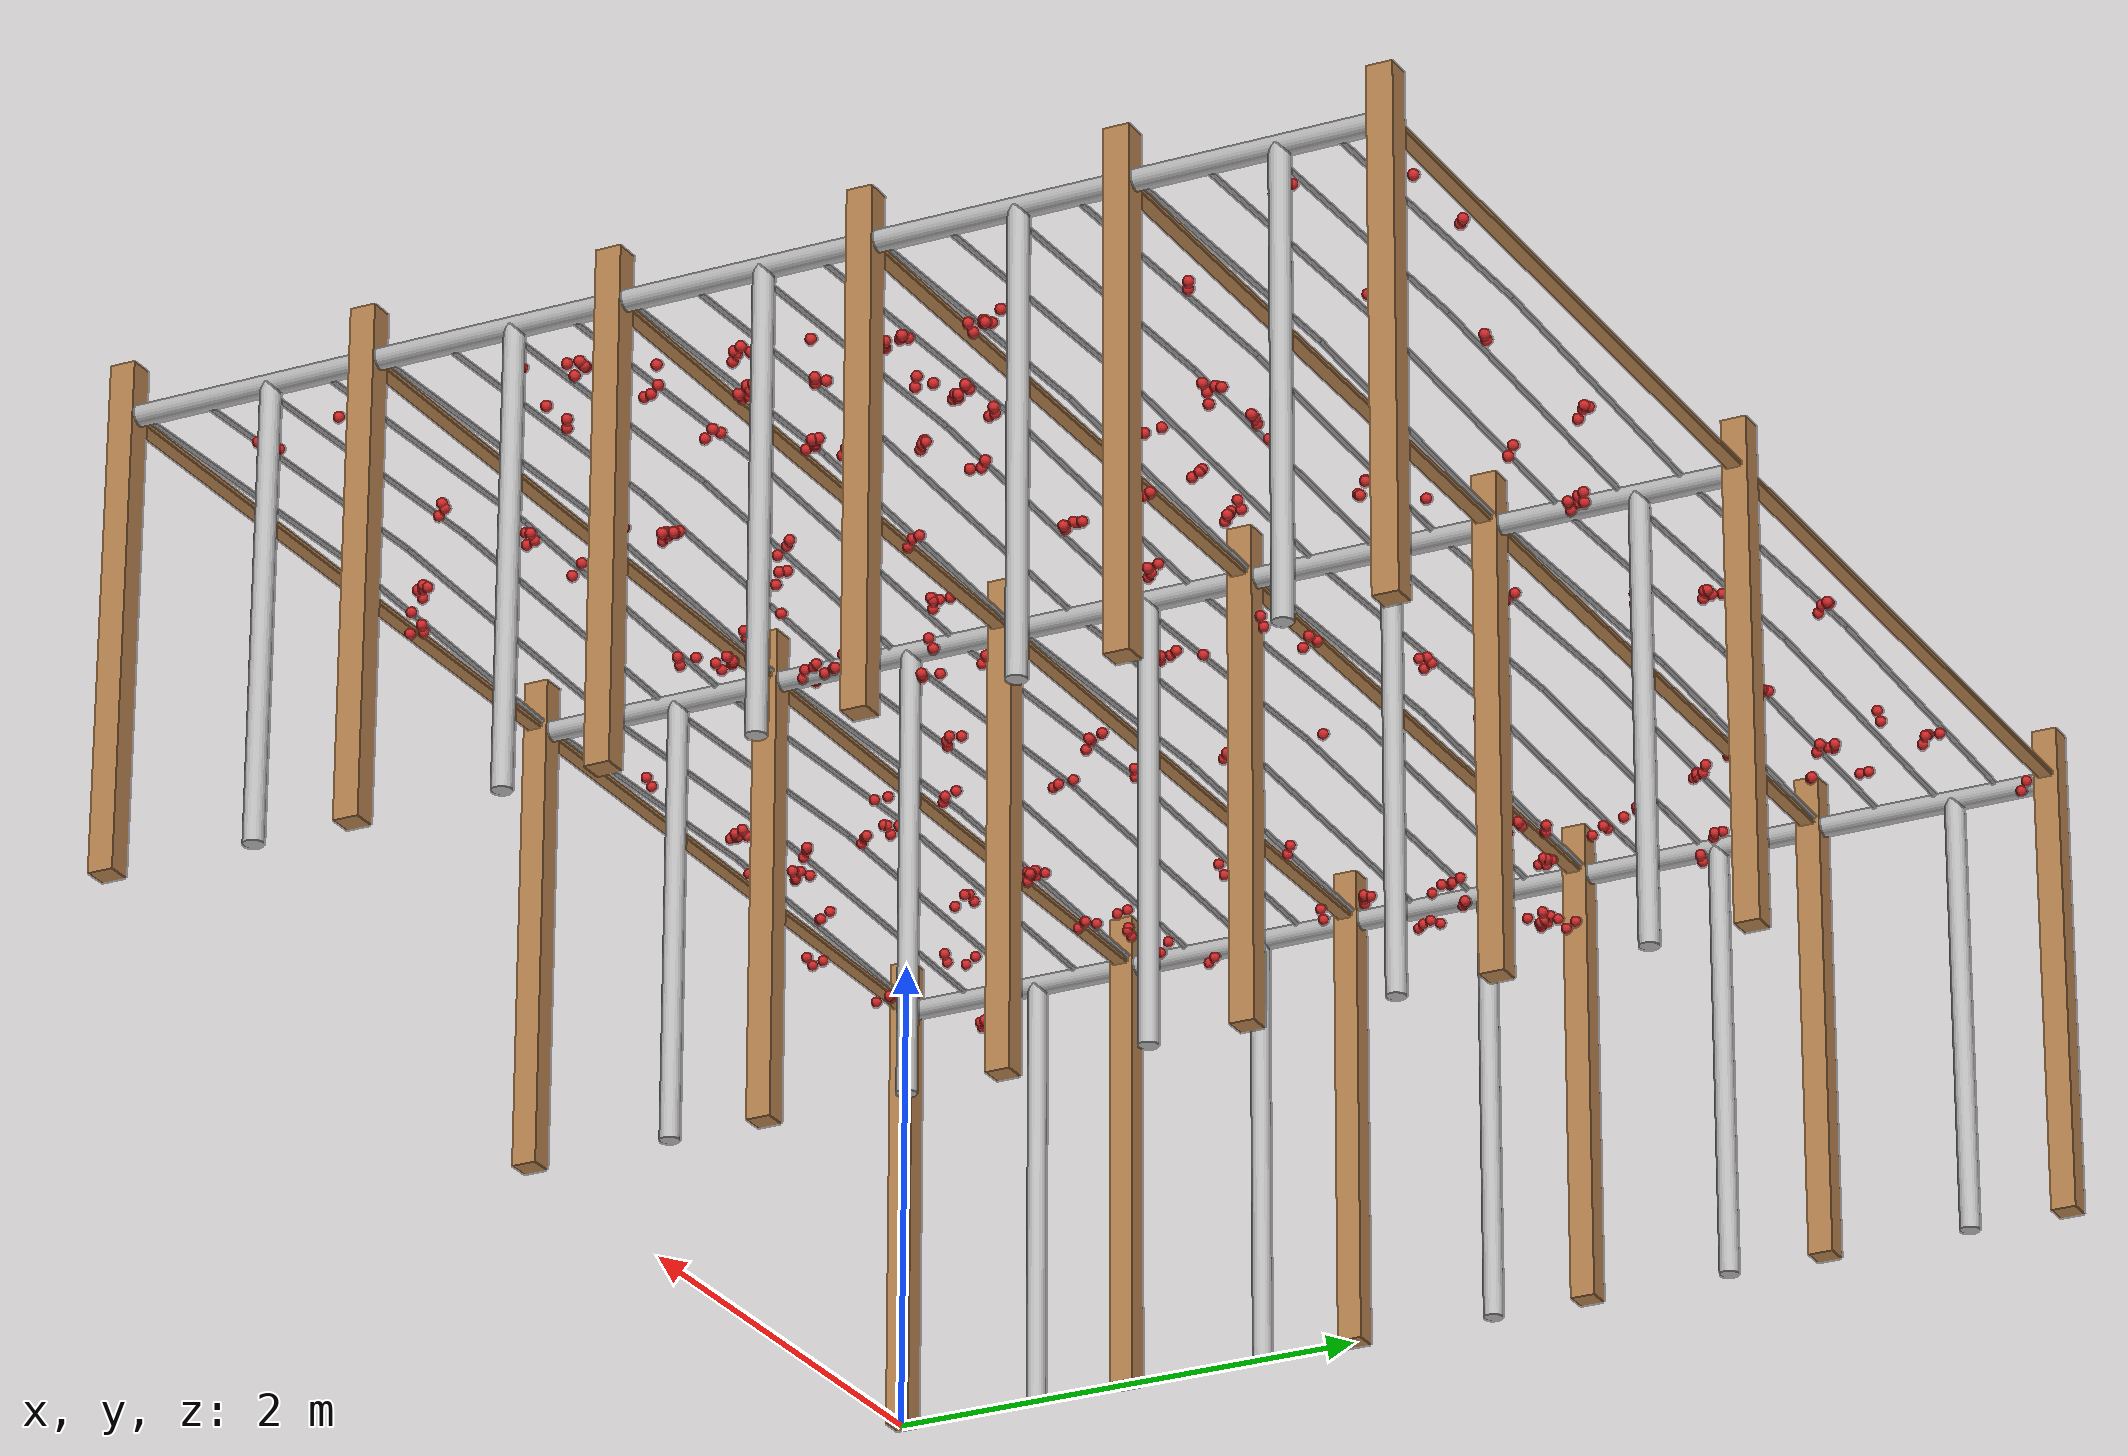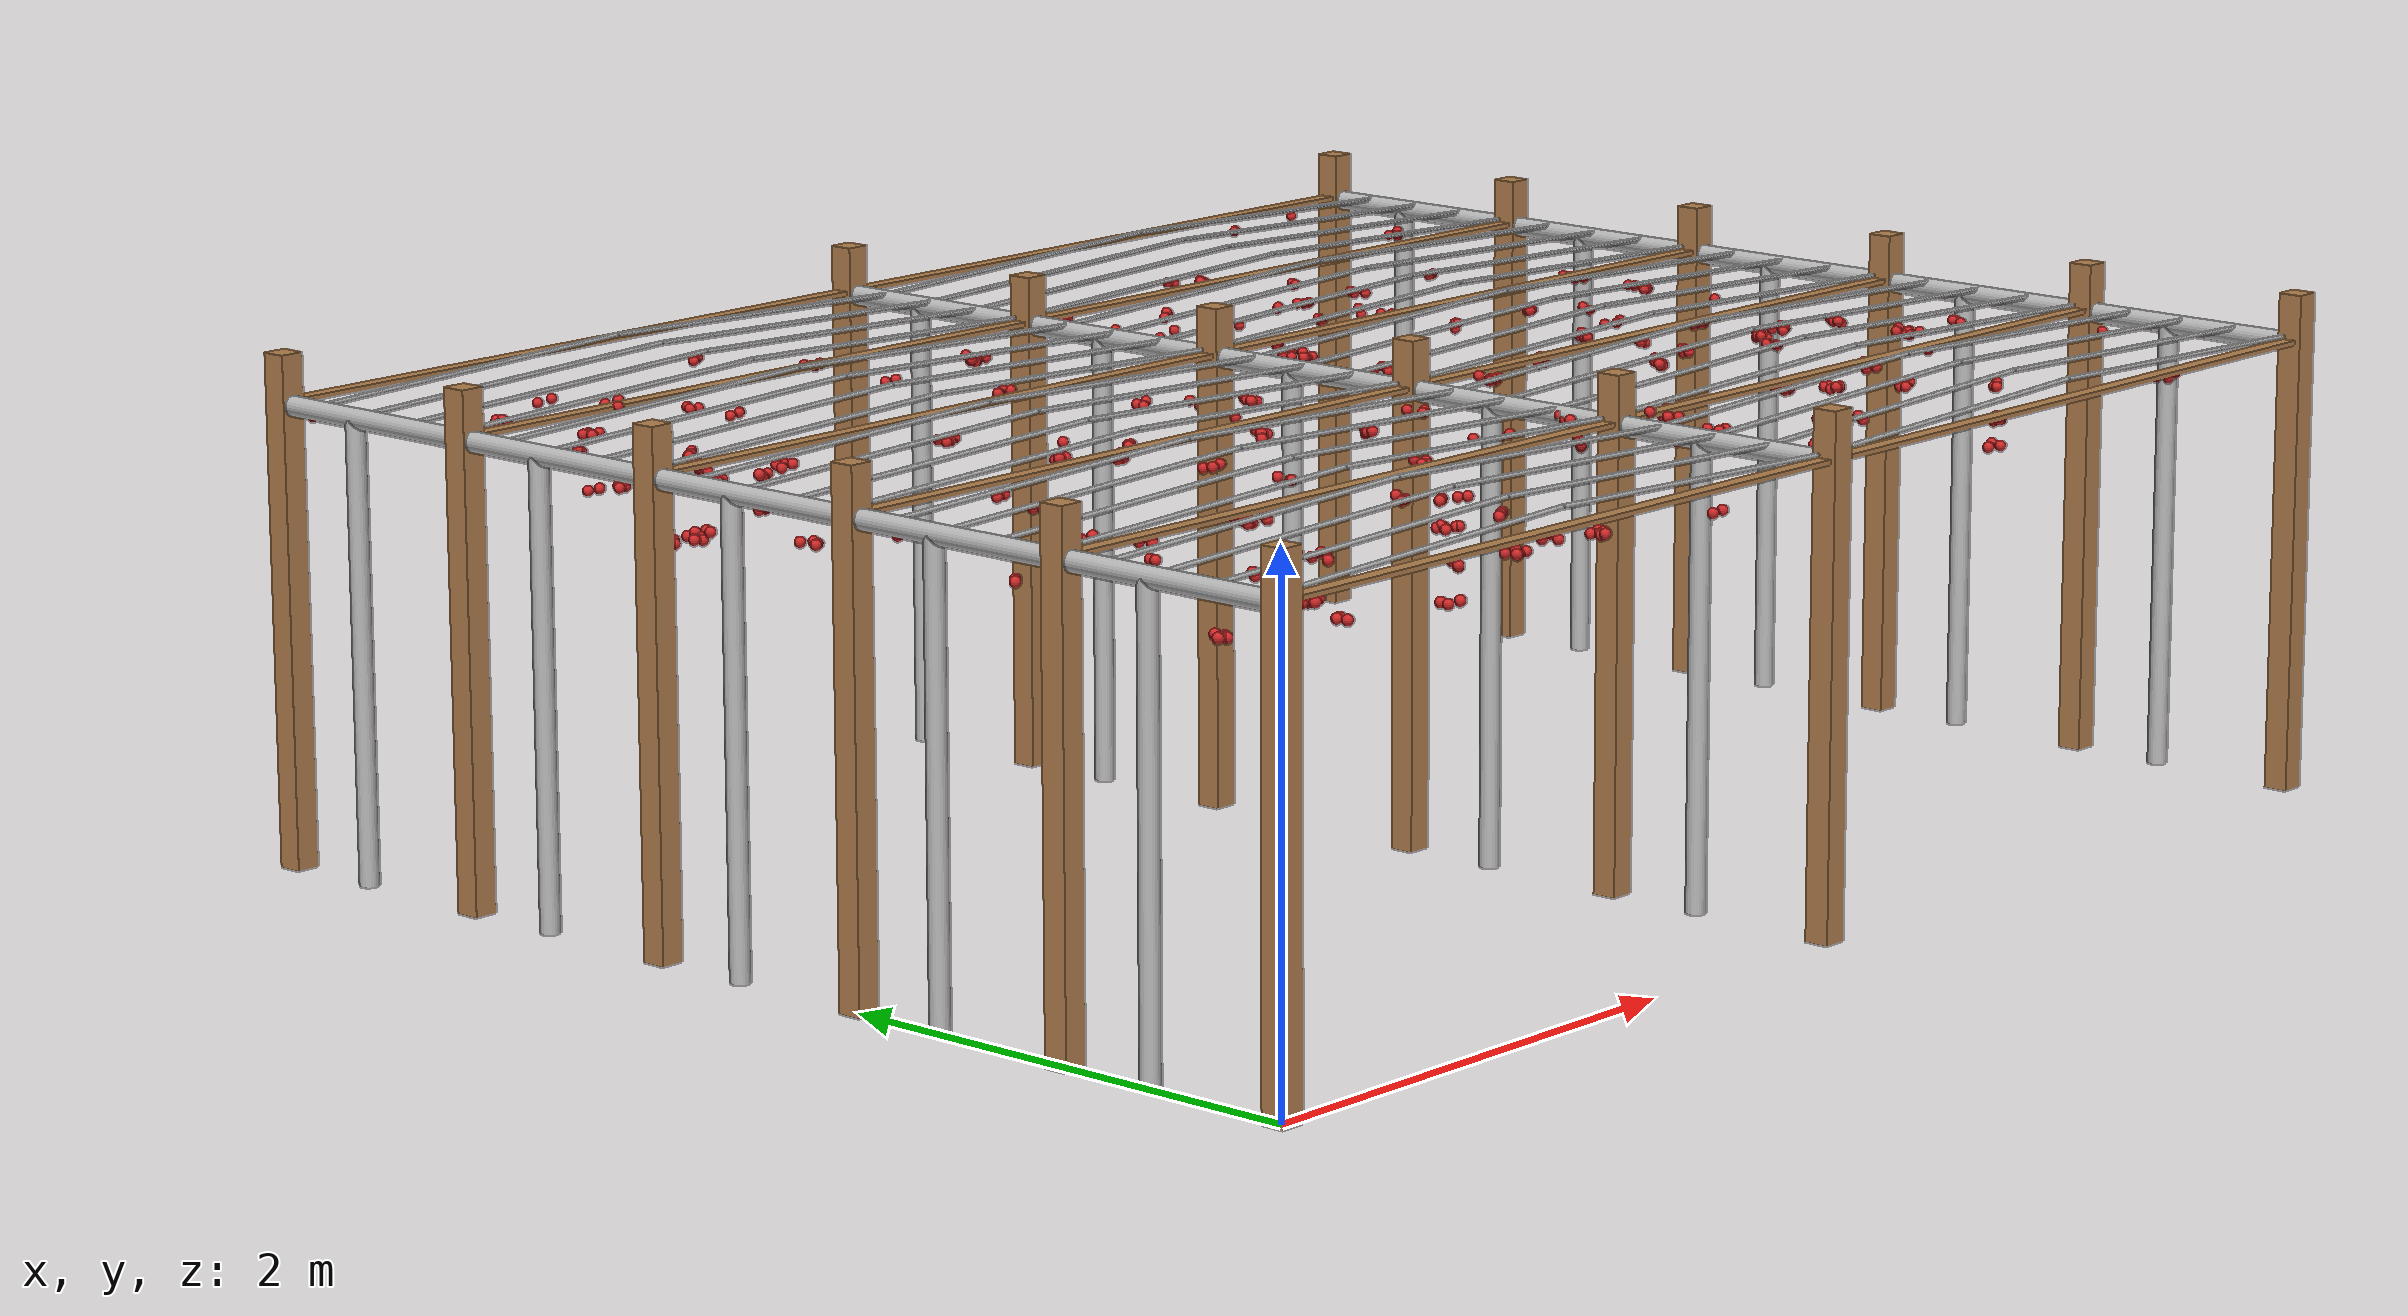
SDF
<?xml version='1.0'?>

<!-- This file contains a model for the pergola structure in the orchard and includes:
18 posts, 12 crossbeams, 15 trees, 60 vines, and 500 fruit. -->
<sdf version='1.4'>
  <model name="pergola">
		<!-- Posts -->

		<include>
			<name>post_0</name>
			<pose>0.0 0.0 0 0 0 0</pose>
			<uri>model://post</uri>
		</include>

		<include>
			<name>post_1</name>
			<pose>0.0 1.0 0 0 0 0</pose>
			<uri>model://post</uri>
		</include>

		<include>
			<name>post_2</name>
			<pose>0.0 2.0 0 0 0 0</pose>
			<uri>model://post</uri>
		</include>

		<include>
			<name>post_3</name>
			<pose>0.0 3.0 0 0 0 0</pose>
			<uri>model://post</uri>
		</include>

		<include>
			<name>post_4</name>
			<pose>0.0 4.0 0 0 0 0</pose>
			<uri>model://post</uri>
		</include>

		<include>
			<name>post_5</name>
			<pose>0.0 5.0 0 0 0 0</pose>
			<uri>model://post</uri>
		</include>

		<include>
			<name>post_6</name>
			<pose>3.0 0.0 0 0 0 0</pose>
			<uri>model://post</uri>
		</include>

		<include>
			<name>post_7</name>
			<pose>3.0 1.0 0 0 0 0</pose>
			<uri>model://post</uri>
		</include>

		<include>
			<name>post_8</name>
			<pose>3.0 2.0 0 0 0 0</pose>
			<uri>model://post</uri>
		</include>

		<include>
			<name>post_9</name>
			<pose>3.0 3.0 0 0 0 0</pose>
			<uri>model://post</uri>
		</include>

		<include>
			<name>post_10</name>
			<pose>3.0 4.0 0 0 0 0</pose>
			<uri>model://post</uri>
		</include>

		<include>
			<name>post_11</name>
			<pose>3.0 5.0 0 0 0 0</pose>
			<uri>model://post</uri>
		</include>

		<include>
			<name>post_12</name>
			<pose>6.0 0.0 0 0 0 0</pose>
			<uri>model://post</uri>
		</include>

		<include>
			<name>post_13</name>
			<pose>6.0 1.0 0 0 0 0</pose>
			<uri>model://post</uri>
		</include>

		<include>
			<name>post_14</name>
			<pose>6.0 2.0 0 0 0 0</pose>
			<uri>model://post</uri>
		</include>

		<include>
			<name>post_15</name>
			<pose>6.0 3.0 0 0 0 0</pose>
			<uri>model://post</uri>
		</include>

		<include>
			<name>post_16</name>
			<pose>6.0 4.0 0 0 0 0</pose>
			<uri>model://post</uri>
		</include>

		<include>
			<name>post_17</name>
			<pose>6.0 5.0 0 0 0 0</pose>
			<uri>model://post</uri>
		</include>

		<!-- Crossbeams -->

    <link name="beam_0">
      <pose>1.5 0.0 1.81 0 0 0</pose>
      <collision name="collision">
        <geometry><box><size>3.0 0.06 0.02</size></box></geometry>
      </collision>
      <visual name="visual">
        <geometry><box><size>3.0 0.06 0.02</size></box></geometry>
        <material><script><uri>model://post/materials/scripts</uri>
            <uri>model://post/materials/textures</uri>
            <name>Post/Wood</name></script></material>
      </visual>
    <inertial>
      <pose>0 0 0 0 0 0</pose>
      <mass>5</mass>
      <inertia>
        <ixx>0.0016666666666666668</ixx><ixy>0.0</ixy><ixz>0.0</ixz><iyy>3.7515</iyy><iyz>0.0</iyz><izz>3.750166666666667</izz>
      </inertia>
    </inertial>
    </link>

    <link name="beam_1">
      <pose>1.5 1.0 1.81 0 0 0</pose>
      <collision name="collision">
        <geometry><box><size>3.0 0.06 0.02</size></box></geometry>
      </collision>
      <visual name="visual">
        <geometry><box><size>3.0 0.06 0.02</size></box></geometry>
        <material><script><uri>model://post/materials/scripts</uri>
            <uri>model://post/materials/textures</uri>
            <name>Post/Wood</name></script></material>
      </visual>
    <inertial>
      <pose>0 0 0 0 0 0</pose>
      <mass>5</mass>
      <inertia>
        <ixx>0.0016666666666666668</ixx><ixy>0.0</ixy><ixz>0.0</ixz><iyy>3.7515</iyy><iyz>0.0</iyz><izz>3.750166666666667</izz>
      </inertia>
    </inertial>
    </link>

    <link name="beam_2">
      <pose>1.5 2.0 1.81 0 0 0</pose>
      <collision name="collision">
        <geometry><box><size>3.0 0.06 0.02</size></box></geometry>
      </collision>
      <visual name="visual">
        <geometry><box><size>3.0 0.06 0.02</size></box></geometry>
        <material><script><uri>model://post/materials/scripts</uri>
            <uri>model://post/materials/textures</uri>
            <name>Post/Wood</name></script></material>
      </visual>
    <inertial>
      <pose>0 0 0 0 0 0</pose>
      <mass>5</mass>
      <inertia>
        <ixx>0.0016666666666666668</ixx><ixy>0.0</ixy><ixz>0.0</ixz><iyy>3.7515</iyy><iyz>0.0</iyz><izz>3.750166666666667</izz>
      </inertia>
    </inertial>
    </link>

    <link name="beam_3">
      <pose>1.5 3.0 1.81 0 0 0</pose>
      <collision name="collision">
        <geometry><box><size>3.0 0.06 0.02</size></box></geometry>
      </collision>
      <visual name="visual">
        <geometry><box><size>3.0 0.06 0.02</size></box></geometry>
        <material><script><uri>model://post/materials/scripts</uri>
            <uri>model://post/materials/textures</uri>
            <name>Post/Wood</name></script></material>
      </visual>
    <inertial>
      <pose>0 0 0 0 0 0</pose>
      <mass>5</mass>
      <inertia>
        <ixx>0.0016666666666666668</ixx><ixy>0.0</ixy><ixz>0.0</ixz><iyy>3.7515</iyy><iyz>0.0</iyz><izz>3.750166666666667</izz>
      </inertia>
    </inertial>
    </link>

    <link name="beam_4">
      <pose>1.5 4.0 1.81 0 0 0</pose>
      <collision name="collision">
        <geometry><box><size>3.0 0.06 0.02</size></box></geometry>
      </collision>
      <visual name="visual">
        <geometry><box><size>3.0 0.06 0.02</size></box></geometry>
        <material><script><uri>model://post/materials/scripts</uri>
            <uri>model://post/materials/textures</uri>
            <name>Post/Wood</name></script></material>
      </visual>
    <inertial>
      <pose>0 0 0 0 0 0</pose>
      <mass>5</mass>
      <inertia>
        <ixx>0.0016666666666666668</ixx><ixy>0.0</ixy><ixz>0.0</ixz><iyy>3.7515</iyy><iyz>0.0</iyz><izz>3.750166666666667</izz>
      </inertia>
    </inertial>
    </link>

    <link name="beam_5">
      <pose>1.5 5.0 1.81 0 0 0</pose>
      <collision name="collision">
        <geometry><box><size>3.0 0.06 0.02</size></box></geometry>
      </collision>
      <visual name="visual">
        <geometry><box><size>3.0 0.06 0.02</size></box></geometry>
        <material><script><uri>model://post/materials/scripts</uri>
            <uri>model://post/materials/textures</uri>
            <name>Post/Wood</name></script></material>
      </visual>
    <inertial>
      <pose>0 0 0 0 0 0</pose>
      <mass>5</mass>
      <inertia>
        <ixx>0.0016666666666666668</ixx><ixy>0.0</ixy><ixz>0.0</ixz><iyy>3.7515</iyy><iyz>0.0</iyz><izz>3.750166666666667</izz>
      </inertia>
    </inertial>
    </link>

    <link name="beam_6">
      <pose>4.5 0.0 1.81 0 0 0</pose>
      <collision name="collision">
        <geometry><box><size>3.0 0.06 0.02</size></box></geometry>
      </collision>
      <visual name="visual">
        <geometry><box><size>3.0 0.06 0.02</size></box></geometry>
        <material><script><uri>model://post/materials/scripts</uri>
            <uri>model://post/materials/textures</uri>
            <name>Post/Wood</name></script></material>
      </visual>
    <inertial>
      <pose>0 0 0 0 0 0</pose>
      <mass>5</mass>
      <inertia>
        <ixx>0.0016666666666666668</ixx><ixy>0.0</ixy><ixz>0.0</ixz><iyy>3.7515</iyy><iyz>0.0</iyz><izz>3.750166666666667</izz>
      </inertia>
    </inertial>
    </link>

    <link name="beam_7">
      <pose>4.5 1.0 1.81 0 0 0</pose>
      <collision name="collision">
        <geometry><box><size>3.0 0.06 0.02</size></box></geometry>
      </collision>
      <visual name="visual">
        <geometry><box><size>3.0 0.06 0.02</size></box></geometry>
        <material><script><uri>model://post/materials/scripts</uri>
            <uri>model://post/materials/textures</uri>
            <name>Post/Wood</name></script></material>
      </visual>
    <inertial>
      <pose>0 0 0 0 0 0</pose>
      <mass>5</mass>
      <inertia>
        <ixx>0.0016666666666666668</ixx><ixy>0.0</ixy><ixz>0.0</ixz><iyy>3.7515</iyy><iyz>0.0</iyz><izz>3.750166666666667</izz>
      </inertia>
    </inertial>
    </link>

    <link name="beam_8">
      <pose>4.5 2.0 1.81 0 0 0</pose>
      <collision name="collision">
        <geometry><box><size>3.0 0.06 0.02</size></box></geometry>
      </collision>
      <visual name="visual">
        <geometry><box><size>3.0 0.06 0.02</size></box></geometry>
        <material><script><uri>model://post/materials/scripts</uri>
            <uri>model://post/materials/textures</uri>
            <name>Post/Wood</name></script></material>
      </visual>
    <inertial>
      <pose>0 0 0 0 0 0</pose>
      <mass>5</mass>
      <inertia>
        <ixx>0.0016666666666666668</ixx><ixy>0.0</ixy><ixz>0.0</ixz><iyy>3.7515</iyy><iyz>0.0</iyz><izz>3.750166666666667</izz>
      </inertia>
    </inertial>
    </link>

    <link name="beam_9">
      <pose>4.5 3.0 1.81 0 0 0</pose>
      <collision name="collision">
        <geometry><box><size>3.0 0.06 0.02</size></box></geometry>
      </collision>
      <visual name="visual">
        <geometry><box><size>3.0 0.06 0.02</size></box></geometry>
        <material><script><uri>model://post/materials/scripts</uri>
            <uri>model://post/materials/textures</uri>
            <name>Post/Wood</name></script></material>
      </visual>
    <inertial>
      <pose>0 0 0 0 0 0</pose>
      <mass>5</mass>
      <inertia>
        <ixx>0.0016666666666666668</ixx><ixy>0.0</ixy><ixz>0.0</ixz><iyy>3.7515</iyy><iyz>0.0</iyz><izz>3.750166666666667</izz>
      </inertia>
    </inertial>
    </link>

    <link name="beam_10">
      <pose>4.5 4.0 1.81 0 0 0</pose>
      <collision name="collision">
        <geometry><box><size>3.0 0.06 0.02</size></box></geometry>
      </collision>
      <visual name="visual">
        <geometry><box><size>3.0 0.06 0.02</size></box></geometry>
        <material><script><uri>model://post/materials/scripts</uri>
            <uri>model://post/materials/textures</uri>
            <name>Post/Wood</name></script></material>
      </visual>
    <inertial>
      <pose>0 0 0 0 0 0</pose>
      <mass>5</mass>
      <inertia>
        <ixx>0.0016666666666666668</ixx><ixy>0.0</ixy><ixz>0.0</ixz><iyy>3.7515</iyy><iyz>0.0</iyz><izz>3.750166666666667</izz>
      </inertia>
    </inertial>
    </link>

    <link name="beam_11">
      <pose>4.5 5.0 1.81 0 0 0</pose>
      <collision name="collision">
        <geometry><box><size>3.0 0.06 0.02</size></box></geometry>
      </collision>
      <visual name="visual">
        <geometry><box><size>3.0 0.06 0.02</size></box></geometry>
        <material><script><uri>model://post/materials/scripts</uri>
            <uri>model://post/materials/textures</uri>
            <name>Post/Wood</name></script></material>
      </visual>
    <inertial>
      <pose>0 0 0 0 0 0</pose>
      <mass>5</mass>
      <inertia>
        <ixx>0.0016666666666666668</ixx><ixy>0.0</ixy><ixz>0.0</ixz><iyy>3.7515</iyy><iyz>0.0</iyz><izz>3.750166666666667</izz>
      </inertia>
    </inertial>
    </link>

		<!-- Tree trunks -->

		<include>
			<name>tree_0</name>
			<pose>0.0 0.6 0 0 0 0</pose>
			<uri>model://tree_trunk</uri>
		</include>

		<include>
			<name>tree_1</name>
			<pose>0.0 1.6 0 0 0 0</pose>
			<uri>model://tree_trunk</uri>
		</include>

		<include>
			<name>tree_2</name>
			<pose>0.0 2.6 0 0 0 0</pose>
			<uri>model://tree_trunk</uri>
		</include>

		<include>
			<name>tree_3</name>
			<pose>0.0 3.6 0 0 0 0</pose>
			<uri>model://tree_trunk</uri>
		</include>

		<include>
			<name>tree_4</name>
			<pose>0.0 4.6 0 0 0 0</pose>
			<uri>model://tree_trunk</uri>
		</include>

		<include>
			<name>tree_5</name>
			<pose>3.0 0.6 0 0 0 0</pose>
			<uri>model://tree_trunk</uri>
		</include>

		<include>
			<name>tree_6</name>
			<pose>3.0 1.6 0 0 0 0</pose>
			<uri>model://tree_trunk</uri>
		</include>

		<include>
			<name>tree_7</name>
			<pose>3.0 2.6 0 0 0 0</pose>
			<uri>model://tree_trunk</uri>
		</include>

		<include>
			<name>tree_8</name>
			<pose>3.0 3.6 0 0 0 0</pose>
			<uri>model://tree_trunk</uri>
		</include>

		<include>
			<name>tree_9</name>
			<pose>3.0 4.6 0 0 0 0</pose>
			<uri>model://tree_trunk</uri>
		</include>

		<include>
			<name>tree_10</name>
			<pose>6.0 0.6 0 0 0 0</pose>
			<uri>model://tree_trunk</uri>
		</include>

		<include>
			<name>tree_11</name>
			<pose>6.0 1.6 0 0 0 0</pose>
			<uri>model://tree_trunk</uri>
		</include>

		<include>
			<name>tree_12</name>
			<pose>6.0 2.6 0 0 0 0</pose>
			<uri>model://tree_trunk</uri>
		</include>

		<include>
			<name>tree_13</name>
			<pose>6.0 3.6 0 0 0 0</pose>
			<uri>model://tree_trunk</uri>
		</include>

		<include>
			<name>tree_14</name>
			<pose>6.0 4.6 0 0 0 0</pose>
			<uri>model://tree_trunk</uri>
		</include>

		<!-- Base branches along rows of trees. (Base branches are similar to the trunk growing horizontally along pergola) -->

    <link name="baseBranch_0">
      <pose>0.0 0.5 1.8 1.5707963267948966 0 0</pose>
      <collision name="collision">
        <geometry><cylinder><radius>0.04</radius> <length>1.0</length></cylinder></geometry>
      </collision>
      <visual name="visual">
        <geometry><cylinder><radius>0.04</radius> <length>1.0</length></cylinder></geometry>
        <material><script><uri>model://tree_trunk/materials/scripts</uri>
            <uri>model://tree_trunk/materials/textures</uri>
            <name>Tree/Bark</name></script></material>
      </visual>
    <inertial>
      <pose>0 0 0 0 0 0</pose>
      <mass>10</mass>
      <inertia>
        <ixx>0.8373333333333332</ixx><ixy>0.0</ixy><ixz>0.0</ixz><iyy>0.8373333333333332</iyy><iyz>0.0</iyz><izz>0.008</izz>
      </inertia>
    </inertial>
    </link>

    <link name="baseBranch_1">
      <pose>0.0 1.5 1.8 1.5707963267948966 0 0</pose>
      <collision name="collision">
        <geometry><cylinder><radius>0.04</radius> <length>1.0</length></cylinder></geometry>
      </collision>
      <visual name="visual">
        <geometry><cylinder><radius>0.04</radius> <length>1.0</length></cylinder></geometry>
        <material><script><uri>model://tree_trunk/materials/scripts</uri>
            <uri>model://tree_trunk/materials/textures</uri>
            <name>Tree/Bark</name></script></material>
      </visual>
    <inertial>
      <pose>0 0 0 0 0 0</pose>
      <mass>10</mass>
      <inertia>
        <ixx>0.8373333333333332</ixx><ixy>0.0</ixy><ixz>0.0</ixz><iyy>0.8373333333333332</iyy><iyz>0.0</iyz><izz>0.008</izz>
      </inertia>
    </inertial>
    </link>

    <link name="baseBranch_2">
      <pose>0.0 2.5 1.8 1.5707963267948966 0 0</pose>
      <collision name="collision">
        <geometry><cylinder><radius>0.04</radius> <length>1.0</length></cylinder></geometry>
      </collision>
      <visual name="visual">
        <geometry><cylinder><radius>0.04</radius> <length>1.0</length></cylinder></geometry>
        <material><script><uri>model://tree_trunk/materials/scripts</uri>
            <uri>model://tree_trunk/materials/textures</uri>
            <name>Tree/Bark</name></script></material>
      </visual>
    <inertial>
      <pose>0 0 0 0 0 0</pose>
      <mass>10</mass>
      <inertia>
        <ixx>0.8373333333333332</ixx><ixy>0.0</ixy><ixz>0.0</ixz><iyy>0.8373333333333332</iyy><iyz>0.0</iyz><izz>0.008</izz>
      </inertia>
    </inertial>
    </link>

    <link name="baseBranch_3">
      <pose>0.0 3.5 1.8 1.5707963267948966 0 0</pose>
      <collision name="collision">
        <geometry><cylinder><radius>0.04</radius> <length>1.0</length></cylinder></geometry>
      </collision>
      <visual name="visual">
        <geometry><cylinder><radius>0.04</radius> <length>1.0</length></cylinder></geometry>
        <material><script><uri>model://tree_trunk/materials/scripts</uri>
            <uri>model://tree_trunk/materials/textures</uri>
            <name>Tree/Bark</name></script></material>
      </visual>
    <inertial>
      <pose>0 0 0 0 0 0</pose>
      <mass>10</mass>
      <inertia>
        <ixx>0.8373333333333332</ixx><ixy>0.0</ixy><ixz>0.0</ixz><iyy>0.8373333333333332</iyy><iyz>0.0</iyz><izz>0.008</izz>
      </inertia>
    </inertial>
    </link>

    <link name="baseBranch_4">
      <pose>0.0 4.5 1.8 1.5707963267948966 0 0</pose>
      <collision name="collision">
        <geometry><cylinder><radius>0.04</radius> <length>1.0</length></cylinder></geometry>
      </collision>
      <visual name="visual">
        <geometry><cylinder><radius>0.04</radius> <length>1.0</length></cylinder></geometry>
        <material><script><uri>model://tree_trunk/materials/scripts</uri>
            <uri>model://tree_trunk/materials/textures</uri>
            <name>Tree/Bark</name></script></material>
      </visual>
    <inertial>
      <pose>0 0 0 0 0 0</pose>
      <mass>10</mass>
      <inertia>
        <ixx>0.8373333333333332</ixx><ixy>0.0</ixy><ixz>0.0</ixz><iyy>0.8373333333333332</iyy><iyz>0.0</iyz><izz>0.008</izz>
      </inertia>
    </inertial>
    </link>

    <link name="baseBranch_5">
      <pose>3.0 0.5 1.8 1.5707963267948966 0 0</pose>
      <collision name="collision">
        <geometry><cylinder><radius>0.04</radius> <length>1.0</length></cylinder></geometry>
      </collision>
      <visual name="visual">
        <geometry><cylinder><radius>0.04</radius> <length>1.0</length></cylinder></geometry>
        <material><script><uri>model://tree_trunk/materials/scripts</uri>
            <uri>model://tree_trunk/materials/textures</uri>
            <name>Tree/Bark</name></script></material>
      </visual>
    <inertial>
      <pose>0 0 0 0 0 0</pose>
      <mass>10</mass>
      <inertia>
        <ixx>0.8373333333333332</ixx><ixy>0.0</ixy><ixz>0.0</ixz><iyy>0.8373333333333332</iyy><iyz>0.0</iyz><izz>0.008</izz>
      </inertia>
    </inertial>
    </link>

    <link name="baseBranch_6">
      <pose>3.0 1.5 1.8 1.5707963267948966 0 0</pose>
      <collision name="collision">
        <geometry><cylinder><radius>0.04</radius> <length>1.0</length></cylinder></geometry>
      </collision>
      <visual name="visual">
        <geometry><cylinder><radius>0.04</radius> <length>1.0</length></cylinder></geometry>
        <material><script><uri>model://tree_trunk/materials/scripts</uri>
            <uri>model://tree_trunk/materials/textures</uri>
            <name>Tree/Bark</name></script></material>
      </visual>
    <inertial>
      <pose>0 0 0 0 0 0</pose>
      <mass>10</mass>
      <inertia>
        <ixx>0.8373333333333332</ixx><ixy>0.0</ixy><ixz>0.0</ixz><iyy>0.8373333333333332</iyy><iyz>0.0</iyz><izz>0.008</izz>
      </inertia>
    </inertial>
    </link>

    <link name="baseBranch_7">
      <pose>3.0 2.5 1.8 1.5707963267948966 0 0</pose>
      <collision name="collision">
        <geometry><cylinder><radius>0.04</radius> <length>1.0</length></cylinder></geometry>
      </collision>
      <visual name="visual">
        <geometry><cylinder><radius>0.04</radius> <length>1.0</length></cylinder></geometry>
        <material><script><uri>model://tree_trunk/materials/scripts</uri>
            <uri>model://tree_trunk/materials/textures</uri>
            <name>Tree/Bark</name></script></material>
      </visual>
    <inertial>
      <pose>0 0 0 0 0 0</pose>
      <mass>10</mass>
      <inertia>
        <ixx>0.8373333333333332</ixx><ixy>0.0</ixy><ixz>0.0</ixz><iyy>0.8373333333333332</iyy><iyz>0.0</iyz><izz>0.008</izz>
      </inertia>
    </inertial>
    </link>

    <link name="baseBranch_8">
      <pose>3.0 3.5 1.8 1.5707963267948966 0 0</pose>
      <collision name="collision">
        <geometry><cylinder><radius>0.04</radius> <length>1.0</length></cylinder></geometry>
      </collision>
      <visual name="visual">
        <geometry><cylinder><radius>0.04</radius> <length>1.0</length></cylinder></geometry>
        <material><script><uri>model://tree_trunk/materials/scripts</uri>
            <uri>model://tree_trunk/materials/textures</uri>
            <name>Tree/Bark</name></script></material>
      </visual>
    <inertial>
      <pose>0 0 0 0 0 0</pose>
      <mass>10</mass>
      <inertia>
        <ixx>0.8373333333333332</ixx><ixy>0.0</ixy><ixz>0.0</ixz><iyy>0.8373333333333332</iyy><iyz>0.0</iyz><izz>0.008</izz>
      </inertia>
    </inertial>
    </link>

    <link name="baseBranch_9">
      <pose>3.0 4.5 1.8 1.5707963267948966 0 0</pose>
      <collision name="collision">
        <geometry><cylinder><radius>0.04</radius> <length>1.0</length></cylinder></geometry>
      </collision>
      <visual name="visual">
        <geometry><cylinder><radius>0.04</radius> <length>1.0</length></cylinder></geometry>
        <material><script><uri>model://tree_trunk/materials/scripts</uri>
            <uri>model://tree_trunk/materials/textures</uri>
            <name>Tree/Bark</name></script></material>
      </visual>
    <inertial>
      <pose>0 0 0 0 0 0</pose>
      <mass>10</mass>
      <inertia>
        <ixx>0.8373333333333332</ixx><ixy>0.0</ixy><ixz>0.0</ixz><iyy>0.8373333333333332</iyy><iyz>0.0</iyz><izz>0.008</izz>
      </inertia>
    </inertial>
    </link>

    <link name="baseBranch_10">
      <pose>6.0 0.5 1.8 1.5707963267948966 0 0</pose>
      <collision name="collision">
        <geometry><cylinder><radius>0.04</radius> <length>1.0</length></cylinder></geometry>
      </collision>
      <visual name="visual">
        <geometry><cylinder><radius>0.04</radius> <length>1.0</length></cylinder></geometry>
        <material><script><uri>model://tree_trunk/materials/scripts</uri>
            <uri>model://tree_trunk/materials/textures</uri>
            <name>Tree/Bark</name></script></material>
      </visual>
    <inertial>
      <pose>0 0 0 0 0 0</pose>
      <mass>10</mass>
      <inertia>
        <ixx>0.8373333333333332</ixx><ixy>0.0</ixy><ixz>0.0</ixz><iyy>0.8373333333333332</iyy><iyz>0.0</iyz><izz>0.008</izz>
      </inertia>
    </inertial>
    </link>

    <link name="baseBranch_11">
      <pose>6.0 1.5 1.8 1.5707963267948966 0 0</pose>
      <collision name="collision">
        <geometry><cylinder><radius>0.04</radius> <length>1.0</length></cylinder></geometry>
      </collision>
      <visual name="visual">
        <geometry><cylinder><radius>0.04</radius> <length>1.0</length></cylinder></geometry>
        <material><script><uri>model://tree_trunk/materials/scripts</uri>
            <uri>model://tree_trunk/materials/textures</uri>
            <name>Tree/Bark</name></script></material>
      </visual>
    <inertial>
      <pose>0 0 0 0 0 0</pose>
      <mass>10</mass>
      <inertia>
        <ixx>0.8373333333333332</ixx><ixy>0.0</ixy><ixz>0.0</ixz><iyy>0.8373333333333332</iyy><iyz>0.0</iyz><izz>0.008</izz>
      </inertia>
    </inertial>
    </link>

    <link name="baseBranch_12">
      <pose>6.0 2.5 1.8 1.5707963267948966 0 0</pose>
      <collision name="collision">
        <geometry><cylinder><radius>0.04</radius> <length>1.0</length></cylinder></geometry>
      </collision>
      <visual name="visual">
        <geometry><cylinder><radius>0.04</radius> <length>1.0</length></cylinder></geometry>
        <material><script><uri>model://tree_trunk/materials/scripts</uri>
            <uri>model://tree_trunk/materials/textures</uri>
            <name>Tree/Bark</name></script></material>
      </visual>
    <inertial>
      <pose>0 0 0 0 0 0</pose>
      <mass>10</mass>
      <inertia>
        <ixx>0.8373333333333332</ixx><ixy>0.0</ixy><ixz>0.0</ixz><iyy>0.8373333333333332</iyy><iyz>0.0</iyz><izz>0.008</izz>
      </inertia>
    </inertial>
    </link>

    <link name="baseBranch_13">
      <pose>6.0 3.5 1.8 1.5707963267948966 0 0</pose>
      <collision name="collision">
        <geometry><cylinder><radius>0.04</radius> <length>1.0</length></cylinder></geometry>
      </collision>
      <visual name="visual">
        <geometry><cylinder><radius>0.04</radius> <length>1.0</length></cylinder></geometry>
        <material><script><uri>model://tree_trunk/materials/scripts</uri>
            <uri>model://tree_trunk/materials/textures</uri>
            <name>Tree/Bark</name></script></material>
      </visual>
    <inertial>
      <pose>0 0 0 0 0 0</pose>
      <mass>10</mass>
      <inertia>
        <ixx>0.8373333333333332</ixx><ixy>0.0</ixy><ixz>0.0</ixz><iyy>0.8373333333333332</iyy><iyz>0.0</iyz><izz>0.008</izz>
      </inertia>
    </inertial>
    </link>

    <link name="baseBranch_14">
      <pose>6.0 4.5 1.8 1.5707963267948966 0 0</pose>
      <collision name="collision">
        <geometry><cylinder><radius>0.04</radius> <length>1.0</length></cylinder></geometry>
      </collision>
      <visual name="visual">
        <geometry><cylinder><radius>0.04</radius> <length>1.0</length></cylinder></geometry>
        <material><script><uri>model://tree_trunk/materials/scripts</uri>
            <uri>model://tree_trunk/materials/textures</uri>
            <name>Tree/Bark</name></script></material>
      </visual>
    <inertial>
      <pose>0 0 0 0 0 0</pose>
      <mass>10</mass>
      <inertia>
        <ixx>0.8373333333333332</ixx><ixy>0.0</ixy><ixz>0.0</ixz><iyy>0.8373333333333332</iyy><iyz>0.0</iyz><izz>0.008</izz>
      </inertia>
    </inertial>
    </link>

		<!-- Vines across base branches. Vines consist of an ascending and descending portion to simulate a raised canopy. -->

    <link name="vine_0">
      <pose>0.75 0.03 1.85 0 1.5374753309166493 0</pose>
      <collision name="collision">
        <geometry><cylinder><radius>0.01</radius> <length>1.5008331019803633</length></cylinder></geometry>
      </collision>
      <visual name="visual">
        <geometry><cylinder><radius>0.01</radius> <length>1.5008331019803633</length></cylinder></geometry>
        <material><script><uri>model://tree_trunk/materials/scripts</uri>
            <uri>model://tree_trunk/materials/textures</uri>
            <name>Tree/Bark</name></script></material>
      </visual>
    <inertial>
      <pose>0 0 0 0 0 0</pose>
      <mass>5</mass>
      <inertia>
        <ixx>0.9386666666666668</ixx><ixy>0.0</ixy><ixz>0.0</ixz><iyy>0.9386666666666668</iyy><iyz>0.0</iyz><izz>0.00025</izz>
      </inertia>
    </inertial>
    </link>

    <link name="vine_1">
      <pose>2.25 0.03 1.85 0 -1.5374753309166493 0</pose>
      <collision name="collision">
        <geometry><cylinder><radius>0.01</radius> <length>1.5008331019803633</length></cylinder></geometry>
      </collision>
      <visual name="visual">
        <geometry><cylinder><radius>0.01</radius> <length>1.5008331019803633</length></cylinder></geometry>
        <material><script><uri>model://tree_trunk/materials/scripts</uri>
            <uri>model://tree_trunk/materials/textures</uri>
            <name>Tree/Bark</name></script></material>
      </visual>
    <inertial>
      <pose>0 0 0 0 0 0</pose>
      <mass>5</mass>
      <inertia>
        <ixx>0.9386666666666668</ixx><ixy>0.0</ixy><ixz>0.0</ixz><iyy>0.9386666666666668</iyy><iyz>0.0</iyz><izz>0.00025</izz>
      </inertia>
    </inertial>
    </link>

    <link name="vine_2">
      <pose>0.75 0.28 1.85 0 1.5374753309166493 0</pose>
      <collision name="collision">
        <geometry><cylinder><radius>0.01</radius> <length>1.5008331019803633</length></cylinder></geometry>
      </collision>
      <visual name="visual">
        <geometry><cylinder><radius>0.01</radius> <length>1.5008331019803633</length></cylinder></geometry>
        <material><script><uri>model://tree_trunk/materials/scripts</uri>
            <uri>model://tree_trunk/materials/textures</uri>
            <name>Tree/Bark</name></script></material>
      </visual>
    <inertial>
      <pose>0 0 0 0 0 0</pose>
      <mass>5</mass>
      <inertia>
        <ixx>0.9386666666666668</ixx><ixy>0.0</ixy><ixz>0.0</ixz><iyy>0.9386666666666668</iyy><iyz>0.0</iyz><izz>0.00025</izz>
      </inertia>
    </inertial>
    </link>

    <link name="vine_3">
      <pose>2.25 0.28 1.85 0 -1.5374753309166493 0</pose>
      <collision name="collision">
        <geometry><cylinder><radius>0.01</radius> <length>1.5008331019803633</length></cylinder></geometry>
      </collision>
      <visual name="visual">
        <geometry><cylinder><radius>0.01</radius> <length>1.5008331019803633</length></cylinder></geometry>
        <material><script><uri>model://tree_trunk/materials/scripts</uri>
            <uri>model://tree_trunk/materials/textures</uri>
            <name>Tree/Bark</name></script></material>
      </visual>
    <inertial>
      <pose>0 0 0 0 0 0</pose>
      <mass>5</mass>
      <inertia>
        <ixx>0.9386666666666668</ixx><ixy>0.0</ixy><ixz>0.0</ixz><iyy>0.9386666666666668</iyy><iyz>0.0</iyz><izz>0.00025</izz>
      </inertia>
    </inertial>
    </link>

    <link name="vine_4">
      <pose>0.75 0.53 1.85 0 1.5374753309166493 0</pose>
      <collision name="collision">
        <geometry><cylinder><radius>0.01</radius> <length>1.5008331019803633</length></cylinder></geometry>
      </collision>
      <visual name="visual">
        <geometry><cylinder><radius>0.01</radius> <length>1.5008331019803633</length></cylinder></geometry>
        <material><script><uri>model://tree_trunk/materials/scripts</uri>
            <uri>model://tree_trunk/materials/textures</uri>
            <name>Tree/Bark</name></script></material>
      </visual>
    <inertial>
      <pose>0 0 0 0 0 0</pose>
      <mass>5</mass>
      <inertia>
        <ixx>0.9386666666666668</ixx><ixy>0.0</ixy><ixz>0.0</ixz><iyy>0.9386666666666668</iyy><iyz>0.0</iyz><izz>0.00025</izz>
      </inertia>
    </inertial>
    </link>

    <link name="vine_5">
      <pose>2.25 0.53 1.85 0 -1.5374753309166493 0</pose>
      <collision name="collision">
        <geometry><cylinder><radius>0.01</radius> <length>1.5008331019803633</length></cylinder></geometry>
      </collision>
      <visual name="visual">
        <geometry><cylinder><radius>0.01</radius> <length>1.5008331019803633</length></cylinder></geometry>
        <material><script><uri>model://tree_trunk/materials/scripts</uri>
            <uri>model://tree_trunk/materials/textures</uri>
            <name>Tree/Bark</name></script></material>
      </visual>
    <inertial>
      <pose>0 0 0 0 0 0</pose>
      <mass>5</mass>
      <inertia>
        <ixx>0.9386666666666668</ixx><ixy>0.0</ixy><ixz>0.0</ixz><iyy>0.9386666666666668</iyy><iyz>0.0</iyz><izz>0.00025</izz>
      </inertia>
    </inertial>
    </link>

    <link name="vine_6">
      <pose>0.75 0.78 1.85 0 1.5374753309166493 0</pose>
      <collision name="collision">
        <geometry><cylinder><radius>0.01</radius> <length>1.5008331019803633</length></cylinder></geometry>
      </collision>
      <visual name="visual">
        <geometry><cylinder><radius>0.01</radius> <length>1.5008331019803633</length></cylinder></geometry>
        <material><script><uri>model://tree_trunk/materials/scripts</uri>
            <uri>model://tree_trunk/materials/textures</uri>
            <name>Tree/Bark</name></script></material>
      </visual>
    <inertial>
      <pose>0 0 0 0 0 0</pose>
      <mass>5</mass>
      <inertia>
        <ixx>0.9386666666666668</ixx><ixy>0.0</ixy><ixz>0.0</ixz><iyy>0.9386666666666668</iyy><iyz>0.0</iyz><izz>0.00025</izz>
      </inertia>
    </inertial>
    </link>

    <link name="vine_7">
      <pose>2.25 0.78 1.85 0 -1.5374753309166493 0</pose>
      <collision name="collision">
        <geometry><cylinder><radius>0.01</radius> <length>1.5008331019803633</length></cylinder></geometry>
      </collision>
      <visual name="visual">
        <geometry><cylinder><radius>0.01</radius> <length>1.5008331019803633</length></cylinder></geometry>
        <material><script><uri>model://tree_trunk/materials/scripts</uri>
            <uri>model://tree_trunk/materials/textures</uri>
            <name>Tree/Bark</name></script></material>
      </visual>
    <inertial>
      <pose>0 0 0 0 0 0</pose>
      <mass>5</mass>
      <inertia>
        <ixx>0.9386666666666668</ixx><ixy>0.0</ixy><ixz>0.0</ixz><iyy>0.9386666666666668</iyy><iyz>0.0</iyz><izz>0.00025</izz>
      </inertia>
    </inertial>
    </link>

    <link name="vine_8">
      <pose>0.75 1.03 1.85 0 1.5374753309166493 0</pose>
      <collision name="collision">
        <geometry><cylinder><radius>0.01</radius> <length>1.5008331019803633</length></cylinder></geometry>
      </collision>
      <visual name="visual">
        <geometry><cylinder><radius>0.01</radius> <length>1.5008331019803633</length></cylinder></geometry>
        <material><script><uri>model://tree_trunk/materials/scripts</uri>
            <uri>model://tree_trunk/materials/textures</uri>
            <name>Tree/Bark</name></script></material>
      </visual>
    <inertial>
      <pose>0 0 0 0 0 0</pose>
      <mass>5</mass>
      <inertia>
        <ixx>0.9386666666666668</ixx><ixy>0.0</ixy><ixz>0.0</ixz><iyy>0.9386666666666668</iyy><iyz>0.0</iyz><izz>0.00025</izz>
      </inertia>
    </inertial>
    </link>

    <link name="vine_9">
      <pose>2.25 1.03 1.85 0 -1.5374753309166493 0</pose>
      <collision name="collision">
        <geometry><cylinder><radius>0.01</radius> <length>1.5008331019803633</length></cylinder></geometry>
      </collision>
      <visual name="visual">
        <geometry><cylinder><radius>0.01</radius> <length>1.5008331019803633</length></cylinder></geometry>
        <material><script><uri>model://tree_trunk/materials/scripts</uri>
            <uri>model://tree_trunk/materials/textures</uri>
            <name>Tree/Bark</name></script></material>
      </visual>
    <inertial>
      <pose>0 0 0 0 0 0</pose>
      <mass>5</mass>
      <inertia>
        <ixx>0.9386666666666668</ixx><ixy>0.0</ixy><ixz>0.0</ixz><iyy>0.9386666666666668</iyy><iyz>0.0</iyz><izz>0.00025</izz>
      </inertia>
    </inertial>
    </link>

    <link name="vine_10">
      <pose>0.75 1.28 1.85 0 1.5374753309166493 0</pose>
      <collision name="collision">
        <geometry><cylinder><radius>0.01</radius> <length>1.5008331019803633</length></cylinder></geometry>
      </collision>
      <visual name="visual">
        <geometry><cylinder><radius>0.01</radius> <length>1.5008331019803633</length></cylinder></geometry>
        <material><script><uri>model://tree_trunk/materials/scripts</uri>
            <uri>model://tree_trunk/materials/textures</uri>
            <name>Tree/Bark</name></script></material>
      </visual>
    <inertial>
      <pose>0 0 0 0 0 0</pose>
      <mass>5</mass>
      <inertia>
        <ixx>0.9386666666666668</ixx><ixy>0.0</ixy><ixz>0.0</ixz><iyy>0.9386666666666668</iyy><iyz>0.0</iyz><izz>0.00025</izz>
      </inertia>
    </inertial>
    </link>

    <link name="vine_11">
      <pose>2.25 1.28 1.85 0 -1.5374753309166493 0</pose>
      <collision name="collision">
        <geometry><cylinder><radius>0.01</radius> <length>1.5008331019803633</length></cylinder></geometry>
      </collision>
      <visual name="visual">
        <geometry><cylinder><radius>0.01</radius> <length>1.5008331019803633</length></cylinder></geometry>
        <material><script><uri>model://tree_trunk/materials/scripts</uri>
            <uri>model://tree_trunk/materials/textures</uri>
            <name>Tree/Bark</name></script></material>
      </visual>
    <inertial>
      <pose>0 0 0 0 0 0</pose>
      <mass>5</mass>
      <inertia>
        <ixx>0.9386666666666668</ixx><ixy>0.0</ixy><ixz>0.0</ixz><iyy>0.9386666666666668</iyy><iyz>0.0</iyz><izz>0.00025</izz>
      </inertia>
    </inertial>
    </link>

    <link name="vine_12">
      <pose>0.75 1.53 1.85 0 1.5374753309166493 0</pose>
      <collision name="collision">
        <geometry><cylinder><radius>0.01</radius> <length>1.5008331019803633</length></cylinder></geometry>
      </collision>
      <visual name="visual">
        <geometry><cylinder><radius>0.01</radius> <length>1.5008331019803633</length></cylinder></geometry>
        <material><script><uri>model://tree_trunk/materials/scripts</uri>
            <uri>model://tree_trunk/materials/textures</uri>
            <name>Tree/Bark</name></script></material>
      </visual>
    <inertial>
      <pose>0 0 0 0 0 0</pose>
      <mass>5</mass>
      <inertia>
        <ixx>0.9386666666666668</ixx><ixy>0.0</ixy><ixz>0.0</ixz><iyy>0.9386666666666668</iyy><iyz>0.0</iyz><izz>0.00025</izz>
      </inertia>
    </inertial>
    </link>

    <link name="vine_13">
      <pose>2.25 1.53 1.85 0 -1.5374753309166493 0</pose>
      <collision name="collision">
        <geometry><cylinder><radius>0.01</radius> <length>1.5008331019803633</length></cylinder></geometry>
      </collision>
      <visual name="visual">
        <geometry><cylinder><radius>0.01</radius> <length>1.5008331019803633</length></cylinder></geometry>
        <material><script><uri>model://tree_trunk/materials/scripts</uri>
            <uri>model://tree_trunk/materials/textures</uri>
            <name>Tree/Bark</name></script></material>
      </visual>
    <inertial>
      <pose>0 0 0 0 0 0</pose>
      <mass>5</mass>
      <inertia>
        <ixx>0.9386666666666668</ixx><ixy>0.0</ixy><ixz>0.0</ixz><iyy>0.9386666666666668</iyy><iyz>0.0</iyz><izz>0.00025</izz>
      </inertia>
    </inertial>
    </link>

    <link name="vine_14">
      <pose>0.75 1.78 1.85 0 1.5374753309166493 0</pose>
      <collision name="collision">
        <geometry><cylinder><radius>0.01</radius> <length>1.5008331019803633</length></cylinder></geometry>
      </collision>
      <visual name="visual">
        <geometry><cylinder><radius>0.01</radius> <length>1.5008331019803633</length></cylinder></geometry>
        <material><script><uri>model://tree_trunk/materials/scripts</uri>
            <uri>model://tree_trunk/materials/textures</uri>
            <name>Tree/Bark</name></script></material>
      </visual>
    <inertial>
      <pose>0 0 0 0 0 0</pose>
      <mass>5</mass>
      <inertia>
        <ixx>0.9386666666666668</ixx><ixy>0.0</ixy><ixz>0.0</ixz><iyy>0.9386666666666668</iyy><iyz>0.0</iyz><izz>0.00025</izz>
      </inertia>
    </inertial>
    </link>

    <link name="vine_15">
      <pose>2.25 1.78 1.85 0 -1.5374753309166493 0</pose>
      <collision name="collision">
        <geometry><cylinder><radius>0.01</radius> <length>1.5008331019803633</length></cylinder></geometry>
      </collision>
      <visual name="visual">
        <geometry><cylinder><radius>0.01</radius> <length>1.5008331019803633</length></cylinder></geometry>
        <material><script><uri>model://tree_trunk/materials/scripts</uri>
            <uri>model://tree_trunk/materials/textures</uri>
            <name>Tree/Bark</name></script></material>
      </visual>
    <inertial>
      <pose>0 0 0 0 0 0</pose>
      <mass>5</mass>
      <inertia>
        <ixx>0.9386666666666668</ixx><ixy>0.0</ixy><ixz>0.0</ixz><iyy>0.9386666666666668</iyy><iyz>0.0</iyz><izz>0.00025</izz>
      </inertia>
    </inertial>
    </link>

    <link name="vine_16">
      <pose>0.75 2.03 1.85 0 1.5374753309166493 0</pose>
      <collision name="collision">
        <geometry><cylinder><radius>0.01</radius> <length>1.5008331019803633</length></cylinder></geometry>
      </collision>
      <visual name="visual">
        <geometry><cylinder><radius>0.01</radius> <length>1.5008331019803633</length></cylinder></geometry>
        <material><script><uri>model://tree_trunk/materials/scripts</uri>
            <uri>model://tree_trunk/materials/textures</uri>
            <name>Tree/Bark</name></script></material>
      </visual>
    <inertial>
      <pose>0 0 0 0 0 0</pose>
      <mass>5</mass>
      <inertia>
        <ixx>0.9386666666666668</ixx><ixy>0.0</ixy><ixz>0.0</ixz><iyy>0.9386666666666668</iyy><iyz>0.0</iyz><izz>0.00025</izz>
      </inertia>
    </inertial>
    </link>

    <link name="vine_17">
      <pose>2.25 2.03 1.85 0 -1.5374753309166493 0</pose>
      <collision name="collision">
        <geometry><cylinder><radius>0.01</radius> <length>1.5008331019803633</length></cylinder></geometry>
      </collision>
      <visual name="visual">
        <geometry><cylinder><radius>0.01</radius> <length>1.5008331019803633</length></cylinder></geometry>
        <material><script><uri>model://tree_trunk/materials/scripts</uri>
            <uri>model://tree_trunk/materials/textures</uri>
            <name>Tree/Bark</name></script></material>
      </visual>
    <inertial>
      <pose>0 0 0 0 0 0</pose>
      <mass>5</mass>
      <inertia>
        <ixx>0.9386666666666668</ixx><ixy>0.0</ixy><ixz>0.0</ixz><iyy>0.9386666666666668</iyy><iyz>0.0</iyz><izz>0.00025</izz>
      </inertia>
    </inertial>
    </link>

    <link name="vine_18">
      <pose>0.75 2.28 1.85 0 1.5374753309166493 0</pose>
      <collision name="collision">
        <geometry><cylinder><radius>0.01</radius> <length>1.5008331019803633</length></cylinder></geometry>
      </collision>
      <visual name="visual">
        <geometry><cylinder><radius>0.01</radius> <length>1.5008331019803633</length></cylinder></geometry>
        <material><script><uri>model://tree_trunk/materials/scripts</uri>
            <uri>model://tree_trunk/materials/textures</uri>
            <name>Tree/Bark</name></script></material>
      </visual>
    <inertial>
      <pose>0 0 0 0 0 0</pose>
      <mass>5</mass>
      <inertia>
        <ixx>0.9386666666666668</ixx><ixy>0.0</ixy><ixz>0.0</ixz><iyy>0.9386666666666668</iyy><iyz>0.0</iyz><izz>0.00025</izz>
      </inertia>
    </inertial>
    </link>

    <link name="vine_19">
      <pose>2.25 2.28 1.85 0 -1.5374753309166493 0</pose>
      <collision name="collision">
        <geometry><cylinder><radius>0.01</radius> <length>1.5008331019803633</length></cylinder></geometry>
      </collision>
      <visual name="visual">
        <geometry><cylinder><radius>0.01</radius> <length>1.5008331019803633</length></cylinder></geometry>
        <material><script><uri>model://tree_trunk/materials/scripts</uri>
            <uri>model://tree_trunk/materials/textures</uri>
            <name>Tree/Bark</name></script></material>
      </visual>
    <inertial>
      <pose>0 0 0 0 0 0</pose>
      <mass>5</mass>
      <inertia>
        <ixx>0.9386666666666668</ixx><ixy>0.0</ixy><ixz>0.0</ixz><iyy>0.9386666666666668</iyy><iyz>0.0</iyz><izz>0.00025</izz>
      </inertia>
    </inertial>
    </link>

    <link name="vine_20">
      <pose>0.75 2.53 1.85 0 1.5374753309166493 0</pose>
      <collision name="collision">
        <geometry><cylinder><radius>0.01</radius> <length>1.5008331019803633</length></cylinder></geometry>
      </collision>
      <visual name="visual">
        <geometry><cylinder><radius>0.01</radius> <length>1.5008331019803633</length></cylinder></geometry>
        <material><script><uri>model://tree_trunk/materials/scripts</uri>
            <uri>model://tree_trunk/materials/textures</uri>
            <name>Tree/Bark</name></script></material>
      </visual>
    <inertial>
      <pose>0 0 0 0 0 0</pose>
      <mass>5</mass>
      <inertia>
        <ixx>0.9386666666666668</ixx><ixy>0.0</ixy><ixz>0.0</ixz><iyy>0.9386666666666668</iyy><iyz>0.0</iyz><izz>0.00025</izz>
      </inertia>
    </inertial>
    </link>

    <link name="vine_21">
      <pose>2.25 2.53 1.85 0 -1.5374753309166493 0</pose>
      <collision name="collision">
        <geometry><cylinder><radius>0.01</radius> <length>1.5008331019803633</length></cylinder></geometry>
      </collision>
      <visual name="visual">
        <geometry><cylinder><radius>0.01</radius> <length>1.5008331019803633</length></cylinder></geometry>
        <material><script><uri>model://tree_trunk/materials/scripts</uri>
            <uri>model://tree_trunk/materials/textures</uri>
            <name>Tree/Bark</name></script></material>
      </visual>
    <inertial>
      <pose>0 0 0 0 0 0</pose>
      <mass>5</mass>
      <inertia>
        <ixx>0.9386666666666668</ixx><ixy>0.0</ixy><ixz>0.0</ixz><iyy>0.9386666666666668</iyy><iyz>0.0</iyz><izz>0.00025</izz>
      </inertia>
    </inertial>
    </link>

    <link name="vine_22">
      <pose>0.75 2.78 1.85 0 1.5374753309166493 0</pose>
      <collision name="collision">
        <geometry><cylinder><radius>0.01</radius> <length>1.5008331019803633</length></cylinder></geometry>
      </collision>
      <visual name="visual">
        <geometry><cylinder><radius>0.01</radius> <length>1.5008331019803633</length></cylinder></geometry>
        <material><script><uri>model://tree_trunk/materials/scripts</uri>
            <uri>model://tree_trunk/materials/textures</uri>
            <name>Tree/Bark</name></script></material>
      </visual>
    <inertial>
      <pose>0 0 0 0 0 0</pose>
      <mass>5</mass>
      <inertia>
        <ixx>0.9386666666666668</ixx><ixy>0.0</ixy><ixz>0.0</ixz><iyy>0.9386666666666668</iyy><iyz>0.0</iyz><izz>0.00025</izz>
      </inertia>
    </inertial>
    </link>

    <link name="vine_23">
      <pose>2.25 2.78 1.85 0 -1.5374753309166493 0</pose>
      <collision name="collision">
        <geometry><cylinder><radius>0.01</radius> <length>1.5008331019803633</length></cylinder></geometry>
      </collision>
      <visual name="visual">
        <geometry><cylinder><radius>0.01</radius> <length>1.5008331019803633</length></cylinder></geometry>
        <material><script><uri>model://tree_trunk/materials/scripts</uri>
            <uri>model://tree_trunk/materials/textures</uri>
            <name>Tree/Bark</name></script></material>
      </visual>
    <inertial>
      <pose>0 0 0 0 0 0</pose>
      <mass>5</mass>
      <inertia>
        <ixx>0.9386666666666668</ixx><ixy>0.0</ixy><ixz>0.0</ixz><iyy>0.9386666666666668</iyy><iyz>0.0</iyz><izz>0.00025</izz>
      </inertia>
    </inertial>
    </link>

    <link name="vine_24">
      <pose>0.75 3.03 1.85 0 1.5374753309166493 0</pose>
      <collision name="collision">
        <geometry><cylinder><radius>0.01</radius> <length>1.5008331019803633</length></cylinder></geometry>
      </collision>
      <visual name="visual">
        <geometry><cylinder><radius>0.01</radius> <length>1.5008331019803633</length></cylinder></geometry>
        <material><script><uri>model://tree_trunk/materials/scripts</uri>
            <uri>model://tree_trunk/materials/textures</uri>
            <name>Tree/Bark</name></script></material>
      </visual>
    <inertial>
      <pose>0 0 0 0 0 0</pose>
      <mass>5</mass>
      <inertia>
        <ixx>0.9386666666666668</ixx><ixy>0.0</ixy><ixz>0.0</ixz><iyy>0.9386666666666668</iyy><iyz>0.0</iyz><izz>0.00025</izz>
      </inertia>
    </inertial>
    </link>

    <link name="vine_25">
      <pose>2.25 3.03 1.85 0 -1.5374753309166493 0</pose>
      <collision name="collision">
        <geometry><cylinder><radius>0.01</radius> <length>1.5008331019803633</length></cylinder></geometry>
      </collision>
      <visual name="visual">
        <geometry><cylinder><radius>0.01</radius> <length>1.5008331019803633</length></cylinder></geometry>
        <material><script><uri>model://tree_trunk/materials/scripts</uri>
            <uri>model://tree_trunk/materials/textures</uri>
            <name>Tree/Bark</name></script></material>
      </visual>
    <inertial>
      <pose>0 0 0 0 0 0</pose>
      <mass>5</mass>
      <inertia>
        <ixx>0.9386666666666668</ixx><ixy>0.0</ixy><ixz>0.0</ixz><iyy>0.9386666666666668</iyy><iyz>0.0</iyz><izz>0.00025</izz>
      </inertia>
    </inertial>
    </link>

    <link name="vine_26">
      <pose>0.75 3.28 1.85 0 1.5374753309166493 0</pose>
      <collision name="collision">
        <geometry><cylinder><radius>0.01</radius> <length>1.5008331019803633</length></cylinder></geometry>
      </collision>
      <visual name="visual">
        <geometry><cylinder><radius>0.01</radius> <length>1.5008331019803633</length></cylinder></geometry>
        <material><script><uri>model://tree_trunk/materials/scripts</uri>
            <uri>model://tree_trunk/materials/textures</uri>
            <name>Tree/Bark</name></script></material>
      </visual>
    <inertial>
      <pose>0 0 0 0 0 0</pose>
      <mass>5</mass>
      <inertia>
        <ixx>0.9386666666666668</ixx><ixy>0.0</ixy><ixz>0.0</ixz><iyy>0.9386666666666668</iyy><iyz>0.0</iyz><izz>0.00025</izz>
      </inertia>
    </inertial>
    </link>

    <link name="vine_27">
      <pose>2.25 3.28 1.85 0 -1.5374753309166493 0</pose>
      <collision name="collision">
        <geometry><cylinder><radius>0.01</radius> <length>1.5008331019803633</length></cylinder></geometry>
      </collision>
      <visual name="visual">
        <geometry><cylinder><radius>0.01</radius> <length>1.5008331019803633</length></cylinder></geometry>
        <material><script><uri>model://tree_trunk/materials/scripts</uri>
            <uri>model://tree_trunk/materials/textures</uri>
            <name>Tree/Bark</name></script></material>
      </visual>
    <inertial>
      <pose>0 0 0 0 0 0</pose>
      <mass>5</mass>
      <inertia>
        <ixx>0.9386666666666668</ixx><ixy>0.0</ixy><ixz>0.0</ixz><iyy>0.9386666666666668</iyy><iyz>0.0</iyz><izz>0.00025</izz>
      </inertia>
    </inertial>
    </link>

    <link name="vine_28">
      <pose>0.75 3.53 1.85 0 1.5374753309166493 0</pose>
      <collision name="collision">
        <geometry><cylinder><radius>0.01</radius> <length>1.5008331019803633</length></cylinder></geometry>
      </collision>
      <visual name="visual">
        <geometry><cylinder><radius>0.01</radius> <length>1.5008331019803633</length></cylinder></geometry>
        <material><script><uri>model://tree_trunk/materials/scripts</uri>
            <uri>model://tree_trunk/materials/textures</uri>
            <name>Tree/Bark</name></script></material>
      </visual>
    <inertial>
      <pose>0 0 0 0 0 0</pose>
      <mass>5</mass>
      <inertia>
        <ixx>0.9386666666666668</ixx><ixy>0.0</ixy><ixz>0.0</ixz><iyy>0.9386666666666668</iyy><iyz>0.0</iyz><izz>0.00025</izz>
      </inertia>
    </inertial>
    </link>

    <link name="vine_29">
      <pose>2.25 3.53 1.85 0 -1.5374753309166493 0</pose>
      <collision name="collision">
        <geometry><cylinder><radius>0.01</radius> <length>1.5008331019803633</length></cylinder></geometry>
      </collision>
      <visual name="visual">
        <geometry><cylinder><radius>0.01</radius> <length>1.5008331019803633</length></cylinder></geometry>
        <material><script><uri>model://tree_trunk/materials/scripts</uri>
            <uri>model://tree_trunk/materials/textures</uri>
            <name>Tree/Bark</name></script></material>
      </visual>
    <inertial>
      <pose>0 0 0 0 0 0</pose>
      <mass>5</mass>
      <inertia>
        <ixx>0.9386666666666668</ixx><ixy>0.0</ixy><ixz>0.0</ixz><iyy>0.9386666666666668</iyy><iyz>0.0</iyz><izz>0.00025</izz>
      </inertia>
    </inertial>
    </link>

    <link name="vine_30">
      <pose>0.75 3.78 1.85 0 1.5374753309166493 0</pose>
      <collision name="collision">
        <geometry><cylinder><radius>0.01</radius> <length>1.5008331019803633</length></cylinder></geometry>
      </collision>
      <visual name="visual">
        <geometry><cylinder><radius>0.01</radius> <length>1.5008331019803633</length></cylinder></geometry>
        <material><script><uri>model://tree_trunk/materials/scripts</uri>
            <uri>model://tree_trunk/materials/textures</uri>
            <name>Tree/Bark</name></script></material>
      </visual>
    <inertial>
      <pose>0 0 0 0 0 0</pose>
      <mass>5</mass>
      <inertia>
        <ixx>0.9386666666666668</ixx><ixy>0.0</ixy><ixz>0.0</ixz><iyy>0.9386666666666668</iyy><iyz>0.0</iyz><izz>0.00025</izz>
      </inertia>
    </inertial>
    </link>

    <link name="vine_31">
      <pose>2.25 3.78 1.85 0 -1.5374753309166493 0</pose>
      <collision name="collision">
        <geometry><cylinder><radius>0.01</radius> <length>1.5008331019803633</length></cylinder></geometry>
      </collision>
      <visual name="visual">
        <geometry><cylinder><radius>0.01</radius> <length>1.5008331019803633</length></cylinder></geometry>
        <material><script><uri>model://tree_trunk/materials/scripts</uri>
            <uri>model://tree_trunk/materials/textures</uri>
            <name>Tree/Bark</name></script></material>
      </visual>
    <inertial>
      <pose>0 0 0 0 0 0</pose>
      <mass>5</mass>
      <inertia>
        <ixx>0.9386666666666668</ixx><ixy>0.0</ixy><ixz>0.0</ixz><iyy>0.9386666666666668</iyy><iyz>0.0</iyz><izz>0.00025</izz>
      </inertia>
    </inertial>
    </link>

    <link name="vine_32">
      <pose>0.75 4.03 1.85 0 1.5374753309166493 0</pose>
      <collision name="collision">
        <geometry><cylinder><radius>0.01</radius> <length>1.5008331019803633</length></cylinder></geometry>
      </collision>
      <visual name="visual">
        <geometry><cylinder><radius>0.01</radius> <length>1.5008331019803633</length></cylinder></geometry>
        <material><script><uri>model://tree_trunk/materials/scripts</uri>
            <uri>model://tree_trunk/materials/textures</uri>
            <name>Tree/Bark</name></script></material>
      </visual>
    <inertial>
      <pose>0 0 0 0 0 0</pose>
      <mass>5</mass>
      <inertia>
        <ixx>0.9386666666666668</ixx><ixy>0.0</ixy><ixz>0.0</ixz><iyy>0.9386666666666668</iyy><iyz>0.0</iyz><izz>0.00025</izz>
      </inertia>
    </inertial>
    </link>

    <link name="vine_33">
      <pose>2.25 4.03 1.85 0 -1.5374753309166493 0</pose>
      <collision name="collision">
        <geometry><cylinder><radius>0.01</radius> <length>1.5008331019803633</length></cylinder></geometry>
      </collision>
      <visual name="visual">
        <geometry><cylinder><radius>0.01</radius> <length>1.5008331019803633</length></cylinder></geometry>
        <material><script><uri>model://tree_trunk/materials/scripts</uri>
            <uri>model://tree_trunk/materials/textures</uri>
            <name>Tree/Bark</name></script></material>
      </visual>
    <inertial>
      <pose>0 0 0 0 0 0</pose>
      <mass>5</mass>
      <inertia>
        <ixx>0.9386666666666668</ixx><ixy>0.0</ixy><ixz>0.0</ixz><iyy>0.9386666666666668</iyy><iyz>0.0</iyz><izz>0.00025</izz>
      </inertia>
    </inertial>
    </link>

    <link name="vine_34">
      <pose>0.75 4.28 1.85 0 1.5374753309166493 0</pose>
      <collision name="collision">
        <geometry><cylinder><radius>0.01</radius> <length>1.5008331019803633</length></cylinder></geometry>
      </collision>
      <visual name="visual">
        <geometry><cylinder><radius>0.01</radius> <length>1.5008331019803633</length></cylinder></geometry>
        <material><script><uri>model://tree_trunk/materials/scripts</uri>
            <uri>model://tree_trunk/materials/textures</uri>
            <name>Tree/Bark</name></script></material>
      </visual>
    <inertial>
      <pose>0 0 0 0 0 0</pose>
      <mass>5</mass>
      <inertia>
        <ixx>0.9386666666666668</ixx><ixy>0.0</ixy><ixz>0.0</ixz><iyy>0.9386666666666668</iyy><iyz>0.0</iyz><izz>0.00025</izz>
      </inertia>
    </inertial>
    </link>

    <link name="vine_35">
      <pose>2.25 4.28 1.85 0 -1.5374753309166493 0</pose>
      <collision name="collision">
        <geometry><cylinder><radius>0.01</radius> <length>1.5008331019803633</length></cylinder></geometry>
      </collision>
      <visual name="visual">
        <geometry><cylinder><radius>0.01</radius> <length>1.5008331019803633</length></cylinder></geometry>
        <material><script><uri>model://tree_trunk/materials/scripts</uri>
            <uri>model://tree_trunk/materials/textures</uri>
            <name>Tree/Bark</name></script></material>
      </visual>
    <inertial>
      <pose>0 0 0 0 0 0</pose>
      <mass>5</mass>
      <inertia>
        <ixx>0.9386666666666668</ixx><ixy>0.0</ixy><ixz>0.0</ixz><iyy>0.9386666666666668</iyy><iyz>0.0</iyz><izz>0.00025</izz>
      </inertia>
    </inertial>
    </link>

    <link name="vine_36">
      <pose>0.75 4.53 1.85 0 1.5374753309166493 0</pose>
      <collision name="collision">
        <geometry><cylinder><radius>0.01</radius> <length>1.5008331019803633</length></cylinder></geometry>
      </collision>
      <visual name="visual">
        <geometry><cylinder><radius>0.01</radius> <length>1.5008331019803633</length></cylinder></geometry>
        <material><script><uri>model://tree_trunk/materials/scripts</uri>
            <uri>model://tree_trunk/materials/textures</uri>
            <name>Tree/Bark</name></script></material>
      </visual>
    <inertial>
      <pose>0 0 0 0 0 0</pose>
      <mass>5</mass>
      <inertia>
        <ixx>0.9386666666666668</ixx><ixy>0.0</ixy><ixz>0.0</ixz><iyy>0.9386666666666668</iyy><iyz>0.0</iyz><izz>0.00025</izz>
      </inertia>
    </inertial>
    </link>

    <link name="vine_37">
      <pose>2.25 4.53 1.85 0 -1.5374753309166493 0</pose>
      <collision name="collision">
        <geometry><cylinder><radius>0.01</radius> <length>1.5008331019803633</length></cylinder></geometry>
      </collision>
      <visual name="visual">
        <geometry><cylinder><radius>0.01</radius> <length>1.5008331019803633</length></cylinder></geometry>
        <material><script><uri>model://tree_trunk/materials/scripts</uri>
            <uri>model://tree_trunk/materials/textures</uri>
            <name>Tree/Bark</name></script></material>
      </visual>
    <inertial>
      <pose>0 0 0 0 0 0</pose>
      <mass>5</mass>
      <inertia>
        <ixx>0.9386666666666668</ixx><ixy>0.0</ixy><ixz>0.0</ixz><iyy>0.9386666666666668</iyy><iyz>0.0</iyz><izz>0.00025</izz>
      </inertia>
    </inertial>
    </link>

    <link name="vine_38">
      <pose>0.75 4.78 1.85 0 1.5374753309166493 0</pose>
      <collision name="collision">
        <geometry><cylinder><radius>0.01</radius> <length>1.5008331019803633</length></cylinder></geometry>
      </collision>
      <visual name="visual">
        <geometry><cylinder><radius>0.01</radius> <length>1.5008331019803633</length></cylinder></geometry>
        <material><script><uri>model://tree_trunk/materials/scripts</uri>
            <uri>model://tree_trunk/materials/textures</uri>
            <name>Tree/Bark</name></script></material>
      </visual>
    <inertial>
      <pose>0 0 0 0 0 0</pose>
      <mass>5</mass>
      <inertia>
        <ixx>0.9386666666666668</ixx><ixy>0.0</ixy><ixz>0.0</ixz><iyy>0.9386666666666668</iyy><iyz>0.0</iyz><izz>0.00025</izz>
      </inertia>
    </inertial>
    </link>

    <link name="vine_39">
      <pose>2.25 4.78 1.85 0 -1.5374753309166493 0</pose>
      <collision name="collision">
        <geometry><cylinder><radius>0.01</radius> <length>1.5008331019803633</length></cylinder></geometry>
      </collision>
      <visual name="visual">
        <geometry><cylinder><radius>0.01</radius> <length>1.5008331019803633</length></cylinder></geometry>
        <material><script><uri>model://tree_trunk/materials/scripts</uri>
            <uri>model://tree_trunk/materials/textures</uri>
            <name>Tree/Bark</name></script></material>
      </visual>
    <inertial>
      <pose>0 0 0 0 0 0</pose>
      <mass>5</mass>
      <inertia>
        <ixx>0.9386666666666668</ixx><ixy>0.0</ixy><ixz>0.0</ixz><iyy>0.9386666666666668</iyy><iyz>0.0</iyz><izz>0.00025</izz>
      </inertia>
    </inertial>
    </link>

    <link name="vine_40">
      <pose>3.75 0.03 1.85 0 1.5374753309166493 0</pose>
      <collision name="collision">
        <geometry><cylinder><radius>0.01</radius> <length>1.5008331019803633</length></cylinder></geometry>
      </collision>
      <visual name="visual">
        <geometry><cylinder><radius>0.01</radius> <length>1.5008331019803633</length></cylinder></geometry>
        <material><script><uri>model://tree_trunk/materials/scripts</uri>
            <uri>model://tree_trunk/materials/textures</uri>
            <name>Tree/Bark</name></script></material>
      </visual>
    <inertial>
      <pose>0 0 0 0 0 0</pose>
      <mass>5</mass>
      <inertia>
        <ixx>0.9386666666666668</ixx><ixy>0.0</ixy><ixz>0.0</ixz><iyy>0.9386666666666668</iyy><iyz>0.0</iyz><izz>0.00025</izz>
      </inertia>
    </inertial>
    </link>

    <link name="vine_41">
      <pose>5.25 0.03 1.85 0 -1.5374753309166493 0</pose>
      <collision name="collision">
        <geometry><cylinder><radius>0.01</radius> <length>1.5008331019803633</length></cylinder></geometry>
      </collision>
      <visual name="visual">
        <geometry><cylinder><radius>0.01</radius> <length>1.5008331019803633</length></cylinder></geometry>
        <material><script><uri>model://tree_trunk/materials/scripts</uri>
            <uri>model://tree_trunk/materials/textures</uri>
            <name>Tree/Bark</name></script></material>
      </visual>
    <inertial>
      <pose>0 0 0 0 0 0</pose>
      <mass>5</mass>
      <inertia>
        <ixx>0.9386666666666668</ixx><ixy>0.0</ixy><ixz>0.0</ixz><iyy>0.9386666666666668</iyy><iyz>0.0</iyz><izz>0.00025</izz>
      </inertia>
    </inertial>
    </link>

    <link name="vine_42">
      <pose>3.75 0.28 1.85 0 1.5374753309166493 0</pose>
      <collision name="collision">
        <geometry><cylinder><radius>0.01</radius> <length>1.5008331019803633</length></cylinder></geometry>
      </collision>
      <visual name="visual">
        <geometry><cylinder><radius>0.01</radius> <length>1.5008331019803633</length></cylinder></geometry>
        <material><script><uri>model://tree_trunk/materials/scripts</uri>
            <uri>model://tree_trunk/materials/textures</uri>
            <name>Tree/Bark</name></script></material>
      </visual>
    <inertial>
      <pose>0 0 0 0 0 0</pose>
      <mass>5</mass>
      <inertia>
        <ixx>0.9386666666666668</ixx><ixy>0.0</ixy><ixz>0.0</ixz><iyy>0.9386666666666668</iyy><iyz>0.0</iyz><izz>0.00025</izz>
      </inertia>
    </inertial>
    </link>

    <link name="vine_43">
      <pose>5.25 0.28 1.85 0 -1.5374753309166493 0</pose>
      <collision name="collision">
        <geometry><cylinder><radius>0.01</radius> <length>1.5008331019803633</length></cylinder></geometry>
      </collision>
      <visual name="visual">
        <geometry><cylinder><radius>0.01</radius> <length>1.5008331019803633</length></cylinder></geometry>
        <material><script><uri>model://tree_trunk/materials/scripts</uri>
            <uri>model://tree_trunk/materials/textures</uri>
            <name>Tree/Bark</name></script></material>
      </visual>
    <inertial>
      <pose>0 0 0 0 0 0</pose>
      <mass>5</mass>
      <inertia>
        <ixx>0.9386666666666668</ixx><ixy>0.0</ixy><ixz>0.0</ixz><iyy>0.9386666666666668</iyy><iyz>0.0</iyz><izz>0.00025</izz>
      </inertia>
    </inertial>
    </link>

    <link name="vine_44">
      <pose>3.75 0.53 1.85 0 1.5374753309166493 0</pose>
      <collision name="collision">
        <geometry><cylinder><radius>0.01</radius> <length>1.5008331019803633</length></cylinder></geometry>
      </collision>
      <visual name="visual">
        <geometry><cylinder><radius>0.01</radius> <length>1.5008331019803633</length></cylinder></geometry>
        <material><script><uri>model://tree_trunk/materials/scripts</uri>
            <uri>model://tree_trunk/materials/textures</uri>
            <name>Tree/Bark</name></script></material>
      </visual>
    <inertial>
      <pose>0 0 0 0 0 0</pose>
      <mass>5</mass>
      <inertia>
        <ixx>0.9386666666666668</ixx><ixy>0.0</ixy><ixz>0.0</ixz><iyy>0.9386666666666668</iyy><iyz>0.0</iyz><izz>0.00025</izz>
      </inertia>
    </inertial>
    </link>

    <link name="vine_45">
      <pose>5.25 0.53 1.85 0 -1.5374753309166493 0</pose>
      <collision name="collision">
        <geometry><cylinder><radius>0.01</radius> <length>1.5008331019803633</length></cylinder></geometry>
      </collision>
      <visual name="visual">
        <geometry><cylinder><radius>0.01</radius> <length>1.5008331019803633</length></cylinder></geometry>
        <material><script><uri>model://tree_trunk/materials/scripts</uri>
            <uri>model://tree_trunk/materials/textures</uri>
            <name>Tree/Bark</name></script></material>
      </visual>
    <inertial>
      <pose>0 0 0 0 0 0</pose>
      <mass>5</mass>
      <inertia>
        <ixx>0.9386666666666668</ixx><ixy>0.0</ixy><ixz>0.0</ixz><iyy>0.9386666666666668</iyy><iyz>0.0</iyz><izz>0.00025</izz>
      </inertia>
    </inertial>
    </link>

    <link name="vine_46">
      <pose>3.75 0.78 1.85 0 1.5374753309166493 0</pose>
      <collision name="collision">
        <geometry><cylinder><radius>0.01</radius> <length>1.5008331019803633</length></cylinder></geometry>
      </collision>
      <visual name="visual">
        <geometry><cylinder><radius>0.01</radius> <length>1.5008331019803633</length></cylinder></geometry>
        <material><script><uri>model://tree_trunk/materials/scripts</uri>
            <uri>model://tree_trunk/materials/textures</uri>
            <name>Tree/Bark</name></script></material>
      </visual>
    <inertial>
      <pose>0 0 0 0 0 0</pose>
      <mass>5</mass>
      <inertia>
        <ixx>0.9386666666666668</ixx><ixy>0.0</ixy><ixz>0.0</ixz><iyy>0.9386666666666668</iyy><iyz>0.0</iyz><izz>0.00025</izz>
      </inertia>
    </inertial>
    </link>

    <link name="vine_47">
      <pose>5.25 0.78 1.85 0 -1.5374753309166493 0</pose>
      <collision name="collision">
        <geometry><cylinder><radius>0.01</radius> <length>1.5008331019803633</length></cylinder></geometry>
      </collision>
      <visual name="visual">
        <geometry><cylinder><radius>0.01</radius> <length>1.5008331019803633</length></cylinder></geometry>
        <material><script><uri>model://tree_trunk/materials/scripts</uri>
            <uri>model://tree_trunk/materials/textures</uri>
            <name>Tree/Bark</name></script></material>
      </visual>
    <inertial>
      <pose>0 0 0 0 0 0</pose>
      <mass>5</mass>
      <inertia>
        <ixx>0.9386666666666668</ixx><ixy>0.0</ixy><ixz>0.0</ixz><iyy>0.9386666666666668</iyy><iyz>0.0</iyz><izz>0.00025</izz>
      </inertia>
    </inertial>
    </link>

    <link name="vine_48">
      <pose>3.75 1.03 1.85 0 1.5374753309166493 0</pose>
      <collision name="collision">
        <geometry><cylinder><radius>0.01</radius> <length>1.5008331019803633</length></cylinder></geometry>
      </collision>
      <visual name="visual">
        <geometry><cylinder><radius>0.01</radius> <length>1.5008331019803633</length></cylinder></geometry>
        <material><script><uri>model://tree_trunk/materials/scripts</uri>
            <uri>model://tree_trunk/materials/textures</uri>
            <name>Tree/Bark</name></script></material>
      </visual>
    <inertial>
      <pose>0 0 0 0 0 0</pose>
      <mass>5</mass>
      <inertia>
        <ixx>0.9386666666666668</ixx><ixy>0.0</ixy><ixz>0.0</ixz><iyy>0.9386666666666668</iyy><iyz>0.0</iyz><izz>0.00025</izz>
      </inertia>
    </inertial>
    </link>

    <link name="vine_49">
      <pose>5.25 1.03 1.85 0 -1.5374753309166493 0</pose>
      <collision name="collision">
        <geometry><cylinder><radius>0.01</radius> <length>1.5008331019803633</length></cylinder></geometry>
      </collision>
      <visual name="visual">
        <geometry><cylinder><radius>0.01</radius> <length>1.5008331019803633</length></cylinder></geometry>
        <material><script><uri>model://tree_trunk/materials/scripts</uri>
            <uri>model://tree_trunk/materials/textures</uri>
            <name>Tree/Bark</name></script></material>
      </visual>
    <inertial>
      <pose>0 0 0 0 0 0</pose>
      <mass>5</mass>
      <inertia>
        <ixx>0.9386666666666668</ixx><ixy>0.0</ixy><ixz>0.0</ixz><iyy>0.9386666666666668</iyy><iyz>0.0</iyz><izz>0.00025</izz>
      </inertia>
    </inertial>
    </link>

    <link name="vine_50">
      <pose>3.75 1.28 1.85 0 1.5374753309166493 0</pose>
      <collision name="collision">
        <geometry><cylinder><radius>0.01</radius> <length>1.5008331019803633</length></cylinder></geometry>
      </collision>
      <visual name="visual">
        <geometry><cylinder><radius>0.01</radius> <length>1.5008331019803633</length></cylinder></geometry>
        <material><script><uri>model://tree_trunk/materials/scripts</uri>
            <uri>model://tree_trunk/materials/textures</uri>
            <name>Tree/Bark</name></script></material>
      </visual>
    <inertial>
      <pose>0 0 0 0 0 0</pose>
      <mass>5</mass>
      <inertia>
        <ixx>0.9386666666666668</ixx><ixy>0.0</ixy><ixz>0.0</ixz><iyy>0.9386666666666668</iyy><iyz>0.0</iyz><izz>0.00025</izz>
      </inertia>
    </inertial>
    </link>

    <link name="vine_51">
      <pose>5.25 1.28 1.85 0 -1.5374753309166493 0</pose>
      <collision name="collision">
        <geometry><cylinder><radius>0.01</radius> <length>1.5008331019803633</length></cylinder></geometry>
      </collision>
      <visual name="visual">
        <geometry><cylinder><radius>0.01</radius> <length>1.5008331019803633</length></cylinder></geometry>
        <material><script><uri>model://tree_trunk/materials/scripts</uri>
            <uri>model://tree_trunk/materials/textures</uri>
            <name>Tree/Bark</name></script></material>
      </visual>
    <inertial>
      <pose>0 0 0 0 0 0</pose>
      <mass>5</mass>
      <inertia>
        <ixx>0.9386666666666668</ixx><ixy>0.0</ixy><ixz>0.0</ixz><iyy>0.9386666666666668</iyy><iyz>0.0</iyz><izz>0.00025</izz>
      </inertia>
    </inertial>
    </link>

    <link name="vine_52">
      <pose>3.75 1.53 1.85 0 1.5374753309166493 0</pose>
      <collision name="collision">
        <geometry><cylinder><radius>0.01</radius> <length>1.5008331019803633</length></cylinder></geometry>
      </collision>
      <visual name="visual">
        <geometry><cylinder><radius>0.01</radius> <length>1.5008331019803633</length></cylinder></geometry>
        <material><script><uri>model://tree_trunk/materials/scripts</uri>
            <uri>model://tree_trunk/materials/textures</uri>
            <name>Tree/Bark</name></script></material>
      </visual>
    <inertial>
      <pose>0 0 0 0 0 0</pose>
      <mass>5</mass>
      <inertia>
        <ixx>0.9386666666666668</ixx><ixy>0.0</ixy><ixz>0.0</ixz><iyy>0.9386666666666668</iyy><iyz>0.0</iyz><izz>0.00025</izz>
      </inertia>
    </inertial>
    </link>

    <link name="vine_53">
      <pose>5.25 1.53 1.85 0 -1.5374753309166493 0</pose>
      <collision name="collision">
        <geometry><cylinder><radius>0.01</radius> <length>1.5008331019803633</length></cylinder></geometry>
      </collision>
      <visual name="visual">
        <geometry><cylinder><radius>0.01</radius> <length>1.5008331019803633</length></cylinder></geometry>
        <material><script><uri>model://tree_trunk/materials/scripts</uri>
            <uri>model://tree_trunk/materials/textures</uri>
            <name>Tree/Bark</name></script></material>
      </visual>
    <inertial>
      <pose>0 0 0 0 0 0</pose>
      <mass>5</mass>
      <inertia>
        <ixx>0.9386666666666668</ixx><ixy>0.0</ixy><ixz>0.0</ixz><iyy>0.9386666666666668</iyy><iyz>0.0</iyz><izz>0.00025</izz>
      </inertia>
    </inertial>
    </link>

    <link name="vine_54">
      <pose>3.75 1.78 1.85 0 1.5374753309166493 0</pose>
      <collision name="collision">
        <geometry><cylinder><radius>0.01</radius> <length>1.5008331019803633</length></cylinder></geometry>
      </collision>
      <visual name="visual">
        <geometry><cylinder><radius>0.01</radius> <length>1.5008331019803633</length></cylinder></geometry>
        <material><script><uri>model://tree_trunk/materials/scripts</uri>
            <uri>model://tree_trunk/materials/textures</uri>
            <name>Tree/Bark</name></script></material>
      </visual>
    <inertial>
      <pose>0 0 0 0 0 0</pose>
      <mass>5</mass>
      <inertia>
        <ixx>0.9386666666666668</ixx><ixy>0.0</ixy><ixz>0.0</ixz><iyy>0.9386666666666668</iyy><iyz>0.0</iyz><izz>0.00025</izz>
      </inertia>
    </inertial>
    </link>

    <link name="vine_55">
      <pose>5.25 1.78 1.85 0 -1.5374753309166493 0</pose>
      <collision name="collision">
        <geometry><cylinder><radius>0.01</radius> <length>1.5008331019803633</length></cylinder></geometry>
      </collision>
      <visual name="visual">
        <geometry><cylinder><radius>0.01</radius> <length>1.5008331019803633</length></cylinder></geometry>
        <material><script><uri>model://tree_trunk/materials/scripts</uri>
            <uri>model://tree_trunk/materials/textures</uri>
            <name>Tree/Bark</name></script></material>
      </visual>
    <inertial>
      <pose>0 0 0 0 0 0</pose>
      <mass>5</mass>
      <inertia>
        <ixx>0.9386666666666668</ixx><ixy>0.0</ixy><ixz>0.0</ixz><iyy>0.9386666666666668</iyy><iyz>0.0</iyz><izz>0.00025</izz>
      </inertia>
    </inertial>
    </link>

    <link name="vine_56">
      <pose>3.75 2.03 1.85 0 1.5374753309166493 0</pose>
      <collision name="collision">
        <geometry><cylinder><radius>0.01</radius> <length>1.5008331019803633</length></cylinder></geometry>
      </collision>
      <visual name="visual">
        <geometry><cylinder><radius>0.01</radius> <length>1.5008331019803633</length></cylinder></geometry>
        <material><script><uri>model://tree_trunk/materials/scripts</uri>
            <uri>model://tree_trunk/materials/textures</uri>
            <name>Tree/Bark</name></script></material>
      </visual>
    <inertial>
      <pose>0 0 0 0 0 0</pose>
      <mass>5</mass>
      <inertia>
        <ixx>0.9386666666666668</ixx><ixy>0.0</ixy><ixz>0.0</ixz><iyy>0.9386666666666668</iyy><iyz>0.0</iyz><izz>0.00025</izz>
      </inertia>
    </inertial>
    </link>

    <link name="vine_57">
      <pose>5.25 2.03 1.85 0 -1.5374753309166493 0</pose>
      <collision name="collision">
        <geometry><cylinder><radius>0.01</radius> <length>1.5008331019803633</length></cylinder></geometry>
      </collision>
      <visual name="visual">
        <geometry><cylinder><radius>0.01</radius> <length>1.5008331019803633</length></cylinder></geometry>
        <material><script><uri>model://tree_trunk/materials/scripts</uri>
            <uri>model://tree_trunk/materials/textures</uri>
            <name>Tree/Bark</name></script></material>
      </visual>
    <inertial>
      <pose>0 0 0 0 0 0</pose>
      <mass>5</mass>
      <inertia>
        <ixx>0.9386666666666668</ixx><ixy>0.0</ixy><ixz>0.0</ixz><iyy>0.9386666666666668</iyy><iyz>0.0</iyz><izz>0.00025</izz>
      </inertia>
    </inertial>
    </link>

    <link name="vine_58">
      <pose>3.75 2.28 1.85 0 1.5374753309166493 0</pose>
      <collision name="collision">
        <geometry><cylinder><radius>0.01</radius> <length>1.5008331019803633</length></cylinder></geometry>
      </collision>
      <visual name="visual">
        <geometry><cylinder><radius>0.01</radius> <length>1.5008331019803633</length></cylinder></geometry>
        <material><script><uri>model://tree_trunk/materials/scripts</uri>
            <uri>model://tree_trunk/materials/textures</uri>
            <name>Tree/Bark</name></script></material>
      </visual>
    <inertial>
      <pose>0 0 0 0 0 0</pose>
      <mass>5</mass>
      <inertia>
        <ixx>0.9386666666666668</ixx><ixy>0.0</ixy><ixz>0.0</ixz><iyy>0.9386666666666668</iyy><iyz>0.0</iyz><izz>0.00025</izz>
      </inertia>
    </inertial>
    </link>

    <link name="vine_59">
      <pose>5.25 2.28 1.85 0 -1.5374753309166493 0</pose>
      <collision name="collision">
        <geometry><cylinder><radius>0.01</radius> <length>1.5008331019803633</length></cylinder></geometry>
      </collision>
      <visual name="visual">
        <geometry><cylinder><radius>0.01</radius> <length>1.5008331019803633</length></cylinder></geometry>
        <material><script><uri>model://tree_trunk/materials/scripts</uri>
            <uri>model://tree_trunk/materials/textures</uri>
            <name>Tree/Bark</name></script></material>
      </visual>
    <inertial>
      <pose>0 0 0 0 0 0</pose>
      <mass>5</mass>
      <inertia>
        <ixx>0.9386666666666668</ixx><ixy>0.0</ixy><ixz>0.0</ixz><iyy>0.9386666666666668</iyy><iyz>0.0</iyz><izz>0.00025</izz>
      </inertia>
    </inertial>
    </link>

    <link name="vine_60">
      <pose>3.75 2.53 1.85 0 1.5374753309166493 0</pose>
      <collision name="collision">
        <geometry><cylinder><radius>0.01</radius> <length>1.5008331019803633</length></cylinder></geometry>
      </collision>
      <visual name="visual">
        <geometry><cylinder><radius>0.01</radius> <length>1.5008331019803633</length></cylinder></geometry>
        <material><script><uri>model://tree_trunk/materials/scripts</uri>
            <uri>model://tree_trunk/materials/textures</uri>
            <name>Tree/Bark</name></script></material>
      </visual>
    <inertial>
      <pose>0 0 0 0 0 0</pose>
      <mass>5</mass>
      <inertia>
        <ixx>0.9386666666666668</ixx><ixy>0.0</ixy><ixz>0.0</ixz><iyy>0.9386666666666668</iyy><iyz>0.0</iyz><izz>0.00025</izz>
      </inertia>
    </inertial>
    </link>

    <link name="vine_61">
      <pose>5.25 2.53 1.85 0 -1.5374753309166493 0</pose>
      <collision name="collision">
        <geometry><cylinder><radius>0.01</radius> <length>1.5008331019803633</length></cylinder></geometry>
      </collision>
      <visual name="visual">
        <geometry><cylinder><radius>0.01</radius> <length>1.5008331019803633</length></cylinder></geometry>
        <material><script><uri>model://tree_trunk/materials/scripts</uri>
            <uri>model://tree_trunk/materials/textures</uri>
            <name>Tree/Bark</name></script></material>
      </visual>
    <inertial>
      <pose>0 0 0 0 0 0</pose>
      <mass>5</mass>
      <inertia>
        <ixx>0.9386666666666668</ixx><ixy>0.0</ixy><ixz>0.0</ixz><iyy>0.9386666666666668</iyy><iyz>0.0</iyz><izz>0.00025</izz>
      </inertia>
    </inertial>
    </link>

    <link name="vine_62">
      <pose>3.75 2.78 1.85 0 1.5374753309166493 0</pose>
      <collision name="collision">
        <geometry><cylinder><radius>0.01</radius> <length>1.5008331019803633</length></cylinder></geometry>
      </collision>
      <visual name="visual">
        <geometry><cylinder><radius>0.01</radius> <length>1.5008331019803633</length></cylinder></geometry>
        <material><script><uri>model://tree_trunk/materials/scripts</uri>
            <uri>model://tree_trunk/materials/textures</uri>
            <name>Tree/Bark</name></script></material>
      </visual>
    <inertial>
      <pose>0 0 0 0 0 0</pose>
      <mass>5</mass>
      <inertia>
        <ixx>0.9386666666666668</ixx><ixy>0.0</ixy><ixz>0.0</ixz><iyy>0.9386666666666668</iyy><iyz>0.0</iyz><izz>0.00025</izz>
      </inertia>
    </inertial>
    </link>

    <link name="vine_63">
      <pose>5.25 2.78 1.85 0 -1.5374753309166493 0</pose>
      <collision name="collision">
        <geometry><cylinder><radius>0.01</radius> <length>1.5008331019803633</length></cylinder></geometry>
      </collision>
      <visual name="visual">
        <geometry><cylinder><radius>0.01</radius> <length>1.5008331019803633</length></cylinder></geometry>
        <material><script><uri>model://tree_trunk/materials/scripts</uri>
            <uri>model://tree_trunk/materials/textures</uri>
            <name>Tree/Bark</name></script></material>
      </visual>
    <inertial>
      <pose>0 0 0 0 0 0</pose>
      <mass>5</mass>
      <inertia>
        <ixx>0.9386666666666668</ixx><ixy>0.0</ixy><ixz>0.0</ixz><iyy>0.9386666666666668</iyy><iyz>0.0</iyz><izz>0.00025</izz>
      </inertia>
    </inertial>
    </link>

    <link name="vine_64">
      <pose>3.75 3.03 1.85 0 1.5374753309166493 0</pose>
      <collision name="collision">
        <geometry><cylinder><radius>0.01</radius> <length>1.5008331019803633</length></cylinder></geometry>
      </collision>
      <visual name="visual">
        <geometry><cylinder><radius>0.01</radius> <length>1.5008331019803633</length></cylinder></geometry>
        <material><script><uri>model://tree_trunk/materials/scripts</uri>
            <uri>model://tree_trunk/materials/textures</uri>
            <name>Tree/Bark</name></script></material>
      </visual>
    <inertial>
      <pose>0 0 0 0 0 0</pose>
      <mass>5</mass>
      <inertia>
        <ixx>0.9386666666666668</ixx><ixy>0.0</ixy><ixz>0.0</ixz><iyy>0.9386666666666668</iyy><iyz>0.0</iyz><izz>0.00025</izz>
      </inertia>
    </inertial>
    </link>

    <link name="vine_65">
      <pose>5.25 3.03 1.85 0 -1.5374753309166493 0</pose>
      <collision name="collision">
        <geometry><cylinder><radius>0.01</radius> <length>1.5008331019803633</length></cylinder></geometry>
      </collision>
      <visual name="visual">
        <geometry><cylinder><radius>0.01</radius> <length>1.5008331019803633</length></cylinder></geometry>
        <material><script><uri>model://tree_trunk/materials/scripts</uri>
            <uri>model://tree_trunk/materials/textures</uri>
            <name>Tree/Bark</name></script></material>
      </visual>
    <inertial>
      <pose>0 0 0 0 0 0</pose>
      <mass>5</mass>
      <inertia>
        <ixx>0.9386666666666668</ixx><ixy>0.0</ixy><ixz>0.0</ixz><iyy>0.9386666666666668</iyy><iyz>0.0</iyz><izz>0.00025</izz>
      </inertia>
    </inertial>
    </link>

    <link name="vine_66">
      <pose>3.75 3.28 1.85 0 1.5374753309166493 0</pose>
      <collision name="collision">
        <geometry><cylinder><radius>0.01</radius> <length>1.5008331019803633</length></cylinder></geometry>
      </collision>
      <visual name="visual">
        <geometry><cylinder><radius>0.01</radius> <length>1.5008331019803633</length></cylinder></geometry>
        <material><script><uri>model://tree_trunk/materials/scripts</uri>
            <uri>model://tree_trunk/materials/textures</uri>
            <name>Tree/Bark</name></script></material>
      </visual>
    <inertial>
      <pose>0 0 0 0 0 0</pose>
      <mass>5</mass>
      <inertia>
        <ixx>0.9386666666666668</ixx><ixy>0.0</ixy><ixz>0.0</ixz><iyy>0.9386666666666668</iyy><iyz>0.0</iyz><izz>0.00025</izz>
      </inertia>
    </inertial>
    </link>

    <link name="vine_67">
      <pose>5.25 3.28 1.85 0 -1.5374753309166493 0</pose>
      <collision name="collision">
        <geometry><cylinder><radius>0.01</radius> <length>1.5008331019803633</length></cylinder></geometry>
      </collision>
      <visual name="visual">
        <geometry><cylinder><radius>0.01</radius> <length>1.5008331019803633</length></cylinder></geometry>
        <material><script><uri>model://tree_trunk/materials/scripts</uri>
            <uri>model://tree_trunk/materials/textures</uri>
            <name>Tree/Bark</name></script></material>
      </visual>
    <inertial>
      <pose>0 0 0 0 0 0</pose>
      <mass>5</mass>
      <inertia>
        <ixx>0.9386666666666668</ixx><ixy>0.0</ixy><ixz>0.0</ixz><iyy>0.9386666666666668</iyy><iyz>0.0</iyz><izz>0.00025</izz>
      </inertia>
    </inertial>
    </link>

    <link name="vine_68">
      <pose>3.75 3.53 1.85 0 1.5374753309166493 0</pose>
      <collision name="collision">
        <geometry><cylinder><radius>0.01</radius> <length>1.5008331019803633</length></cylinder></geometry>
      </collision>
      <visual name="visual">
        <geometry><cylinder><radius>0.01</radius> <length>1.5008331019803633</length></cylinder></geometry>
        <material><script><uri>model://tree_trunk/materials/scripts</uri>
            <uri>model://tree_trunk/materials/textures</uri>
            <name>Tree/Bark</name></script></material>
      </visual>
    <inertial>
      <pose>0 0 0 0 0 0</pose>
      <mass>5</mass>
      <inertia>
        <ixx>0.9386666666666668</ixx><ixy>0.0</ixy><ixz>0.0</ixz><iyy>0.9386666666666668</iyy><iyz>0.0</iyz><izz>0.00025</izz>
      </inertia>
    </inertial>
    </link>

    <link name="vine_69">
      <pose>5.25 3.53 1.85 0 -1.5374753309166493 0</pose>
      <collision name="collision">
        <geometry><cylinder><radius>0.01</radius> <length>1.5008331019803633</length></cylinder></geometry>
      </collision>
      <visual name="visual">
        <geometry><cylinder><radius>0.01</radius> <length>1.5008331019803633</length></cylinder></geometry>
        <material><script><uri>model://tree_trunk/materials/scripts</uri>
            <uri>model://tree_trunk/materials/textures</uri>
            <name>Tree/Bark</name></script></material>
      </visual>
    <inertial>
      <pose>0 0 0 0 0 0</pose>
      <mass>5</mass>
      <inertia>
        <ixx>0.9386666666666668</ixx><ixy>0.0</ixy><ixz>0.0</ixz><iyy>0.9386666666666668</iyy><iyz>0.0</iyz><izz>0.00025</izz>
      </inertia>
    </inertial>
    </link>

    <link name="vine_70">
      <pose>3.75 3.78 1.85 0 1.5374753309166493 0</pose>
      <collision name="collision">
        <geometry><cylinder><radius>0.01</radius> <length>1.5008331019803633</length></cylinder></geometry>
      </collision>
      <visual name="visual">
        <geometry><cylinder><radius>0.01</radius> <length>1.5008331019803633</length></cylinder></geometry>
        <material><script><uri>model://tree_trunk/materials/scripts</uri>
            <uri>model://tree_trunk/materials/textures</uri>
            <name>Tree/Bark</name></script></material>
      </visual>
    <inertial>
      <pose>0 0 0 0 0 0</pose>
      <mass>5</mass>
      <inertia>
        <ixx>0.9386666666666668</ixx><ixy>0.0</ixy><ixz>0.0</ixz><iyy>0.9386666666666668</iyy><iyz>0.0</iyz><izz>0.00025</izz>
      </inertia>
    </inertial>
    </link>

    <link name="vine_71">
      <pose>5.25 3.78 1.85 0 -1.5374753309166493 0</pose>
      <collision name="collision">
        <geometry><cylinder><radius>0.01</radius> <length>1.5008331019803633</length></cylinder></geometry>
      </collision>
      <visual name="visual">
        <geometry><cylinder><radius>0.01</radius> <length>1.5008331019803633</length></cylinder></geometry>
        <material><script><uri>model://tree_trunk/materials/scripts</uri>
            <uri>model://tree_trunk/materials/textures</uri>
            <name>Tree/Bark</name></script></material>
      </visual>
    <inertial>
      <pose>0 0 0 0 0 0</pose>
      <mass>5</mass>
      <inertia>
        <ixx>0.9386666666666668</ixx><ixy>0.0</ixy><ixz>0.0</ixz><iyy>0.9386666666666668</iyy><iyz>0.0</iyz><izz>0.00025</izz>
      </inertia>
    </inertial>
    </link>

    <link name="vine_72">
      <pose>3.75 4.03 1.85 0 1.5374753309166493 0</pose>
      <collision name="collision">
        <geometry><cylinder><radius>0.01</radius> <length>1.5008331019803633</length></cylinder></geometry>
      </collision>
      <visual name="visual">
        <geometry><cylinder><radius>0.01</radius> <length>1.5008331019803633</length></cylinder></geometry>
        <material><script><uri>model://tree_trunk/materials/scripts</uri>
            <uri>model://tree_trunk/materials/textures</uri>
            <name>Tree/Bark</name></script></material>
      </visual>
    <inertial>
      <pose>0 0 0 0 0 0</pose>
      <mass>5</mass>
      <inertia>
        <ixx>0.9386666666666668</ixx><ixy>0.0</ixy><ixz>0.0</ixz><iyy>0.9386666666666668</iyy><iyz>0.0</iyz><izz>0.00025</izz>
      </inertia>
    </inertial>
    </link>

    <link name="vine_73">
      <pose>5.25 4.03 1.85 0 -1.5374753309166493 0</pose>
      <collision name="collision">
        <geometry><cylinder><radius>0.01</radius> <length>1.5008331019803633</length></cylinder></geometry>
      </collision>
      <visual name="visual">
        <geometry><cylinder><radius>0.01</radius> <length>1.5008331019803633</length></cylinder></geometry>
        <material><script><uri>model://tree_trunk/materials/scripts</uri>
            <uri>model://tree_trunk/materials/textures</uri>
            <name>Tree/Bark</name></script></material>
      </visual>
    <inertial>
      <pose>0 0 0 0 0 0</pose>
      <mass>5</mass>
      <inertia>
        <ixx>0.9386666666666668</ixx><ixy>0.0</ixy><ixz>0.0</ixz><iyy>0.9386666666666668</iyy><iyz>0.0</iyz><izz>0.00025</izz>
      </inertia>
    </inertial>
    </link>

    <link name="vine_74">
      <pose>3.75 4.28 1.85 0 1.5374753309166493 0</pose>
      <collision name="collision">
        <geometry><cylinder><radius>0.01</radius> <length>1.5008331019803633</length></cylinder></geometry>
      </collision>
      <visual name="visual">
        <geometry><cylinder><radius>0.01</radius> <length>1.5008331019803633</length></cylinder></geometry>
        <material><script><uri>model://tree_trunk/materials/scripts</uri>
            <uri>model://tree_trunk/materials/textures</uri>
            <name>Tree/Bark</name></script></material>
      </visual>
    <inertial>
      <pose>0 0 0 0 0 0</pose>
      <mass>5</mass>
      <inertia>
        <ixx>0.9386666666666668</ixx><ixy>0.0</ixy><ixz>0.0</ixz><iyy>0.9386666666666668</iyy><iyz>0.0</iyz><izz>0.00025</izz>
      </inertia>
    </inertial>
    </link>

    <link name="vine_75">
      <pose>5.25 4.28 1.85 0 -1.5374753309166493 0</pose>
      <collision name="collision">
        <geometry><cylinder><radius>0.01</radius> <length>1.5008331019803633</length></cylinder></geometry>
      </collision>
      <visual name="visual">
        <geometry><cylinder><radius>0.01</radius> <length>1.5008331019803633</length></cylinder></geometry>
        <material><script><uri>model://tree_trunk/materials/scripts</uri>
            <uri>model://tree_trunk/materials/textures</uri>
            <name>Tree/Bark</name></script></material>
      </visual>
    <inertial>
      <pose>0 0 0 0 0 0</pose>
      <mass>5</mass>
      <inertia>
        <ixx>0.9386666666666668</ixx><ixy>0.0</ixy><ixz>0.0</ixz><iyy>0.9386666666666668</iyy><iyz>0.0</iyz><izz>0.00025</izz>
      </inertia>
    </inertial>
    </link>

    <link name="vine_76">
      <pose>3.75 4.53 1.85 0 1.5374753309166493 0</pose>
      <collision name="collision">
        <geometry><cylinder><radius>0.01</radius> <length>1.5008331019803633</length></cylinder></geometry>
      </collision>
      <visual name="visual">
        <geometry><cylinder><radius>0.01</radius> <length>1.5008331019803633</length></cylinder></geometry>
        <material><script><uri>model://tree_trunk/materials/scripts</uri>
            <uri>model://tree_trunk/materials/textures</uri>
            <name>Tree/Bark</name></script></material>
      </visual>
    <inertial>
      <pose>0 0 0 0 0 0</pose>
      <mass>5</mass>
      <inertia>
        <ixx>0.9386666666666668</ixx><ixy>0.0</ixy><ixz>0.0</ixz><iyy>0.9386666666666668</iyy><iyz>0.0</iyz><izz>0.00025</izz>
      </inertia>
    </inertial>
    </link>

    <link name="vine_77">
      <pose>5.25 4.53 1.85 0 -1.5374753309166493 0</pose>
      <collision name="collision">
        <geometry><cylinder><radius>0.01</radius> <length>1.5008331019803633</length></cylinder></geometry>
      </collision>
      <visual name="visual">
        <geometry><cylinder><radius>0.01</radius> <length>1.5008331019803633</length></cylinder></geometry>
        <material><script><uri>model://tree_trunk/materials/scripts</uri>
            <uri>model://tree_trunk/materials/textures</uri>
            <name>Tree/Bark</name></script></material>
      </visual>
    <inertial>
      <pose>0 0 0 0 0 0</pose>
      <mass>5</mass>
      <inertia>
        <ixx>0.9386666666666668</ixx><ixy>0.0</ixy><ixz>0.0</ixz><iyy>0.9386666666666668</iyy><iyz>0.0</iyz><izz>0.00025</izz>
      </inertia>
    </inertial>
    </link>

    <link name="vine_78">
      <pose>3.75 4.78 1.85 0 1.5374753309166493 0</pose>
      <collision name="collision">
        <geometry><cylinder><radius>0.01</radius> <length>1.5008331019803633</length></cylinder></geometry>
      </collision>
      <visual name="visual">
        <geometry><cylinder><radius>0.01</radius> <length>1.5008331019803633</length></cylinder></geometry>
        <material><script><uri>model://tree_trunk/materials/scripts</uri>
            <uri>model://tree_trunk/materials/textures</uri>
            <name>Tree/Bark</name></script></material>
      </visual>
    <inertial>
      <pose>0 0 0 0 0 0</pose>
      <mass>5</mass>
      <inertia>
        <ixx>0.9386666666666668</ixx><ixy>0.0</ixy><ixz>0.0</ixz><iyy>0.9386666666666668</iyy><iyz>0.0</iyz><izz>0.00025</izz>
      </inertia>
    </inertial>
    </link>

    <link name="vine_79">
      <pose>5.25 4.78 1.85 0 -1.5374753309166493 0</pose>
      <collision name="collision">
        <geometry><cylinder><radius>0.01</radius> <length>1.5008331019803633</length></cylinder></geometry>
      </collision>
      <visual name="visual">
        <geometry><cylinder><radius>0.01</radius> <length>1.5008331019803633</length></cylinder></geometry>
        <material><script><uri>model://tree_trunk/materials/scripts</uri>
            <uri>model://tree_trunk/materials/textures</uri>
            <name>Tree/Bark</name></script></material>
      </visual>
    <inertial>
      <pose>0 0 0 0 0 0</pose>
      <mass>5</mass>
      <inertia>
        <ixx>0.9386666666666668</ixx><ixy>0.0</ixy><ixz>0.0</ixz><iyy>0.9386666666666668</iyy><iyz>0.0</iyz><izz>0.00025</izz>
      </inertia>
    </inertial>
    </link>

		<link name="fruit_0">
		  <pose>4.536340396912649 1.390254091323973 1.6435859966985762 0 0 0</pose>
		  <collision name="fruit_collision_0">
			<geometry><sphere><radius>0.022</radius></sphere></geometry>
		  </collision>
		  <visual name="visual">
			<geometry><sphere><radius>0.022</radius></sphere></geometry>
			<material><script><name>Gazebo/Red</name></script></material>
		  </visual>
		<inertial>
		  <pose>0 0 0 0 0 0</pose>
		  <mass>0.05</mass>
		  <inertia>
			<ixx>9.679999999999999e-06</ixx><ixy>0.0</ixy><ixz>0.0</ixz><iyy>9.679999999999999e-06</iyy><iyz>0.0</iyz><izz>9.679999999999999e-06</izz>
		  </inertia>
		</inertial>
		<!-- Sensor for any contact with fruit -->
		<sensor name='fruit_contact_0' type='contact'>
	      <plugin name="contact_plugin_0" filename="libcontact_plugin.so"/>
		  <contact>
			<collision>fruit_collision_0</collision><topic>fruit_contact_topic_0</topic>
		  </contact>
		</sensor>
		</link>

		<link name="fruit_1">
		  <pose>2.8404596890096316 2.7504183131941358 1.6137637719881317 0 0 0</pose>
		  <collision name="fruit_collision_1">
			<geometry><sphere><radius>0.022</radius></sphere></geometry>
		  </collision>
		  <visual name="visual">
			<geometry><sphere><radius>0.022</radius></sphere></geometry>
			<material><script><name>Gazebo/Red</name></script></material>
		  </visual>
		<inertial>
		  <pose>0 0 0 0 0 0</pose>
		  <mass>0.05</mass>
		  <inertia>
			<ixx>9.679999999999999e-06</ixx><ixy>0.0</ixy><ixz>0.0</ixz><iyy>9.679999999999999e-06</iyy><iyz>0.0</iyz><izz>9.679999999999999e-06</izz>
		  </inertia>
		</inertial>
		<!-- Sensor for any contact with fruit -->
		<sensor name='fruit_contact_1' type='contact'>
	      <plugin name="contact_plugin_1" filename="libcontact_plugin.so"/>
		  <contact>
			<collision>fruit_collision_1</collision><topic>fruit_contact_topic_1</topic>
		  </contact>
		</sensor>
		</link>

		<link name="fruit_2">
		  <pose>0.48228560694271283 3.2757549213742156 1.724437775028247 0 0 0</pose>
		  <collision name="fruit_collision_2">
			<geometry><sphere><radius>0.022</radius></sphere></geometry>
		  </collision>
		  <visual name="visual">
			<geometry><sphere><radius>0.022</radius></sphere></geometry>
			<material><script><name>Gazebo/Red</name></script></material>
		  </visual>
		<inertial>
		  <pose>0 0 0 0 0 0</pose>
		  <mass>0.05</mass>
		  <inertia>
			<ixx>9.679999999999999e-06</ixx><ixy>0.0</ixy><ixz>0.0</ixz><iyy>9.679999999999999e-06</iyy><iyz>0.0</iyz><izz>9.679999999999999e-06</izz>
		  </inertia>
		</inertial>
		<!-- Sensor for any contact with fruit -->
		<sensor name='fruit_contact_2' type='contact'>
	      <plugin name="contact_plugin_2" filename="libcontact_plugin.so"/>
		  <contact>
			<collision>fruit_collision_2</collision><topic>fruit_contact_topic_2</topic>
		  </contact>
		</sensor>
		</link>

		<link name="fruit_3">
		  <pose>1.5736449863518585 0.37467291053750623 1.7777445155400462 0 0 0</pose>
		  <collision name="fruit_collision_3">
			<geometry><sphere><radius>0.022</radius></sphere></geometry>
		  </collision>
		  <visual name="visual">
			<geometry><sphere><radius>0.022</radius></sphere></geometry>
			<material><script><name>Gazebo/Red</name></script></material>
		  </visual>
		<inertial>
		  <pose>0 0 0 0 0 0</pose>
		  <mass>0.05</mass>
		  <inertia>
			<ixx>9.679999999999999e-06</ixx><ixy>0.0</ixy><ixz>0.0</ixz><iyy>9.679999999999999e-06</iyy><iyz>0.0</iyz><izz>9.679999999999999e-06</izz>
		  </inertia>
		</inertial>
		<!-- Sensor for any contact with fruit -->
		<sensor name='fruit_contact_3' type='contact'>
	      <plugin name="contact_plugin_3" filename="libcontact_plugin.so"/>
		  <contact>
			<collision>fruit_collision_3</collision><topic>fruit_contact_topic_3</topic>
		  </contact>
		</sensor>
		</link>

		<link name="fruit_4">
		  <pose>2.1717858830482175 0.3793122889297164 1.6151100170771948 0 0 0</pose>
		  <collision name="fruit_collision_4">
			<geometry><sphere><radius>0.022</radius></sphere></geometry>
		  </collision>
		  <visual name="visual">
			<geometry><sphere><radius>0.022</radius></sphere></geometry>
			<material><script><name>Gazebo/Red</name></script></material>
		  </visual>
		<inertial>
		  <pose>0 0 0 0 0 0</pose>
		  <mass>0.05</mass>
		  <inertia>
			<ixx>9.679999999999999e-06</ixx><ixy>0.0</ixy><ixz>0.0</ixz><iyy>9.679999999999999e-06</iyy><iyz>0.0</iyz><izz>9.679999999999999e-06</izz>
		  </inertia>
		</inertial>
		<!-- Sensor for any contact with fruit -->
		<sensor name='fruit_contact_4' type='contact'>
	      <plugin name="contact_plugin_4" filename="libcontact_plugin.so"/>
		  <contact>
			<collision>fruit_collision_4</collision><topic>fruit_contact_topic_4</topic>
		  </contact>
		</sensor>
		</link>

		<link name="fruit_5">
		  <pose>2.436512426835862 1.4645015737508953 1.6743781641618984 0 0 0</pose>
		  <collision name="fruit_collision_5">
			<geometry><sphere><radius>0.022</radius></sphere></geometry>
		  </collision>
		  <visual name="visual">
			<geometry><sphere><radius>0.022</radius></sphere></geometry>
			<material><script><name>Gazebo/Red</name></script></material>
		  </visual>
		<inertial>
		  <pose>0 0 0 0 0 0</pose>
		  <mass>0.05</mass>
		  <inertia>
			<ixx>9.679999999999999e-06</ixx><ixy>0.0</ixy><ixz>0.0</ixz><iyy>9.679999999999999e-06</iyy><iyz>0.0</iyz><izz>9.679999999999999e-06</izz>
		  </inertia>
		</inertial>
		<!-- Sensor for any contact with fruit -->
		<sensor name='fruit_contact_5' type='contact'>
	      <plugin name="contact_plugin_5" filename="libcontact_plugin.so"/>
		  <contact>
			<collision>fruit_collision_5</collision><topic>fruit_contact_topic_5</topic>
		  </contact>
		</sensor>
		</link>

		<link name="fruit_6">
		  <pose>4.557173968095447 1.0254769971802615 1.5728894142203917 0 0 0</pose>
		  <collision name="fruit_collision_6">
			<geometry><sphere><radius>0.022</radius></sphere></geometry>
		  </collision>
		  <visual name="visual">
			<geometry><sphere><radius>0.022</radius></sphere></geometry>
			<material><script><name>Gazebo/Red</name></script></material>
		  </visual>
		<inertial>
		  <pose>0 0 0 0 0 0</pose>
		  <mass>0.05</mass>
		  <inertia>
			<ixx>9.679999999999999e-06</ixx><ixy>0.0</ixy><ixz>0.0</ixz><iyy>9.679999999999999e-06</iyy><iyz>0.0</iyz><izz>9.679999999999999e-06</izz>
		  </inertia>
		</inertial>
		<!-- Sensor for any contact with fruit -->
		<sensor name='fruit_contact_6' type='contact'>
	      <plugin name="contact_plugin_6" filename="libcontact_plugin.so"/>
		  <contact>
			<collision>fruit_collision_6</collision><topic>fruit_contact_topic_6</topic>
		  </contact>
		</sensor>
		</link>

		<link name="fruit_7">
		  <pose>5.310056194776669 2.716071899829117 1.7745085929713715 0 0 0</pose>
		  <collision name="fruit_collision_7">
			<geometry><sphere><radius>0.022</radius></sphere></geometry>
		  </collision>
		  <visual name="visual">
			<geometry><sphere><radius>0.022</radius></sphere></geometry>
			<material><script><name>Gazebo/Red</name></script></material>
		  </visual>
		<inertial>
		  <pose>0 0 0 0 0 0</pose>
		  <mass>0.05</mass>
		  <inertia>
			<ixx>9.679999999999999e-06</ixx><ixy>0.0</ixy><ixz>0.0</ixz><iyy>9.679999999999999e-06</iyy><iyz>0.0</iyz><izz>9.679999999999999e-06</izz>
		  </inertia>
		</inertial>
		<!-- Sensor for any contact with fruit -->
		<sensor name='fruit_contact_7' type='contact'>
	      <plugin name="contact_plugin_7" filename="libcontact_plugin.so"/>
		  <contact>
			<collision>fruit_collision_7</collision><topic>fruit_contact_topic_7</topic>
		  </contact>
		</sensor>
		</link>

		<link name="fruit_8">
		  <pose>4.119894067718586 4.86038637410217 1.5442267087424784 0 0 0</pose>
		  <collision name="fruit_collision_8">
			<geometry><sphere><radius>0.022</radius></sphere></geometry>
		  </collision>
		  <visual name="visual">
			<geometry><sphere><radius>0.022</radius></sphere></geometry>
			<material><script><name>Gazebo/Red</name></script></material>
		  </visual>
		<inertial>
		  <pose>0 0 0 0 0 0</pose>
		  <mass>0.05</mass>
		  <inertia>
			<ixx>9.679999999999999e-06</ixx><ixy>0.0</ixy><ixz>0.0</ixz><iyy>9.679999999999999e-06</iyy><iyz>0.0</iyz><izz>9.679999999999999e-06</izz>
		  </inertia>
		</inertial>
		<!-- Sensor for any contact with fruit -->
		<sensor name='fruit_contact_8' type='contact'>
	      <plugin name="contact_plugin_8" filename="libcontact_plugin.so"/>
		  <contact>
			<collision>fruit_collision_8</collision><topic>fruit_contact_topic_8</topic>
		  </contact>
		</sensor>
		</link>

		<link name="fruit_9">
		  <pose>5.831409622894259 4.498079149550421 1.7188314610641064 0 0 0</pose>
		  <collision name="fruit_collision_9">
			<geometry><sphere><radius>0.022</radius></sphere></geometry>
		  </collision>
		  <visual name="visual">
			<geometry><sphere><radius>0.022</radius></sphere></geometry>
			<material><script><name>Gazebo/Red</name></script></material>
		  </visual>
		<inertial>
		  <pose>0 0 0 0 0 0</pose>
		  <mass>0.05</mass>
		  <inertia>
			<ixx>9.679999999999999e-06</ixx><ixy>0.0</ixy><ixz>0.0</ixz><iyy>9.679999999999999e-06</iyy><iyz>0.0</iyz><izz>9.679999999999999e-06</izz>
		  </inertia>
		</inertial>
		<!-- Sensor for any contact with fruit -->
		<sensor name='fruit_contact_9' type='contact'>
	      <plugin name="contact_plugin_9" filename="libcontact_plugin.so"/>
		  <contact>
			<collision>fruit_collision_9</collision><topic>fruit_contact_topic_9</topic>
		  </contact>
		</sensor>
		</link>

		<link name="fruit_10">
		  <pose>4.720756318062982 2.7491571841309956 1.551142887513737 0 0 0</pose>
		  <collision name="fruit_collision_10">
			<geometry><sphere><radius>0.022</radius></sphere></geometry>
		  </collision>
		  <visual name="visual">
			<geometry><sphere><radius>0.022</radius></sphere></geometry>
			<material><script><name>Gazebo/Red</name></script></material>
		  </visual>
		<inertial>
		  <pose>0 0 0 0 0 0</pose>
		  <mass>0.05</mass>
		  <inertia>
			<ixx>9.679999999999999e-06</ixx><ixy>0.0</ixy><ixz>0.0</ixz><iyy>9.679999999999999e-06</iyy><iyz>0.0</iyz><izz>9.679999999999999e-06</izz>
		  </inertia>
		</inertial>
		<!-- Sensor for any contact with fruit -->
		<sensor name='fruit_contact_10' type='contact'>
	      <plugin name="contact_plugin_10" filename="libcontact_plugin.so"/>
		  <contact>
			<collision>fruit_collision_10</collision><topic>fruit_contact_topic_10</topic>
		  </contact>
		</sensor>
		</link>

		<link name="fruit_11">
		  <pose>1.0508674565913785 0.9947060737637676 1.7634767836865968 0 0 0</pose>
		  <collision name="fruit_collision_11">
			<geometry><sphere><radius>0.022</radius></sphere></geometry>
		  </collision>
		  <visual name="visual">
			<geometry><sphere><radius>0.022</radius></sphere></geometry>
			<material><script><name>Gazebo/Red</name></script></material>
		  </visual>
		<inertial>
		  <pose>0 0 0 0 0 0</pose>
		  <mass>0.05</mass>
		  <inertia>
			<ixx>9.679999999999999e-06</ixx><ixy>0.0</ixy><ixz>0.0</ixz><iyy>9.679999999999999e-06</iyy><iyz>0.0</iyz><izz>9.679999999999999e-06</izz>
		  </inertia>
		</inertial>
		<!-- Sensor for any contact with fruit -->
		<sensor name='fruit_contact_11' type='contact'>
	      <plugin name="contact_plugin_11" filename="libcontact_plugin.so"/>
		  <contact>
			<collision>fruit_collision_11</collision><topic>fruit_contact_topic_11</topic>
		  </contact>
		</sensor>
		</link>

		<link name="fruit_12">
		  <pose>0.797906002147465 3.5493905279623754 1.6179921527508667 0 0 0</pose>
		  <collision name="fruit_collision_12">
			<geometry><sphere><radius>0.022</radius></sphere></geometry>
		  </collision>
		  <visual name="visual">
			<geometry><sphere><radius>0.022</radius></sphere></geometry>
			<material><script><name>Gazebo/Red</name></script></material>
		  </visual>
		<inertial>
		  <pose>0 0 0 0 0 0</pose>
		  <mass>0.05</mass>
		  <inertia>
			<ixx>9.679999999999999e-06</ixx><ixy>0.0</ixy><ixz>0.0</ixz><iyy>9.679999999999999e-06</iyy><iyz>0.0</iyz><izz>9.679999999999999e-06</izz>
		  </inertia>
		</inertial>
		<!-- Sensor for any contact with fruit -->
		<sensor name='fruit_contact_12' type='contact'>
	      <plugin name="contact_plugin_12" filename="libcontact_plugin.so"/>
		  <contact>
			<collision>fruit_collision_12</collision><topic>fruit_contact_topic_12</topic>
		  </contact>
		</sensor>
		</link>

		<link name="fruit_13">
		  <pose>3.6070455008905733 1.2300840165753737 1.6837658293401834 0 0 0</pose>
		  <collision name="fruit_collision_13">
			<geometry><sphere><radius>0.022</radius></sphere></geometry>
		  </collision>
		  <visual name="visual">
			<geometry><sphere><radius>0.022</radius></sphere></geometry>
			<material><script><name>Gazebo/Red</name></script></material>
		  </visual>
		<inertial>
		  <pose>0 0 0 0 0 0</pose>
		  <mass>0.05</mass>
		  <inertia>
			<ixx>9.679999999999999e-06</ixx><ixy>0.0</ixy><ixz>0.0</ixz><iyy>9.679999999999999e-06</iyy><iyz>0.0</iyz><izz>9.679999999999999e-06</izz>
		  </inertia>
		</inertial>
		<!-- Sensor for any contact with fruit -->
		<sensor name='fruit_contact_13' type='contact'>
	      <plugin name="contact_plugin_13" filename="libcontact_plugin.so"/>
		  <contact>
			<collision>fruit_collision_13</collision><topic>fruit_contact_topic_13</topic>
		  </contact>
		</sensor>
		</link>

		<link name="fruit_14">
		  <pose>1.797422350008043 2.4029331799500224 1.6634342570145582 0 0 0</pose>
		  <collision name="fruit_collision_14">
			<geometry><sphere><radius>0.022</radius></sphere></geometry>
		  </collision>
		  <visual name="visual">
			<geometry><sphere><radius>0.022</radius></sphere></geometry>
			<material><script><name>Gazebo/Red</name></script></material>
		  </visual>
		<inertial>
		  <pose>0 0 0 0 0 0</pose>
		  <mass>0.05</mass>
		  <inertia>
			<ixx>9.679999999999999e-06</ixx><ixy>0.0</ixy><ixz>0.0</ixz><iyy>9.679999999999999e-06</iyy><iyz>0.0</iyz><izz>9.679999999999999e-06</izz>
		  </inertia>
		</inertial>
		<!-- Sensor for any contact with fruit -->
		<sensor name='fruit_contact_14' type='contact'>
	      <plugin name="contact_plugin_14" filename="libcontact_plugin.so"/>
		  <contact>
			<collision>fruit_collision_14</collision><topic>fruit_contact_topic_14</topic>
		  </contact>
		</sensor>
		</link>

		<link name="fruit_15">
		  <pose>0.2998525648798183 2.025850174953905 1.68766383536338 0 0 0</pose>
		  <collision name="fruit_collision_15">
			<geometry><sphere><radius>0.022</radius></sphere></geometry>
		  </collision>
		  <visual name="visual">
			<geometry><sphere><radius>0.022</radius></sphere></geometry>
			<material><script><name>Gazebo/Red</name></script></material>
		  </visual>
		<inertial>
		  <pose>0 0 0 0 0 0</pose>
		  <mass>0.05</mass>
		  <inertia>
			<ixx>9.679999999999999e-06</ixx><ixy>0.0</ixy><ixz>0.0</ixz><iyy>9.679999999999999e-06</iyy><iyz>0.0</iyz><izz>9.679999999999999e-06</izz>
		  </inertia>
		</inertial>
		<!-- Sensor for any contact with fruit -->
		<sensor name='fruit_contact_15' type='contact'>
	      <plugin name="contact_plugin_15" filename="libcontact_plugin.so"/>
		  <contact>
			<collision>fruit_collision_15</collision><topic>fruit_contact_topic_15</topic>
		  </contact>
		</sensor>
		</link>

		<link name="fruit_16">
		  <pose>1.9388411159849896 2.812365617327368 1.6507503850629062 0 0 0</pose>
		  <collision name="fruit_collision_16">
			<geometry><sphere><radius>0.022</radius></sphere></geometry>
		  </collision>
		  <visual name="visual">
			<geometry><sphere><radius>0.022</radius></sphere></geometry>
			<material><script><name>Gazebo/Red</name></script></material>
		  </visual>
		<inertial>
		  <pose>0 0 0 0 0 0</pose>
		  <mass>0.05</mass>
		  <inertia>
			<ixx>9.679999999999999e-06</ixx><ixy>0.0</ixy><ixz>0.0</ixz><iyy>9.679999999999999e-06</iyy><iyz>0.0</iyz><izz>9.679999999999999e-06</izz>
		  </inertia>
		</inertial>
		<!-- Sensor for any contact with fruit -->
		<sensor name='fruit_contact_16' type='contact'>
	      <plugin name="contact_plugin_16" filename="libcontact_plugin.so"/>
		  <contact>
			<collision>fruit_collision_16</collision><topic>fruit_contact_topic_16</topic>
		  </contact>
		</sensor>
		</link>

		<link name="fruit_17">
		  <pose>0.5368665175227398 2.699146905167458 1.6174039220565744 0 0 0</pose>
		  <collision name="fruit_collision_17">
			<geometry><sphere><radius>0.022</radius></sphere></geometry>
		  </collision>
		  <visual name="visual">
			<geometry><sphere><radius>0.022</radius></sphere></geometry>
			<material><script><name>Gazebo/Red</name></script></material>
		  </visual>
		<inertial>
		  <pose>0 0 0 0 0 0</pose>
		  <mass>0.05</mass>
		  <inertia>
			<ixx>9.679999999999999e-06</ixx><ixy>0.0</ixy><ixz>0.0</ixz><iyy>9.679999999999999e-06</iyy><iyz>0.0</iyz><izz>9.679999999999999e-06</izz>
		  </inertia>
		</inertial>
		<!-- Sensor for any contact with fruit -->
		<sensor name='fruit_contact_17' type='contact'>
	      <plugin name="contact_plugin_17" filename="libcontact_plugin.so"/>
		  <contact>
			<collision>fruit_collision_17</collision><topic>fruit_contact_topic_17</topic>
		  </contact>
		</sensor>
		</link>

		<link name="fruit_18">
		  <pose>2.035879634276976 1.008971126581698 1.5604255976682984 0 0 0</pose>
		  <collision name="fruit_collision_18">
			<geometry><sphere><radius>0.022</radius></sphere></geometry>
		  </collision>
		  <visual name="visual">
			<geometry><sphere><radius>0.022</radius></sphere></geometry>
			<material><script><name>Gazebo/Red</name></script></material>
		  </visual>
		<inertial>
		  <pose>0 0 0 0 0 0</pose>
		  <mass>0.05</mass>
		  <inertia>
			<ixx>9.679999999999999e-06</ixx><ixy>0.0</ixy><ixz>0.0</ixz><iyy>9.679999999999999e-06</iyy><iyz>0.0</iyz><izz>9.679999999999999e-06</izz>
		  </inertia>
		</inertial>
		<!-- Sensor for any contact with fruit -->
		<sensor name='fruit_contact_18' type='contact'>
	      <plugin name="contact_plugin_18" filename="libcontact_plugin.so"/>
		  <contact>
			<collision>fruit_collision_18</collision><topic>fruit_contact_topic_18</topic>
		  </contact>
		</sensor>
		</link>

		<link name="fruit_19">
		  <pose>5.263690984635094 3.042597183606115 1.783906064949114 0 0 0</pose>
		  <collision name="fruit_collision_19">
			<geometry><sphere><radius>0.022</radius></sphere></geometry>
		  </collision>
		  <visual name="visual">
			<geometry><sphere><radius>0.022</radius></sphere></geometry>
			<material><script><name>Gazebo/Red</name></script></material>
		  </visual>
		<inertial>
		  <pose>0 0 0 0 0 0</pose>
		  <mass>0.05</mass>
		  <inertia>
			<ixx>9.679999999999999e-06</ixx><ixy>0.0</ixy><ixz>0.0</ixz><iyy>9.679999999999999e-06</iyy><iyz>0.0</iyz><izz>9.679999999999999e-06</izz>
		  </inertia>
		</inertial>
		<!-- Sensor for any contact with fruit -->
		<sensor name='fruit_contact_19' type='contact'>
	      <plugin name="contact_plugin_19" filename="libcontact_plugin.so"/>
		  <contact>
			<collision>fruit_collision_19</collision><topic>fruit_contact_topic_19</topic>
		  </contact>
		</sensor>
		</link>

		<link name="fruit_20">
		  <pose>1.918103072466909 1.7935362236497687 1.8067068360378213 0 0 0</pose>
		  <collision name="fruit_collision_20">
			<geometry><sphere><radius>0.022</radius></sphere></geometry>
		  </collision>
		  <visual name="visual">
			<geometry><sphere><radius>0.022</radius></sphere></geometry>
			<material><script><name>Gazebo/Red</name></script></material>
		  </visual>
		<inertial>
		  <pose>0 0 0 0 0 0</pose>
		  <mass>0.05</mass>
		  <inertia>
			<ixx>9.679999999999999e-06</ixx><ixy>0.0</ixy><ixz>0.0</ixz><iyy>9.679999999999999e-06</iyy><iyz>0.0</iyz><izz>9.679999999999999e-06</izz>
		  </inertia>
		</inertial>
		<!-- Sensor for any contact with fruit -->
		<sensor name='fruit_contact_20' type='contact'>
	      <plugin name="contact_plugin_20" filename="libcontact_plugin.so"/>
		  <contact>
			<collision>fruit_collision_20</collision><topic>fruit_contact_topic_20</topic>
		  </contact>
		</sensor>
		</link>

		<link name="fruit_21">
		  <pose>0.07246550612564173 2.8684834055351915 1.5783078235168897 0 0 0</pose>
		  <collision name="fruit_collision_21">
			<geometry><sphere><radius>0.022</radius></sphere></geometry>
		  </collision>
		  <visual name="visual">
			<geometry><sphere><radius>0.022</radius></sphere></geometry>
			<material><script><name>Gazebo/Red</name></script></material>
		  </visual>
		<inertial>
		  <pose>0 0 0 0 0 0</pose>
		  <mass>0.05</mass>
		  <inertia>
			<ixx>9.679999999999999e-06</ixx><ixy>0.0</ixy><ixz>0.0</ixz><iyy>9.679999999999999e-06</iyy><iyz>0.0</iyz><izz>9.679999999999999e-06</izz>
		  </inertia>
		</inertial>
		<!-- Sensor for any contact with fruit -->
		<sensor name='fruit_contact_21' type='contact'>
	      <plugin name="contact_plugin_21" filename="libcontact_plugin.so"/>
		  <contact>
			<collision>fruit_collision_21</collision><topic>fruit_contact_topic_21</topic>
		  </contact>
		</sensor>
		</link>

		<link name="fruit_22">
		  <pose>0.506406992182375 1.042596525793185 1.7639970183331384 0 0 0</pose>
		  <collision name="fruit_collision_22">
			<geometry><sphere><radius>0.022</radius></sphere></geometry>
		  </collision>
		  <visual name="visual">
			<geometry><sphere><radius>0.022</radius></sphere></geometry>
			<material><script><name>Gazebo/Red</name></script></material>
		  </visual>
		<inertial>
		  <pose>0 0 0 0 0 0</pose>
		  <mass>0.05</mass>
		  <inertia>
			<ixx>9.679999999999999e-06</ixx><ixy>0.0</ixy><ixz>0.0</ixz><iyy>9.679999999999999e-06</iyy><iyz>0.0</iyz><izz>9.679999999999999e-06</izz>
		  </inertia>
		</inertial>
		<!-- Sensor for any contact with fruit -->
		<sensor name='fruit_contact_22' type='contact'>
	      <plugin name="contact_plugin_22" filename="libcontact_plugin.so"/>
		  <contact>
			<collision>fruit_collision_22</collision><topic>fruit_contact_topic_22</topic>
		  </contact>
		</sensor>
		</link>

		<link name="fruit_23">
		  <pose>0.17838950000727472 0.44280647260613704 1.5787168592233463 0 0 0</pose>
		  <collision name="fruit_collision_23">
			<geometry><sphere><radius>0.022</radius></sphere></geometry>
		  </collision>
		  <visual name="visual">
			<geometry><sphere><radius>0.022</radius></sphere></geometry>
			<material><script><name>Gazebo/Red</name></script></material>
		  </visual>
		<inertial>
		  <pose>0 0 0 0 0 0</pose>
		  <mass>0.05</mass>
		  <inertia>
			<ixx>9.679999999999999e-06</ixx><ixy>0.0</ixy><ixz>0.0</ixz><iyy>9.679999999999999e-06</iyy><iyz>0.0</iyz><izz>9.679999999999999e-06</izz>
		  </inertia>
		</inertial>
		<!-- Sensor for any contact with fruit -->
		<sensor name='fruit_contact_23' type='contact'>
	      <plugin name="contact_plugin_23" filename="libcontact_plugin.so"/>
		  <contact>
			<collision>fruit_collision_23</collision><topic>fruit_contact_topic_23</topic>
		  </contact>
		</sensor>
		</link>

		<link name="fruit_24">
		  <pose>2.917120511215333 1.1515800005456673 1.8088075330249582 0 0 0</pose>
		  <collision name="fruit_collision_24">
			<geometry><sphere><radius>0.022</radius></sphere></geometry>
		  </collision>
		  <visual name="visual">
			<geometry><sphere><radius>0.022</radius></sphere></geometry>
			<material><script><name>Gazebo/Red</name></script></material>
		  </visual>
		<inertial>
		  <pose>0 0 0 0 0 0</pose>
		  <mass>0.05</mass>
		  <inertia>
			<ixx>9.679999999999999e-06</ixx><ixy>0.0</ixy><ixz>0.0</ixz><iyy>9.679999999999999e-06</iyy><iyz>0.0</iyz><izz>9.679999999999999e-06</izz>
		  </inertia>
		</inertial>
		<!-- Sensor for any contact with fruit -->
		<sensor name='fruit_contact_24' type='contact'>
	      <plugin name="contact_plugin_24" filename="libcontact_plugin.so"/>
		  <contact>
			<collision>fruit_collision_24</collision><topic>fruit_contact_topic_24</topic>
		  </contact>
		</sensor>
		</link>

		<link name="fruit_25">
		  <pose>4.621223716633585 3.651551637914564 1.6507161219720357 0 0 0</pose>
		  <collision name="fruit_collision_25">
			<geometry><sphere><radius>0.022</radius></sphere></geometry>
		  </collision>
		  <visual name="visual">
			<geometry><sphere><radius>0.022</radius></sphere></geometry>
			<material><script><name>Gazebo/Red</name></script></material>
		  </visual>
		<inertial>
		  <pose>0 0 0 0 0 0</pose>
		  <mass>0.05</mass>
		  <inertia>
			<ixx>9.679999999999999e-06</ixx><ixy>0.0</ixy><ixz>0.0</ixz><iyy>9.679999999999999e-06</iyy><iyz>0.0</iyz><izz>9.679999999999999e-06</izz>
		  </inertia>
		</inertial>
		<!-- Sensor for any contact with fruit -->
		<sensor name='fruit_contact_25' type='contact'>
	      <plugin name="contact_plugin_25" filename="libcontact_plugin.so"/>
		  <contact>
			<collision>fruit_collision_25</collision><topic>fruit_contact_topic_25</topic>
		  </contact>
		</sensor>
		</link>

		<link name="fruit_26">
		  <pose>2.898086937691116 1.851858706649772 1.7446800675082137 0 0 0</pose>
		  <collision name="fruit_collision_26">
			<geometry><sphere><radius>0.022</radius></sphere></geometry>
		  </collision>
		  <visual name="visual">
			<geometry><sphere><radius>0.022</radius></sphere></geometry>
			<material><script><name>Gazebo/Red</name></script></material>
		  </visual>
		<inertial>
		  <pose>0 0 0 0 0 0</pose>
		  <mass>0.05</mass>
		  <inertia>
			<ixx>9.679999999999999e-06</ixx><ixy>0.0</ixy><ixz>0.0</ixz><iyy>9.679999999999999e-06</iyy><iyz>0.0</iyz><izz>9.679999999999999e-06</izz>
		  </inertia>
		</inertial>
		<!-- Sensor for any contact with fruit -->
		<sensor name='fruit_contact_26' type='contact'>
	      <plugin name="contact_plugin_26" filename="libcontact_plugin.so"/>
		  <contact>
			<collision>fruit_collision_26</collision><topic>fruit_contact_topic_26</topic>
		  </contact>
		</sensor>
		</link>

		<link name="fruit_27">
		  <pose>1.075488321369859 1.1091960272300463 1.7273901274231283 0 0 0</pose>
		  <collision name="fruit_collision_27">
			<geometry><sphere><radius>0.022</radius></sphere></geometry>
		  </collision>
		  <visual name="visual">
			<geometry><sphere><radius>0.022</radius></sphere></geometry>
			<material><script><name>Gazebo/Red</name></script></material>
		  </visual>
		<inertial>
		  <pose>0 0 0 0 0 0</pose>
		  <mass>0.05</mass>
		  <inertia>
			<ixx>9.679999999999999e-06</ixx><ixy>0.0</ixy><ixz>0.0</ixz><iyy>9.679999999999999e-06</iyy><iyz>0.0</iyz><izz>9.679999999999999e-06</izz>
		  </inertia>
		</inertial>
		<!-- Sensor for any contact with fruit -->
		<sensor name='fruit_contact_27' type='contact'>
	      <plugin name="contact_plugin_27" filename="libcontact_plugin.so"/>
		  <contact>
			<collision>fruit_collision_27</collision><topic>fruit_contact_topic_27</topic>
		  </contact>
		</sensor>
		</link>

		<link name="fruit_28">
		  <pose>4.822620042117694 2.602460859145559 1.6158759317331917 0 0 0</pose>
		  <collision name="fruit_collision_28">
			<geometry><sphere><radius>0.022</radius></sphere></geometry>
		  </collision>
		  <visual name="visual">
			<geometry><sphere><radius>0.022</radius></sphere></geometry>
			<material><script><name>Gazebo/Red</name></script></material>
		  </visual>
		<inertial>
		  <pose>0 0 0 0 0 0</pose>
		  <mass>0.05</mass>
		  <inertia>
			<ixx>9.679999999999999e-06</ixx><ixy>0.0</ixy><ixz>0.0</ixz><iyy>9.679999999999999e-06</iyy><iyz>0.0</iyz><izz>9.679999999999999e-06</izz>
		  </inertia>
		</inertial>
		<!-- Sensor for any contact with fruit -->
		<sensor name='fruit_contact_28' type='contact'>
	      <plugin name="contact_plugin_28" filename="libcontact_plugin.so"/>
		  <contact>
			<collision>fruit_collision_28</collision><topic>fruit_contact_topic_28</topic>
		  </contact>
		</sensor>
		</link>

		<link name="fruit_29">
		  <pose>3.4585167013735956 1.939055679679138 1.5507530507339389 0 0 0</pose>
		  <collision name="fruit_collision_29">
			<geometry><sphere><radius>0.022</radius></sphere></geometry>
		  </collision>
		  <visual name="visual">
			<geometry><sphere><radius>0.022</radius></sphere></geometry>
			<material><script><name>Gazebo/Red</name></script></material>
		  </visual>
		<inertial>
		  <pose>0 0 0 0 0 0</pose>
		  <mass>0.05</mass>
		  <inertia>
			<ixx>9.679999999999999e-06</ixx><ixy>0.0</ixy><ixz>0.0</ixz><iyy>9.679999999999999e-06</iyy><iyz>0.0</iyz><izz>9.679999999999999e-06</izz>
		  </inertia>
		</inertial>
		<!-- Sensor for any contact with fruit -->
		<sensor name='fruit_contact_29' type='contact'>
	      <plugin name="contact_plugin_29" filename="libcontact_plugin.so"/>
		  <contact>
			<collision>fruit_collision_29</collision><topic>fruit_contact_topic_29</topic>
		  </contact>
		</sensor>
		</link>

		<link name="fruit_30">
		  <pose>2.387383392655547 4.583949061070489 1.644111843702566 0 0 0</pose>
		  <collision name="fruit_collision_30">
			<geometry><sphere><radius>0.022</radius></sphere></geometry>
		  </collision>
		  <visual name="visual">
			<geometry><sphere><radius>0.022</radius></sphere></geometry>
			<material><script><name>Gazebo/Red</name></script></material>
		  </visual>
		<inertial>
		  <pose>0 0 0 0 0 0</pose>
		  <mass>0.05</mass>
		  <inertia>
			<ixx>9.679999999999999e-06</ixx><ixy>0.0</ixy><ixz>0.0</ixz><iyy>9.679999999999999e-06</iyy><iyz>0.0</iyz><izz>9.679999999999999e-06</izz>
		  </inertia>
		</inertial>
		<!-- Sensor for any contact with fruit -->
		<sensor name='fruit_contact_30' type='contact'>
	      <plugin name="contact_plugin_30" filename="libcontact_plugin.so"/>
		  <contact>
			<collision>fruit_collision_30</collision><topic>fruit_contact_topic_30</topic>
		  </contact>
		</sensor>
		</link>

		<link name="fruit_31">
		  <pose>3.9504646056138872 0.7670344150273081 1.598763864469165 0 0 0</pose>
		  <collision name="fruit_collision_31">
			<geometry><sphere><radius>0.022</radius></sphere></geometry>
		  </collision>
		  <visual name="visual">
			<geometry><sphere><radius>0.022</radius></sphere></geometry>
			<material><script><name>Gazebo/Red</name></script></material>
		  </visual>
		<inertial>
		  <pose>0 0 0 0 0 0</pose>
		  <mass>0.05</mass>
		  <inertia>
			<ixx>9.679999999999999e-06</ixx><ixy>0.0</ixy><ixz>0.0</ixz><iyy>9.679999999999999e-06</iyy><iyz>0.0</iyz><izz>9.679999999999999e-06</izz>
		  </inertia>
		</inertial>
		<!-- Sensor for any contact with fruit -->
		<sensor name='fruit_contact_31' type='contact'>
	      <plugin name="contact_plugin_31" filename="libcontact_plugin.so"/>
		  <contact>
			<collision>fruit_collision_31</collision><topic>fruit_contact_topic_31</topic>
		  </contact>
		</sensor>
		</link>

		<link name="fruit_32">
		  <pose>0.277513252841198 2.9539990155890616 1.7461623810911704 0 0 0</pose>
		  <collision name="fruit_collision_32">
			<geometry><sphere><radius>0.022</radius></sphere></geometry>
		  </collision>
		  <visual name="visual">
			<geometry><sphere><radius>0.022</radius></sphere></geometry>
			<material><script><name>Gazebo/Red</name></script></material>
		  </visual>
		<inertial>
		  <pose>0 0 0 0 0 0</pose>
		  <mass>0.05</mass>
		  <inertia>
			<ixx>9.679999999999999e-06</ixx><ixy>0.0</ixy><ixz>0.0</ixz><iyy>9.679999999999999e-06</iyy><iyz>0.0</iyz><izz>9.679999999999999e-06</izz>
		  </inertia>
		</inertial>
		<!-- Sensor for any contact with fruit -->
		<sensor name='fruit_contact_32' type='contact'>
	      <plugin name="contact_plugin_32" filename="libcontact_plugin.so"/>
		  <contact>
			<collision>fruit_collision_32</collision><topic>fruit_contact_topic_32</topic>
		  </contact>
		</sensor>
		</link>

		<link name="fruit_33">
		  <pose>5.643824256363865 4.937725810430045 1.7761356493759493 0 0 0</pose>
		  <collision name="fruit_collision_33">
			<geometry><sphere><radius>0.022</radius></sphere></geometry>
		  </collision>
		  <visual name="visual">
			<geometry><sphere><radius>0.022</radius></sphere></geometry>
			<material><script><name>Gazebo/Red</name></script></material>
		  </visual>
		<inertial>
		  <pose>0 0 0 0 0 0</pose>
		  <mass>0.05</mass>
		  <inertia>
			<ixx>9.679999999999999e-06</ixx><ixy>0.0</ixy><ixz>0.0</ixz><iyy>9.679999999999999e-06</iyy><iyz>0.0</iyz><izz>9.679999999999999e-06</izz>
		  </inertia>
		</inertial>
		<!-- Sensor for any contact with fruit -->
		<sensor name='fruit_contact_33' type='contact'>
	      <plugin name="contact_plugin_33" filename="libcontact_plugin.so"/>
		  <contact>
			<collision>fruit_collision_33</collision><topic>fruit_contact_topic_33</topic>
		  </contact>
		</sensor>
		</link>

		<link name="fruit_34">
		  <pose>5.774526865186715 2.0521322052493067 1.6482340957908381 0 0 0</pose>
		  <collision name="fruit_collision_34">
			<geometry><sphere><radius>0.022</radius></sphere></geometry>
		  </collision>
		  <visual name="visual">
			<geometry><sphere><radius>0.022</radius></sphere></geometry>
			<material><script><name>Gazebo/Red</name></script></material>
		  </visual>
		<inertial>
		  <pose>0 0 0 0 0 0</pose>
		  <mass>0.05</mass>
		  <inertia>
			<ixx>9.679999999999999e-06</ixx><ixy>0.0</ixy><ixz>0.0</ixz><iyy>9.679999999999999e-06</iyy><iyz>0.0</iyz><izz>9.679999999999999e-06</izz>
		  </inertia>
		</inertial>
		<!-- Sensor for any contact with fruit -->
		<sensor name='fruit_contact_34' type='contact'>
	      <plugin name="contact_plugin_34" filename="libcontact_plugin.so"/>
		  <contact>
			<collision>fruit_collision_34</collision><topic>fruit_contact_topic_34</topic>
		  </contact>
		</sensor>
		</link>

		<link name="fruit_35">
		  <pose>0.22804890907890302 2.408820380404477 1.6015270107126434 0 0 0</pose>
		  <collision name="fruit_collision_35">
			<geometry><sphere><radius>0.022</radius></sphere></geometry>
		  </collision>
		  <visual name="visual">
			<geometry><sphere><radius>0.022</radius></sphere></geometry>
			<material><script><name>Gazebo/Red</name></script></material>
		  </visual>
		<inertial>
		  <pose>0 0 0 0 0 0</pose>
		  <mass>0.05</mass>
		  <inertia>
			<ixx>9.679999999999999e-06</ixx><ixy>0.0</ixy><ixz>0.0</ixz><iyy>9.679999999999999e-06</iyy><iyz>0.0</iyz><izz>9.679999999999999e-06</izz>
		  </inertia>
		</inertial>
		<!-- Sensor for any contact with fruit -->
		<sensor name='fruit_contact_35' type='contact'>
	      <plugin name="contact_plugin_35" filename="libcontact_plugin.so"/>
		  <contact>
			<collision>fruit_collision_35</collision><topic>fruit_contact_topic_35</topic>
		  </contact>
		</sensor>
		</link>

		<link name="fruit_36">
		  <pose>0.06843721265859991 2.528373823735301 1.737405123911887 0 0 0</pose>
		  <collision name="fruit_collision_36">
			<geometry><sphere><radius>0.022</radius></sphere></geometry>
		  </collision>
		  <visual name="visual">
			<geometry><sphere><radius>0.022</radius></sphere></geometry>
			<material><script><name>Gazebo/Red</name></script></material>
		  </visual>
		<inertial>
		  <pose>0 0 0 0 0 0</pose>
		  <mass>0.05</mass>
		  <inertia>
			<ixx>9.679999999999999e-06</ixx><ixy>0.0</ixy><ixz>0.0</ixz><iyy>9.679999999999999e-06</iyy><iyz>0.0</iyz><izz>9.679999999999999e-06</izz>
		  </inertia>
		</inertial>
		<!-- Sensor for any contact with fruit -->
		<sensor name='fruit_contact_36' type='contact'>
	      <plugin name="contact_plugin_36" filename="libcontact_plugin.so"/>
		  <contact>
			<collision>fruit_collision_36</collision><topic>fruit_contact_topic_36</topic>
		  </contact>
		</sensor>
		</link>

		<link name="fruit_37">
		  <pose>1.9681334964929775 1.84108198828828 1.8130432159303218 0 0 0</pose>
		  <collision name="fruit_collision_37">
			<geometry><sphere><radius>0.022</radius></sphere></geometry>
		  </collision>
		  <visual name="visual">
			<geometry><sphere><radius>0.022</radius></sphere></geometry>
			<material><script><name>Gazebo/Red</name></script></material>
		  </visual>
		<inertial>
		  <pose>0 0 0 0 0 0</pose>
		  <mass>0.05</mass>
		  <inertia>
			<ixx>9.679999999999999e-06</ixx><ixy>0.0</ixy><ixz>0.0</ixz><iyy>9.679999999999999e-06</iyy><iyz>0.0</iyz><izz>9.679999999999999e-06</izz>
		  </inertia>
		</inertial>
		<!-- Sensor for any contact with fruit -->
		<sensor name='fruit_contact_37' type='contact'>
	      <plugin name="contact_plugin_37" filename="libcontact_plugin.so"/>
		  <contact>
			<collision>fruit_collision_37</collision><topic>fruit_contact_topic_37</topic>
		  </contact>
		</sensor>
		</link>

		<link name="fruit_38">
		  <pose>2.013442101507871 3.496497546998245 1.544673065829757 0 0 0</pose>
		  <collision name="fruit_collision_38">
			<geometry><sphere><radius>0.022</radius></sphere></geometry>
		  </collision>
		  <visual name="visual">
			<geometry><sphere><radius>0.022</radius></sphere></geometry>
			<material><script><name>Gazebo/Red</name></script></material>
		  </visual>
		<inertial>
		  <pose>0 0 0 0 0 0</pose>
		  <mass>0.05</mass>
		  <inertia>
			<ixx>9.679999999999999e-06</ixx><ixy>0.0</ixy><ixz>0.0</ixz><iyy>9.679999999999999e-06</iyy><iyz>0.0</iyz><izz>9.679999999999999e-06</izz>
		  </inertia>
		</inertial>
		<!-- Sensor for any contact with fruit -->
		<sensor name='fruit_contact_38' type='contact'>
	      <plugin name="contact_plugin_38" filename="libcontact_plugin.so"/>
		  <contact>
			<collision>fruit_collision_38</collision><topic>fruit_contact_topic_38</topic>
		  </contact>
		</sensor>
		</link>

		<link name="fruit_39">
		  <pose>3.1608196033691667 2.6821426553138044 1.811208368263747 0 0 0</pose>
		  <collision name="fruit_collision_39">
			<geometry><sphere><radius>0.022</radius></sphere></geometry>
		  </collision>
		  <visual name="visual">
			<geometry><sphere><radius>0.022</radius></sphere></geometry>
			<material><script><name>Gazebo/Red</name></script></material>
		  </visual>
		<inertial>
		  <pose>0 0 0 0 0 0</pose>
		  <mass>0.05</mass>
		  <inertia>
			<ixx>9.679999999999999e-06</ixx><ixy>0.0</ixy><ixz>0.0</ixz><iyy>9.679999999999999e-06</iyy><iyz>0.0</iyz><izz>9.679999999999999e-06</izz>
		  </inertia>
		</inertial>
		<!-- Sensor for any contact with fruit -->
		<sensor name='fruit_contact_39' type='contact'>
	      <plugin name="contact_plugin_39" filename="libcontact_plugin.so"/>
		  <contact>
			<collision>fruit_collision_39</collision><topic>fruit_contact_topic_39</topic>
		  </contact>
		</sensor>
		</link>

		<link name="fruit_40">
		  <pose>0.963063270433557 1.4471723409699322 1.564005005338644 0 0 0</pose>
		  <collision name="fruit_collision_40">
			<geometry><sphere><radius>0.022</radius></sphere></geometry>
		  </collision>
		  <visual name="visual">
			<geometry><sphere><radius>0.022</radius></sphere></geometry>
			<material><script><name>Gazebo/Red</name></script></material>
		  </visual>
		<inertial>
		  <pose>0 0 0 0 0 0</pose>
		  <mass>0.05</mass>
		  <inertia>
			<ixx>9.679999999999999e-06</ixx><ixy>0.0</ixy><ixz>0.0</ixz><iyy>9.679999999999999e-06</iyy><iyz>0.0</iyz><izz>9.679999999999999e-06</izz>
		  </inertia>
		</inertial>
		<!-- Sensor for any contact with fruit -->
		<sensor name='fruit_contact_40' type='contact'>
	      <plugin name="contact_plugin_40" filename="libcontact_plugin.so"/>
		  <contact>
			<collision>fruit_collision_40</collision><topic>fruit_contact_topic_40</topic>
		  </contact>
		</sensor>
		</link>

		<link name="fruit_41">
		  <pose>3.693520088226629 2.6087132468782963 1.7918743351676032 0 0 0</pose>
		  <collision name="fruit_collision_41">
			<geometry><sphere><radius>0.022</radius></sphere></geometry>
		  </collision>
		  <visual name="visual">
			<geometry><sphere><radius>0.022</radius></sphere></geometry>
			<material><script><name>Gazebo/Red</name></script></material>
		  </visual>
		<inertial>
		  <pose>0 0 0 0 0 0</pose>
		  <mass>0.05</mass>
		  <inertia>
			<ixx>9.679999999999999e-06</ixx><ixy>0.0</ixy><ixz>0.0</ixz><iyy>9.679999999999999e-06</iyy><iyz>0.0</iyz><izz>9.679999999999999e-06</izz>
		  </inertia>
		</inertial>
		<!-- Sensor for any contact with fruit -->
		<sensor name='fruit_contact_41' type='contact'>
	      <plugin name="contact_plugin_41" filename="libcontact_plugin.so"/>
		  <contact>
			<collision>fruit_collision_41</collision><topic>fruit_contact_topic_41</topic>
		  </contact>
		</sensor>
		</link>

		<link name="fruit_42">
		  <pose>3.1382005773098425 0.8662178532702873 1.8265389740597155 0 0 0</pose>
		  <collision name="fruit_collision_42">
			<geometry><sphere><radius>0.022</radius></sphere></geometry>
		  </collision>
		  <visual name="visual">
			<geometry><sphere><radius>0.022</radius></sphere></geometry>
			<material><script><name>Gazebo/Red</name></script></material>
		  </visual>
		<inertial>
		  <pose>0 0 0 0 0 0</pose>
		  <mass>0.05</mass>
		  <inertia>
			<ixx>9.679999999999999e-06</ixx><ixy>0.0</ixy><ixz>0.0</ixz><iyy>9.679999999999999e-06</iyy><iyz>0.0</iyz><izz>9.679999999999999e-06</izz>
		  </inertia>
		</inertial>
		<!-- Sensor for any contact with fruit -->
		<sensor name='fruit_contact_42' type='contact'>
	      <plugin name="contact_plugin_42" filename="libcontact_plugin.so"/>
		  <contact>
			<collision>fruit_collision_42</collision><topic>fruit_contact_topic_42</topic>
		  </contact>
		</sensor>
		</link>

		<link name="fruit_43">
		  <pose>4.590088718177892 0.8480623366707825 1.7226505633862461 0 0 0</pose>
		  <collision name="fruit_collision_43">
			<geometry><sphere><radius>0.022</radius></sphere></geometry>
		  </collision>
		  <visual name="visual">
			<geometry><sphere><radius>0.022</radius></sphere></geometry>
			<material><script><name>Gazebo/Red</name></script></material>
		  </visual>
		<inertial>
		  <pose>0 0 0 0 0 0</pose>
		  <mass>0.05</mass>
		  <inertia>
			<ixx>9.679999999999999e-06</ixx><ixy>0.0</ixy><ixz>0.0</ixz><iyy>9.679999999999999e-06</iyy><iyz>0.0</iyz><izz>9.679999999999999e-06</izz>
		  </inertia>
		</inertial>
		<!-- Sensor for any contact with fruit -->
		<sensor name='fruit_contact_43' type='contact'>
	      <plugin name="contact_plugin_43" filename="libcontact_plugin.so"/>
		  <contact>
			<collision>fruit_collision_43</collision><topic>fruit_contact_topic_43</topic>
		  </contact>
		</sensor>
		</link>

		<link name="fruit_44">
		  <pose>0.8416807068234307 1.855359376595429 1.6987159826525369 0 0 0</pose>
		  <collision name="fruit_collision_44">
			<geometry><sphere><radius>0.022</radius></sphere></geometry>
		  </collision>
		  <visual name="visual">
			<geometry><sphere><radius>0.022</radius></sphere></geometry>
			<material><script><name>Gazebo/Red</name></script></material>
		  </visual>
		<inertial>
		  <pose>0 0 0 0 0 0</pose>
		  <mass>0.05</mass>
		  <inertia>
			<ixx>9.679999999999999e-06</ixx><ixy>0.0</ixy><ixz>0.0</ixz><iyy>9.679999999999999e-06</iyy><iyz>0.0</iyz><izz>9.679999999999999e-06</izz>
		  </inertia>
		</inertial>
		<!-- Sensor for any contact with fruit -->
		<sensor name='fruit_contact_44' type='contact'>
	      <plugin name="contact_plugin_44" filename="libcontact_plugin.so"/>
		  <contact>
			<collision>fruit_collision_44</collision><topic>fruit_contact_topic_44</topic>
		  </contact>
		</sensor>
		</link>

		<link name="fruit_45">
		  <pose>4.096809952815517 4.068256558497398 1.8090253632085336 0 0 0</pose>
		  <collision name="fruit_collision_45">
			<geometry><sphere><radius>0.022</radius></sphere></geometry>
		  </collision>
		  <visual name="visual">
			<geometry><sphere><radius>0.022</radius></sphere></geometry>
			<material><script><name>Gazebo/Red</name></script></material>
		  </visual>
		<inertial>
		  <pose>0 0 0 0 0 0</pose>
		  <mass>0.05</mass>
		  <inertia>
			<ixx>9.679999999999999e-06</ixx><ixy>0.0</ixy><ixz>0.0</ixz><iyy>9.679999999999999e-06</iyy><iyz>0.0</iyz><izz>9.679999999999999e-06</izz>
		  </inertia>
		</inertial>
		<!-- Sensor for any contact with fruit -->
		<sensor name='fruit_contact_45' type='contact'>
	      <plugin name="contact_plugin_45" filename="libcontact_plugin.so"/>
		  <contact>
			<collision>fruit_collision_45</collision><topic>fruit_contact_topic_45</topic>
		  </contact>
		</sensor>
		</link>

		<link name="fruit_46">
		  <pose>1.196838026515076 0.24414007605629745 1.6868946847057606 0 0 0</pose>
		  <collision name="fruit_collision_46">
			<geometry><sphere><radius>0.022</radius></sphere></geometry>
		  </collision>
		  <visual name="visual">
			<geometry><sphere><radius>0.022</radius></sphere></geometry>
			<material><script><name>Gazebo/Red</name></script></material>
		  </visual>
		<inertial>
		  <pose>0 0 0 0 0 0</pose>
		  <mass>0.05</mass>
		  <inertia>
			<ixx>9.679999999999999e-06</ixx><ixy>0.0</ixy><ixz>0.0</ixz><iyy>9.679999999999999e-06</iyy><iyz>0.0</iyz><izz>9.679999999999999e-06</izz>
		  </inertia>
		</inertial>
		<!-- Sensor for any contact with fruit -->
		<sensor name='fruit_contact_46' type='contact'>
	      <plugin name="contact_plugin_46" filename="libcontact_plugin.so"/>
		  <contact>
			<collision>fruit_collision_46</collision><topic>fruit_contact_topic_46</topic>
		  </contact>
		</sensor>
		</link>

		<link name="fruit_47">
		  <pose>2.7779957327651794 0.36682642251950465 1.5920235518906722 0 0 0</pose>
		  <collision name="fruit_collision_47">
			<geometry><sphere><radius>0.022</radius></sphere></geometry>
		  </collision>
		  <visual name="visual">
			<geometry><sphere><radius>0.022</radius></sphere></geometry>
			<material><script><name>Gazebo/Red</name></script></material>
		  </visual>
		<inertial>
		  <pose>0 0 0 0 0 0</pose>
		  <mass>0.05</mass>
		  <inertia>
			<ixx>9.679999999999999e-06</ixx><ixy>0.0</ixy><ixz>0.0</ixz><iyy>9.679999999999999e-06</iyy><iyz>0.0</iyz><izz>9.679999999999999e-06</izz>
		  </inertia>
		</inertial>
		<!-- Sensor for any contact with fruit -->
		<sensor name='fruit_contact_47' type='contact'>
	      <plugin name="contact_plugin_47" filename="libcontact_plugin.so"/>
		  <contact>
			<collision>fruit_collision_47</collision><topic>fruit_contact_topic_47</topic>
		  </contact>
		</sensor>
		</link>

		<link name="fruit_48">
		  <pose>2.3215131274397627 1.6058059762667705 1.7977492052102593 0 0 0</pose>
		  <collision name="fruit_collision_48">
			<geometry><sphere><radius>0.022</radius></sphere></geometry>
		  </collision>
		  <visual name="visual">
			<geometry><sphere><radius>0.022</radius></sphere></geometry>
			<material><script><name>Gazebo/Red</name></script></material>
		  </visual>
		<inertial>
		  <pose>0 0 0 0 0 0</pose>
		  <mass>0.05</mass>
		  <inertia>
			<ixx>9.679999999999999e-06</ixx><ixy>0.0</ixy><ixz>0.0</ixz><iyy>9.679999999999999e-06</iyy><iyz>0.0</iyz><izz>9.679999999999999e-06</izz>
		  </inertia>
		</inertial>
		<!-- Sensor for any contact with fruit -->
		<sensor name='fruit_contact_48' type='contact'>
	      <plugin name="contact_plugin_48" filename="libcontact_plugin.so"/>
		  <contact>
			<collision>fruit_collision_48</collision><topic>fruit_contact_topic_48</topic>
		  </contact>
		</sensor>
		</link>

		<link name="fruit_49">
		  <pose>3.5982800474163854 3.759283060290533 1.7176966146065369 0 0 0</pose>
		  <collision name="fruit_collision_49">
			<geometry><sphere><radius>0.022</radius></sphere></geometry>
		  </collision>
		  <visual name="visual">
			<geometry><sphere><radius>0.022</radius></sphere></geometry>
			<material><script><name>Gazebo/Red</name></script></material>
		  </visual>
		<inertial>
		  <pose>0 0 0 0 0 0</pose>
		  <mass>0.05</mass>
		  <inertia>
			<ixx>9.679999999999999e-06</ixx><ixy>0.0</ixy><ixz>0.0</ixz><iyy>9.679999999999999e-06</iyy><iyz>0.0</iyz><izz>9.679999999999999e-06</izz>
		  </inertia>
		</inertial>
		<!-- Sensor for any contact with fruit -->
		<sensor name='fruit_contact_49' type='contact'>
	      <plugin name="contact_plugin_49" filename="libcontact_plugin.so"/>
		  <contact>
			<collision>fruit_collision_49</collision><topic>fruit_contact_topic_49</topic>
		  </contact>
		</sensor>
		</link>

		<link name="fruit_50">
		  <pose>3.8211082510275456 2.0212028844527956 1.794791626858286 0 0 0</pose>
		  <collision name="fruit_collision_50">
			<geometry><sphere><radius>0.022</radius></sphere></geometry>
		  </collision>
		  <visual name="visual">
			<geometry><sphere><radius>0.022</radius></sphere></geometry>
			<material><script><name>Gazebo/Red</name></script></material>
		  </visual>
		<inertial>
		  <pose>0 0 0 0 0 0</pose>
		  <mass>0.05</mass>
		  <inertia>
			<ixx>9.679999999999999e-06</ixx><ixy>0.0</ixy><ixz>0.0</ixz><iyy>9.679999999999999e-06</iyy><iyz>0.0</iyz><izz>9.679999999999999e-06</izz>
		  </inertia>
		</inertial>
		<!-- Sensor for any contact with fruit -->
		<sensor name='fruit_contact_50' type='contact'>
	      <plugin name="contact_plugin_50" filename="libcontact_plugin.so"/>
		  <contact>
			<collision>fruit_collision_50</collision><topic>fruit_contact_topic_50</topic>
		  </contact>
		</sensor>
		</link>

		<link name="fruit_51">
		  <pose>0.7435196531261605 3.9699678349012135 1.813621277704283 0 0 0</pose>
		  <collision name="fruit_collision_51">
			<geometry><sphere><radius>0.022</radius></sphere></geometry>
		  </collision>
		  <visual name="visual">
			<geometry><sphere><radius>0.022</radius></sphere></geometry>
			<material><script><name>Gazebo/Red</name></script></material>
		  </visual>
		<inertial>
		  <pose>0 0 0 0 0 0</pose>
		  <mass>0.05</mass>
		  <inertia>
			<ixx>9.679999999999999e-06</ixx><ixy>0.0</ixy><ixz>0.0</ixz><iyy>9.679999999999999e-06</iyy><iyz>0.0</iyz><izz>9.679999999999999e-06</izz>
		  </inertia>
		</inertial>
		<!-- Sensor for any contact with fruit -->
		<sensor name='fruit_contact_51' type='contact'>
	      <plugin name="contact_plugin_51" filename="libcontact_plugin.so"/>
		  <contact>
			<collision>fruit_collision_51</collision><topic>fruit_contact_topic_51</topic>
		  </contact>
		</sensor>
		</link>

		<link name="fruit_52">
		  <pose>2.094065402320085 1.2670850391788817 1.6198830710406318 0 0 0</pose>
		  <collision name="fruit_collision_52">
			<geometry><sphere><radius>0.022</radius></sphere></geometry>
		  </collision>
		  <visual name="visual">
			<geometry><sphere><radius>0.022</radius></sphere></geometry>
			<material><script><name>Gazebo/Red</name></script></material>
		  </visual>
		<inertial>
		  <pose>0 0 0 0 0 0</pose>
		  <mass>0.05</mass>
		  <inertia>
			<ixx>9.679999999999999e-06</ixx><ixy>0.0</ixy><ixz>0.0</ixz><iyy>9.679999999999999e-06</iyy><iyz>0.0</iyz><izz>9.679999999999999e-06</izz>
		  </inertia>
		</inertial>
		<!-- Sensor for any contact with fruit -->
		<sensor name='fruit_contact_52' type='contact'>
	      <plugin name="contact_plugin_52" filename="libcontact_plugin.so"/>
		  <contact>
			<collision>fruit_collision_52</collision><topic>fruit_contact_topic_52</topic>
		  </contact>
		</sensor>
		</link>

		<link name="fruit_53">
		  <pose>0.34710895054380525 4.352707107458269 1.823338897350905 0 0 0</pose>
		  <collision name="fruit_collision_53">
			<geometry><sphere><radius>0.022</radius></sphere></geometry>
		  </collision>
		  <visual name="visual">
			<geometry><sphere><radius>0.022</radius></sphere></geometry>
			<material><script><name>Gazebo/Red</name></script></material>
		  </visual>
		<inertial>
		  <pose>0 0 0 0 0 0</pose>
		  <mass>0.05</mass>
		  <inertia>
			<ixx>9.679999999999999e-06</ixx><ixy>0.0</ixy><ixz>0.0</ixz><iyy>9.679999999999999e-06</iyy><iyz>0.0</iyz><izz>9.679999999999999e-06</izz>
		  </inertia>
		</inertial>
		<!-- Sensor for any contact with fruit -->
		<sensor name='fruit_contact_53' type='contact'>
	      <plugin name="contact_plugin_53" filename="libcontact_plugin.so"/>
		  <contact>
			<collision>fruit_collision_53</collision><topic>fruit_contact_topic_53</topic>
		  </contact>
		</sensor>
		</link>

		<link name="fruit_54">
		  <pose>0.4608138666985999 0.11017564480001754 1.6426572059905125 0 0 0</pose>
		  <collision name="fruit_collision_54">
			<geometry><sphere><radius>0.022</radius></sphere></geometry>
		  </collision>
		  <visual name="visual">
			<geometry><sphere><radius>0.022</radius></sphere></geometry>
			<material><script><name>Gazebo/Red</name></script></material>
		  </visual>
		<inertial>
		  <pose>0 0 0 0 0 0</pose>
		  <mass>0.05</mass>
		  <inertia>
			<ixx>9.679999999999999e-06</ixx><ixy>0.0</ixy><ixz>0.0</ixz><iyy>9.679999999999999e-06</iyy><iyz>0.0</iyz><izz>9.679999999999999e-06</izz>
		  </inertia>
		</inertial>
		<!-- Sensor for any contact with fruit -->
		<sensor name='fruit_contact_54' type='contact'>
	      <plugin name="contact_plugin_54" filename="libcontact_plugin.so"/>
		  <contact>
			<collision>fruit_collision_54</collision><topic>fruit_contact_topic_54</topic>
		  </contact>
		</sensor>
		</link>

		<link name="fruit_55">
		  <pose>3.0244347017362707 1.153597432893648 1.77924034173215 0 0 0</pose>
		  <collision name="fruit_collision_55">
			<geometry><sphere><radius>0.022</radius></sphere></geometry>
		  </collision>
		  <visual name="visual">
			<geometry><sphere><radius>0.022</radius></sphere></geometry>
			<material><script><name>Gazebo/Red</name></script></material>
		  </visual>
		<inertial>
		  <pose>0 0 0 0 0 0</pose>
		  <mass>0.05</mass>
		  <inertia>
			<ixx>9.679999999999999e-06</ixx><ixy>0.0</ixy><ixz>0.0</ixz><iyy>9.679999999999999e-06</iyy><iyz>0.0</iyz><izz>9.679999999999999e-06</izz>
		  </inertia>
		</inertial>
		<!-- Sensor for any contact with fruit -->
		<sensor name='fruit_contact_55' type='contact'>
	      <plugin name="contact_plugin_55" filename="libcontact_plugin.so"/>
		  <contact>
			<collision>fruit_collision_55</collision><topic>fruit_contact_topic_55</topic>
		  </contact>
		</sensor>
		</link>

		<link name="fruit_56">
		  <pose>0.9589585715995258 0.08683026156021306 1.613935665601964 0 0 0</pose>
		  <collision name="fruit_collision_56">
			<geometry><sphere><radius>0.022</radius></sphere></geometry>
		  </collision>
		  <visual name="visual">
			<geometry><sphere><radius>0.022</radius></sphere></geometry>
			<material><script><name>Gazebo/Red</name></script></material>
		  </visual>
		<inertial>
		  <pose>0 0 0 0 0 0</pose>
		  <mass>0.05</mass>
		  <inertia>
			<ixx>9.679999999999999e-06</ixx><ixy>0.0</ixy><ixz>0.0</ixz><iyy>9.679999999999999e-06</iyy><iyz>0.0</iyz><izz>9.679999999999999e-06</izz>
		  </inertia>
		</inertial>
		<!-- Sensor for any contact with fruit -->
		<sensor name='fruit_contact_56' type='contact'>
	      <plugin name="contact_plugin_56" filename="libcontact_plugin.so"/>
		  <contact>
			<collision>fruit_collision_56</collision><topic>fruit_contact_topic_56</topic>
		  </contact>
		</sensor>
		</link>

		<link name="fruit_57">
		  <pose>1.1327991734923857 2.072912176157053 1.8194332912437496 0 0 0</pose>
		  <collision name="fruit_collision_57">
			<geometry><sphere><radius>0.022</radius></sphere></geometry>
		  </collision>
		  <visual name="visual">
			<geometry><sphere><radius>0.022</radius></sphere></geometry>
			<material><script><name>Gazebo/Red</name></script></material>
		  </visual>
		<inertial>
		  <pose>0 0 0 0 0 0</pose>
		  <mass>0.05</mass>
		  <inertia>
			<ixx>9.679999999999999e-06</ixx><ixy>0.0</ixy><ixz>0.0</ixz><iyy>9.679999999999999e-06</iyy><iyz>0.0</iyz><izz>9.679999999999999e-06</izz>
		  </inertia>
		</inertial>
		<!-- Sensor for any contact with fruit -->
		<sensor name='fruit_contact_57' type='contact'>
	      <plugin name="contact_plugin_57" filename="libcontact_plugin.so"/>
		  <contact>
			<collision>fruit_collision_57</collision><topic>fruit_contact_topic_57</topic>
		  </contact>
		</sensor>
		</link>

		<link name="fruit_58">
		  <pose>0.3436221165433374 1.542878230359321 1.5785327310066295 0 0 0</pose>
		  <collision name="fruit_collision_58">
			<geometry><sphere><radius>0.022</radius></sphere></geometry>
		  </collision>
		  <visual name="visual">
			<geometry><sphere><radius>0.022</radius></sphere></geometry>
			<material><script><name>Gazebo/Red</name></script></material>
		  </visual>
		<inertial>
		  <pose>0 0 0 0 0 0</pose>
		  <mass>0.05</mass>
		  <inertia>
			<ixx>9.679999999999999e-06</ixx><ixy>0.0</ixy><ixz>0.0</ixz><iyy>9.679999999999999e-06</iyy><iyz>0.0</iyz><izz>9.679999999999999e-06</izz>
		  </inertia>
		</inertial>
		<!-- Sensor for any contact with fruit -->
		<sensor name='fruit_contact_58' type='contact'>
	      <plugin name="contact_plugin_58" filename="libcontact_plugin.so"/>
		  <contact>
			<collision>fruit_collision_58</collision><topic>fruit_contact_topic_58</topic>
		  </contact>
		</sensor>
		</link>

		<link name="fruit_59">
		  <pose>0.93965343294202 4.8539683423220845 1.5963617136771187 0 0 0</pose>
		  <collision name="fruit_collision_59">
			<geometry><sphere><radius>0.022</radius></sphere></geometry>
		  </collision>
		  <visual name="visual">
			<geometry><sphere><radius>0.022</radius></sphere></geometry>
			<material><script><name>Gazebo/Red</name></script></material>
		  </visual>
		<inertial>
		  <pose>0 0 0 0 0 0</pose>
		  <mass>0.05</mass>
		  <inertia>
			<ixx>9.679999999999999e-06</ixx><ixy>0.0</ixy><ixz>0.0</ixz><iyy>9.679999999999999e-06</iyy><iyz>0.0</iyz><izz>9.679999999999999e-06</izz>
		  </inertia>
		</inertial>
		<!-- Sensor for any contact with fruit -->
		<sensor name='fruit_contact_59' type='contact'>
	      <plugin name="contact_plugin_59" filename="libcontact_plugin.so"/>
		  <contact>
			<collision>fruit_collision_59</collision><topic>fruit_contact_topic_59</topic>
		  </contact>
		</sensor>
		</link>

		<link name="fruit_60">
		  <pose>4.509713289788121 3.590730486134979 1.7620375486643876 0 0 0</pose>
		  <collision name="fruit_collision_60">
			<geometry><sphere><radius>0.022</radius></sphere></geometry>
		  </collision>
		  <visual name="visual">
			<geometry><sphere><radius>0.022</radius></sphere></geometry>
			<material><script><name>Gazebo/Red</name></script></material>
		  </visual>
		<inertial>
		  <pose>0 0 0 0 0 0</pose>
		  <mass>0.05</mass>
		  <inertia>
			<ixx>9.679999999999999e-06</ixx><ixy>0.0</ixy><ixz>0.0</ixz><iyy>9.679999999999999e-06</iyy><iyz>0.0</iyz><izz>9.679999999999999e-06</izz>
		  </inertia>
		</inertial>
		<!-- Sensor for any contact with fruit -->
		<sensor name='fruit_contact_60' type='contact'>
	      <plugin name="contact_plugin_60" filename="libcontact_plugin.so"/>
		  <contact>
			<collision>fruit_collision_60</collision><topic>fruit_contact_topic_60</topic>
		  </contact>
		</sensor>
		</link>

		<link name="fruit_61">
		  <pose>2.684382361629287 3.0879324090077183 1.637041034215435 0 0 0</pose>
		  <collision name="fruit_collision_61">
			<geometry><sphere><radius>0.022</radius></sphere></geometry>
		  </collision>
		  <visual name="visual">
			<geometry><sphere><radius>0.022</radius></sphere></geometry>
			<material><script><name>Gazebo/Red</name></script></material>
		  </visual>
		<inertial>
		  <pose>0 0 0 0 0 0</pose>
		  <mass>0.05</mass>
		  <inertia>
			<ixx>9.679999999999999e-06</ixx><ixy>0.0</ixy><ixz>0.0</ixz><iyy>9.679999999999999e-06</iyy><iyz>0.0</iyz><izz>9.679999999999999e-06</izz>
		  </inertia>
		</inertial>
		<!-- Sensor for any contact with fruit -->
		<sensor name='fruit_contact_61' type='contact'>
	      <plugin name="contact_plugin_61" filename="libcontact_plugin.so"/>
		  <contact>
			<collision>fruit_collision_61</collision><topic>fruit_contact_topic_61</topic>
		  </contact>
		</sensor>
		</link>

		<link name="fruit_62">
		  <pose>5.226416432970439 2.9447532875685996 1.5572032718588782 0 0 0</pose>
		  <collision name="fruit_collision_62">
			<geometry><sphere><radius>0.022</radius></sphere></geometry>
		  </collision>
		  <visual name="visual">
			<geometry><sphere><radius>0.022</radius></sphere></geometry>
			<material><script><name>Gazebo/Red</name></script></material>
		  </visual>
		<inertial>
		  <pose>0 0 0 0 0 0</pose>
		  <mass>0.05</mass>
		  <inertia>
			<ixx>9.679999999999999e-06</ixx><ixy>0.0</ixy><ixz>0.0</ixz><iyy>9.679999999999999e-06</iyy><iyz>0.0</iyz><izz>9.679999999999999e-06</izz>
		  </inertia>
		</inertial>
		<!-- Sensor for any contact with fruit -->
		<sensor name='fruit_contact_62' type='contact'>
	      <plugin name="contact_plugin_62" filename="libcontact_plugin.so"/>
		  <contact>
			<collision>fruit_collision_62</collision><topic>fruit_contact_topic_62</topic>
		  </contact>
		</sensor>
		</link>

		<link name="fruit_63">
		  <pose>5.4220108295223834 3.9664619721767203 1.6653698586515138 0 0 0</pose>
		  <collision name="fruit_collision_63">
			<geometry><sphere><radius>0.022</radius></sphere></geometry>
		  </collision>
		  <visual name="visual">
			<geometry><sphere><radius>0.022</radius></sphere></geometry>
			<material><script><name>Gazebo/Red</name></script></material>
		  </visual>
		<inertial>
		  <pose>0 0 0 0 0 0</pose>
		  <mass>0.05</mass>
		  <inertia>
			<ixx>9.679999999999999e-06</ixx><ixy>0.0</ixy><ixz>0.0</ixz><iyy>9.679999999999999e-06</iyy><iyz>0.0</iyz><izz>9.679999999999999e-06</izz>
		  </inertia>
		</inertial>
		<!-- Sensor for any contact with fruit -->
		<sensor name='fruit_contact_63' type='contact'>
	      <plugin name="contact_plugin_63" filename="libcontact_plugin.so"/>
		  <contact>
			<collision>fruit_collision_63</collision><topic>fruit_contact_topic_63</topic>
		  </contact>
		</sensor>
		</link>

		<link name="fruit_64">
		  <pose>3.0426437467870984 4.372590305260636 1.7936738148537774 0 0 0</pose>
		  <collision name="fruit_collision_64">
			<geometry><sphere><radius>0.022</radius></sphere></geometry>
		  </collision>
		  <visual name="visual">
			<geometry><sphere><radius>0.022</radius></sphere></geometry>
			<material><script><name>Gazebo/Red</name></script></material>
		  </visual>
		<inertial>
		  <pose>0 0 0 0 0 0</pose>
		  <mass>0.05</mass>
		  <inertia>
			<ixx>9.679999999999999e-06</ixx><ixy>0.0</ixy><ixz>0.0</ixz><iyy>9.679999999999999e-06</iyy><iyz>0.0</iyz><izz>9.679999999999999e-06</izz>
		  </inertia>
		</inertial>
		<!-- Sensor for any contact with fruit -->
		<sensor name='fruit_contact_64' type='contact'>
	      <plugin name="contact_plugin_64" filename="libcontact_plugin.so"/>
		  <contact>
			<collision>fruit_collision_64</collision><topic>fruit_contact_topic_64</topic>
		  </contact>
		</sensor>
		</link>

		<link name="fruit_65">
		  <pose>5.707104951353346 3.32058284421454 1.555403778170628 0 0 0</pose>
		  <collision name="fruit_collision_65">
			<geometry><sphere><radius>0.022</radius></sphere></geometry>
		  </collision>
		  <visual name="visual">
			<geometry><sphere><radius>0.022</radius></sphere></geometry>
			<material><script><name>Gazebo/Red</name></script></material>
		  </visual>
		<inertial>
		  <pose>0 0 0 0 0 0</pose>
		  <mass>0.05</mass>
		  <inertia>
			<ixx>9.679999999999999e-06</ixx><ixy>0.0</ixy><ixz>0.0</ixz><iyy>9.679999999999999e-06</iyy><iyz>0.0</iyz><izz>9.679999999999999e-06</izz>
		  </inertia>
		</inertial>
		<!-- Sensor for any contact with fruit -->
		<sensor name='fruit_contact_65' type='contact'>
	      <plugin name="contact_plugin_65" filename="libcontact_plugin.so"/>
		  <contact>
			<collision>fruit_collision_65</collision><topic>fruit_contact_topic_65</topic>
		  </contact>
		</sensor>
		</link>

		<link name="fruit_66">
		  <pose>1.499519241973736 1.2659026500048773 1.5328128361676416 0 0 0</pose>
		  <collision name="fruit_collision_66">
			<geometry><sphere><radius>0.022</radius></sphere></geometry>
		  </collision>
		  <visual name="visual">
			<geometry><sphere><radius>0.022</radius></sphere></geometry>
			<material><script><name>Gazebo/Red</name></script></material>
		  </visual>
		<inertial>
		  <pose>0 0 0 0 0 0</pose>
		  <mass>0.05</mass>
		  <inertia>
			<ixx>9.679999999999999e-06</ixx><ixy>0.0</ixy><ixz>0.0</ixz><iyy>9.679999999999999e-06</iyy><iyz>0.0</iyz><izz>9.679999999999999e-06</izz>
		  </inertia>
		</inertial>
		<!-- Sensor for any contact with fruit -->
		<sensor name='fruit_contact_66' type='contact'>
	      <plugin name="contact_plugin_66" filename="libcontact_plugin.so"/>
		  <contact>
			<collision>fruit_collision_66</collision><topic>fruit_contact_topic_66</topic>
		  </contact>
		</sensor>
		</link>

		<link name="fruit_67">
		  <pose>4.218156637458302 0.9745999674591149 1.617648366810899 0 0 0</pose>
		  <collision name="fruit_collision_67">
			<geometry><sphere><radius>0.022</radius></sphere></geometry>
		  </collision>
		  <visual name="visual">
			<geometry><sphere><radius>0.022</radius></sphere></geometry>
			<material><script><name>Gazebo/Red</name></script></material>
		  </visual>
		<inertial>
		  <pose>0 0 0 0 0 0</pose>
		  <mass>0.05</mass>
		  <inertia>
			<ixx>9.679999999999999e-06</ixx><ixy>0.0</ixy><ixz>0.0</ixz><iyy>9.679999999999999e-06</iyy><iyz>0.0</iyz><izz>9.679999999999999e-06</izz>
		  </inertia>
		</inertial>
		<!-- Sensor for any contact with fruit -->
		<sensor name='fruit_contact_67' type='contact'>
	      <plugin name="contact_plugin_67" filename="libcontact_plugin.so"/>
		  <contact>
			<collision>fruit_collision_67</collision><topic>fruit_contact_topic_67</topic>
		  </contact>
		</sensor>
		</link>

		<link name="fruit_68">
		  <pose>2.1345572399262696 0.9882658919993869 1.6705639919445214 0 0 0</pose>
		  <collision name="fruit_collision_68">
			<geometry><sphere><radius>0.022</radius></sphere></geometry>
		  </collision>
		  <visual name="visual">
			<geometry><sphere><radius>0.022</radius></sphere></geometry>
			<material><script><name>Gazebo/Red</name></script></material>
		  </visual>
		<inertial>
		  <pose>0 0 0 0 0 0</pose>
		  <mass>0.05</mass>
		  <inertia>
			<ixx>9.679999999999999e-06</ixx><ixy>0.0</ixy><ixz>0.0</ixz><iyy>9.679999999999999e-06</iyy><iyz>0.0</iyz><izz>9.679999999999999e-06</izz>
		  </inertia>
		</inertial>
		<!-- Sensor for any contact with fruit -->
		<sensor name='fruit_contact_68' type='contact'>
	      <plugin name="contact_plugin_68" filename="libcontact_plugin.so"/>
		  <contact>
			<collision>fruit_collision_68</collision><topic>fruit_contact_topic_68</topic>
		  </contact>
		</sensor>
		</link>

		<link name="fruit_69">
		  <pose>0.8959518341865111 2.156549787554778 1.7033009984328606 0 0 0</pose>
		  <collision name="fruit_collision_69">
			<geometry><sphere><radius>0.022</radius></sphere></geometry>
		  </collision>
		  <visual name="visual">
			<geometry><sphere><radius>0.022</radius></sphere></geometry>
			<material><script><name>Gazebo/Red</name></script></material>
		  </visual>
		<inertial>
		  <pose>0 0 0 0 0 0</pose>
		  <mass>0.05</mass>
		  <inertia>
			<ixx>9.679999999999999e-06</ixx><ixy>0.0</ixy><ixz>0.0</ixz><iyy>9.679999999999999e-06</iyy><iyz>0.0</iyz><izz>9.679999999999999e-06</izz>
		  </inertia>
		</inertial>
		<!-- Sensor for any contact with fruit -->
		<sensor name='fruit_contact_69' type='contact'>
	      <plugin name="contact_plugin_69" filename="libcontact_plugin.so"/>
		  <contact>
			<collision>fruit_collision_69</collision><topic>fruit_contact_topic_69</topic>
		  </contact>
		</sensor>
		</link>

		<link name="fruit_70">
		  <pose>5.790580874859005 1.4650014653790482 1.722095825788862 0 0 0</pose>
		  <collision name="fruit_collision_70">
			<geometry><sphere><radius>0.022</radius></sphere></geometry>
		  </collision>
		  <visual name="visual">
			<geometry><sphere><radius>0.022</radius></sphere></geometry>
			<material><script><name>Gazebo/Red</name></script></material>
		  </visual>
		<inertial>
		  <pose>0 0 0 0 0 0</pose>
		  <mass>0.05</mass>
		  <inertia>
			<ixx>9.679999999999999e-06</ixx><ixy>0.0</ixy><ixz>0.0</ixz><iyy>9.679999999999999e-06</iyy><iyz>0.0</iyz><izz>9.679999999999999e-06</izz>
		  </inertia>
		</inertial>
		<!-- Sensor for any contact with fruit -->
		<sensor name='fruit_contact_70' type='contact'>
	      <plugin name="contact_plugin_70" filename="libcontact_plugin.so"/>
		  <contact>
			<collision>fruit_collision_70</collision><topic>fruit_contact_topic_70</topic>
		  </contact>
		</sensor>
		</link>

		<link name="fruit_71">
		  <pose>0.43442971942578773 0.5018166307129496 1.7410068615425283 0 0 0</pose>
		  <collision name="fruit_collision_71">
			<geometry><sphere><radius>0.022</radius></sphere></geometry>
		  </collision>
		  <visual name="visual">
			<geometry><sphere><radius>0.022</radius></sphere></geometry>
			<material><script><name>Gazebo/Red</name></script></material>
		  </visual>
		<inertial>
		  <pose>0 0 0 0 0 0</pose>
		  <mass>0.05</mass>
		  <inertia>
			<ixx>9.679999999999999e-06</ixx><ixy>0.0</ixy><ixz>0.0</ixz><iyy>9.679999999999999e-06</iyy><iyz>0.0</iyz><izz>9.679999999999999e-06</izz>
		  </inertia>
		</inertial>
		<!-- Sensor for any contact with fruit -->
		<sensor name='fruit_contact_71' type='contact'>
	      <plugin name="contact_plugin_71" filename="libcontact_plugin.so"/>
		  <contact>
			<collision>fruit_collision_71</collision><topic>fruit_contact_topic_71</topic>
		  </contact>
		</sensor>
		</link>

		<link name="fruit_72">
		  <pose>4.691600891130706 2.811188774952305 1.7617841134088388 0 0 0</pose>
		  <collision name="fruit_collision_72">
			<geometry><sphere><radius>0.022</radius></sphere></geometry>
		  </collision>
		  <visual name="visual">
			<geometry><sphere><radius>0.022</radius></sphere></geometry>
			<material><script><name>Gazebo/Red</name></script></material>
		  </visual>
		<inertial>
		  <pose>0 0 0 0 0 0</pose>
		  <mass>0.05</mass>
		  <inertia>
			<ixx>9.679999999999999e-06</ixx><ixy>0.0</ixy><ixz>0.0</ixz><iyy>9.679999999999999e-06</iyy><iyz>0.0</iyz><izz>9.679999999999999e-06</izz>
		  </inertia>
		</inertial>
		<!-- Sensor for any contact with fruit -->
		<sensor name='fruit_contact_72' type='contact'>
	      <plugin name="contact_plugin_72" filename="libcontact_plugin.so"/>
		  <contact>
			<collision>fruit_collision_72</collision><topic>fruit_contact_topic_72</topic>
		  </contact>
		</sensor>
		</link>

		<link name="fruit_73">
		  <pose>1.6695004239881504 0.1841848540027483 1.7077127269283114 0 0 0</pose>
		  <collision name="fruit_collision_73">
			<geometry><sphere><radius>0.022</radius></sphere></geometry>
		  </collision>
		  <visual name="visual">
			<geometry><sphere><radius>0.022</radius></sphere></geometry>
			<material><script><name>Gazebo/Red</name></script></material>
		  </visual>
		<inertial>
		  <pose>0 0 0 0 0 0</pose>
		  <mass>0.05</mass>
		  <inertia>
			<ixx>9.679999999999999e-06</ixx><ixy>0.0</ixy><ixz>0.0</ixz><iyy>9.679999999999999e-06</iyy><iyz>0.0</iyz><izz>9.679999999999999e-06</izz>
		  </inertia>
		</inertial>
		<!-- Sensor for any contact with fruit -->
		<sensor name='fruit_contact_73' type='contact'>
	      <plugin name="contact_plugin_73" filename="libcontact_plugin.so"/>
		  <contact>
			<collision>fruit_collision_73</collision><topic>fruit_contact_topic_73</topic>
		  </contact>
		</sensor>
		</link>

		<link name="fruit_74">
		  <pose>0.6266371625908188 2.9822994384784574 1.7363476053631557 0 0 0</pose>
		  <collision name="fruit_collision_74">
			<geometry><sphere><radius>0.022</radius></sphere></geometry>
		  </collision>
		  <visual name="visual">
			<geometry><sphere><radius>0.022</radius></sphere></geometry>
			<material><script><name>Gazebo/Red</name></script></material>
		  </visual>
		<inertial>
		  <pose>0 0 0 0 0 0</pose>
		  <mass>0.05</mass>
		  <inertia>
			<ixx>9.679999999999999e-06</ixx><ixy>0.0</ixy><ixz>0.0</ixz><iyy>9.679999999999999e-06</iyy><iyz>0.0</iyz><izz>9.679999999999999e-06</izz>
		  </inertia>
		</inertial>
		<!-- Sensor for any contact with fruit -->
		<sensor name='fruit_contact_74' type='contact'>
	      <plugin name="contact_plugin_74" filename="libcontact_plugin.so"/>
		  <contact>
			<collision>fruit_collision_74</collision><topic>fruit_contact_topic_74</topic>
		  </contact>
		</sensor>
		</link>

		<link name="fruit_75">
		  <pose>4.157432896309954 1.6544012899420455 1.573133336098839 0 0 0</pose>
		  <collision name="fruit_collision_75">
			<geometry><sphere><radius>0.022</radius></sphere></geometry>
		  </collision>
		  <visual name="visual">
			<geometry><sphere><radius>0.022</radius></sphere></geometry>
			<material><script><name>Gazebo/Red</name></script></material>
		  </visual>
		<inertial>
		  <pose>0 0 0 0 0 0</pose>
		  <mass>0.05</mass>
		  <inertia>
			<ixx>9.679999999999999e-06</ixx><ixy>0.0</ixy><ixz>0.0</ixz><iyy>9.679999999999999e-06</iyy><iyz>0.0</iyz><izz>9.679999999999999e-06</izz>
		  </inertia>
		</inertial>
		<!-- Sensor for any contact with fruit -->
		<sensor name='fruit_contact_75' type='contact'>
	      <plugin name="contact_plugin_75" filename="libcontact_plugin.so"/>
		  <contact>
			<collision>fruit_collision_75</collision><topic>fruit_contact_topic_75</topic>
		  </contact>
		</sensor>
		</link>

		<link name="fruit_76">
		  <pose>1.2251242394444872 0.8652628998300022 1.6075635157177077 0 0 0</pose>
		  <collision name="fruit_collision_76">
			<geometry><sphere><radius>0.022</radius></sphere></geometry>
		  </collision>
		  <visual name="visual">
			<geometry><sphere><radius>0.022</radius></sphere></geometry>
			<material><script><name>Gazebo/Red</name></script></material>
		  </visual>
		<inertial>
		  <pose>0 0 0 0 0 0</pose>
		  <mass>0.05</mass>
		  <inertia>
			<ixx>9.679999999999999e-06</ixx><ixy>0.0</ixy><ixz>0.0</ixz><iyy>9.679999999999999e-06</iyy><iyz>0.0</iyz><izz>9.679999999999999e-06</izz>
		  </inertia>
		</inertial>
		<!-- Sensor for any contact with fruit -->
		<sensor name='fruit_contact_76' type='contact'>
	      <plugin name="contact_plugin_76" filename="libcontact_plugin.so"/>
		  <contact>
			<collision>fruit_collision_76</collision><topic>fruit_contact_topic_76</topic>
		  </contact>
		</sensor>
		</link>

		<link name="fruit_77">
		  <pose>0.6322827952611394 3.8528614494894913 1.5375579651353963 0 0 0</pose>
		  <collision name="fruit_collision_77">
			<geometry><sphere><radius>0.022</radius></sphere></geometry>
		  </collision>
		  <visual name="visual">
			<geometry><sphere><radius>0.022</radius></sphere></geometry>
			<material><script><name>Gazebo/Red</name></script></material>
		  </visual>
		<inertial>
		  <pose>0 0 0 0 0 0</pose>
		  <mass>0.05</mass>
		  <inertia>
			<ixx>9.679999999999999e-06</ixx><ixy>0.0</ixy><ixz>0.0</ixz><iyy>9.679999999999999e-06</iyy><iyz>0.0</iyz><izz>9.679999999999999e-06</izz>
		  </inertia>
		</inertial>
		<!-- Sensor for any contact with fruit -->
		<sensor name='fruit_contact_77' type='contact'>
	      <plugin name="contact_plugin_77" filename="libcontact_plugin.so"/>
		  <contact>
			<collision>fruit_collision_77</collision><topic>fruit_contact_topic_77</topic>
		  </contact>
		</sensor>
		</link>

		<link name="fruit_78">
		  <pose>2.995093963616755 3.075712080354329 1.5941749955122186 0 0 0</pose>
		  <collision name="fruit_collision_78">
			<geometry><sphere><radius>0.022</radius></sphere></geometry>
		  </collision>
		  <visual name="visual">
			<geometry><sphere><radius>0.022</radius></sphere></geometry>
			<material><script><name>Gazebo/Red</name></script></material>
		  </visual>
		<inertial>
		  <pose>0 0 0 0 0 0</pose>
		  <mass>0.05</mass>
		  <inertia>
			<ixx>9.679999999999999e-06</ixx><ixy>0.0</ixy><ixz>0.0</ixz><iyy>9.679999999999999e-06</iyy><iyz>0.0</iyz><izz>9.679999999999999e-06</izz>
		  </inertia>
		</inertial>
		<!-- Sensor for any contact with fruit -->
		<sensor name='fruit_contact_78' type='contact'>
	      <plugin name="contact_plugin_78" filename="libcontact_plugin.so"/>
		  <contact>
			<collision>fruit_collision_78</collision><topic>fruit_contact_topic_78</topic>
		  </contact>
		</sensor>
		</link>

		<link name="fruit_79">
		  <pose>1.1158459867966408 3.982194044505102 1.5637914305160274 0 0 0</pose>
		  <collision name="fruit_collision_79">
			<geometry><sphere><radius>0.022</radius></sphere></geometry>
		  </collision>
		  <visual name="visual">
			<geometry><sphere><radius>0.022</radius></sphere></geometry>
			<material><script><name>Gazebo/Red</name></script></material>
		  </visual>
		<inertial>
		  <pose>0 0 0 0 0 0</pose>
		  <mass>0.05</mass>
		  <inertia>
			<ixx>9.679999999999999e-06</ixx><ixy>0.0</ixy><ixz>0.0</ixz><iyy>9.679999999999999e-06</iyy><iyz>0.0</iyz><izz>9.679999999999999e-06</izz>
		  </inertia>
		</inertial>
		<!-- Sensor for any contact with fruit -->
		<sensor name='fruit_contact_79' type='contact'>
	      <plugin name="contact_plugin_79" filename="libcontact_plugin.so"/>
		  <contact>
			<collision>fruit_collision_79</collision><topic>fruit_contact_topic_79</topic>
		  </contact>
		</sensor>
		</link>

		<link name="fruit_80">
		  <pose>0.29739922029324084 3.6614577858737376 1.6084635475613098 0 0 0</pose>
		  <collision name="fruit_collision_80">
			<geometry><sphere><radius>0.022</radius></sphere></geometry>
		  </collision>
		  <visual name="visual">
			<geometry><sphere><radius>0.022</radius></sphere></geometry>
			<material><script><name>Gazebo/Red</name></script></material>
		  </visual>
		<inertial>
		  <pose>0 0 0 0 0 0</pose>
		  <mass>0.05</mass>
		  <inertia>
			<ixx>9.679999999999999e-06</ixx><ixy>0.0</ixy><ixz>0.0</ixz><iyy>9.679999999999999e-06</iyy><iyz>0.0</iyz><izz>9.679999999999999e-06</izz>
		  </inertia>
		</inertial>
		<!-- Sensor for any contact with fruit -->
		<sensor name='fruit_contact_80' type='contact'>
	      <plugin name="contact_plugin_80" filename="libcontact_plugin.so"/>
		  <contact>
			<collision>fruit_collision_80</collision><topic>fruit_contact_topic_80</topic>
		  </contact>
		</sensor>
		</link>

		<link name="fruit_81">
		  <pose>4.452699489035045 0.3287309197787381 1.6790263831889802 0 0 0</pose>
		  <collision name="fruit_collision_81">
			<geometry><sphere><radius>0.022</radius></sphere></geometry>
		  </collision>
		  <visual name="visual">
			<geometry><sphere><radius>0.022</radius></sphere></geometry>
			<material><script><name>Gazebo/Red</name></script></material>
		  </visual>
		<inertial>
		  <pose>0 0 0 0 0 0</pose>
		  <mass>0.05</mass>
		  <inertia>
			<ixx>9.679999999999999e-06</ixx><ixy>0.0</ixy><ixz>0.0</ixz><iyy>9.679999999999999e-06</iyy><iyz>0.0</iyz><izz>9.679999999999999e-06</izz>
		  </inertia>
		</inertial>
		<!-- Sensor for any contact with fruit -->
		<sensor name='fruit_contact_81' type='contact'>
	      <plugin name="contact_plugin_81" filename="libcontact_plugin.so"/>
		  <contact>
			<collision>fruit_collision_81</collision><topic>fruit_contact_topic_81</topic>
		  </contact>
		</sensor>
		</link>

		<link name="fruit_82">
		  <pose>3.9186838672898454 1.528496420877327 1.823706306297951 0 0 0</pose>
		  <collision name="fruit_collision_82">
			<geometry><sphere><radius>0.022</radius></sphere></geometry>
		  </collision>
		  <visual name="visual">
			<geometry><sphere><radius>0.022</radius></sphere></geometry>
			<material><script><name>Gazebo/Red</name></script></material>
		  </visual>
		<inertial>
		  <pose>0 0 0 0 0 0</pose>
		  <mass>0.05</mass>
		  <inertia>
			<ixx>9.679999999999999e-06</ixx><ixy>0.0</ixy><ixz>0.0</ixz><iyy>9.679999999999999e-06</iyy><iyz>0.0</iyz><izz>9.679999999999999e-06</izz>
		  </inertia>
		</inertial>
		<!-- Sensor for any contact with fruit -->
		<sensor name='fruit_contact_82' type='contact'>
	      <plugin name="contact_plugin_82" filename="libcontact_plugin.so"/>
		  <contact>
			<collision>fruit_collision_82</collision><topic>fruit_contact_topic_82</topic>
		  </contact>
		</sensor>
		</link>

		<link name="fruit_83">
		  <pose>5.058644379294178 2.414018382648379 1.5297664557481694 0 0 0</pose>
		  <collision name="fruit_collision_83">
			<geometry><sphere><radius>0.022</radius></sphere></geometry>
		  </collision>
		  <visual name="visual">
			<geometry><sphere><radius>0.022</radius></sphere></geometry>
			<material><script><name>Gazebo/Red</name></script></material>
		  </visual>
		<inertial>
		  <pose>0 0 0 0 0 0</pose>
		  <mass>0.05</mass>
		  <inertia>
			<ixx>9.679999999999999e-06</ixx><ixy>0.0</ixy><ixz>0.0</ixz><iyy>9.679999999999999e-06</iyy><iyz>0.0</iyz><izz>9.679999999999999e-06</izz>
		  </inertia>
		</inertial>
		<!-- Sensor for any contact with fruit -->
		<sensor name='fruit_contact_83' type='contact'>
	      <plugin name="contact_plugin_83" filename="libcontact_plugin.so"/>
		  <contact>
			<collision>fruit_collision_83</collision><topic>fruit_contact_topic_83</topic>
		  </contact>
		</sensor>
		</link>

		<link name="fruit_84">
		  <pose>0.873025053826078 0.6471311340832292 1.5493057083429294 0 0 0</pose>
		  <collision name="fruit_collision_84">
			<geometry><sphere><radius>0.022</radius></sphere></geometry>
		  </collision>
		  <visual name="visual">
			<geometry><sphere><radius>0.022</radius></sphere></geometry>
			<material><script><name>Gazebo/Red</name></script></material>
		  </visual>
		<inertial>
		  <pose>0 0 0 0 0 0</pose>
		  <mass>0.05</mass>
		  <inertia>
			<ixx>9.679999999999999e-06</ixx><ixy>0.0</ixy><ixz>0.0</ixz><iyy>9.679999999999999e-06</iyy><iyz>0.0</iyz><izz>9.679999999999999e-06</izz>
		  </inertia>
		</inertial>
		<!-- Sensor for any contact with fruit -->
		<sensor name='fruit_contact_84' type='contact'>
	      <plugin name="contact_plugin_84" filename="libcontact_plugin.so"/>
		  <contact>
			<collision>fruit_collision_84</collision><topic>fruit_contact_topic_84</topic>
		  </contact>
		</sensor>
		</link>

		<link name="fruit_85">
		  <pose>5.754436804988945 1.5957983701257321 1.5985775554802049 0 0 0</pose>
		  <collision name="fruit_collision_85">
			<geometry><sphere><radius>0.022</radius></sphere></geometry>
		  </collision>
		  <visual name="visual">
			<geometry><sphere><radius>0.022</radius></sphere></geometry>
			<material><script><name>Gazebo/Red</name></script></material>
		  </visual>
		<inertial>
		  <pose>0 0 0 0 0 0</pose>
		  <mass>0.05</mass>
		  <inertia>
			<ixx>9.679999999999999e-06</ixx><ixy>0.0</ixy><ixz>0.0</ixz><iyy>9.679999999999999e-06</iyy><iyz>0.0</iyz><izz>9.679999999999999e-06</izz>
		  </inertia>
		</inertial>
		<!-- Sensor for any contact with fruit -->
		<sensor name='fruit_contact_85' type='contact'>
	      <plugin name="contact_plugin_85" filename="libcontact_plugin.so"/>
		  <contact>
			<collision>fruit_collision_85</collision><topic>fruit_contact_topic_85</topic>
		  </contact>
		</sensor>
		</link>

		<link name="fruit_86">
		  <pose>0.275594338710083 0.15492177835238893 1.725598676295926 0 0 0</pose>
		  <collision name="fruit_collision_86">
			<geometry><sphere><radius>0.022</radius></sphere></geometry>
		  </collision>
		  <visual name="visual">
			<geometry><sphere><radius>0.022</radius></sphere></geometry>
			<material><script><name>Gazebo/Red</name></script></material>
		  </visual>
		<inertial>
		  <pose>0 0 0 0 0 0</pose>
		  <mass>0.05</mass>
		  <inertia>
			<ixx>9.679999999999999e-06</ixx><ixy>0.0</ixy><ixz>0.0</ixz><iyy>9.679999999999999e-06</iyy><iyz>0.0</iyz><izz>9.679999999999999e-06</izz>
		  </inertia>
		</inertial>
		<!-- Sensor for any contact with fruit -->
		<sensor name='fruit_contact_86' type='contact'>
	      <plugin name="contact_plugin_86" filename="libcontact_plugin.so"/>
		  <contact>
			<collision>fruit_collision_86</collision><topic>fruit_contact_topic_86</topic>
		  </contact>
		</sensor>
		</link>

		<link name="fruit_87">
		  <pose>5.459513977028177 2.224504422915766 1.6211727621777672 0 0 0</pose>
		  <collision name="fruit_collision_87">
			<geometry><sphere><radius>0.022</radius></sphere></geometry>
		  </collision>
		  <visual name="visual">
			<geometry><sphere><radius>0.022</radius></sphere></geometry>
			<material><script><name>Gazebo/Red</name></script></material>
		  </visual>
		<inertial>
		  <pose>0 0 0 0 0 0</pose>
		  <mass>0.05</mass>
		  <inertia>
			<ixx>9.679999999999999e-06</ixx><ixy>0.0</ixy><ixz>0.0</ixz><iyy>9.679999999999999e-06</iyy><iyz>0.0</iyz><izz>9.679999999999999e-06</izz>
		  </inertia>
		</inertial>
		<!-- Sensor for any contact with fruit -->
		<sensor name='fruit_contact_87' type='contact'>
	      <plugin name="contact_plugin_87" filename="libcontact_plugin.so"/>
		  <contact>
			<collision>fruit_collision_87</collision><topic>fruit_contact_topic_87</topic>
		  </contact>
		</sensor>
		</link>

		<link name="fruit_88">
		  <pose>3.5094107822425316 1.1161633936437858 1.6393341582841479 0 0 0</pose>
		  <collision name="fruit_collision_88">
			<geometry><sphere><radius>0.022</radius></sphere></geometry>
		  </collision>
		  <visual name="visual">
			<geometry><sphere><radius>0.022</radius></sphere></geometry>
			<material><script><name>Gazebo/Red</name></script></material>
		  </visual>
		<inertial>
		  <pose>0 0 0 0 0 0</pose>
		  <mass>0.05</mass>
		  <inertia>
			<ixx>9.679999999999999e-06</ixx><ixy>0.0</ixy><ixz>0.0</ixz><iyy>9.679999999999999e-06</iyy><iyz>0.0</iyz><izz>9.679999999999999e-06</izz>
		  </inertia>
		</inertial>
		<!-- Sensor for any contact with fruit -->
		<sensor name='fruit_contact_88' type='contact'>
	      <plugin name="contact_plugin_88" filename="libcontact_plugin.so"/>
		  <contact>
			<collision>fruit_collision_88</collision><topic>fruit_contact_topic_88</topic>
		  </contact>
		</sensor>
		</link>

		<link name="fruit_89">
		  <pose>3.956462008325255 1.568141206261927 1.5605742490254866 0 0 0</pose>
		  <collision name="fruit_collision_89">
			<geometry><sphere><radius>0.022</radius></sphere></geometry>
		  </collision>
		  <visual name="visual">
			<geometry><sphere><radius>0.022</radius></sphere></geometry>
			<material><script><name>Gazebo/Red</name></script></material>
		  </visual>
		<inertial>
		  <pose>0 0 0 0 0 0</pose>
		  <mass>0.05</mass>
		  <inertia>
			<ixx>9.679999999999999e-06</ixx><ixy>0.0</ixy><ixz>0.0</ixz><iyy>9.679999999999999e-06</iyy><iyz>0.0</iyz><izz>9.679999999999999e-06</izz>
		  </inertia>
		</inertial>
		<!-- Sensor for any contact with fruit -->
		<sensor name='fruit_contact_89' type='contact'>
	      <plugin name="contact_plugin_89" filename="libcontact_plugin.so"/>
		  <contact>
			<collision>fruit_collision_89</collision><topic>fruit_contact_topic_89</topic>
		  </contact>
		</sensor>
		</link>

		<link name="fruit_90">
		  <pose>2.5960231432027387 4.400098978361522 1.5735579816886696 0 0 0</pose>
		  <collision name="fruit_collision_90">
			<geometry><sphere><radius>0.022</radius></sphere></geometry>
		  </collision>
		  <visual name="visual">
			<geometry><sphere><radius>0.022</radius></sphere></geometry>
			<material><script><name>Gazebo/Red</name></script></material>
		  </visual>
		<inertial>
		  <pose>0 0 0 0 0 0</pose>
		  <mass>0.05</mass>
		  <inertia>
			<ixx>9.679999999999999e-06</ixx><ixy>0.0</ixy><ixz>0.0</ixz><iyy>9.679999999999999e-06</iyy><iyz>0.0</iyz><izz>9.679999999999999e-06</izz>
		  </inertia>
		</inertial>
		<!-- Sensor for any contact with fruit -->
		<sensor name='fruit_contact_90' type='contact'>
	      <plugin name="contact_plugin_90" filename="libcontact_plugin.so"/>
		  <contact>
			<collision>fruit_collision_90</collision><topic>fruit_contact_topic_90</topic>
		  </contact>
		</sensor>
		</link>

		<link name="fruit_91">
		  <pose>5.802791198064349 2.373879916377492 1.5739618234148434 0 0 0</pose>
		  <collision name="fruit_collision_91">
			<geometry><sphere><radius>0.022</radius></sphere></geometry>
		  </collision>
		  <visual name="visual">
			<geometry><sphere><radius>0.022</radius></sphere></geometry>
			<material><script><name>Gazebo/Red</name></script></material>
		  </visual>
		<inertial>
		  <pose>0 0 0 0 0 0</pose>
		  <mass>0.05</mass>
		  <inertia>
			<ixx>9.679999999999999e-06</ixx><ixy>0.0</ixy><ixz>0.0</ixz><iyy>9.679999999999999e-06</iyy><iyz>0.0</iyz><izz>9.679999999999999e-06</izz>
		  </inertia>
		</inertial>
		<!-- Sensor for any contact with fruit -->
		<sensor name='fruit_contact_91' type='contact'>
	      <plugin name="contact_plugin_91" filename="libcontact_plugin.so"/>
		  <contact>
			<collision>fruit_collision_91</collision><topic>fruit_contact_topic_91</topic>
		  </contact>
		</sensor>
		</link>

		<link name="fruit_92">
		  <pose>3.4637191765406943 3.6870472003649017 1.7978415874742324 0 0 0</pose>
		  <collision name="fruit_collision_92">
			<geometry><sphere><radius>0.022</radius></sphere></geometry>
		  </collision>
		  <visual name="visual">
			<geometry><sphere><radius>0.022</radius></sphere></geometry>
			<material><script><name>Gazebo/Red</name></script></material>
		  </visual>
		<inertial>
		  <pose>0 0 0 0 0 0</pose>
		  <mass>0.05</mass>
		  <inertia>
			<ixx>9.679999999999999e-06</ixx><ixy>0.0</ixy><ixz>0.0</ixz><iyy>9.679999999999999e-06</iyy><iyz>0.0</iyz><izz>9.679999999999999e-06</izz>
		  </inertia>
		</inertial>
		<!-- Sensor for any contact with fruit -->
		<sensor name='fruit_contact_92' type='contact'>
	      <plugin name="contact_plugin_92" filename="libcontact_plugin.so"/>
		  <contact>
			<collision>fruit_collision_92</collision><topic>fruit_contact_topic_92</topic>
		  </contact>
		</sensor>
		</link>

		<link name="fruit_93">
		  <pose>0.28178831543681304 2.493325935592038 1.7151957535004618 0 0 0</pose>
		  <collision name="fruit_collision_93">
			<geometry><sphere><radius>0.022</radius></sphere></geometry>
		  </collision>
		  <visual name="visual">
			<geometry><sphere><radius>0.022</radius></sphere></geometry>
			<material><script><name>Gazebo/Red</name></script></material>
		  </visual>
		<inertial>
		  <pose>0 0 0 0 0 0</pose>
		  <mass>0.05</mass>
		  <inertia>
			<ixx>9.679999999999999e-06</ixx><ixy>0.0</ixy><ixz>0.0</ixz><iyy>9.679999999999999e-06</iyy><iyz>0.0</iyz><izz>9.679999999999999e-06</izz>
		  </inertia>
		</inertial>
		<!-- Sensor for any contact with fruit -->
		<sensor name='fruit_contact_93' type='contact'>
	      <plugin name="contact_plugin_93" filename="libcontact_plugin.so"/>
		  <contact>
			<collision>fruit_collision_93</collision><topic>fruit_contact_topic_93</topic>
		  </contact>
		</sensor>
		</link>

		<link name="fruit_94">
		  <pose>5.159846447617254 1.9078280667122707 1.6652576838666382 0 0 0</pose>
		  <collision name="fruit_collision_94">
			<geometry><sphere><radius>0.022</radius></sphere></geometry>
		  </collision>
		  <visual name="visual">
			<geometry><sphere><radius>0.022</radius></sphere></geometry>
			<material><script><name>Gazebo/Red</name></script></material>
		  </visual>
		<inertial>
		  <pose>0 0 0 0 0 0</pose>
		  <mass>0.05</mass>
		  <inertia>
			<ixx>9.679999999999999e-06</ixx><ixy>0.0</ixy><ixz>0.0</ixz><iyy>9.679999999999999e-06</iyy><iyz>0.0</iyz><izz>9.679999999999999e-06</izz>
		  </inertia>
		</inertial>
		<!-- Sensor for any contact with fruit -->
		<sensor name='fruit_contact_94' type='contact'>
	      <plugin name="contact_plugin_94" filename="libcontact_plugin.so"/>
		  <contact>
			<collision>fruit_collision_94</collision><topic>fruit_contact_topic_94</topic>
		  </contact>
		</sensor>
		</link>

		<link name="fruit_95">
		  <pose>0.2769981000445493 1.163846356687435 1.7963842551937845 0 0 0</pose>
		  <collision name="fruit_collision_95">
			<geometry><sphere><radius>0.022</radius></sphere></geometry>
		  </collision>
		  <visual name="visual">
			<geometry><sphere><radius>0.022</radius></sphere></geometry>
			<material><script><name>Gazebo/Red</name></script></material>
		  </visual>
		<inertial>
		  <pose>0 0 0 0 0 0</pose>
		  <mass>0.05</mass>
		  <inertia>
			<ixx>9.679999999999999e-06</ixx><ixy>0.0</ixy><ixz>0.0</ixz><iyy>9.679999999999999e-06</iyy><iyz>0.0</iyz><izz>9.679999999999999e-06</izz>
		  </inertia>
		</inertial>
		<!-- Sensor for any contact with fruit -->
		<sensor name='fruit_contact_95' type='contact'>
	      <plugin name="contact_plugin_95" filename="libcontact_plugin.so"/>
		  <contact>
			<collision>fruit_collision_95</collision><topic>fruit_contact_topic_95</topic>
		  </contact>
		</sensor>
		</link>

		<link name="fruit_96">
		  <pose>0.6890414027352684 3.1648738971537567 1.677007216388509 0 0 0</pose>
		  <collision name="fruit_collision_96">
			<geometry><sphere><radius>0.022</radius></sphere></geometry>
		  </collision>
		  <visual name="visual">
			<geometry><sphere><radius>0.022</radius></sphere></geometry>
			<material><script><name>Gazebo/Red</name></script></material>
		  </visual>
		<inertial>
		  <pose>0 0 0 0 0 0</pose>
		  <mass>0.05</mass>
		  <inertia>
			<ixx>9.679999999999999e-06</ixx><ixy>0.0</ixy><ixz>0.0</ixz><iyy>9.679999999999999e-06</iyy><iyz>0.0</iyz><izz>9.679999999999999e-06</izz>
		  </inertia>
		</inertial>
		<!-- Sensor for any contact with fruit -->
		<sensor name='fruit_contact_96' type='contact'>
	      <plugin name="contact_plugin_96" filename="libcontact_plugin.so"/>
		  <contact>
			<collision>fruit_collision_96</collision><topic>fruit_contact_topic_96</topic>
		  </contact>
		</sensor>
		</link>

		<link name="fruit_97">
		  <pose>4.219836849264882 3.6476445922165377 1.7536470410155156 0 0 0</pose>
		  <collision name="fruit_collision_97">
			<geometry><sphere><radius>0.022</radius></sphere></geometry>
		  </collision>
		  <visual name="visual">
			<geometry><sphere><radius>0.022</radius></sphere></geometry>
			<material><script><name>Gazebo/Red</name></script></material>
		  </visual>
		<inertial>
		  <pose>0 0 0 0 0 0</pose>
		  <mass>0.05</mass>
		  <inertia>
			<ixx>9.679999999999999e-06</ixx><ixy>0.0</ixy><ixz>0.0</ixz><iyy>9.679999999999999e-06</iyy><iyz>0.0</iyz><izz>9.679999999999999e-06</izz>
		  </inertia>
		</inertial>
		<!-- Sensor for any contact with fruit -->
		<sensor name='fruit_contact_97' type='contact'>
	      <plugin name="contact_plugin_97" filename="libcontact_plugin.so"/>
		  <contact>
			<collision>fruit_collision_97</collision><topic>fruit_contact_topic_97</topic>
		  </contact>
		</sensor>
		</link>

		<link name="fruit_98">
		  <pose>5.6560906467203855 0.6778595368700595 1.807412006815864 0 0 0</pose>
		  <collision name="fruit_collision_98">
			<geometry><sphere><radius>0.022</radius></sphere></geometry>
		  </collision>
		  <visual name="visual">
			<geometry><sphere><radius>0.022</radius></sphere></geometry>
			<material><script><name>Gazebo/Red</name></script></material>
		  </visual>
		<inertial>
		  <pose>0 0 0 0 0 0</pose>
		  <mass>0.05</mass>
		  <inertia>
			<ixx>9.679999999999999e-06</ixx><ixy>0.0</ixy><ixz>0.0</ixz><iyy>9.679999999999999e-06</iyy><iyz>0.0</iyz><izz>9.679999999999999e-06</izz>
		  </inertia>
		</inertial>
		<!-- Sensor for any contact with fruit -->
		<sensor name='fruit_contact_98' type='contact'>
	      <plugin name="contact_plugin_98" filename="libcontact_plugin.so"/>
		  <contact>
			<collision>fruit_collision_98</collision><topic>fruit_contact_topic_98</topic>
		  </contact>
		</sensor>
		</link>

		<link name="fruit_99">
		  <pose>0.9120112643259474 4.379731064261952 1.5645137264958877 0 0 0</pose>
		  <collision name="fruit_collision_99">
			<geometry><sphere><radius>0.022</radius></sphere></geometry>
		  </collision>
		  <visual name="visual">
			<geometry><sphere><radius>0.022</radius></sphere></geometry>
			<material><script><name>Gazebo/Red</name></script></material>
		  </visual>
		<inertial>
		  <pose>0 0 0 0 0 0</pose>
		  <mass>0.05</mass>
		  <inertia>
			<ixx>9.679999999999999e-06</ixx><ixy>0.0</ixy><ixz>0.0</ixz><iyy>9.679999999999999e-06</iyy><iyz>0.0</iyz><izz>9.679999999999999e-06</izz>
		  </inertia>
		</inertial>
		<!-- Sensor for any contact with fruit -->
		<sensor name='fruit_contact_99' type='contact'>
	      <plugin name="contact_plugin_99" filename="libcontact_plugin.so"/>
		  <contact>
			<collision>fruit_collision_99</collision><topic>fruit_contact_topic_99</topic>
		  </contact>
		</sensor>
		</link>

		<link name="fruit_100">
		  <pose>1.8375335739587517 1.964237055135513 1.6895310833501955 0 0 0</pose>
		  <collision name="fruit_collision_100">
			<geometry><sphere><radius>0.022</radius></sphere></geometry>
		  </collision>
		  <visual name="visual">
			<geometry><sphere><radius>0.022</radius></sphere></geometry>
			<material><script><name>Gazebo/Red</name></script></material>
		  </visual>
		<inertial>
		  <pose>0 0 0 0 0 0</pose>
		  <mass>0.05</mass>
		  <inertia>
			<ixx>9.679999999999999e-06</ixx><ixy>0.0</ixy><ixz>0.0</ixz><iyy>9.679999999999999e-06</iyy><iyz>0.0</iyz><izz>9.679999999999999e-06</izz>
		  </inertia>
		</inertial>
		<!-- Sensor for any contact with fruit -->
		<sensor name='fruit_contact_100' type='contact'>
	      <plugin name="contact_plugin_100" filename="libcontact_plugin.so"/>
		  <contact>
			<collision>fruit_collision_100</collision><topic>fruit_contact_topic_100</topic>
		  </contact>
		</sensor>
		</link>

		<link name="fruit_101">
		  <pose>1.9338799529893589 1.6602318989868712 1.6671867554878401 0 0 0</pose>
		  <collision name="fruit_collision_101">
			<geometry><sphere><radius>0.022</radius></sphere></geometry>
		  </collision>
		  <visual name="visual">
			<geometry><sphere><radius>0.022</radius></sphere></geometry>
			<material><script><name>Gazebo/Red</name></script></material>
		  </visual>
		<inertial>
		  <pose>0 0 0 0 0 0</pose>
		  <mass>0.05</mass>
		  <inertia>
			<ixx>9.679999999999999e-06</ixx><ixy>0.0</ixy><ixz>0.0</ixz><iyy>9.679999999999999e-06</iyy><iyz>0.0</iyz><izz>9.679999999999999e-06</izz>
		  </inertia>
		</inertial>
		<!-- Sensor for any contact with fruit -->
		<sensor name='fruit_contact_101' type='contact'>
	      <plugin name="contact_plugin_101" filename="libcontact_plugin.so"/>
		  <contact>
			<collision>fruit_collision_101</collision><topic>fruit_contact_topic_101</topic>
		  </contact>
		</sensor>
		</link>

		<link name="fruit_102">
		  <pose>2.4667739871532754 3.798070989245613 1.7622165918304584 0 0 0</pose>
		  <collision name="fruit_collision_102">
			<geometry><sphere><radius>0.022</radius></sphere></geometry>
		  </collision>
		  <visual name="visual">
			<geometry><sphere><radius>0.022</radius></sphere></geometry>
			<material><script><name>Gazebo/Red</name></script></material>
		  </visual>
		<inertial>
		  <pose>0 0 0 0 0 0</pose>
		  <mass>0.05</mass>
		  <inertia>
			<ixx>9.679999999999999e-06</ixx><ixy>0.0</ixy><ixz>0.0</ixz><iyy>9.679999999999999e-06</iyy><iyz>0.0</iyz><izz>9.679999999999999e-06</izz>
		  </inertia>
		</inertial>
		<!-- Sensor for any contact with fruit -->
		<sensor name='fruit_contact_102' type='contact'>
	      <plugin name="contact_plugin_102" filename="libcontact_plugin.so"/>
		  <contact>
			<collision>fruit_collision_102</collision><topic>fruit_contact_topic_102</topic>
		  </contact>
		</sensor>
		</link>

		<link name="fruit_103">
		  <pose>5.238014310913283 2.79885047076949 1.6330371551691434 0 0 0</pose>
		  <collision name="fruit_collision_103">
			<geometry><sphere><radius>0.022</radius></sphere></geometry>
		  </collision>
		  <visual name="visual">
			<geometry><sphere><radius>0.022</radius></sphere></geometry>
			<material><script><name>Gazebo/Red</name></script></material>
		  </visual>
		<inertial>
		  <pose>0 0 0 0 0 0</pose>
		  <mass>0.05</mass>
		  <inertia>
			<ixx>9.679999999999999e-06</ixx><ixy>0.0</ixy><ixz>0.0</ixz><iyy>9.679999999999999e-06</iyy><iyz>0.0</iyz><izz>9.679999999999999e-06</izz>
		  </inertia>
		</inertial>
		<!-- Sensor for any contact with fruit -->
		<sensor name='fruit_contact_103' type='contact'>
	      <plugin name="contact_plugin_103" filename="libcontact_plugin.so"/>
		  <contact>
			<collision>fruit_collision_103</collision><topic>fruit_contact_topic_103</topic>
		  </contact>
		</sensor>
		</link>

		<link name="fruit_104">
		  <pose>4.80422927970657 2.3279642003623073 1.6779828249168487 0 0 0</pose>
		  <collision name="fruit_collision_104">
			<geometry><sphere><radius>0.022</radius></sphere></geometry>
		  </collision>
		  <visual name="visual">
			<geometry><sphere><radius>0.022</radius></sphere></geometry>
			<material><script><name>Gazebo/Red</name></script></material>
		  </visual>
		<inertial>
		  <pose>0 0 0 0 0 0</pose>
		  <mass>0.05</mass>
		  <inertia>
			<ixx>9.679999999999999e-06</ixx><ixy>0.0</ixy><ixz>0.0</ixz><iyy>9.679999999999999e-06</iyy><iyz>0.0</iyz><izz>9.679999999999999e-06</izz>
		  </inertia>
		</inertial>
		<!-- Sensor for any contact with fruit -->
		<sensor name='fruit_contact_104' type='contact'>
	      <plugin name="contact_plugin_104" filename="libcontact_plugin.so"/>
		  <contact>
			<collision>fruit_collision_104</collision><topic>fruit_contact_topic_104</topic>
		  </contact>
		</sensor>
		</link>

		<link name="fruit_105">
		  <pose>2.592701083632063 2.4482701544165413 1.7583066825265756 0 0 0</pose>
		  <collision name="fruit_collision_105">
			<geometry><sphere><radius>0.022</radius></sphere></geometry>
		  </collision>
		  <visual name="visual">
			<geometry><sphere><radius>0.022</radius></sphere></geometry>
			<material><script><name>Gazebo/Red</name></script></material>
		  </visual>
		<inertial>
		  <pose>0 0 0 0 0 0</pose>
		  <mass>0.05</mass>
		  <inertia>
			<ixx>9.679999999999999e-06</ixx><ixy>0.0</ixy><ixz>0.0</ixz><iyy>9.679999999999999e-06</iyy><iyz>0.0</iyz><izz>9.679999999999999e-06</izz>
		  </inertia>
		</inertial>
		<!-- Sensor for any contact with fruit -->
		<sensor name='fruit_contact_105' type='contact'>
	      <plugin name="contact_plugin_105" filename="libcontact_plugin.so"/>
		  <contact>
			<collision>fruit_collision_105</collision><topic>fruit_contact_topic_105</topic>
		  </contact>
		</sensor>
		</link>

		<link name="fruit_106">
		  <pose>5.2661704986761375 1.398038553955731 1.7731663716994246 0 0 0</pose>
		  <collision name="fruit_collision_106">
			<geometry><sphere><radius>0.022</radius></sphere></geometry>
		  </collision>
		  <visual name="visual">
			<geometry><sphere><radius>0.022</radius></sphere></geometry>
			<material><script><name>Gazebo/Red</name></script></material>
		  </visual>
		<inertial>
		  <pose>0 0 0 0 0 0</pose>
		  <mass>0.05</mass>
		  <inertia>
			<ixx>9.679999999999999e-06</ixx><ixy>0.0</ixy><ixz>0.0</ixz><iyy>9.679999999999999e-06</iyy><iyz>0.0</iyz><izz>9.679999999999999e-06</izz>
		  </inertia>
		</inertial>
		<!-- Sensor for any contact with fruit -->
		<sensor name='fruit_contact_106' type='contact'>
	      <plugin name="contact_plugin_106" filename="libcontact_plugin.so"/>
		  <contact>
			<collision>fruit_collision_106</collision><topic>fruit_contact_topic_106</topic>
		  </contact>
		</sensor>
		</link>

		<link name="fruit_107">
		  <pose>4.998689614279883 2.232698899707509 1.6202635907886294 0 0 0</pose>
		  <collision name="fruit_collision_107">
			<geometry><sphere><radius>0.022</radius></sphere></geometry>
		  </collision>
		  <visual name="visual">
			<geometry><sphere><radius>0.022</radius></sphere></geometry>
			<material><script><name>Gazebo/Red</name></script></material>
		  </visual>
		<inertial>
		  <pose>0 0 0 0 0 0</pose>
		  <mass>0.05</mass>
		  <inertia>
			<ixx>9.679999999999999e-06</ixx><ixy>0.0</ixy><ixz>0.0</ixz><iyy>9.679999999999999e-06</iyy><iyz>0.0</iyz><izz>9.679999999999999e-06</izz>
		  </inertia>
		</inertial>
		<!-- Sensor for any contact with fruit -->
		<sensor name='fruit_contact_107' type='contact'>
	      <plugin name="contact_plugin_107" filename="libcontact_plugin.so"/>
		  <contact>
			<collision>fruit_collision_107</collision><topic>fruit_contact_topic_107</topic>
		  </contact>
		</sensor>
		</link>

		<link name="fruit_108">
		  <pose>5.038299648835813 3.497566622296859 1.5502441522488246 0 0 0</pose>
		  <collision name="fruit_collision_108">
			<geometry><sphere><radius>0.022</radius></sphere></geometry>
		  </collision>
		  <visual name="visual">
			<geometry><sphere><radius>0.022</radius></sphere></geometry>
			<material><script><name>Gazebo/Red</name></script></material>
		  </visual>
		<inertial>
		  <pose>0 0 0 0 0 0</pose>
		  <mass>0.05</mass>
		  <inertia>
			<ixx>9.679999999999999e-06</ixx><ixy>0.0</ixy><ixz>0.0</ixz><iyy>9.679999999999999e-06</iyy><iyz>0.0</iyz><izz>9.679999999999999e-06</izz>
		  </inertia>
		</inertial>
		<!-- Sensor for any contact with fruit -->
		<sensor name='fruit_contact_108' type='contact'>
	      <plugin name="contact_plugin_108" filename="libcontact_plugin.so"/>
		  <contact>
			<collision>fruit_collision_108</collision><topic>fruit_contact_topic_108</topic>
		  </contact>
		</sensor>
		</link>

		<link name="fruit_109">
		  <pose>3.880243382284092 3.2193864037321402 1.7860987356283933 0 0 0</pose>
		  <collision name="fruit_collision_109">
			<geometry><sphere><radius>0.022</radius></sphere></geometry>
		  </collision>
		  <visual name="visual">
			<geometry><sphere><radius>0.022</radius></sphere></geometry>
			<material><script><name>Gazebo/Red</name></script></material>
		  </visual>
		<inertial>
		  <pose>0 0 0 0 0 0</pose>
		  <mass>0.05</mass>
		  <inertia>
			<ixx>9.679999999999999e-06</ixx><ixy>0.0</ixy><ixz>0.0</ixz><iyy>9.679999999999999e-06</iyy><iyz>0.0</iyz><izz>9.679999999999999e-06</izz>
		  </inertia>
		</inertial>
		<!-- Sensor for any contact with fruit -->
		<sensor name='fruit_contact_109' type='contact'>
	      <plugin name="contact_plugin_109" filename="libcontact_plugin.so"/>
		  <contact>
			<collision>fruit_collision_109</collision><topic>fruit_contact_topic_109</topic>
		  </contact>
		</sensor>
		</link>

		<link name="fruit_110">
		  <pose>5.396791758302506 2.4828366591025923 1.6486892742449508 0 0 0</pose>
		  <collision name="fruit_collision_110">
			<geometry><sphere><radius>0.022</radius></sphere></geometry>
		  </collision>
		  <visual name="visual">
			<geometry><sphere><radius>0.022</radius></sphere></geometry>
			<material><script><name>Gazebo/Red</name></script></material>
		  </visual>
		<inertial>
		  <pose>0 0 0 0 0 0</pose>
		  <mass>0.05</mass>
		  <inertia>
			<ixx>9.679999999999999e-06</ixx><ixy>0.0</ixy><ixz>0.0</ixz><iyy>9.679999999999999e-06</iyy><iyz>0.0</iyz><izz>9.679999999999999e-06</izz>
		  </inertia>
		</inertial>
		<!-- Sensor for any contact with fruit -->
		<sensor name='fruit_contact_110' type='contact'>
	      <plugin name="contact_plugin_110" filename="libcontact_plugin.so"/>
		  <contact>
			<collision>fruit_collision_110</collision><topic>fruit_contact_topic_110</topic>
		  </contact>
		</sensor>
		</link>

		<link name="fruit_111">
		  <pose>1.0796516067157176 4.478020774260076 1.5828366507730647 0 0 0</pose>
		  <collision name="fruit_collision_111">
			<geometry><sphere><radius>0.022</radius></sphere></geometry>
		  </collision>
		  <visual name="visual">
			<geometry><sphere><radius>0.022</radius></sphere></geometry>
			<material><script><name>Gazebo/Red</name></script></material>
		  </visual>
		<inertial>
		  <pose>0 0 0 0 0 0</pose>
		  <mass>0.05</mass>
		  <inertia>
			<ixx>9.679999999999999e-06</ixx><ixy>0.0</ixy><ixz>0.0</ixz><iyy>9.679999999999999e-06</iyy><iyz>0.0</iyz><izz>9.679999999999999e-06</izz>
		  </inertia>
		</inertial>
		<!-- Sensor for any contact with fruit -->
		<sensor name='fruit_contact_111' type='contact'>
	      <plugin name="contact_plugin_111" filename="libcontact_plugin.so"/>
		  <contact>
			<collision>fruit_collision_111</collision><topic>fruit_contact_topic_111</topic>
		  </contact>
		</sensor>
		</link>

		<link name="fruit_112">
		  <pose>2.1172800876880205 3.32160031368381 1.7422665527296177 0 0 0</pose>
		  <collision name="fruit_collision_112">
			<geometry><sphere><radius>0.022</radius></sphere></geometry>
		  </collision>
		  <visual name="visual">
			<geometry><sphere><radius>0.022</radius></sphere></geometry>
			<material><script><name>Gazebo/Red</name></script></material>
		  </visual>
		<inertial>
		  <pose>0 0 0 0 0 0</pose>
		  <mass>0.05</mass>
		  <inertia>
			<ixx>9.679999999999999e-06</ixx><ixy>0.0</ixy><ixz>0.0</ixz><iyy>9.679999999999999e-06</iyy><iyz>0.0</iyz><izz>9.679999999999999e-06</izz>
		  </inertia>
		</inertial>
		<!-- Sensor for any contact with fruit -->
		<sensor name='fruit_contact_112' type='contact'>
	      <plugin name="contact_plugin_112" filename="libcontact_plugin.so"/>
		  <contact>
			<collision>fruit_collision_112</collision><topic>fruit_contact_topic_112</topic>
		  </contact>
		</sensor>
		</link>

		<link name="fruit_113">
		  <pose>0.05475298214225928 4.901495532427784 1.7554658803422527 0 0 0</pose>
		  <collision name="fruit_collision_113">
			<geometry><sphere><radius>0.022</radius></sphere></geometry>
		  </collision>
		  <visual name="visual">
			<geometry><sphere><radius>0.022</radius></sphere></geometry>
			<material><script><name>Gazebo/Red</name></script></material>
		  </visual>
		<inertial>
		  <pose>0 0 0 0 0 0</pose>
		  <mass>0.05</mass>
		  <inertia>
			<ixx>9.679999999999999e-06</ixx><ixy>0.0</ixy><ixz>0.0</ixz><iyy>9.679999999999999e-06</iyy><iyz>0.0</iyz><izz>9.679999999999999e-06</izz>
		  </inertia>
		</inertial>
		<!-- Sensor for any contact with fruit -->
		<sensor name='fruit_contact_113' type='contact'>
	      <plugin name="contact_plugin_113" filename="libcontact_plugin.so"/>
		  <contact>
			<collision>fruit_collision_113</collision><topic>fruit_contact_topic_113</topic>
		  </contact>
		</sensor>
		</link>

		<link name="fruit_114">
		  <pose>5.412163071134331 1.7989136187695607 1.742437584145862 0 0 0</pose>
		  <collision name="fruit_collision_114">
			<geometry><sphere><radius>0.022</radius></sphere></geometry>
		  </collision>
		  <visual name="visual">
			<geometry><sphere><radius>0.022</radius></sphere></geometry>
			<material><script><name>Gazebo/Red</name></script></material>
		  </visual>
		<inertial>
		  <pose>0 0 0 0 0 0</pose>
		  <mass>0.05</mass>
		  <inertia>
			<ixx>9.679999999999999e-06</ixx><ixy>0.0</ixy><ixz>0.0</ixz><iyy>9.679999999999999e-06</iyy><iyz>0.0</iyz><izz>9.679999999999999e-06</izz>
		  </inertia>
		</inertial>
		<!-- Sensor for any contact with fruit -->
		<sensor name='fruit_contact_114' type='contact'>
	      <plugin name="contact_plugin_114" filename="libcontact_plugin.so"/>
		  <contact>
			<collision>fruit_collision_114</collision><topic>fruit_contact_topic_114</topic>
		  </contact>
		</sensor>
		</link>

		<link name="fruit_115">
		  <pose>4.258637541013665 0.16509584543049788 1.738635943889402 0 0 0</pose>
		  <collision name="fruit_collision_115">
			<geometry><sphere><radius>0.022</radius></sphere></geometry>
		  </collision>
		  <visual name="visual">
			<geometry><sphere><radius>0.022</radius></sphere></geometry>
			<material><script><name>Gazebo/Red</name></script></material>
		  </visual>
		<inertial>
		  <pose>0 0 0 0 0 0</pose>
		  <mass>0.05</mass>
		  <inertia>
			<ixx>9.679999999999999e-06</ixx><ixy>0.0</ixy><ixz>0.0</ixz><iyy>9.679999999999999e-06</iyy><iyz>0.0</iyz><izz>9.679999999999999e-06</izz>
		  </inertia>
		</inertial>
		<!-- Sensor for any contact with fruit -->
		<sensor name='fruit_contact_115' type='contact'>
	      <plugin name="contact_plugin_115" filename="libcontact_plugin.so"/>
		  <contact>
			<collision>fruit_collision_115</collision><topic>fruit_contact_topic_115</topic>
		  </contact>
		</sensor>
		</link>

		<link name="fruit_116">
		  <pose>3.6983098700964603 2.80178253190273 1.5960840665155585 0 0 0</pose>
		  <collision name="fruit_collision_116">
			<geometry><sphere><radius>0.022</radius></sphere></geometry>
		  </collision>
		  <visual name="visual">
			<geometry><sphere><radius>0.022</radius></sphere></geometry>
			<material><script><name>Gazebo/Red</name></script></material>
		  </visual>
		<inertial>
		  <pose>0 0 0 0 0 0</pose>
		  <mass>0.05</mass>
		  <inertia>
			<ixx>9.679999999999999e-06</ixx><ixy>0.0</ixy><ixz>0.0</ixz><iyy>9.679999999999999e-06</iyy><iyz>0.0</iyz><izz>9.679999999999999e-06</izz>
		  </inertia>
		</inertial>
		<!-- Sensor for any contact with fruit -->
		<sensor name='fruit_contact_116' type='contact'>
	      <plugin name="contact_plugin_116" filename="libcontact_plugin.so"/>
		  <contact>
			<collision>fruit_collision_116</collision><topic>fruit_contact_topic_116</topic>
		  </contact>
		</sensor>
		</link>

		<link name="fruit_117">
		  <pose>3.0498818248173087 4.351036431240473 1.769379938558252 0 0 0</pose>
		  <collision name="fruit_collision_117">
			<geometry><sphere><radius>0.022</radius></sphere></geometry>
		  </collision>
		  <visual name="visual">
			<geometry><sphere><radius>0.022</radius></sphere></geometry>
			<material><script><name>Gazebo/Red</name></script></material>
		  </visual>
		<inertial>
		  <pose>0 0 0 0 0 0</pose>
		  <mass>0.05</mass>
		  <inertia>
			<ixx>9.679999999999999e-06</ixx><ixy>0.0</ixy><ixz>0.0</ixz><iyy>9.679999999999999e-06</iyy><iyz>0.0</iyz><izz>9.679999999999999e-06</izz>
		  </inertia>
		</inertial>
		<!-- Sensor for any contact with fruit -->
		<sensor name='fruit_contact_117' type='contact'>
	      <plugin name="contact_plugin_117" filename="libcontact_plugin.so"/>
		  <contact>
			<collision>fruit_collision_117</collision><topic>fruit_contact_topic_117</topic>
		  </contact>
		</sensor>
		</link>

		<link name="fruit_118">
		  <pose>4.240601683592925 3.1665870681076083 1.536878968741413 0 0 0</pose>
		  <collision name="fruit_collision_118">
			<geometry><sphere><radius>0.022</radius></sphere></geometry>
		  </collision>
		  <visual name="visual">
			<geometry><sphere><radius>0.022</radius></sphere></geometry>
			<material><script><name>Gazebo/Red</name></script></material>
		  </visual>
		<inertial>
		  <pose>0 0 0 0 0 0</pose>
		  <mass>0.05</mass>
		  <inertia>
			<ixx>9.679999999999999e-06</ixx><ixy>0.0</ixy><ixz>0.0</ixz><iyy>9.679999999999999e-06</iyy><iyz>0.0</iyz><izz>9.679999999999999e-06</izz>
		  </inertia>
		</inertial>
		<!-- Sensor for any contact with fruit -->
		<sensor name='fruit_contact_118' type='contact'>
	      <plugin name="contact_plugin_118" filename="libcontact_plugin.so"/>
		  <contact>
			<collision>fruit_collision_118</collision><topic>fruit_contact_topic_118</topic>
		  </contact>
		</sensor>
		</link>

		<link name="fruit_119">
		  <pose>3.478249519949547 3.969041377311514 1.7111438282597309 0 0 0</pose>
		  <collision name="fruit_collision_119">
			<geometry><sphere><radius>0.022</radius></sphere></geometry>
		  </collision>
		  <visual name="visual">
			<geometry><sphere><radius>0.022</radius></sphere></geometry>
			<material><script><name>Gazebo/Red</name></script></material>
		  </visual>
		<inertial>
		  <pose>0 0 0 0 0 0</pose>
		  <mass>0.05</mass>
		  <inertia>
			<ixx>9.679999999999999e-06</ixx><ixy>0.0</ixy><ixz>0.0</ixz><iyy>9.679999999999999e-06</iyy><iyz>0.0</iyz><izz>9.679999999999999e-06</izz>
		  </inertia>
		</inertial>
		<!-- Sensor for any contact with fruit -->
		<sensor name='fruit_contact_119' type='contact'>
	      <plugin name="contact_plugin_119" filename="libcontact_plugin.so"/>
		  <contact>
			<collision>fruit_collision_119</collision><topic>fruit_contact_topic_119</topic>
		  </contact>
		</sensor>
		</link>

		<link name="fruit_120">
		  <pose>3.6864415566833038 3.4872838351079904 1.7611793115392007 0 0 0</pose>
		  <collision name="fruit_collision_120">
			<geometry><sphere><radius>0.022</radius></sphere></geometry>
		  </collision>
		  <visual name="visual">
			<geometry><sphere><radius>0.022</radius></sphere></geometry>
			<material><script><name>Gazebo/Red</name></script></material>
		  </visual>
		<inertial>
		  <pose>0 0 0 0 0 0</pose>
		  <mass>0.05</mass>
		  <inertia>
			<ixx>9.679999999999999e-06</ixx><ixy>0.0</ixy><ixz>0.0</ixz><iyy>9.679999999999999e-06</iyy><iyz>0.0</iyz><izz>9.679999999999999e-06</izz>
		  </inertia>
		</inertial>
		<!-- Sensor for any contact with fruit -->
		<sensor name='fruit_contact_120' type='contact'>
	      <plugin name="contact_plugin_120" filename="libcontact_plugin.so"/>
		  <contact>
			<collision>fruit_collision_120</collision><topic>fruit_contact_topic_120</topic>
		  </contact>
		</sensor>
		</link>

		<link name="fruit_121">
		  <pose>3.9603385510509983 2.9360979225763786 1.6048226936220926 0 0 0</pose>
		  <collision name="fruit_collision_121">
			<geometry><sphere><radius>0.022</radius></sphere></geometry>
		  </collision>
		  <visual name="visual">
			<geometry><sphere><radius>0.022</radius></sphere></geometry>
			<material><script><name>Gazebo/Red</name></script></material>
		  </visual>
		<inertial>
		  <pose>0 0 0 0 0 0</pose>
		  <mass>0.05</mass>
		  <inertia>
			<ixx>9.679999999999999e-06</ixx><ixy>0.0</ixy><ixz>0.0</ixz><iyy>9.679999999999999e-06</iyy><iyz>0.0</iyz><izz>9.679999999999999e-06</izz>
		  </inertia>
		</inertial>
		<!-- Sensor for any contact with fruit -->
		<sensor name='fruit_contact_121' type='contact'>
	      <plugin name="contact_plugin_121" filename="libcontact_plugin.so"/>
		  <contact>
			<collision>fruit_collision_121</collision><topic>fruit_contact_topic_121</topic>
		  </contact>
		</sensor>
		</link>

		<link name="fruit_122">
		  <pose>3.1037765207381027 1.7078859380675588 1.6309771468473413 0 0 0</pose>
		  <collision name="fruit_collision_122">
			<geometry><sphere><radius>0.022</radius></sphere></geometry>
		  </collision>
		  <visual name="visual">
			<geometry><sphere><radius>0.022</radius></sphere></geometry>
			<material><script><name>Gazebo/Red</name></script></material>
		  </visual>
		<inertial>
		  <pose>0 0 0 0 0 0</pose>
		  <mass>0.05</mass>
		  <inertia>
			<ixx>9.679999999999999e-06</ixx><ixy>0.0</ixy><ixz>0.0</ixz><iyy>9.679999999999999e-06</iyy><iyz>0.0</iyz><izz>9.679999999999999e-06</izz>
		  </inertia>
		</inertial>
		<!-- Sensor for any contact with fruit -->
		<sensor name='fruit_contact_122' type='contact'>
	      <plugin name="contact_plugin_122" filename="libcontact_plugin.so"/>
		  <contact>
			<collision>fruit_collision_122</collision><topic>fruit_contact_topic_122</topic>
		  </contact>
		</sensor>
		</link>

		<link name="fruit_123">
		  <pose>5.8274535534884615 0.4762061929253603 1.6206344059974054 0 0 0</pose>
		  <collision name="fruit_collision_123">
			<geometry><sphere><radius>0.022</radius></sphere></geometry>
		  </collision>
		  <visual name="visual">
			<geometry><sphere><radius>0.022</radius></sphere></geometry>
			<material><script><name>Gazebo/Red</name></script></material>
		  </visual>
		<inertial>
		  <pose>0 0 0 0 0 0</pose>
		  <mass>0.05</mass>
		  <inertia>
			<ixx>9.679999999999999e-06</ixx><ixy>0.0</ixy><ixz>0.0</ixz><iyy>9.679999999999999e-06</iyy><iyz>0.0</iyz><izz>9.679999999999999e-06</izz>
		  </inertia>
		</inertial>
		<!-- Sensor for any contact with fruit -->
		<sensor name='fruit_contact_123' type='contact'>
	      <plugin name="contact_plugin_123" filename="libcontact_plugin.so"/>
		  <contact>
			<collision>fruit_collision_123</collision><topic>fruit_contact_topic_123</topic>
		  </contact>
		</sensor>
		</link>

		<link name="fruit_124">
		  <pose>4.65477615581713 1.2319767077433876 1.6615284143996276 0 0 0</pose>
		  <collision name="fruit_collision_124">
			<geometry><sphere><radius>0.022</radius></sphere></geometry>
		  </collision>
		  <visual name="visual">
			<geometry><sphere><radius>0.022</radius></sphere></geometry>
			<material><script><name>Gazebo/Red</name></script></material>
		  </visual>
		<inertial>
		  <pose>0 0 0 0 0 0</pose>
		  <mass>0.05</mass>
		  <inertia>
			<ixx>9.679999999999999e-06</ixx><ixy>0.0</ixy><ixz>0.0</ixz><iyy>9.679999999999999e-06</iyy><iyz>0.0</iyz><izz>9.679999999999999e-06</izz>
		  </inertia>
		</inertial>
		<!-- Sensor for any contact with fruit -->
		<sensor name='fruit_contact_124' type='contact'>
	      <plugin name="contact_plugin_124" filename="libcontact_plugin.so"/>
		  <contact>
			<collision>fruit_collision_124</collision><topic>fruit_contact_topic_124</topic>
		  </contact>
		</sensor>
		</link>

		<link name="fruit_125">
		  <pose>1.5307923956397178 0.6107779919996729 1.8074419601326126 0 0 0</pose>
		  <collision name="fruit_collision_125">
			<geometry><sphere><radius>0.022</radius></sphere></geometry>
		  </collision>
		  <visual name="visual">
			<geometry><sphere><radius>0.022</radius></sphere></geometry>
			<material><script><name>Gazebo/Red</name></script></material>
		  </visual>
		<inertial>
		  <pose>0 0 0 0 0 0</pose>
		  <mass>0.05</mass>
		  <inertia>
			<ixx>9.679999999999999e-06</ixx><ixy>0.0</ixy><ixz>0.0</ixz><iyy>9.679999999999999e-06</iyy><iyz>0.0</iyz><izz>9.679999999999999e-06</izz>
		  </inertia>
		</inertial>
		<!-- Sensor for any contact with fruit -->
		<sensor name='fruit_contact_125' type='contact'>
	      <plugin name="contact_plugin_125" filename="libcontact_plugin.so"/>
		  <contact>
			<collision>fruit_collision_125</collision><topic>fruit_contact_topic_125</topic>
		  </contact>
		</sensor>
		</link>

		<link name="fruit_126">
		  <pose>3.8340957175664405 3.3381946652823005 1.6290833031073293 0 0 0</pose>
		  <collision name="fruit_collision_126">
			<geometry><sphere><radius>0.022</radius></sphere></geometry>
		  </collision>
		  <visual name="visual">
			<geometry><sphere><radius>0.022</radius></sphere></geometry>
			<material><script><name>Gazebo/Red</name></script></material>
		  </visual>
		<inertial>
		  <pose>0 0 0 0 0 0</pose>
		  <mass>0.05</mass>
		  <inertia>
			<ixx>9.679999999999999e-06</ixx><ixy>0.0</ixy><ixz>0.0</ixz><iyy>9.679999999999999e-06</iyy><iyz>0.0</iyz><izz>9.679999999999999e-06</izz>
		  </inertia>
		</inertial>
		<!-- Sensor for any contact with fruit -->
		<sensor name='fruit_contact_126' type='contact'>
	      <plugin name="contact_plugin_126" filename="libcontact_plugin.so"/>
		  <contact>
			<collision>fruit_collision_126</collision><topic>fruit_contact_topic_126</topic>
		  </contact>
		</sensor>
		</link>

		<link name="fruit_127">
		  <pose>1.8419390617816218 4.506469071579264 1.537366485472411 0 0 0</pose>
		  <collision name="fruit_collision_127">
			<geometry><sphere><radius>0.022</radius></sphere></geometry>
		  </collision>
		  <visual name="visual">
			<geometry><sphere><radius>0.022</radius></sphere></geometry>
			<material><script><name>Gazebo/Red</name></script></material>
		  </visual>
		<inertial>
		  <pose>0 0 0 0 0 0</pose>
		  <mass>0.05</mass>
		  <inertia>
			<ixx>9.679999999999999e-06</ixx><ixy>0.0</ixy><ixz>0.0</ixz><iyy>9.679999999999999e-06</iyy><iyz>0.0</iyz><izz>9.679999999999999e-06</izz>
		  </inertia>
		</inertial>
		<!-- Sensor for any contact with fruit -->
		<sensor name='fruit_contact_127' type='contact'>
	      <plugin name="contact_plugin_127" filename="libcontact_plugin.so"/>
		  <contact>
			<collision>fruit_collision_127</collision><topic>fruit_contact_topic_127</topic>
		  </contact>
		</sensor>
		</link>

		<link name="fruit_128">
		  <pose>5.286480828546159 4.948795757828141 1.7546000605509349 0 0 0</pose>
		  <collision name="fruit_collision_128">
			<geometry><sphere><radius>0.022</radius></sphere></geometry>
		  </collision>
		  <visual name="visual">
			<geometry><sphere><radius>0.022</radius></sphere></geometry>
			<material><script><name>Gazebo/Red</name></script></material>
		  </visual>
		<inertial>
		  <pose>0 0 0 0 0 0</pose>
		  <mass>0.05</mass>
		  <inertia>
			<ixx>9.679999999999999e-06</ixx><ixy>0.0</ixy><ixz>0.0</ixz><iyy>9.679999999999999e-06</iyy><iyz>0.0</iyz><izz>9.679999999999999e-06</izz>
		  </inertia>
		</inertial>
		<!-- Sensor for any contact with fruit -->
		<sensor name='fruit_contact_128' type='contact'>
	      <plugin name="contact_plugin_128" filename="libcontact_plugin.so"/>
		  <contact>
			<collision>fruit_collision_128</collision><topic>fruit_contact_topic_128</topic>
		  </contact>
		</sensor>
		</link>

		<link name="fruit_129">
		  <pose>4.6369792412203825 4.745378393171859 1.6475771794658465 0 0 0</pose>
		  <collision name="fruit_collision_129">
			<geometry><sphere><radius>0.022</radius></sphere></geometry>
		  </collision>
		  <visual name="visual">
			<geometry><sphere><radius>0.022</radius></sphere></geometry>
			<material><script><name>Gazebo/Red</name></script></material>
		  </visual>
		<inertial>
		  <pose>0 0 0 0 0 0</pose>
		  <mass>0.05</mass>
		  <inertia>
			<ixx>9.679999999999999e-06</ixx><ixy>0.0</ixy><ixz>0.0</ixz><iyy>9.679999999999999e-06</iyy><iyz>0.0</iyz><izz>9.679999999999999e-06</izz>
		  </inertia>
		</inertial>
		<!-- Sensor for any contact with fruit -->
		<sensor name='fruit_contact_129' type='contact'>
	      <plugin name="contact_plugin_129" filename="libcontact_plugin.so"/>
		  <contact>
			<collision>fruit_collision_129</collision><topic>fruit_contact_topic_129</topic>
		  </contact>
		</sensor>
		</link>

		<link name="fruit_130">
		  <pose>1.5739841123716602 4.453564899239524 1.613094031836684 0 0 0</pose>
		  <collision name="fruit_collision_130">
			<geometry><sphere><radius>0.022</radius></sphere></geometry>
		  </collision>
		  <visual name="visual">
			<geometry><sphere><radius>0.022</radius></sphere></geometry>
			<material><script><name>Gazebo/Red</name></script></material>
		  </visual>
		<inertial>
		  <pose>0 0 0 0 0 0</pose>
		  <mass>0.05</mass>
		  <inertia>
			<ixx>9.679999999999999e-06</ixx><ixy>0.0</ixy><ixz>0.0</ixz><iyy>9.679999999999999e-06</iyy><iyz>0.0</iyz><izz>9.679999999999999e-06</izz>
		  </inertia>
		</inertial>
		<!-- Sensor for any contact with fruit -->
		<sensor name='fruit_contact_130' type='contact'>
	      <plugin name="contact_plugin_130" filename="libcontact_plugin.so"/>
		  <contact>
			<collision>fruit_collision_130</collision><topic>fruit_contact_topic_130</topic>
		  </contact>
		</sensor>
		</link>

		<link name="fruit_131">
		  <pose>4.364439687496429 3.267103218653195 1.737242778188225 0 0 0</pose>
		  <collision name="fruit_collision_131">
			<geometry><sphere><radius>0.022</radius></sphere></geometry>
		  </collision>
		  <visual name="visual">
			<geometry><sphere><radius>0.022</radius></sphere></geometry>
			<material><script><name>Gazebo/Red</name></script></material>
		  </visual>
		<inertial>
		  <pose>0 0 0 0 0 0</pose>
		  <mass>0.05</mass>
		  <inertia>
			<ixx>9.679999999999999e-06</ixx><ixy>0.0</ixy><ixz>0.0</ixz><iyy>9.679999999999999e-06</iyy><iyz>0.0</iyz><izz>9.679999999999999e-06</izz>
		  </inertia>
		</inertial>
		<!-- Sensor for any contact with fruit -->
		<sensor name='fruit_contact_131' type='contact'>
	      <plugin name="contact_plugin_131" filename="libcontact_plugin.so"/>
		  <contact>
			<collision>fruit_collision_131</collision><topic>fruit_contact_topic_131</topic>
		  </contact>
		</sensor>
		</link>

		<link name="fruit_132">
		  <pose>3.6702591061425687 3.9604607793327293 1.6395119791104396 0 0 0</pose>
		  <collision name="fruit_collision_132">
			<geometry><sphere><radius>0.022</radius></sphere></geometry>
		  </collision>
		  <visual name="visual">
			<geometry><sphere><radius>0.022</radius></sphere></geometry>
			<material><script><name>Gazebo/Red</name></script></material>
		  </visual>
		<inertial>
		  <pose>0 0 0 0 0 0</pose>
		  <mass>0.05</mass>
		  <inertia>
			<ixx>9.679999999999999e-06</ixx><ixy>0.0</ixy><ixz>0.0</ixz><iyy>9.679999999999999e-06</iyy><iyz>0.0</iyz><izz>9.679999999999999e-06</izz>
		  </inertia>
		</inertial>
		<!-- Sensor for any contact with fruit -->
		<sensor name='fruit_contact_132' type='contact'>
	      <plugin name="contact_plugin_132" filename="libcontact_plugin.so"/>
		  <contact>
			<collision>fruit_collision_132</collision><topic>fruit_contact_topic_132</topic>
		  </contact>
		</sensor>
		</link>

		<link name="fruit_133">
		  <pose>3.3854332978373565 1.4799477815049202 1.5982125163389522 0 0 0</pose>
		  <collision name="fruit_collision_133">
			<geometry><sphere><radius>0.022</radius></sphere></geometry>
		  </collision>
		  <visual name="visual">
			<geometry><sphere><radius>0.022</radius></sphere></geometry>
			<material><script><name>Gazebo/Red</name></script></material>
		  </visual>
		<inertial>
		  <pose>0 0 0 0 0 0</pose>
		  <mass>0.05</mass>
		  <inertia>
			<ixx>9.679999999999999e-06</ixx><ixy>0.0</ixy><ixz>0.0</ixz><iyy>9.679999999999999e-06</iyy><iyz>0.0</iyz><izz>9.679999999999999e-06</izz>
		  </inertia>
		</inertial>
		<!-- Sensor for any contact with fruit -->
		<sensor name='fruit_contact_133' type='contact'>
	      <plugin name="contact_plugin_133" filename="libcontact_plugin.so"/>
		  <contact>
			<collision>fruit_collision_133</collision><topic>fruit_contact_topic_133</topic>
		  </contact>
		</sensor>
		</link>

		<link name="fruit_134">
		  <pose>5.599396539561008 2.5730942747967958 1.710823450412586 0 0 0</pose>
		  <collision name="fruit_collision_134">
			<geometry><sphere><radius>0.022</radius></sphere></geometry>
		  </collision>
		  <visual name="visual">
			<geometry><sphere><radius>0.022</radius></sphere></geometry>
			<material><script><name>Gazebo/Red</name></script></material>
		  </visual>
		<inertial>
		  <pose>0 0 0 0 0 0</pose>
		  <mass>0.05</mass>
		  <inertia>
			<ixx>9.679999999999999e-06</ixx><ixy>0.0</ixy><ixz>0.0</ixz><iyy>9.679999999999999e-06</iyy><iyz>0.0</iyz><izz>9.679999999999999e-06</izz>
		  </inertia>
		</inertial>
		<!-- Sensor for any contact with fruit -->
		<sensor name='fruit_contact_134' type='contact'>
	      <plugin name="contact_plugin_134" filename="libcontact_plugin.so"/>
		  <contact>
			<collision>fruit_collision_134</collision><topic>fruit_contact_topic_134</topic>
		  </contact>
		</sensor>
		</link>

		<link name="fruit_135">
		  <pose>4.075388365969864 3.6237427781179057 1.7624099943140819 0 0 0</pose>
		  <collision name="fruit_collision_135">
			<geometry><sphere><radius>0.022</radius></sphere></geometry>
		  </collision>
		  <visual name="visual">
			<geometry><sphere><radius>0.022</radius></sphere></geometry>
			<material><script><name>Gazebo/Red</name></script></material>
		  </visual>
		<inertial>
		  <pose>0 0 0 0 0 0</pose>
		  <mass>0.05</mass>
		  <inertia>
			<ixx>9.679999999999999e-06</ixx><ixy>0.0</ixy><ixz>0.0</ixz><iyy>9.679999999999999e-06</iyy><iyz>0.0</iyz><izz>9.679999999999999e-06</izz>
		  </inertia>
		</inertial>
		<!-- Sensor for any contact with fruit -->
		<sensor name='fruit_contact_135' type='contact'>
	      <plugin name="contact_plugin_135" filename="libcontact_plugin.so"/>
		  <contact>
			<collision>fruit_collision_135</collision><topic>fruit_contact_topic_135</topic>
		  </contact>
		</sensor>
		</link>

		<link name="fruit_136">
		  <pose>2.1759219674361523 1.5942313469685356 1.6116825656169105 0 0 0</pose>
		  <collision name="fruit_collision_136">
			<geometry><sphere><radius>0.022</radius></sphere></geometry>
		  </collision>
		  <visual name="visual">
			<geometry><sphere><radius>0.022</radius></sphere></geometry>
			<material><script><name>Gazebo/Red</name></script></material>
		  </visual>
		<inertial>
		  <pose>0 0 0 0 0 0</pose>
		  <mass>0.05</mass>
		  <inertia>
			<ixx>9.679999999999999e-06</ixx><ixy>0.0</ixy><ixz>0.0</ixz><iyy>9.679999999999999e-06</iyy><iyz>0.0</iyz><izz>9.679999999999999e-06</izz>
		  </inertia>
		</inertial>
		<!-- Sensor for any contact with fruit -->
		<sensor name='fruit_contact_136' type='contact'>
	      <plugin name="contact_plugin_136" filename="libcontact_plugin.so"/>
		  <contact>
			<collision>fruit_collision_136</collision><topic>fruit_contact_topic_136</topic>
		  </contact>
		</sensor>
		</link>

		<link name="fruit_137">
		  <pose>3.961469258882535 4.516090324884442 1.5451746468210197 0 0 0</pose>
		  <collision name="fruit_collision_137">
			<geometry><sphere><radius>0.022</radius></sphere></geometry>
		  </collision>
		  <visual name="visual">
			<geometry><sphere><radius>0.022</radius></sphere></geometry>
			<material><script><name>Gazebo/Red</name></script></material>
		  </visual>
		<inertial>
		  <pose>0 0 0 0 0 0</pose>
		  <mass>0.05</mass>
		  <inertia>
			<ixx>9.679999999999999e-06</ixx><ixy>0.0</ixy><ixz>0.0</ixz><iyy>9.679999999999999e-06</iyy><iyz>0.0</iyz><izz>9.679999999999999e-06</izz>
		  </inertia>
		</inertial>
		<!-- Sensor for any contact with fruit -->
		<sensor name='fruit_contact_137' type='contact'>
	      <plugin name="contact_plugin_137" filename="libcontact_plugin.so"/>
		  <contact>
			<collision>fruit_collision_137</collision><topic>fruit_contact_topic_137</topic>
		  </contact>
		</sensor>
		</link>

		<link name="fruit_138">
		  <pose>0.11523222828877826 2.8285510894506216 1.605704446185165 0 0 0</pose>
		  <collision name="fruit_collision_138">
			<geometry><sphere><radius>0.022</radius></sphere></geometry>
		  </collision>
		  <visual name="visual">
			<geometry><sphere><radius>0.022</radius></sphere></geometry>
			<material><script><name>Gazebo/Red</name></script></material>
		  </visual>
		<inertial>
		  <pose>0 0 0 0 0 0</pose>
		  <mass>0.05</mass>
		  <inertia>
			<ixx>9.679999999999999e-06</ixx><ixy>0.0</ixy><ixz>0.0</ixz><iyy>9.679999999999999e-06</iyy><iyz>0.0</iyz><izz>9.679999999999999e-06</izz>
		  </inertia>
		</inertial>
		<!-- Sensor for any contact with fruit -->
		<sensor name='fruit_contact_138' type='contact'>
	      <plugin name="contact_plugin_138" filename="libcontact_plugin.so"/>
		  <contact>
			<collision>fruit_collision_138</collision><topic>fruit_contact_topic_138</topic>
		  </contact>
		</sensor>
		</link>

		<link name="fruit_139">
		  <pose>3.4138636948243413 0.8392183826972964 1.7345323251170426 0 0 0</pose>
		  <collision name="fruit_collision_139">
			<geometry><sphere><radius>0.022</radius></sphere></geometry>
		  </collision>
		  <visual name="visual">
			<geometry><sphere><radius>0.022</radius></sphere></geometry>
			<material><script><name>Gazebo/Red</name></script></material>
		  </visual>
		<inertial>
		  <pose>0 0 0 0 0 0</pose>
		  <mass>0.05</mass>
		  <inertia>
			<ixx>9.679999999999999e-06</ixx><ixy>0.0</ixy><ixz>0.0</ixz><iyy>9.679999999999999e-06</iyy><iyz>0.0</iyz><izz>9.679999999999999e-06</izz>
		  </inertia>
		</inertial>
		<!-- Sensor for any contact with fruit -->
		<sensor name='fruit_contact_139' type='contact'>
	      <plugin name="contact_plugin_139" filename="libcontact_plugin.so"/>
		  <contact>
			<collision>fruit_collision_139</collision><topic>fruit_contact_topic_139</topic>
		  </contact>
		</sensor>
		</link>

		<link name="fruit_140">
		  <pose>4.3010876549452535 0.18798401500025824 1.6277305806875937 0 0 0</pose>
		  <collision name="fruit_collision_140">
			<geometry><sphere><radius>0.022</radius></sphere></geometry>
		  </collision>
		  <visual name="visual">
			<geometry><sphere><radius>0.022</radius></sphere></geometry>
			<material><script><name>Gazebo/Red</name></script></material>
		  </visual>
		<inertial>
		  <pose>0 0 0 0 0 0</pose>
		  <mass>0.05</mass>
		  <inertia>
			<ixx>9.679999999999999e-06</ixx><ixy>0.0</ixy><ixz>0.0</ixz><iyy>9.679999999999999e-06</iyy><iyz>0.0</iyz><izz>9.679999999999999e-06</izz>
		  </inertia>
		</inertial>
		<!-- Sensor for any contact with fruit -->
		<sensor name='fruit_contact_140' type='contact'>
	      <plugin name="contact_plugin_140" filename="libcontact_plugin.so"/>
		  <contact>
			<collision>fruit_collision_140</collision><topic>fruit_contact_topic_140</topic>
		  </contact>
		</sensor>
		</link>

		<link name="fruit_141">
		  <pose>0.08228757611143839 2.980320774164884 1.544967563059762 0 0 0</pose>
		  <collision name="fruit_collision_141">
			<geometry><sphere><radius>0.022</radius></sphere></geometry>
		  </collision>
		  <visual name="visual">
			<geometry><sphere><radius>0.022</radius></sphere></geometry>
			<material><script><name>Gazebo/Red</name></script></material>
		  </visual>
		<inertial>
		  <pose>0 0 0 0 0 0</pose>
		  <mass>0.05</mass>
		  <inertia>
			<ixx>9.679999999999999e-06</ixx><ixy>0.0</ixy><ixz>0.0</ixz><iyy>9.679999999999999e-06</iyy><iyz>0.0</iyz><izz>9.679999999999999e-06</izz>
		  </inertia>
		</inertial>
		<!-- Sensor for any contact with fruit -->
		<sensor name='fruit_contact_141' type='contact'>
	      <plugin name="contact_plugin_141" filename="libcontact_plugin.so"/>
		  <contact>
			<collision>fruit_collision_141</collision><topic>fruit_contact_topic_141</topic>
		  </contact>
		</sensor>
		</link>

		<link name="fruit_142">
		  <pose>1.73430438973402 0.4269522677267148 1.6068947176543336 0 0 0</pose>
		  <collision name="fruit_collision_142">
			<geometry><sphere><radius>0.022</radius></sphere></geometry>
		  </collision>
		  <visual name="visual">
			<geometry><sphere><radius>0.022</radius></sphere></geometry>
			<material><script><name>Gazebo/Red</name></script></material>
		  </visual>
		<inertial>
		  <pose>0 0 0 0 0 0</pose>
		  <mass>0.05</mass>
		  <inertia>
			<ixx>9.679999999999999e-06</ixx><ixy>0.0</ixy><ixz>0.0</ixz><iyy>9.679999999999999e-06</iyy><iyz>0.0</iyz><izz>9.679999999999999e-06</izz>
		  </inertia>
		</inertial>
		<!-- Sensor for any contact with fruit -->
		<sensor name='fruit_contact_142' type='contact'>
	      <plugin name="contact_plugin_142" filename="libcontact_plugin.so"/>
		  <contact>
			<collision>fruit_collision_142</collision><topic>fruit_contact_topic_142</topic>
		  </contact>
		</sensor>
		</link>

		<link name="fruit_143">
		  <pose>5.035777075172633 0.737087797372966 1.670789855977357 0 0 0</pose>
		  <collision name="fruit_collision_143">
			<geometry><sphere><radius>0.022</radius></sphere></geometry>
		  </collision>
		  <visual name="visual">
			<geometry><sphere><radius>0.022</radius></sphere></geometry>
			<material><script><name>Gazebo/Red</name></script></material>
		  </visual>
		<inertial>
		  <pose>0 0 0 0 0 0</pose>
		  <mass>0.05</mass>
		  <inertia>
			<ixx>9.679999999999999e-06</ixx><ixy>0.0</ixy><ixz>0.0</ixz><iyy>9.679999999999999e-06</iyy><iyz>0.0</iyz><izz>9.679999999999999e-06</izz>
		  </inertia>
		</inertial>
		<!-- Sensor for any contact with fruit -->
		<sensor name='fruit_contact_143' type='contact'>
	      <plugin name="contact_plugin_143" filename="libcontact_plugin.so"/>
		  <contact>
			<collision>fruit_collision_143</collision><topic>fruit_contact_topic_143</topic>
		  </contact>
		</sensor>
		</link>

		<link name="fruit_144">
		  <pose>0.2563622812087246 1.2843137523186212 1.7076626679326343 0 0 0</pose>
		  <collision name="fruit_collision_144">
			<geometry><sphere><radius>0.022</radius></sphere></geometry>
		  </collision>
		  <visual name="visual">
			<geometry><sphere><radius>0.022</radius></sphere></geometry>
			<material><script><name>Gazebo/Red</name></script></material>
		  </visual>
		<inertial>
		  <pose>0 0 0 0 0 0</pose>
		  <mass>0.05</mass>
		  <inertia>
			<ixx>9.679999999999999e-06</ixx><ixy>0.0</ixy><ixz>0.0</ixz><iyy>9.679999999999999e-06</iyy><iyz>0.0</iyz><izz>9.679999999999999e-06</izz>
		  </inertia>
		</inertial>
		<!-- Sensor for any contact with fruit -->
		<sensor name='fruit_contact_144' type='contact'>
	      <plugin name="contact_plugin_144" filename="libcontact_plugin.so"/>
		  <contact>
			<collision>fruit_collision_144</collision><topic>fruit_contact_topic_144</topic>
		  </contact>
		</sensor>
		</link>

		<link name="fruit_145">
		  <pose>5.583333734365892 1.7304436619730743 1.5364940392933226 0 0 0</pose>
		  <collision name="fruit_collision_145">
			<geometry><sphere><radius>0.022</radius></sphere></geometry>
		  </collision>
		  <visual name="visual">
			<geometry><sphere><radius>0.022</radius></sphere></geometry>
			<material><script><name>Gazebo/Red</name></script></material>
		  </visual>
		<inertial>
		  <pose>0 0 0 0 0 0</pose>
		  <mass>0.05</mass>
		  <inertia>
			<ixx>9.679999999999999e-06</ixx><ixy>0.0</ixy><ixz>0.0</ixz><iyy>9.679999999999999e-06</iyy><iyz>0.0</iyz><izz>9.679999999999999e-06</izz>
		  </inertia>
		</inertial>
		<!-- Sensor for any contact with fruit -->
		<sensor name='fruit_contact_145' type='contact'>
	      <plugin name="contact_plugin_145" filename="libcontact_plugin.so"/>
		  <contact>
			<collision>fruit_collision_145</collision><topic>fruit_contact_topic_145</topic>
		  </contact>
		</sensor>
		</link>

		<link name="fruit_146">
		  <pose>1.7445652154884885 2.2966042488876943 1.73561206790079 0 0 0</pose>
		  <collision name="fruit_collision_146">
			<geometry><sphere><radius>0.022</radius></sphere></geometry>
		  </collision>
		  <visual name="visual">
			<geometry><sphere><radius>0.022</radius></sphere></geometry>
			<material><script><name>Gazebo/Red</name></script></material>
		  </visual>
		<inertial>
		  <pose>0 0 0 0 0 0</pose>
		  <mass>0.05</mass>
		  <inertia>
			<ixx>9.679999999999999e-06</ixx><ixy>0.0</ixy><ixz>0.0</ixz><iyy>9.679999999999999e-06</iyy><iyz>0.0</iyz><izz>9.679999999999999e-06</izz>
		  </inertia>
		</inertial>
		<!-- Sensor for any contact with fruit -->
		<sensor name='fruit_contact_146' type='contact'>
	      <plugin name="contact_plugin_146" filename="libcontact_plugin.so"/>
		  <contact>
			<collision>fruit_collision_146</collision><topic>fruit_contact_topic_146</topic>
		  </contact>
		</sensor>
		</link>

		<link name="fruit_147">
		  <pose>0.564354314550694 2.3325430331428603 1.5892848970498425 0 0 0</pose>
		  <collision name="fruit_collision_147">
			<geometry><sphere><radius>0.022</radius></sphere></geometry>
		  </collision>
		  <visual name="visual">
			<geometry><sphere><radius>0.022</radius></sphere></geometry>
			<material><script><name>Gazebo/Red</name></script></material>
		  </visual>
		<inertial>
		  <pose>0 0 0 0 0 0</pose>
		  <mass>0.05</mass>
		  <inertia>
			<ixx>9.679999999999999e-06</ixx><ixy>0.0</ixy><ixz>0.0</ixz><iyy>9.679999999999999e-06</iyy><iyz>0.0</iyz><izz>9.679999999999999e-06</izz>
		  </inertia>
		</inertial>
		<!-- Sensor for any contact with fruit -->
		<sensor name='fruit_contact_147' type='contact'>
	      <plugin name="contact_plugin_147" filename="libcontact_plugin.so"/>
		  <contact>
			<collision>fruit_collision_147</collision><topic>fruit_contact_topic_147</topic>
		  </contact>
		</sensor>
		</link>

		<link name="fruit_148">
		  <pose>5.272335170520354 4.586272597288282 1.57034874962528 0 0 0</pose>
		  <collision name="fruit_collision_148">
			<geometry><sphere><radius>0.022</radius></sphere></geometry>
		  </collision>
		  <visual name="visual">
			<geometry><sphere><radius>0.022</radius></sphere></geometry>
			<material><script><name>Gazebo/Red</name></script></material>
		  </visual>
		<inertial>
		  <pose>0 0 0 0 0 0</pose>
		  <mass>0.05</mass>
		  <inertia>
			<ixx>9.679999999999999e-06</ixx><ixy>0.0</ixy><ixz>0.0</ixz><iyy>9.679999999999999e-06</iyy><iyz>0.0</iyz><izz>9.679999999999999e-06</izz>
		  </inertia>
		</inertial>
		<!-- Sensor for any contact with fruit -->
		<sensor name='fruit_contact_148' type='contact'>
	      <plugin name="contact_plugin_148" filename="libcontact_plugin.so"/>
		  <contact>
			<collision>fruit_collision_148</collision><topic>fruit_contact_topic_148</topic>
		  </contact>
		</sensor>
		</link>

		<link name="fruit_149">
		  <pose>2.0118390921483402 4.886027000463002 1.6816234623261472 0 0 0</pose>
		  <collision name="fruit_collision_149">
			<geometry><sphere><radius>0.022</radius></sphere></geometry>
		  </collision>
		  <visual name="visual">
			<geometry><sphere><radius>0.022</radius></sphere></geometry>
			<material><script><name>Gazebo/Red</name></script></material>
		  </visual>
		<inertial>
		  <pose>0 0 0 0 0 0</pose>
		  <mass>0.05</mass>
		  <inertia>
			<ixx>9.679999999999999e-06</ixx><ixy>0.0</ixy><ixz>0.0</ixz><iyy>9.679999999999999e-06</iyy><iyz>0.0</iyz><izz>9.679999999999999e-06</izz>
		  </inertia>
		</inertial>
		<!-- Sensor for any contact with fruit -->
		<sensor name='fruit_contact_149' type='contact'>
	      <plugin name="contact_plugin_149" filename="libcontact_plugin.so"/>
		  <contact>
			<collision>fruit_collision_149</collision><topic>fruit_contact_topic_149</topic>
		  </contact>
		</sensor>
		</link>

		<link name="fruit_150">
		  <pose>3.280158246227054 1.8420424714277035 1.8107419304058632 0 0 0</pose>
		  <collision name="fruit_collision_150">
			<geometry><sphere><radius>0.022</radius></sphere></geometry>
		  </collision>
		  <visual name="visual">
			<geometry><sphere><radius>0.022</radius></sphere></geometry>
			<material><script><name>Gazebo/Red</name></script></material>
		  </visual>
		<inertial>
		  <pose>0 0 0 0 0 0</pose>
		  <mass>0.05</mass>
		  <inertia>
			<ixx>9.679999999999999e-06</ixx><ixy>0.0</ixy><ixz>0.0</ixz><iyy>9.679999999999999e-06</iyy><iyz>0.0</iyz><izz>9.679999999999999e-06</izz>
		  </inertia>
		</inertial>
		<!-- Sensor for any contact with fruit -->
		<sensor name='fruit_contact_150' type='contact'>
	      <plugin name="contact_plugin_150" filename="libcontact_plugin.so"/>
		  <contact>
			<collision>fruit_collision_150</collision><topic>fruit_contact_topic_150</topic>
		  </contact>
		</sensor>
		</link>

		<link name="fruit_151">
		  <pose>1.0250283172269645 4.720108020704341 1.6848999716293238 0 0 0</pose>
		  <collision name="fruit_collision_151">
			<geometry><sphere><radius>0.022</radius></sphere></geometry>
		  </collision>
		  <visual name="visual">
			<geometry><sphere><radius>0.022</radius></sphere></geometry>
			<material><script><name>Gazebo/Red</name></script></material>
		  </visual>
		<inertial>
		  <pose>0 0 0 0 0 0</pose>
		  <mass>0.05</mass>
		  <inertia>
			<ixx>9.679999999999999e-06</ixx><ixy>0.0</ixy><ixz>0.0</ixz><iyy>9.679999999999999e-06</iyy><iyz>0.0</iyz><izz>9.679999999999999e-06</izz>
		  </inertia>
		</inertial>
		<!-- Sensor for any contact with fruit -->
		<sensor name='fruit_contact_151' type='contact'>
	      <plugin name="contact_plugin_151" filename="libcontact_plugin.so"/>
		  <contact>
			<collision>fruit_collision_151</collision><topic>fruit_contact_topic_151</topic>
		  </contact>
		</sensor>
		</link>

		<link name="fruit_152">
		  <pose>5.877671136044582 1.7798271889963877 1.620259435995187 0 0 0</pose>
		  <collision name="fruit_collision_152">
			<geometry><sphere><radius>0.022</radius></sphere></geometry>
		  </collision>
		  <visual name="visual">
			<geometry><sphere><radius>0.022</radius></sphere></geometry>
			<material><script><name>Gazebo/Red</name></script></material>
		  </visual>
		<inertial>
		  <pose>0 0 0 0 0 0</pose>
		  <mass>0.05</mass>
		  <inertia>
			<ixx>9.679999999999999e-06</ixx><ixy>0.0</ixy><ixz>0.0</ixz><iyy>9.679999999999999e-06</iyy><iyz>0.0</iyz><izz>9.679999999999999e-06</izz>
		  </inertia>
		</inertial>
		<!-- Sensor for any contact with fruit -->
		<sensor name='fruit_contact_152' type='contact'>
	      <plugin name="contact_plugin_152" filename="libcontact_plugin.so"/>
		  <contact>
			<collision>fruit_collision_152</collision><topic>fruit_contact_topic_152</topic>
		  </contact>
		</sensor>
		</link>

		<link name="fruit_153">
		  <pose>3.6044771499270003 3.216763925545594 1.7281262052518453 0 0 0</pose>
		  <collision name="fruit_collision_153">
			<geometry><sphere><radius>0.022</radius></sphere></geometry>
		  </collision>
		  <visual name="visual">
			<geometry><sphere><radius>0.022</radius></sphere></geometry>
			<material><script><name>Gazebo/Red</name></script></material>
		  </visual>
		<inertial>
		  <pose>0 0 0 0 0 0</pose>
		  <mass>0.05</mass>
		  <inertia>
			<ixx>9.679999999999999e-06</ixx><ixy>0.0</ixy><ixz>0.0</ixz><iyy>9.679999999999999e-06</iyy><iyz>0.0</iyz><izz>9.679999999999999e-06</izz>
		  </inertia>
		</inertial>
		<!-- Sensor for any contact with fruit -->
		<sensor name='fruit_contact_153' type='contact'>
	      <plugin name="contact_plugin_153" filename="libcontact_plugin.so"/>
		  <contact>
			<collision>fruit_collision_153</collision><topic>fruit_contact_topic_153</topic>
		  </contact>
		</sensor>
		</link>

		<link name="fruit_154">
		  <pose>2.5332713940371154 1.5233066768944616 1.66354003682544 0 0 0</pose>
		  <collision name="fruit_collision_154">
			<geometry><sphere><radius>0.022</radius></sphere></geometry>
		  </collision>
		  <visual name="visual">
			<geometry><sphere><radius>0.022</radius></sphere></geometry>
			<material><script><name>Gazebo/Red</name></script></material>
		  </visual>
		<inertial>
		  <pose>0 0 0 0 0 0</pose>
		  <mass>0.05</mass>
		  <inertia>
			<ixx>9.679999999999999e-06</ixx><ixy>0.0</ixy><ixz>0.0</ixz><iyy>9.679999999999999e-06</iyy><iyz>0.0</iyz><izz>9.679999999999999e-06</izz>
		  </inertia>
		</inertial>
		<!-- Sensor for any contact with fruit -->
		<sensor name='fruit_contact_154' type='contact'>
	      <plugin name="contact_plugin_154" filename="libcontact_plugin.so"/>
		  <contact>
			<collision>fruit_collision_154</collision><topic>fruit_contact_topic_154</topic>
		  </contact>
		</sensor>
		</link>

		<link name="fruit_155">
		  <pose>3.7565413817956825 2.709785434835065 1.7740847037381535 0 0 0</pose>
		  <collision name="fruit_collision_155">
			<geometry><sphere><radius>0.022</radius></sphere></geometry>
		  </collision>
		  <visual name="visual">
			<geometry><sphere><radius>0.022</radius></sphere></geometry>
			<material><script><name>Gazebo/Red</name></script></material>
		  </visual>
		<inertial>
		  <pose>0 0 0 0 0 0</pose>
		  <mass>0.05</mass>
		  <inertia>
			<ixx>9.679999999999999e-06</ixx><ixy>0.0</ixy><ixz>0.0</ixz><iyy>9.679999999999999e-06</iyy><iyz>0.0</iyz><izz>9.679999999999999e-06</izz>
		  </inertia>
		</inertial>
		<!-- Sensor for any contact with fruit -->
		<sensor name='fruit_contact_155' type='contact'>
	      <plugin name="contact_plugin_155" filename="libcontact_plugin.so"/>
		  <contact>
			<collision>fruit_collision_155</collision><topic>fruit_contact_topic_155</topic>
		  </contact>
		</sensor>
		</link>

		<link name="fruit_156">
		  <pose>0.252013473570299 2.5133496896733036 1.5931205757189035 0 0 0</pose>
		  <collision name="fruit_collision_156">
			<geometry><sphere><radius>0.022</radius></sphere></geometry>
		  </collision>
		  <visual name="visual">
			<geometry><sphere><radius>0.022</radius></sphere></geometry>
			<material><script><name>Gazebo/Red</name></script></material>
		  </visual>
		<inertial>
		  <pose>0 0 0 0 0 0</pose>
		  <mass>0.05</mass>
		  <inertia>
			<ixx>9.679999999999999e-06</ixx><ixy>0.0</ixy><ixz>0.0</ixz><iyy>9.679999999999999e-06</iyy><iyz>0.0</iyz><izz>9.679999999999999e-06</izz>
		  </inertia>
		</inertial>
		<!-- Sensor for any contact with fruit -->
		<sensor name='fruit_contact_156' type='contact'>
	      <plugin name="contact_plugin_156" filename="libcontact_plugin.so"/>
		  <contact>
			<collision>fruit_collision_156</collision><topic>fruit_contact_topic_156</topic>
		  </contact>
		</sensor>
		</link>

		<link name="fruit_157">
		  <pose>5.049208604171384 2.296246360209251 1.6115604856060919 0 0 0</pose>
		  <collision name="fruit_collision_157">
			<geometry><sphere><radius>0.022</radius></sphere></geometry>
		  </collision>
		  <visual name="visual">
			<geometry><sphere><radius>0.022</radius></sphere></geometry>
			<material><script><name>Gazebo/Red</name></script></material>
		  </visual>
		<inertial>
		  <pose>0 0 0 0 0 0</pose>
		  <mass>0.05</mass>
		  <inertia>
			<ixx>9.679999999999999e-06</ixx><ixy>0.0</ixy><ixz>0.0</ixz><iyy>9.679999999999999e-06</iyy><iyz>0.0</iyz><izz>9.679999999999999e-06</izz>
		  </inertia>
		</inertial>
		<!-- Sensor for any contact with fruit -->
		<sensor name='fruit_contact_157' type='contact'>
	      <plugin name="contact_plugin_157" filename="libcontact_plugin.so"/>
		  <contact>
			<collision>fruit_collision_157</collision><topic>fruit_contact_topic_157</topic>
		  </contact>
		</sensor>
		</link>

		<link name="fruit_158">
		  <pose>0.805168778830281 4.026692936503704 1.793913836388526 0 0 0</pose>
		  <collision name="fruit_collision_158">
			<geometry><sphere><radius>0.022</radius></sphere></geometry>
		  </collision>
		  <visual name="visual">
			<geometry><sphere><radius>0.022</radius></sphere></geometry>
			<material><script><name>Gazebo/Red</name></script></material>
		  </visual>
		<inertial>
		  <pose>0 0 0 0 0 0</pose>
		  <mass>0.05</mass>
		  <inertia>
			<ixx>9.679999999999999e-06</ixx><ixy>0.0</ixy><ixz>0.0</ixz><iyy>9.679999999999999e-06</iyy><iyz>0.0</iyz><izz>9.679999999999999e-06</izz>
		  </inertia>
		</inertial>
		<!-- Sensor for any contact with fruit -->
		<sensor name='fruit_contact_158' type='contact'>
	      <plugin name="contact_plugin_158" filename="libcontact_plugin.so"/>
		  <contact>
			<collision>fruit_collision_158</collision><topic>fruit_contact_topic_158</topic>
		  </contact>
		</sensor>
		</link>

		<link name="fruit_159">
		  <pose>2.075999000548376 1.085627180114341 1.5495298476216397 0 0 0</pose>
		  <collision name="fruit_collision_159">
			<geometry><sphere><radius>0.022</radius></sphere></geometry>
		  </collision>
		  <visual name="visual">
			<geometry><sphere><radius>0.022</radius></sphere></geometry>
			<material><script><name>Gazebo/Red</name></script></material>
		  </visual>
		<inertial>
		  <pose>0 0 0 0 0 0</pose>
		  <mass>0.05</mass>
		  <inertia>
			<ixx>9.679999999999999e-06</ixx><ixy>0.0</ixy><ixz>0.0</ixz><iyy>9.679999999999999e-06</iyy><iyz>0.0</iyz><izz>9.679999999999999e-06</izz>
		  </inertia>
		</inertial>
		<!-- Sensor for any contact with fruit -->
		<sensor name='fruit_contact_159' type='contact'>
	      <plugin name="contact_plugin_159" filename="libcontact_plugin.so"/>
		  <contact>
			<collision>fruit_collision_159</collision><topic>fruit_contact_topic_159</topic>
		  </contact>
		</sensor>
		</link>

		<link name="fruit_160">
		  <pose>3.3845578497210353 1.8891554138268125 1.8030403169744178 0 0 0</pose>
		  <collision name="fruit_collision_160">
			<geometry><sphere><radius>0.022</radius></sphere></geometry>
		  </collision>
		  <visual name="visual">
			<geometry><sphere><radius>0.022</radius></sphere></geometry>
			<material><script><name>Gazebo/Red</name></script></material>
		  </visual>
		<inertial>
		  <pose>0 0 0 0 0 0</pose>
		  <mass>0.05</mass>
		  <inertia>
			<ixx>9.679999999999999e-06</ixx><ixy>0.0</ixy><ixz>0.0</ixz><iyy>9.679999999999999e-06</iyy><iyz>0.0</iyz><izz>9.679999999999999e-06</izz>
		  </inertia>
		</inertial>
		<!-- Sensor for any contact with fruit -->
		<sensor name='fruit_contact_160' type='contact'>
	      <plugin name="contact_plugin_160" filename="libcontact_plugin.so"/>
		  <contact>
			<collision>fruit_collision_160</collision><topic>fruit_contact_topic_160</topic>
		  </contact>
		</sensor>
		</link>

		<link name="fruit_161">
		  <pose>4.73421705316743 1.273808557593959 1.640582860156314 0 0 0</pose>
		  <collision name="fruit_collision_161">
			<geometry><sphere><radius>0.022</radius></sphere></geometry>
		  </collision>
		  <visual name="visual">
			<geometry><sphere><radius>0.022</radius></sphere></geometry>
			<material><script><name>Gazebo/Red</name></script></material>
		  </visual>
		<inertial>
		  <pose>0 0 0 0 0 0</pose>
		  <mass>0.05</mass>
		  <inertia>
			<ixx>9.679999999999999e-06</ixx><ixy>0.0</ixy><ixz>0.0</ixz><iyy>9.679999999999999e-06</iyy><iyz>0.0</iyz><izz>9.679999999999999e-06</izz>
		  </inertia>
		</inertial>
		<!-- Sensor for any contact with fruit -->
		<sensor name='fruit_contact_161' type='contact'>
	      <plugin name="contact_plugin_161" filename="libcontact_plugin.so"/>
		  <contact>
			<collision>fruit_collision_161</collision><topic>fruit_contact_topic_161</topic>
		  </contact>
		</sensor>
		</link>

		<link name="fruit_162">
		  <pose>1.1113338754581499 1.1648759201284633 1.7241932337737393 0 0 0</pose>
		  <collision name="fruit_collision_162">
			<geometry><sphere><radius>0.022</radius></sphere></geometry>
		  </collision>
		  <visual name="visual">
			<geometry><sphere><radius>0.022</radius></sphere></geometry>
			<material><script><name>Gazebo/Red</name></script></material>
		  </visual>
		<inertial>
		  <pose>0 0 0 0 0 0</pose>
		  <mass>0.05</mass>
		  <inertia>
			<ixx>9.679999999999999e-06</ixx><ixy>0.0</ixy><ixz>0.0</ixz><iyy>9.679999999999999e-06</iyy><iyz>0.0</iyz><izz>9.679999999999999e-06</izz>
		  </inertia>
		</inertial>
		<!-- Sensor for any contact with fruit -->
		<sensor name='fruit_contact_162' type='contact'>
	      <plugin name="contact_plugin_162" filename="libcontact_plugin.so"/>
		  <contact>
			<collision>fruit_collision_162</collision><topic>fruit_contact_topic_162</topic>
		  </contact>
		</sensor>
		</link>

		<link name="fruit_163">
		  <pose>0.3440441153015273 3.0157467129118403 1.7336615635601325 0 0 0</pose>
		  <collision name="fruit_collision_163">
			<geometry><sphere><radius>0.022</radius></sphere></geometry>
		  </collision>
		  <visual name="visual">
			<geometry><sphere><radius>0.022</radius></sphere></geometry>
			<material><script><name>Gazebo/Red</name></script></material>
		  </visual>
		<inertial>
		  <pose>0 0 0 0 0 0</pose>
		  <mass>0.05</mass>
		  <inertia>
			<ixx>9.679999999999999e-06</ixx><ixy>0.0</ixy><ixz>0.0</ixz><iyy>9.679999999999999e-06</iyy><iyz>0.0</iyz><izz>9.679999999999999e-06</izz>
		  </inertia>
		</inertial>
		<!-- Sensor for any contact with fruit -->
		<sensor name='fruit_contact_163' type='contact'>
	      <plugin name="contact_plugin_163" filename="libcontact_plugin.so"/>
		  <contact>
			<collision>fruit_collision_163</collision><topic>fruit_contact_topic_163</topic>
		  </contact>
		</sensor>
		</link>

		<link name="fruit_164">
		  <pose>5.317874525641369 2.847077839039408 1.6280620795540357 0 0 0</pose>
		  <collision name="fruit_collision_164">
			<geometry><sphere><radius>0.022</radius></sphere></geometry>
		  </collision>
		  <visual name="visual">
			<geometry><sphere><radius>0.022</radius></sphere></geometry>
			<material><script><name>Gazebo/Red</name></script></material>
		  </visual>
		<inertial>
		  <pose>0 0 0 0 0 0</pose>
		  <mass>0.05</mass>
		  <inertia>
			<ixx>9.679999999999999e-06</ixx><ixy>0.0</ixy><ixz>0.0</ixz><iyy>9.679999999999999e-06</iyy><iyz>0.0</iyz><izz>9.679999999999999e-06</izz>
		  </inertia>
		</inertial>
		<!-- Sensor for any contact with fruit -->
		<sensor name='fruit_contact_164' type='contact'>
	      <plugin name="contact_plugin_164" filename="libcontact_plugin.so"/>
		  <contact>
			<collision>fruit_collision_164</collision><topic>fruit_contact_topic_164</topic>
		  </contact>
		</sensor>
		</link>

		<link name="fruit_165">
		  <pose>4.698258462255275 1.2992535426343224 1.6499621287288888 0 0 0</pose>
		  <collision name="fruit_collision_165">
			<geometry><sphere><radius>0.022</radius></sphere></geometry>
		  </collision>
		  <visual name="visual">
			<geometry><sphere><radius>0.022</radius></sphere></geometry>
			<material><script><name>Gazebo/Red</name></script></material>
		  </visual>
		<inertial>
		  <pose>0 0 0 0 0 0</pose>
		  <mass>0.05</mass>
		  <inertia>
			<ixx>9.679999999999999e-06</ixx><ixy>0.0</ixy><ixz>0.0</ixz><iyy>9.679999999999999e-06</iyy><iyz>0.0</iyz><izz>9.679999999999999e-06</izz>
		  </inertia>
		</inertial>
		<!-- Sensor for any contact with fruit -->
		<sensor name='fruit_contact_165' type='contact'>
	      <plugin name="contact_plugin_165" filename="libcontact_plugin.so"/>
		  <contact>
			<collision>fruit_collision_165</collision><topic>fruit_contact_topic_165</topic>
		  </contact>
		</sensor>
		</link>

		<link name="fruit_166">
		  <pose>5.319063252559101 4.9734984164789955 1.752001355622403 0 0 0</pose>
		  <collision name="fruit_collision_166">
			<geometry><sphere><radius>0.022</radius></sphere></geometry>
		  </collision>
		  <visual name="visual">
			<geometry><sphere><radius>0.022</radius></sphere></geometry>
			<material><script><name>Gazebo/Red</name></script></material>
		  </visual>
		<inertial>
		  <pose>0 0 0 0 0 0</pose>
		  <mass>0.05</mass>
		  <inertia>
			<ixx>9.679999999999999e-06</ixx><ixy>0.0</ixy><ixz>0.0</ixz><iyy>9.679999999999999e-06</iyy><iyz>0.0</iyz><izz>9.679999999999999e-06</izz>
		  </inertia>
		</inertial>
		<!-- Sensor for any contact with fruit -->
		<sensor name='fruit_contact_166' type='contact'>
	      <plugin name="contact_plugin_166" filename="libcontact_plugin.so"/>
		  <contact>
			<collision>fruit_collision_166</collision><topic>fruit_contact_topic_166</topic>
		  </contact>
		</sensor>
		</link>

		<link name="fruit_167">
		  <pose>3.6987269483106022 1.3314125085197401 1.6769843129602904 0 0 0</pose>
		  <collision name="fruit_collision_167">
			<geometry><sphere><radius>0.022</radius></sphere></geometry>
		  </collision>
		  <visual name="visual">
			<geometry><sphere><radius>0.022</radius></sphere></geometry>
			<material><script><name>Gazebo/Red</name></script></material>
		  </visual>
		<inertial>
		  <pose>0 0 0 0 0 0</pose>
		  <mass>0.05</mass>
		  <inertia>
			<ixx>9.679999999999999e-06</ixx><ixy>0.0</ixy><ixz>0.0</ixz><iyy>9.679999999999999e-06</iyy><iyz>0.0</iyz><izz>9.679999999999999e-06</izz>
		  </inertia>
		</inertial>
		<!-- Sensor for any contact with fruit -->
		<sensor name='fruit_contact_167' type='contact'>
	      <plugin name="contact_plugin_167" filename="libcontact_plugin.so"/>
		  <contact>
			<collision>fruit_collision_167</collision><topic>fruit_contact_topic_167</topic>
		  </contact>
		</sensor>
		</link>

		<link name="fruit_168">
		  <pose>2.2107484910366497 0.43541437936749094 1.6004780351591839 0 0 0</pose>
		  <collision name="fruit_collision_168">
			<geometry><sphere><radius>0.022</radius></sphere></geometry>
		  </collision>
		  <visual name="visual">
			<geometry><sphere><radius>0.022</radius></sphere></geometry>
			<material><script><name>Gazebo/Red</name></script></material>
		  </visual>
		<inertial>
		  <pose>0 0 0 0 0 0</pose>
		  <mass>0.05</mass>
		  <inertia>
			<ixx>9.679999999999999e-06</ixx><ixy>0.0</ixy><ixz>0.0</ixz><iyy>9.679999999999999e-06</iyy><iyz>0.0</iyz><izz>9.679999999999999e-06</izz>
		  </inertia>
		</inertial>
		<!-- Sensor for any contact with fruit -->
		<sensor name='fruit_contact_168' type='contact'>
	      <plugin name="contact_plugin_168" filename="libcontact_plugin.so"/>
		  <contact>
			<collision>fruit_collision_168</collision><topic>fruit_contact_topic_168</topic>
		  </contact>
		</sensor>
		</link>

		<link name="fruit_169">
		  <pose>0.13695097999494676 2.567937682050255 1.7249678228359107 0 0 0</pose>
		  <collision name="fruit_collision_169">
			<geometry><sphere><radius>0.022</radius></sphere></geometry>
		  </collision>
		  <visual name="visual">
			<geometry><sphere><radius>0.022</radius></sphere></geometry>
			<material><script><name>Gazebo/Red</name></script></material>
		  </visual>
		<inertial>
		  <pose>0 0 0 0 0 0</pose>
		  <mass>0.05</mass>
		  <inertia>
			<ixx>9.679999999999999e-06</ixx><ixy>0.0</ixy><ixz>0.0</ixz><iyy>9.679999999999999e-06</iyy><iyz>0.0</iyz><izz>9.679999999999999e-06</izz>
		  </inertia>
		</inertial>
		<!-- Sensor for any contact with fruit -->
		<sensor name='fruit_contact_169' type='contact'>
	      <plugin name="contact_plugin_169" filename="libcontact_plugin.so"/>
		  <contact>
			<collision>fruit_collision_169</collision><topic>fruit_contact_topic_169</topic>
		  </contact>
		</sensor>
		</link>

		<link name="fruit_170">
		  <pose>0.9760592702806181 0.6890082695075018 1.5378712415598557 0 0 0</pose>
		  <collision name="fruit_collision_170">
			<geometry><sphere><radius>0.022</radius></sphere></geometry>
		  </collision>
		  <visual name="visual">
			<geometry><sphere><radius>0.022</radius></sphere></geometry>
			<material><script><name>Gazebo/Red</name></script></material>
		  </visual>
		<inertial>
		  <pose>0 0 0 0 0 0</pose>
		  <mass>0.05</mass>
		  <inertia>
			<ixx>9.679999999999999e-06</ixx><ixy>0.0</ixy><ixz>0.0</ixz><iyy>9.679999999999999e-06</iyy><iyz>0.0</iyz><izz>9.679999999999999e-06</izz>
		  </inertia>
		</inertial>
		<!-- Sensor for any contact with fruit -->
		<sensor name='fruit_contact_170' type='contact'>
	      <plugin name="contact_plugin_170" filename="libcontact_plugin.so"/>
		  <contact>
			<collision>fruit_collision_170</collision><topic>fruit_contact_topic_170</topic>
		  </contact>
		</sensor>
		</link>

		<link name="fruit_171">
		  <pose>2.1443039836601874 1.036405044776063 1.5508276752647638 0 0 0</pose>
		  <collision name="fruit_collision_171">
			<geometry><sphere><radius>0.022</radius></sphere></geometry>
		  </collision>
		  <visual name="visual">
			<geometry><sphere><radius>0.022</radius></sphere></geometry>
			<material><script><name>Gazebo/Red</name></script></material>
		  </visual>
		<inertial>
		  <pose>0 0 0 0 0 0</pose>
		  <mass>0.05</mass>
		  <inertia>
			<ixx>9.679999999999999e-06</ixx><ixy>0.0</ixy><ixz>0.0</ixz><iyy>9.679999999999999e-06</iyy><iyz>0.0</iyz><izz>9.679999999999999e-06</izz>
		  </inertia>
		</inertial>
		<!-- Sensor for any contact with fruit -->
		<sensor name='fruit_contact_171' type='contact'>
	      <plugin name="contact_plugin_171" filename="libcontact_plugin.so"/>
		  <contact>
			<collision>fruit_collision_171</collision><topic>fruit_contact_topic_171</topic>
		  </contact>
		</sensor>
		</link>

		<link name="fruit_172">
		  <pose>0.9509407671076529 1.8853657353461521 1.6942700181926207 0 0 0</pose>
		  <collision name="fruit_collision_172">
			<geometry><sphere><radius>0.022</radius></sphere></geometry>
		  </collision>
		  <visual name="visual">
			<geometry><sphere><radius>0.022</radius></sphere></geometry>
			<material><script><name>Gazebo/Red</name></script></material>
		  </visual>
		<inertial>
		  <pose>0 0 0 0 0 0</pose>
		  <mass>0.05</mass>
		  <inertia>
			<ixx>9.679999999999999e-06</ixx><ixy>0.0</ixy><ixz>0.0</ixz><iyy>9.679999999999999e-06</iyy><iyz>0.0</iyz><izz>9.679999999999999e-06</izz>
		  </inertia>
		</inertial>
		<!-- Sensor for any contact with fruit -->
		<sensor name='fruit_contact_172' type='contact'>
	      <plugin name="contact_plugin_172" filename="libcontact_plugin.so"/>
		  <contact>
			<collision>fruit_collision_172</collision><topic>fruit_contact_topic_172</topic>
		  </contact>
		</sensor>
		</link>

		<link name="fruit_173">
		  <pose>2.5026021370563076 3.837208311034126 1.7456491350576955 0 0 0</pose>
		  <collision name="fruit_collision_173">
			<geometry><sphere><radius>0.022</radius></sphere></geometry>
		  </collision>
		  <visual name="visual">
			<geometry><sphere><radius>0.022</radius></sphere></geometry>
			<material><script><name>Gazebo/Red</name></script></material>
		  </visual>
		<inertial>
		  <pose>0 0 0 0 0 0</pose>
		  <mass>0.05</mass>
		  <inertia>
			<ixx>9.679999999999999e-06</ixx><ixy>0.0</ixy><ixz>0.0</ixz><iyy>9.679999999999999e-06</iyy><iyz>0.0</iyz><izz>9.679999999999999e-06</izz>
		  </inertia>
		</inertial>
		<!-- Sensor for any contact with fruit -->
		<sensor name='fruit_contact_173' type='contact'>
	      <plugin name="contact_plugin_173" filename="libcontact_plugin.so"/>
		  <contact>
			<collision>fruit_collision_173</collision><topic>fruit_contact_topic_173</topic>
		  </contact>
		</sensor>
		</link>

		<link name="fruit_174">
		  <pose>1.049445900739228 0.10968059775399766 1.6076219377478405 0 0 0</pose>
		  <collision name="fruit_collision_174">
			<geometry><sphere><radius>0.022</radius></sphere></geometry>
		  </collision>
		  <visual name="visual">
			<geometry><sphere><radius>0.022</radius></sphere></geometry>
			<material><script><name>Gazebo/Red</name></script></material>
		  </visual>
		<inertial>
		  <pose>0 0 0 0 0 0</pose>
		  <mass>0.05</mass>
		  <inertia>
			<ixx>9.679999999999999e-06</ixx><ixy>0.0</ixy><ixz>0.0</ixz><iyy>9.679999999999999e-06</iyy><iyz>0.0</iyz><izz>9.679999999999999e-06</izz>
		  </inertia>
		</inertial>
		<!-- Sensor for any contact with fruit -->
		<sensor name='fruit_contact_174' type='contact'>
	      <plugin name="contact_plugin_174" filename="libcontact_plugin.so"/>
		  <contact>
			<collision>fruit_collision_174</collision><topic>fruit_contact_topic_174</topic>
		  </contact>
		</sensor>
		</link>

		<link name="fruit_175">
		  <pose>2.6661181144551143 2.483787317141717 1.7394267165555057 0 0 0</pose>
		  <collision name="fruit_collision_175">
			<geometry><sphere><radius>0.022</radius></sphere></geometry>
		  </collision>
		  <visual name="visual">
			<geometry><sphere><radius>0.022</radius></sphere></geometry>
			<material><script><name>Gazebo/Red</name></script></material>
		  </visual>
		<inertial>
		  <pose>0 0 0 0 0 0</pose>
		  <mass>0.05</mass>
		  <inertia>
			<ixx>9.679999999999999e-06</ixx><ixy>0.0</ixy><ixz>0.0</ixz><iyy>9.679999999999999e-06</iyy><iyz>0.0</iyz><izz>9.679999999999999e-06</izz>
		  </inertia>
		</inertial>
		<!-- Sensor for any contact with fruit -->
		<sensor name='fruit_contact_175' type='contact'>
	      <plugin name="contact_plugin_175" filename="libcontact_plugin.so"/>
		  <contact>
			<collision>fruit_collision_175</collision><topic>fruit_contact_topic_175</topic>
		  </contact>
		</sensor>
		</link>

		<link name="fruit_176">
		  <pose>4.583161995058661 1.4725327623444404 1.636039642631453 0 0 0</pose>
		  <collision name="fruit_collision_176">
			<geometry><sphere><radius>0.022</radius></sphere></geometry>
		  </collision>
		  <visual name="visual">
			<geometry><sphere><radius>0.022</radius></sphere></geometry>
			<material><script><name>Gazebo/Red</name></script></material>
		  </visual>
		<inertial>
		  <pose>0 0 0 0 0 0</pose>
		  <mass>0.05</mass>
		  <inertia>
			<ixx>9.679999999999999e-06</ixx><ixy>0.0</ixy><ixz>0.0</ixz><iyy>9.679999999999999e-06</iyy><iyz>0.0</iyz><izz>9.679999999999999e-06</izz>
		  </inertia>
		</inertial>
		<!-- Sensor for any contact with fruit -->
		<sensor name='fruit_contact_176' type='contact'>
	      <plugin name="contact_plugin_176" filename="libcontact_plugin.so"/>
		  <contact>
			<collision>fruit_collision_176</collision><topic>fruit_contact_topic_176</topic>
		  </contact>
		</sensor>
		</link>

		<link name="fruit_177">
		  <pose>5.4923204032210435 2.2704755800701895 1.6026721185577912 0 0 0</pose>
		  <collision name="fruit_collision_177">
			<geometry><sphere><radius>0.022</radius></sphere></geometry>
		  </collision>
		  <visual name="visual">
			<geometry><sphere><radius>0.022</radius></sphere></geometry>
			<material><script><name>Gazebo/Red</name></script></material>
		  </visual>
		<inertial>
		  <pose>0 0 0 0 0 0</pose>
		  <mass>0.05</mass>
		  <inertia>
			<ixx>9.679999999999999e-06</ixx><ixy>0.0</ixy><ixz>0.0</ixz><iyy>9.679999999999999e-06</iyy><iyz>0.0</iyz><izz>9.679999999999999e-06</izz>
		  </inertia>
		</inertial>
		<!-- Sensor for any contact with fruit -->
		<sensor name='fruit_contact_177' type='contact'>
	      <plugin name="contact_plugin_177" filename="libcontact_plugin.so"/>
		  <contact>
			<collision>fruit_collision_177</collision><topic>fruit_contact_topic_177</topic>
		  </contact>
		</sensor>
		</link>

		<link name="fruit_178">
		  <pose>4.122233851229893 3.670933544795784 1.7422588123006197 0 0 0</pose>
		  <collision name="fruit_collision_178">
			<geometry><sphere><radius>0.022</radius></sphere></geometry>
		  </collision>
		  <visual name="visual">
			<geometry><sphere><radius>0.022</radius></sphere></geometry>
			<material><script><name>Gazebo/Red</name></script></material>
		  </visual>
		<inertial>
		  <pose>0 0 0 0 0 0</pose>
		  <mass>0.05</mass>
		  <inertia>
			<ixx>9.679999999999999e-06</ixx><ixy>0.0</ixy><ixz>0.0</ixz><iyy>9.679999999999999e-06</iyy><iyz>0.0</iyz><izz>9.679999999999999e-06</izz>
		  </inertia>
		</inertial>
		<!-- Sensor for any contact with fruit -->
		<sensor name='fruit_contact_178' type='contact'>
	      <plugin name="contact_plugin_178" filename="libcontact_plugin.so"/>
		  <contact>
			<collision>fruit_collision_178</collision><topic>fruit_contact_topic_178</topic>
		  </contact>
		</sensor>
		</link>

		<link name="fruit_179">
		  <pose>1.735647835228457 0.26781263775044023 1.7030920837690873 0 0 0</pose>
		  <collision name="fruit_collision_179">
			<geometry><sphere><radius>0.022</radius></sphere></geometry>
		  </collision>
		  <visual name="visual">
			<geometry><sphere><radius>0.022</radius></sphere></geometry>
			<material><script><name>Gazebo/Red</name></script></material>
		  </visual>
		<inertial>
		  <pose>0 0 0 0 0 0</pose>
		  <mass>0.05</mass>
		  <inertia>
			<ixx>9.679999999999999e-06</ixx><ixy>0.0</ixy><ixz>0.0</ixz><iyy>9.679999999999999e-06</iyy><iyz>0.0</iyz><izz>9.679999999999999e-06</izz>
		  </inertia>
		</inertial>
		<!-- Sensor for any contact with fruit -->
		<sensor name='fruit_contact_179' type='contact'>
	      <plugin name="contact_plugin_179" filename="libcontact_plugin.so"/>
		  <contact>
			<collision>fruit_collision_179</collision><topic>fruit_contact_topic_179</topic>
		  </contact>
		</sensor>
		</link>

		<link name="fruit_180">
		  <pose>3.0150394310402158 1.2524880325697603 1.805783368348586 0 0 0</pose>
		  <collision name="fruit_collision_180">
			<geometry><sphere><radius>0.022</radius></sphere></geometry>
		  </collision>
		  <visual name="visual">
			<geometry><sphere><radius>0.022</radius></sphere></geometry>
			<material><script><name>Gazebo/Red</name></script></material>
		  </visual>
		<inertial>
		  <pose>0 0 0 0 0 0</pose>
		  <mass>0.05</mass>
		  <inertia>
			<ixx>9.679999999999999e-06</ixx><ixy>0.0</ixy><ixz>0.0</ixz><iyy>9.679999999999999e-06</iyy><iyz>0.0</iyz><izz>9.679999999999999e-06</izz>
		  </inertia>
		</inertial>
		<!-- Sensor for any contact with fruit -->
		<sensor name='fruit_contact_180' type='contact'>
	      <plugin name="contact_plugin_180" filename="libcontact_plugin.so"/>
		  <contact>
			<collision>fruit_collision_180</collision><topic>fruit_contact_topic_180</topic>
		  </contact>
		</sensor>
		</link>

		<link name="fruit_181">
		  <pose>1.6763468045261274 0.4455128754409484 1.7657943366903457 0 0 0</pose>
		  <collision name="fruit_collision_181">
			<geometry><sphere><radius>0.022</radius></sphere></geometry>
		  </collision>
		  <visual name="visual">
			<geometry><sphere><radius>0.022</radius></sphere></geometry>
			<material><script><name>Gazebo/Red</name></script></material>
		  </visual>
		<inertial>
		  <pose>0 0 0 0 0 0</pose>
		  <mass>0.05</mass>
		  <inertia>
			<ixx>9.679999999999999e-06</ixx><ixy>0.0</ixy><ixz>0.0</ixz><iyy>9.679999999999999e-06</iyy><iyz>0.0</iyz><izz>9.679999999999999e-06</izz>
		  </inertia>
		</inertial>
		<!-- Sensor for any contact with fruit -->
		<sensor name='fruit_contact_181' type='contact'>
	      <plugin name="contact_plugin_181" filename="libcontact_plugin.so"/>
		  <contact>
			<collision>fruit_collision_181</collision><topic>fruit_contact_topic_181</topic>
		  </contact>
		</sensor>
		</link>

		<link name="fruit_182">
		  <pose>2.6747563145880444 2.556280349706432 1.7431316514268471 0 0 0</pose>
		  <collision name="fruit_collision_182">
			<geometry><sphere><radius>0.022</radius></sphere></geometry>
		  </collision>
		  <visual name="visual">
			<geometry><sphere><radius>0.022</radius></sphere></geometry>
			<material><script><name>Gazebo/Red</name></script></material>
		  </visual>
		<inertial>
		  <pose>0 0 0 0 0 0</pose>
		  <mass>0.05</mass>
		  <inertia>
			<ixx>9.679999999999999e-06</ixx><ixy>0.0</ixy><ixz>0.0</ixz><iyy>9.679999999999999e-06</iyy><iyz>0.0</iyz><izz>9.679999999999999e-06</izz>
		  </inertia>
		</inertial>
		<!-- Sensor for any contact with fruit -->
		<sensor name='fruit_contact_182' type='contact'>
	      <plugin name="contact_plugin_182" filename="libcontact_plugin.so"/>
		  <contact>
			<collision>fruit_collision_182</collision><topic>fruit_contact_topic_182</topic>
		  </contact>
		</sensor>
		</link>

		<link name="fruit_183">
		  <pose>2.0546043083452146 1.931456360339463 1.791892064062959 0 0 0</pose>
		  <collision name="fruit_collision_183">
			<geometry><sphere><radius>0.022</radius></sphere></geometry>
		  </collision>
		  <visual name="visual">
			<geometry><sphere><radius>0.022</radius></sphere></geometry>
			<material><script><name>Gazebo/Red</name></script></material>
		  </visual>
		<inertial>
		  <pose>0 0 0 0 0 0</pose>
		  <mass>0.05</mass>
		  <inertia>
			<ixx>9.679999999999999e-06</ixx><ixy>0.0</ixy><ixz>0.0</ixz><iyy>9.679999999999999e-06</iyy><iyz>0.0</iyz><izz>9.679999999999999e-06</izz>
		  </inertia>
		</inertial>
		<!-- Sensor for any contact with fruit -->
		<sensor name='fruit_contact_183' type='contact'>
	      <plugin name="contact_plugin_183" filename="libcontact_plugin.so"/>
		  <contact>
			<collision>fruit_collision_183</collision><topic>fruit_contact_topic_183</topic>
		  </contact>
		</sensor>
		</link>

		<link name="fruit_184">
		  <pose>0.3732459302250274 1.195415900601752 1.776501458888483 0 0 0</pose>
		  <collision name="fruit_collision_184">
			<geometry><sphere><radius>0.022</radius></sphere></geometry>
		  </collision>
		  <visual name="visual">
			<geometry><sphere><radius>0.022</radius></sphere></geometry>
			<material><script><name>Gazebo/Red</name></script></material>
		  </visual>
		<inertial>
		  <pose>0 0 0 0 0 0</pose>
		  <mass>0.05</mass>
		  <inertia>
			<ixx>9.679999999999999e-06</ixx><ixy>0.0</ixy><ixz>0.0</ixz><iyy>9.679999999999999e-06</iyy><iyz>0.0</iyz><izz>9.679999999999999e-06</izz>
		  </inertia>
		</inertial>
		<!-- Sensor for any contact with fruit -->
		<sensor name='fruit_contact_184' type='contact'>
	      <plugin name="contact_plugin_184" filename="libcontact_plugin.so"/>
		  <contact>
			<collision>fruit_collision_184</collision><topic>fruit_contact_topic_184</topic>
		  </contact>
		</sensor>
		</link>

		<link name="fruit_185">
		  <pose>5.302775911525276 3.036562416127382 1.5552973422926701 0 0 0</pose>
		  <collision name="fruit_collision_185">
			<geometry><sphere><radius>0.022</radius></sphere></geometry>
		  </collision>
		  <visual name="visual">
			<geometry><sphere><radius>0.022</radius></sphere></geometry>
			<material><script><name>Gazebo/Red</name></script></material>
		  </visual>
		<inertial>
		  <pose>0 0 0 0 0 0</pose>
		  <mass>0.05</mass>
		  <inertia>
			<ixx>9.679999999999999e-06</ixx><ixy>0.0</ixy><ixz>0.0</ixz><iyy>9.679999999999999e-06</iyy><iyz>0.0</iyz><izz>9.679999999999999e-06</izz>
		  </inertia>
		</inertial>
		<!-- Sensor for any contact with fruit -->
		<sensor name='fruit_contact_185' type='contact'>
	      <plugin name="contact_plugin_185" filename="libcontact_plugin.so"/>
		  <contact>
			<collision>fruit_collision_185</collision><topic>fruit_contact_topic_185</topic>
		  </contact>
		</sensor>
		</link>

		<link name="fruit_186">
		  <pose>1.1657335860310145 4.019101718610409 1.5468680761149958 0 0 0</pose>
		  <collision name="fruit_collision_186">
			<geometry><sphere><radius>0.022</radius></sphere></geometry>
		  </collision>
		  <visual name="visual">
			<geometry><sphere><radius>0.022</radius></sphere></geometry>
			<material><script><name>Gazebo/Red</name></script></material>
		  </visual>
		<inertial>
		  <pose>0 0 0 0 0 0</pose>
		  <mass>0.05</mass>
		  <inertia>
			<ixx>9.679999999999999e-06</ixx><ixy>0.0</ixy><ixz>0.0</ixz><iyy>9.679999999999999e-06</iyy><iyz>0.0</iyz><izz>9.679999999999999e-06</izz>
		  </inertia>
		</inertial>
		<!-- Sensor for any contact with fruit -->
		<sensor name='fruit_contact_186' type='contact'>
	      <plugin name="contact_plugin_186" filename="libcontact_plugin.so"/>
		  <contact>
			<collision>fruit_collision_186</collision><topic>fruit_contact_topic_186</topic>
		  </contact>
		</sensor>
		</link>

		<link name="fruit_187">
		  <pose>2.019231684475637 1.8561835640510649 1.7993928423060848 0 0 0</pose>
		  <collision name="fruit_collision_187">
			<geometry><sphere><radius>0.022</radius></sphere></geometry>
		  </collision>
		  <visual name="visual">
			<geometry><sphere><radius>0.022</radius></sphere></geometry>
			<material><script><name>Gazebo/Red</name></script></material>
		  </visual>
		<inertial>
		  <pose>0 0 0 0 0 0</pose>
		  <mass>0.05</mass>
		  <inertia>
			<ixx>9.679999999999999e-06</ixx><ixy>0.0</ixy><ixz>0.0</ixz><iyy>9.679999999999999e-06</iyy><iyz>0.0</iyz><izz>9.679999999999999e-06</izz>
		  </inertia>
		</inertial>
		<!-- Sensor for any contact with fruit -->
		<sensor name='fruit_contact_187' type='contact'>
	      <plugin name="contact_plugin_187" filename="libcontact_plugin.so"/>
		  <contact>
			<collision>fruit_collision_187</collision><topic>fruit_contact_topic_187</topic>
		  </contact>
		</sensor>
		</link>

		<link name="fruit_188">
		  <pose>1.8742923000646041 2.0438544425100553 1.6681062606243264 0 0 0</pose>
		  <collision name="fruit_collision_188">
			<geometry><sphere><radius>0.022</radius></sphere></geometry>
		  </collision>
		  <visual name="visual">
			<geometry><sphere><radius>0.022</radius></sphere></geometry>
			<material><script><name>Gazebo/Red</name></script></material>
		  </visual>
		<inertial>
		  <pose>0 0 0 0 0 0</pose>
		  <mass>0.05</mass>
		  <inertia>
			<ixx>9.679999999999999e-06</ixx><ixy>0.0</ixy><ixz>0.0</ixz><iyy>9.679999999999999e-06</iyy><iyz>0.0</iyz><izz>9.679999999999999e-06</izz>
		  </inertia>
		</inertial>
		<!-- Sensor for any contact with fruit -->
		<sensor name='fruit_contact_188' type='contact'>
	      <plugin name="contact_plugin_188" filename="libcontact_plugin.so"/>
		  <contact>
			<collision>fruit_collision_188</collision><topic>fruit_contact_topic_188</topic>
		  </contact>
		</sensor>
		</link>

		<link name="fruit_189">
		  <pose>3.937482374894117 3.287843615784679 1.777250166759289 0 0 0</pose>
		  <collision name="fruit_collision_189">
			<geometry><sphere><radius>0.022</radius></sphere></geometry>
		  </collision>
		  <visual name="visual">
			<geometry><sphere><radius>0.022</radius></sphere></geometry>
			<material><script><name>Gazebo/Red</name></script></material>
		  </visual>
		<inertial>
		  <pose>0 0 0 0 0 0</pose>
		  <mass>0.05</mass>
		  <inertia>
			<ixx>9.679999999999999e-06</ixx><ixy>0.0</ixy><ixz>0.0</ixz><iyy>9.679999999999999e-06</iyy><iyz>0.0</iyz><izz>9.679999999999999e-06</izz>
		  </inertia>
		</inertial>
		<!-- Sensor for any contact with fruit -->
		<sensor name='fruit_contact_189' type='contact'>
	      <plugin name="contact_plugin_189" filename="libcontact_plugin.so"/>
		  <contact>
			<collision>fruit_collision_189</collision><topic>fruit_contact_topic_189</topic>
		  </contact>
		</sensor>
		</link>

		<link name="fruit_190">
		  <pose>4.792861836305501 2.8484947354084476 1.5307977857727029 0 0 0</pose>
		  <collision name="fruit_collision_190">
			<geometry><sphere><radius>0.022</radius></sphere></geometry>
		  </collision>
		  <visual name="visual">
			<geometry><sphere><radius>0.022</radius></sphere></geometry>
			<material><script><name>Gazebo/Red</name></script></material>
		  </visual>
		<inertial>
		  <pose>0 0 0 0 0 0</pose>
		  <mass>0.05</mass>
		  <inertia>
			<ixx>9.679999999999999e-06</ixx><ixy>0.0</ixy><ixz>0.0</ixz><iyy>9.679999999999999e-06</iyy><iyz>0.0</iyz><izz>9.679999999999999e-06</izz>
		  </inertia>
		</inertial>
		<!-- Sensor for any contact with fruit -->
		<sensor name='fruit_contact_190' type='contact'>
	      <plugin name="contact_plugin_190" filename="libcontact_plugin.so"/>
		  <contact>
			<collision>fruit_collision_190</collision><topic>fruit_contact_topic_190</topic>
		  </contact>
		</sensor>
		</link>

		<link name="fruit_191">
		  <pose>0.15361391648360812 4.963145561027268 1.7442247412412826 0 0 0</pose>
		  <collision name="fruit_collision_191">
			<geometry><sphere><radius>0.022</radius></sphere></geometry>
		  </collision>
		  <visual name="visual">
			<geometry><sphere><radius>0.022</radius></sphere></geometry>
			<material><script><name>Gazebo/Red</name></script></material>
		  </visual>
		<inertial>
		  <pose>0 0 0 0 0 0</pose>
		  <mass>0.05</mass>
		  <inertia>
			<ixx>9.679999999999999e-06</ixx><ixy>0.0</ixy><ixz>0.0</ixz><iyy>9.679999999999999e-06</iyy><iyz>0.0</iyz><izz>9.679999999999999e-06</izz>
		  </inertia>
		</inertial>
		<!-- Sensor for any contact with fruit -->
		<sensor name='fruit_contact_191' type='contact'>
	      <plugin name="contact_plugin_191" filename="libcontact_plugin.so"/>
		  <contact>
			<collision>fruit_collision_191</collision><topic>fruit_contact_topic_191</topic>
		  </contact>
		</sensor>
		</link>

		<link name="fruit_192">
		  <pose>0.627670879113317 2.3581600115238617 1.583569729314695 0 0 0</pose>
		  <collision name="fruit_collision_192">
			<geometry><sphere><radius>0.022</radius></sphere></geometry>
		  </collision>
		  <visual name="visual">
			<geometry><sphere><radius>0.022</radius></sphere></geometry>
			<material><script><name>Gazebo/Red</name></script></material>
		  </visual>
		<inertial>
		  <pose>0 0 0 0 0 0</pose>
		  <mass>0.05</mass>
		  <inertia>
			<ixx>9.679999999999999e-06</ixx><ixy>0.0</ixy><ixz>0.0</ixz><iyy>9.679999999999999e-06</iyy><iyz>0.0</iyz><izz>9.679999999999999e-06</izz>
		  </inertia>
		</inertial>
		<!-- Sensor for any contact with fruit -->
		<sensor name='fruit_contact_192' type='contact'>
	      <plugin name="contact_plugin_192" filename="libcontact_plugin.so"/>
		  <contact>
			<collision>fruit_collision_192</collision><topic>fruit_contact_topic_192</topic>
		  </contact>
		</sensor>
		</link>

		<link name="fruit_193">
		  <pose>2.7397614258253697 3.1729722323586413 1.625358807292208 0 0 0</pose>
		  <collision name="fruit_collision_193">
			<geometry><sphere><radius>0.022</radius></sphere></geometry>
		  </collision>
		  <visual name="visual">
			<geometry><sphere><radius>0.022</radius></sphere></geometry>
			<material><script><name>Gazebo/Red</name></script></material>
		  </visual>
		<inertial>
		  <pose>0 0 0 0 0 0</pose>
		  <mass>0.05</mass>
		  <inertia>
			<ixx>9.679999999999999e-06</ixx><ixy>0.0</ixy><ixz>0.0</ixz><iyy>9.679999999999999e-06</iyy><iyz>0.0</iyz><izz>9.679999999999999e-06</izz>
		  </inertia>
		</inertial>
		<!-- Sensor for any contact with fruit -->
		<sensor name='fruit_contact_193' type='contact'>
	      <plugin name="contact_plugin_193" filename="libcontact_plugin.so"/>
		  <contact>
			<collision>fruit_collision_193</collision><topic>fruit_contact_topic_193</topic>
		  </contact>
		</sensor>
		</link>

		<link name="fruit_194">
		  <pose>5.291805537602034 2.9994950234278885 1.5352478592965382 0 0 0</pose>
		  <collision name="fruit_collision_194">
			<geometry><sphere><radius>0.022</radius></sphere></geometry>
		  </collision>
		  <visual name="visual">
			<geometry><sphere><radius>0.022</radius></sphere></geometry>
			<material><script><name>Gazebo/Red</name></script></material>
		  </visual>
		<inertial>
		  <pose>0 0 0 0 0 0</pose>
		  <mass>0.05</mass>
		  <inertia>
			<ixx>9.679999999999999e-06</ixx><ixy>0.0</ixy><ixz>0.0</ixz><iyy>9.679999999999999e-06</iyy><iyz>0.0</iyz><izz>9.679999999999999e-06</izz>
		  </inertia>
		</inertial>
		<!-- Sensor for any contact with fruit -->
		<sensor name='fruit_contact_194' type='contact'>
	      <plugin name="contact_plugin_194" filename="libcontact_plugin.so"/>
		  <contact>
			<collision>fruit_collision_194</collision><topic>fruit_contact_topic_194</topic>
		  </contact>
		</sensor>
		</link>

		<link name="fruit_195">
		  <pose>5.249236135146322 1.9881662277160639 1.6450259633704147 0 0 0</pose>
		  <collision name="fruit_collision_195">
			<geometry><sphere><radius>0.022</radius></sphere></geometry>
		  </collision>
		  <visual name="visual">
			<geometry><sphere><radius>0.022</radius></sphere></geometry>
			<material><script><name>Gazebo/Red</name></script></material>
		  </visual>
		<inertial>
		  <pose>0 0 0 0 0 0</pose>
		  <mass>0.05</mass>
		  <inertia>
			<ixx>9.679999999999999e-06</ixx><ixy>0.0</ixy><ixz>0.0</ixz><iyy>9.679999999999999e-06</iyy><iyz>0.0</iyz><izz>9.679999999999999e-06</izz>
		  </inertia>
		</inertial>
		<!-- Sensor for any contact with fruit -->
		<sensor name='fruit_contact_195' type='contact'>
	      <plugin name="contact_plugin_195" filename="libcontact_plugin.so"/>
		  <contact>
			<collision>fruit_collision_195</collision><topic>fruit_contact_topic_195</topic>
		  </contact>
		</sensor>
		</link>

		<link name="fruit_196">
		  <pose>3.4225927697186673 1.5077483263816136 1.5781392333230295 0 0 0</pose>
		  <collision name="fruit_collision_196">
			<geometry><sphere><radius>0.022</radius></sphere></geometry>
		  </collision>
		  <visual name="visual">
			<geometry><sphere><radius>0.022</radius></sphere></geometry>
			<material><script><name>Gazebo/Red</name></script></material>
		  </visual>
		<inertial>
		  <pose>0 0 0 0 0 0</pose>
		  <mass>0.05</mass>
		  <inertia>
			<ixx>9.679999999999999e-06</ixx><ixy>0.0</ixy><ixz>0.0</ixz><iyy>9.679999999999999e-06</iyy><iyz>0.0</iyz><izz>9.679999999999999e-06</izz>
		  </inertia>
		</inertial>
		<!-- Sensor for any contact with fruit -->
		<sensor name='fruit_contact_196' type='contact'>
	      <plugin name="contact_plugin_196" filename="libcontact_plugin.so"/>
		  <contact>
			<collision>fruit_collision_196</collision><topic>fruit_contact_topic_196</topic>
		  </contact>
		</sensor>
		</link>

		<link name="fruit_197">
		  <pose>1.0098710817007805 4.906567091879176 1.596323309345472 0 0 0</pose>
		  <collision name="fruit_collision_197">
			<geometry><sphere><radius>0.022</radius></sphere></geometry>
		  </collision>
		  <visual name="visual">
			<geometry><sphere><radius>0.022</radius></sphere></geometry>
			<material><script><name>Gazebo/Red</name></script></material>
		  </visual>
		<inertial>
		  <pose>0 0 0 0 0 0</pose>
		  <mass>0.05</mass>
		  <inertia>
			<ixx>9.679999999999999e-06</ixx><ixy>0.0</ixy><ixz>0.0</ixz><iyy>9.679999999999999e-06</iyy><iyz>0.0</iyz><izz>9.679999999999999e-06</izz>
		  </inertia>
		</inertial>
		<!-- Sensor for any contact with fruit -->
		<sensor name='fruit_contact_197' type='contact'>
	      <plugin name="contact_plugin_197" filename="libcontact_plugin.so"/>
		  <contact>
			<collision>fruit_collision_197</collision><topic>fruit_contact_topic_197</topic>
		  </contact>
		</sensor>
		</link>

		<link name="fruit_198">
		  <pose>2.173593231065615 1.3646118962185136 1.6146989418621573 0 0 0</pose>
		  <collision name="fruit_collision_198">
			<geometry><sphere><radius>0.022</radius></sphere></geometry>
		  </collision>
		  <visual name="visual">
			<geometry><sphere><radius>0.022</radius></sphere></geometry>
			<material><script><name>Gazebo/Red</name></script></material>
		  </visual>
		<inertial>
		  <pose>0 0 0 0 0 0</pose>
		  <mass>0.05</mass>
		  <inertia>
			<ixx>9.679999999999999e-06</ixx><ixy>0.0</ixy><ixz>0.0</ixz><iyy>9.679999999999999e-06</iyy><iyz>0.0</iyz><izz>9.679999999999999e-06</izz>
		  </inertia>
		</inertial>
		<!-- Sensor for any contact with fruit -->
		<sensor name='fruit_contact_198' type='contact'>
	      <plugin name="contact_plugin_198" filename="libcontact_plugin.so"/>
		  <contact>
			<collision>fruit_collision_198</collision><topic>fruit_contact_topic_198</topic>
		  </contact>
		</sensor>
		</link>

		<link name="fruit_199">
		  <pose>5.871536436383011 2.483816045851661 1.5558065760525757 0 0 0</pose>
		  <collision name="fruit_collision_199">
			<geometry><sphere><radius>0.022</radius></sphere></geometry>
		  </collision>
		  <visual name="visual">
			<geometry><sphere><radius>0.022</radius></sphere></geometry>
			<material><script><name>Gazebo/Red</name></script></material>
		  </visual>
		<inertial>
		  <pose>0 0 0 0 0 0</pose>
		  <mass>0.05</mass>
		  <inertia>
			<ixx>9.679999999999999e-06</ixx><ixy>0.0</ixy><ixz>0.0</ixz><iyy>9.679999999999999e-06</iyy><iyz>0.0</iyz><izz>9.679999999999999e-06</izz>
		  </inertia>
		</inertial>
		<!-- Sensor for any contact with fruit -->
		<sensor name='fruit_contact_199' type='contact'>
	      <plugin name="contact_plugin_199" filename="libcontact_plugin.so"/>
		  <contact>
			<collision>fruit_collision_199</collision><topic>fruit_contact_topic_199</topic>
		  </contact>
		</sensor>
		</link>

		<link name="fruit_200">
		  <pose>4.748074316985864 2.8102062385526025 1.5297393083257336 0 0 0</pose>
		  <collision name="fruit_collision_200">
			<geometry><sphere><radius>0.022</radius></sphere></geometry>
		  </collision>
		  <visual name="visual">
			<geometry><sphere><radius>0.022</radius></sphere></geometry>
			<material><script><name>Gazebo/Red</name></script></material>
		  </visual>
		<inertial>
		  <pose>0 0 0 0 0 0</pose>
		  <mass>0.05</mass>
		  <inertia>
			<ixx>9.679999999999999e-06</ixx><ixy>0.0</ixy><ixz>0.0</ixz><iyy>9.679999999999999e-06</iyy><iyz>0.0</iyz><izz>9.679999999999999e-06</izz>
		  </inertia>
		</inertial>
		<!-- Sensor for any contact with fruit -->
		<sensor name='fruit_contact_200' type='contact'>
	      <plugin name="contact_plugin_200" filename="libcontact_plugin.so"/>
		  <contact>
			<collision>fruit_collision_200</collision><topic>fruit_contact_topic_200</topic>
		  </contact>
		</sensor>
		</link>

		<link name="fruit_201">
		  <pose>0.8626769190974628 3.6380440318166167 1.60061206513106 0 0 0</pose>
		  <collision name="fruit_collision_201">
			<geometry><sphere><radius>0.022</radius></sphere></geometry>
		  </collision>
		  <visual name="visual">
			<geometry><sphere><radius>0.022</radius></sphere></geometry>
			<material><script><name>Gazebo/Red</name></script></material>
		  </visual>
		<inertial>
		  <pose>0 0 0 0 0 0</pose>
		  <mass>0.05</mass>
		  <inertia>
			<ixx>9.679999999999999e-06</ixx><ixy>0.0</ixy><ixz>0.0</ixz><iyy>9.679999999999999e-06</iyy><iyz>0.0</iyz><izz>9.679999999999999e-06</izz>
		  </inertia>
		</inertial>
		<!-- Sensor for any contact with fruit -->
		<sensor name='fruit_contact_201' type='contact'>
	      <plugin name="contact_plugin_201" filename="libcontact_plugin.so"/>
		  <contact>
			<collision>fruit_collision_201</collision><topic>fruit_contact_topic_201</topic>
		  </contact>
		</sensor>
		</link>

		<link name="fruit_202">
		  <pose>3.094902093531147 1.201172119151739 1.7734514283640548 0 0 0</pose>
		  <collision name="fruit_collision_202">
			<geometry><sphere><radius>0.022</radius></sphere></geometry>
		  </collision>
		  <visual name="visual">
			<geometry><sphere><radius>0.022</radius></sphere></geometry>
			<material><script><name>Gazebo/Red</name></script></material>
		  </visual>
		<inertial>
		  <pose>0 0 0 0 0 0</pose>
		  <mass>0.05</mass>
		  <inertia>
			<ixx>9.679999999999999e-06</ixx><ixy>0.0</ixy><ixz>0.0</ixz><iyy>9.679999999999999e-06</iyy><iyz>0.0</iyz><izz>9.679999999999999e-06</izz>
		  </inertia>
		</inertial>
		<!-- Sensor for any contact with fruit -->
		<sensor name='fruit_contact_202' type='contact'>
	      <plugin name="contact_plugin_202" filename="libcontact_plugin.so"/>
		  <contact>
			<collision>fruit_collision_202</collision><topic>fruit_contact_topic_202</topic>
		  </contact>
		</sensor>
		</link>

		<link name="fruit_203">
		  <pose>0.30239130698723005 2.494979462264383 1.5889915300052302 0 0 0</pose>
		  <collision name="fruit_collision_203">
			<geometry><sphere><radius>0.022</radius></sphere></geometry>
		  </collision>
		  <visual name="visual">
			<geometry><sphere><radius>0.022</radius></sphere></geometry>
			<material><script><name>Gazebo/Red</name></script></material>
		  </visual>
		<inertial>
		  <pose>0 0 0 0 0 0</pose>
		  <mass>0.05</mass>
		  <inertia>
			<ixx>9.679999999999999e-06</ixx><ixy>0.0</ixy><ixz>0.0</ixz><iyy>9.679999999999999e-06</iyy><iyz>0.0</iyz><izz>9.679999999999999e-06</izz>
		  </inertia>
		</inertial>
		<!-- Sensor for any contact with fruit -->
		<sensor name='fruit_contact_203' type='contact'>
	      <plugin name="contact_plugin_203" filename="libcontact_plugin.so"/>
		  <contact>
			<collision>fruit_collision_203</collision><topic>fruit_contact_topic_203</topic>
		  </contact>
		</sensor>
		</link>

		<link name="fruit_204">
		  <pose>1.1733400917087216 1.173813473605271 1.7055283596333224 0 0 0</pose>
		  <collision name="fruit_collision_204">
			<geometry><sphere><radius>0.022</radius></sphere></geometry>
		  </collision>
		  <visual name="visual">
			<geometry><sphere><radius>0.022</radius></sphere></geometry>
			<material><script><name>Gazebo/Red</name></script></material>
		  </visual>
		<inertial>
		  <pose>0 0 0 0 0 0</pose>
		  <mass>0.05</mass>
		  <inertia>
			<ixx>9.679999999999999e-06</ixx><ixy>0.0</ixy><ixz>0.0</ixz><iyy>9.679999999999999e-06</iyy><iyz>0.0</iyz><izz>9.679999999999999e-06</izz>
		  </inertia>
		</inertial>
		<!-- Sensor for any contact with fruit -->
		<sensor name='fruit_contact_204' type='contact'>
	      <plugin name="contact_plugin_204" filename="libcontact_plugin.so"/>
		  <contact>
			<collision>fruit_collision_204</collision><topic>fruit_contact_topic_204</topic>
		  </contact>
		</sensor>
		</link>

		<link name="fruit_205">
		  <pose>5.932924252987963 0.5149192139350667 1.6193354070766648 0 0 0</pose>
		  <collision name="fruit_collision_205">
			<geometry><sphere><radius>0.022</radius></sphere></geometry>
		  </collision>
		  <visual name="visual">
			<geometry><sphere><radius>0.022</radius></sphere></geometry>
			<material><script><name>Gazebo/Red</name></script></material>
		  </visual>
		<inertial>
		  <pose>0 0 0 0 0 0</pose>
		  <mass>0.05</mass>
		  <inertia>
			<ixx>9.679999999999999e-06</ixx><ixy>0.0</ixy><ixz>0.0</ixz><iyy>9.679999999999999e-06</iyy><iyz>0.0</iyz><izz>9.679999999999999e-06</izz>
		  </inertia>
		</inertial>
		<!-- Sensor for any contact with fruit -->
		<sensor name='fruit_contact_205' type='contact'>
	      <plugin name="contact_plugin_205" filename="libcontact_plugin.so"/>
		  <contact>
			<collision>fruit_collision_205</collision><topic>fruit_contact_topic_205</topic>
		  </contact>
		</sensor>
		</link>

		<link name="fruit_206">
		  <pose>1.7972047424380115 2.3354317741912767 1.7294213457418037 0 0 0</pose>
		  <collision name="fruit_collision_206">
			<geometry><sphere><radius>0.022</radius></sphere></geometry>
		  </collision>
		  <visual name="visual">
			<geometry><sphere><radius>0.022</radius></sphere></geometry>
			<material><script><name>Gazebo/Red</name></script></material>
		  </visual>
		<inertial>
		  <pose>0 0 0 0 0 0</pose>
		  <mass>0.05</mass>
		  <inertia>
			<ixx>9.679999999999999e-06</ixx><ixy>0.0</ixy><ixz>0.0</ixz><iyy>9.679999999999999e-06</iyy><iyz>0.0</iyz><izz>9.679999999999999e-06</izz>
		  </inertia>
		</inertial>
		<!-- Sensor for any contact with fruit -->
		<sensor name='fruit_contact_206' type='contact'>
	      <plugin name="contact_plugin_206" filename="libcontact_plugin.so"/>
		  <contact>
			<collision>fruit_collision_206</collision><topic>fruit_contact_topic_206</topic>
		  </contact>
		</sensor>
		</link>

		<link name="fruit_207">
		  <pose>5.942102102008424 1.8623589062769437 1.6060157953697836 0 0 0</pose>
		  <collision name="fruit_collision_207">
			<geometry><sphere><radius>0.022</radius></sphere></geometry>
		  </collision>
		  <visual name="visual">
			<geometry><sphere><radius>0.022</radius></sphere></geometry>
			<material><script><name>Gazebo/Red</name></script></material>
		  </visual>
		<inertial>
		  <pose>0 0 0 0 0 0</pose>
		  <mass>0.05</mass>
		  <inertia>
			<ixx>9.679999999999999e-06</ixx><ixy>0.0</ixy><ixz>0.0</ixz><iyy>9.679999999999999e-06</iyy><iyz>0.0</iyz><izz>9.679999999999999e-06</izz>
		  </inertia>
		</inertial>
		<!-- Sensor for any contact with fruit -->
		<sensor name='fruit_contact_207' type='contact'>
	      <plugin name="contact_plugin_207" filename="libcontact_plugin.so"/>
		  <contact>
			<collision>fruit_collision_207</collision><topic>fruit_contact_topic_207</topic>
		  </contact>
		</sensor>
		</link>

		<link name="fruit_208">
		  <pose>5.032615775787639 2.2888932451619763 1.6066804180607057 0 0 0</pose>
		  <collision name="fruit_collision_208">
			<geometry><sphere><radius>0.022</radius></sphere></geometry>
		  </collision>
		  <visual name="visual">
			<geometry><sphere><radius>0.022</radius></sphere></geometry>
			<material><script><name>Gazebo/Red</name></script></material>
		  </visual>
		<inertial>
		  <pose>0 0 0 0 0 0</pose>
		  <mass>0.05</mass>
		  <inertia>
			<ixx>9.679999999999999e-06</ixx><ixy>0.0</ixy><ixz>0.0</ixz><iyy>9.679999999999999e-06</iyy><iyz>0.0</iyz><izz>9.679999999999999e-06</izz>
		  </inertia>
		</inertial>
		<!-- Sensor for any contact with fruit -->
		<sensor name='fruit_contact_208' type='contact'>
	      <plugin name="contact_plugin_208" filename="libcontact_plugin.so"/>
		  <contact>
			<collision>fruit_collision_208</collision><topic>fruit_contact_topic_208</topic>
		  </contact>
		</sensor>
		</link>

		<link name="fruit_209">
		  <pose>3.784397428421382 2.9040283665213384 1.5793116071352606 0 0 0</pose>
		  <collision name="fruit_collision_209">
			<geometry><sphere><radius>0.022</radius></sphere></geometry>
		  </collision>
		  <visual name="visual">
			<geometry><sphere><radius>0.022</radius></sphere></geometry>
			<material><script><name>Gazebo/Red</name></script></material>
		  </visual>
		<inertial>
		  <pose>0 0 0 0 0 0</pose>
		  <mass>0.05</mass>
		  <inertia>
			<ixx>9.679999999999999e-06</ixx><ixy>0.0</ixy><ixz>0.0</ixz><iyy>9.679999999999999e-06</iyy><iyz>0.0</iyz><izz>9.679999999999999e-06</izz>
		  </inertia>
		</inertial>
		<!-- Sensor for any contact with fruit -->
		<sensor name='fruit_contact_209' type='contact'>
	      <plugin name="contact_plugin_209" filename="libcontact_plugin.so"/>
		  <contact>
			<collision>fruit_collision_209</collision><topic>fruit_contact_topic_209</topic>
		  </contact>
		</sensor>
		</link>

		<link name="fruit_210">
		  <pose>3.1198911081103993 4.436996948745939 1.7495879150189233 0 0 0</pose>
		  <collision name="fruit_collision_210">
			<geometry><sphere><radius>0.022</radius></sphere></geometry>
		  </collision>
		  <visual name="visual">
			<geometry><sphere><radius>0.022</radius></sphere></geometry>
			<material><script><name>Gazebo/Red</name></script></material>
		  </visual>
		<inertial>
		  <pose>0 0 0 0 0 0</pose>
		  <mass>0.05</mass>
		  <inertia>
			<ixx>9.679999999999999e-06</ixx><ixy>0.0</ixy><ixz>0.0</ixz><iyy>9.679999999999999e-06</iyy><iyz>0.0</iyz><izz>9.679999999999999e-06</izz>
		  </inertia>
		</inertial>
		<!-- Sensor for any contact with fruit -->
		<sensor name='fruit_contact_210' type='contact'>
	      <plugin name="contact_plugin_210" filename="libcontact_plugin.so"/>
		  <contact>
			<collision>fruit_collision_210</collision><topic>fruit_contact_topic_210</topic>
		  </contact>
		</sensor>
		</link>

		<link name="fruit_211">
		  <pose>5.877277754397528 2.4328555021479743 1.5576581599371886 0 0 0</pose>
		  <collision name="fruit_collision_211">
			<geometry><sphere><radius>0.022</radius></sphere></geometry>
		  </collision>
		  <visual name="visual">
			<geometry><sphere><radius>0.022</radius></sphere></geometry>
			<material><script><name>Gazebo/Red</name></script></material>
		  </visual>
		<inertial>
		  <pose>0 0 0 0 0 0</pose>
		  <mass>0.05</mass>
		  <inertia>
			<ixx>9.679999999999999e-06</ixx><ixy>0.0</ixy><ixz>0.0</ixz><iyy>9.679999999999999e-06</iyy><iyz>0.0</iyz><izz>9.679999999999999e-06</izz>
		  </inertia>
		</inertial>
		<!-- Sensor for any contact with fruit -->
		<sensor name='fruit_contact_211' type='contact'>
	      <plugin name="contact_plugin_211" filename="libcontact_plugin.so"/>
		  <contact>
			<collision>fruit_collision_211</collision><topic>fruit_contact_topic_211</topic>
		  </contact>
		</sensor>
		</link>

		<link name="fruit_212">
		  <pose>3.1621282554759613 0.9700209263742554 1.8261377971677826 0 0 0</pose>
		  <collision name="fruit_collision_212">
			<geometry><sphere><radius>0.022</radius></sphere></geometry>
		  </collision>
		  <visual name="visual">
			<geometry><sphere><radius>0.022</radius></sphere></geometry>
			<material><script><name>Gazebo/Red</name></script></material>
		  </visual>
		<inertial>
		  <pose>0 0 0 0 0 0</pose>
		  <mass>0.05</mass>
		  <inertia>
			<ixx>9.679999999999999e-06</ixx><ixy>0.0</ixy><ixz>0.0</ixz><iyy>9.679999999999999e-06</iyy><iyz>0.0</iyz><izz>9.679999999999999e-06</izz>
		  </inertia>
		</inertial>
		<!-- Sensor for any contact with fruit -->
		<sensor name='fruit_contact_212' type='contact'>
	      <plugin name="contact_plugin_212" filename="libcontact_plugin.so"/>
		  <contact>
			<collision>fruit_collision_212</collision><topic>fruit_contact_topic_212</topic>
		  </contact>
		</sensor>
		</link>

		<link name="fruit_213">
		  <pose>5.9639935561905 1.8659235977885358 1.601489313213986 0 0 0</pose>
		  <collision name="fruit_collision_213">
			<geometry><sphere><radius>0.022</radius></sphere></geometry>
		  </collision>
		  <visual name="visual">
			<geometry><sphere><radius>0.022</radius></sphere></geometry>
			<material><script><name>Gazebo/Red</name></script></material>
		  </visual>
		<inertial>
		  <pose>0 0 0 0 0 0</pose>
		  <mass>0.05</mass>
		  <inertia>
			<ixx>9.679999999999999e-06</ixx><ixy>0.0</ixy><ixz>0.0</ixz><iyy>9.679999999999999e-06</iyy><iyz>0.0</iyz><izz>9.679999999999999e-06</izz>
		  </inertia>
		</inertial>
		<!-- Sensor for any contact with fruit -->
		<sensor name='fruit_contact_213' type='contact'>
	      <plugin name="contact_plugin_213" filename="libcontact_plugin.so"/>
		  <contact>
			<collision>fruit_collision_213</collision><topic>fruit_contact_topic_213</topic>
		  </contact>
		</sensor>
		</link>

		<link name="fruit_214">
		  <pose>2.771052073645757 3.1531881053304778 1.6353907765192297 0 0 0</pose>
		  <collision name="fruit_collision_214">
			<geometry><sphere><radius>0.022</radius></sphere></geometry>
		  </collision>
		  <visual name="visual">
			<geometry><sphere><radius>0.022</radius></sphere></geometry>
			<material><script><name>Gazebo/Red</name></script></material>
		  </visual>
		<inertial>
		  <pose>0 0 0 0 0 0</pose>
		  <mass>0.05</mass>
		  <inertia>
			<ixx>9.679999999999999e-06</ixx><ixy>0.0</ixy><ixz>0.0</ixz><iyy>9.679999999999999e-06</iyy><iyz>0.0</iyz><izz>9.679999999999999e-06</izz>
		  </inertia>
		</inertial>
		<!-- Sensor for any contact with fruit -->
		<sensor name='fruit_contact_214' type='contact'>
	      <plugin name="contact_plugin_214" filename="libcontact_plugin.so"/>
		  <contact>
			<collision>fruit_collision_214</collision><topic>fruit_contact_topic_214</topic>
		  </contact>
		</sensor>
		</link>

		<link name="fruit_215">
		  <pose>4.206822988230604 4.941290943622338 1.5336663506661299 0 0 0</pose>
		  <collision name="fruit_collision_215">
			<geometry><sphere><radius>0.022</radius></sphere></geometry>
		  </collision>
		  <visual name="visual">
			<geometry><sphere><radius>0.022</radius></sphere></geometry>
			<material><script><name>Gazebo/Red</name></script></material>
		  </visual>
		<inertial>
		  <pose>0 0 0 0 0 0</pose>
		  <mass>0.05</mass>
		  <inertia>
			<ixx>9.679999999999999e-06</ixx><ixy>0.0</ixy><ixz>0.0</ixz><iyy>9.679999999999999e-06</iyy><iyz>0.0</iyz><izz>9.679999999999999e-06</izz>
		  </inertia>
		</inertial>
		<!-- Sensor for any contact with fruit -->
		<sensor name='fruit_contact_215' type='contact'>
	      <plugin name="contact_plugin_215" filename="libcontact_plugin.so"/>
		  <contact>
			<collision>fruit_collision_215</collision><topic>fruit_contact_topic_215</topic>
		  </contact>
		</sensor>
		</link>

		<link name="fruit_216">
		  <pose>4.720801406269431 1.264025105877413 1.6501163953008036 0 0 0</pose>
		  <collision name="fruit_collision_216">
			<geometry><sphere><radius>0.022</radius></sphere></geometry>
		  </collision>
		  <visual name="visual">
			<geometry><sphere><radius>0.022</radius></sphere></geometry>
			<material><script><name>Gazebo/Red</name></script></material>
		  </visual>
		<inertial>
		  <pose>0 0 0 0 0 0</pose>
		  <mass>0.05</mass>
		  <inertia>
			<ixx>9.679999999999999e-06</ixx><ixy>0.0</ixy><ixz>0.0</ixz><iyy>9.679999999999999e-06</iyy><iyz>0.0</iyz><izz>9.679999999999999e-06</izz>
		  </inertia>
		</inertial>
		<!-- Sensor for any contact with fruit -->
		<sensor name='fruit_contact_216' type='contact'>
	      <plugin name="contact_plugin_216" filename="libcontact_plugin.so"/>
		  <contact>
			<collision>fruit_collision_216</collision><topic>fruit_contact_topic_216</topic>
		  </contact>
		</sensor>
		</link>

		<link name="fruit_217">
		  <pose>2.2134786688577415 3.346133034091365 1.7369028098490036 0 0 0</pose>
		  <collision name="fruit_collision_217">
			<geometry><sphere><radius>0.022</radius></sphere></geometry>
		  </collision>
		  <visual name="visual">
			<geometry><sphere><radius>0.022</radius></sphere></geometry>
			<material><script><name>Gazebo/Red</name></script></material>
		  </visual>
		<inertial>
		  <pose>0 0 0 0 0 0</pose>
		  <mass>0.05</mass>
		  <inertia>
			<ixx>9.679999999999999e-06</ixx><ixy>0.0</ixy><ixz>0.0</ixz><iyy>9.679999999999999e-06</iyy><iyz>0.0</iyz><izz>9.679999999999999e-06</izz>
		  </inertia>
		</inertial>
		<!-- Sensor for any contact with fruit -->
		<sensor name='fruit_contact_217' type='contact'>
	      <plugin name="contact_plugin_217" filename="libcontact_plugin.so"/>
		  <contact>
			<collision>fruit_collision_217</collision><topic>fruit_contact_topic_217</topic>
		  </contact>
		</sensor>
		</link>

		<link name="fruit_218">
		  <pose>3.5727516832720783 3.7691655702842315 1.7847965401025447 0 0 0</pose>
		  <collision name="fruit_collision_218">
			<geometry><sphere><radius>0.022</radius></sphere></geometry>
		  </collision>
		  <visual name="visual">
			<geometry><sphere><radius>0.022</radius></sphere></geometry>
			<material><script><name>Gazebo/Red</name></script></material>
		  </visual>
		<inertial>
		  <pose>0 0 0 0 0 0</pose>
		  <mass>0.05</mass>
		  <inertia>
			<ixx>9.679999999999999e-06</ixx><ixy>0.0</ixy><ixz>0.0</ixz><iyy>9.679999999999999e-06</iyy><iyz>0.0</iyz><izz>9.679999999999999e-06</izz>
		  </inertia>
		</inertial>
		<!-- Sensor for any contact with fruit -->
		<sensor name='fruit_contact_218' type='contact'>
	      <plugin name="contact_plugin_218" filename="libcontact_plugin.so"/>
		  <contact>
			<collision>fruit_collision_218</collision><topic>fruit_contact_topic_218</topic>
		  </contact>
		</sensor>
		</link>

		<link name="fruit_219">
		  <pose>0.6826805650054453 3.911925625299389 1.5305198378944052 0 0 0</pose>
		  <collision name="fruit_collision_219">
			<geometry><sphere><radius>0.022</radius></sphere></geometry>
		  </collision>
		  <visual name="visual">
			<geometry><sphere><radius>0.022</radius></sphere></geometry>
			<material><script><name>Gazebo/Red</name></script></material>
		  </visual>
		<inertial>
		  <pose>0 0 0 0 0 0</pose>
		  <mass>0.05</mass>
		  <inertia>
			<ixx>9.679999999999999e-06</ixx><ixy>0.0</ixy><ixz>0.0</ixz><iyy>9.679999999999999e-06</iyy><iyz>0.0</iyz><izz>9.679999999999999e-06</izz>
		  </inertia>
		</inertial>
		<!-- Sensor for any contact with fruit -->
		<sensor name='fruit_contact_219' type='contact'>
	      <plugin name="contact_plugin_219" filename="libcontact_plugin.so"/>
		  <contact>
			<collision>fruit_collision_219</collision><topic>fruit_contact_topic_219</topic>
		  </contact>
		</sensor>
		</link>

		<link name="fruit_220">
		  <pose>1.0017457940314605 0.15746588120827285 1.6027241474256508 0 0 0</pose>
		  <collision name="fruit_collision_220">
			<geometry><sphere><radius>0.022</radius></sphere></geometry>
		  </collision>
		  <visual name="visual">
			<geometry><sphere><radius>0.022</radius></sphere></geometry>
			<material><script><name>Gazebo/Red</name></script></material>
		  </visual>
		<inertial>
		  <pose>0 0 0 0 0 0</pose>
		  <mass>0.05</mass>
		  <inertia>
			<ixx>9.679999999999999e-06</ixx><ixy>0.0</ixy><ixz>0.0</ixz><iyy>9.679999999999999e-06</iyy><iyz>0.0</iyz><izz>9.679999999999999e-06</izz>
		  </inertia>
		</inertial>
		<!-- Sensor for any contact with fruit -->
		<sensor name='fruit_contact_220' type='contact'>
	      <plugin name="contact_plugin_220" filename="libcontact_plugin.so"/>
		  <contact>
			<collision>fruit_collision_220</collision><topic>fruit_contact_topic_220</topic>
		  </contact>
		</sensor>
		</link>

		<link name="fruit_221">
		  <pose>2.972936768662098 1.9072773614292877 1.735332152135021 0 0 0</pose>
		  <collision name="fruit_collision_221">
			<geometry><sphere><radius>0.022</radius></sphere></geometry>
		  </collision>
		  <visual name="visual">
			<geometry><sphere><radius>0.022</radius></sphere></geometry>
			<material><script><name>Gazebo/Red</name></script></material>
		  </visual>
		<inertial>
		  <pose>0 0 0 0 0 0</pose>
		  <mass>0.05</mass>
		  <inertia>
			<ixx>9.679999999999999e-06</ixx><ixy>0.0</ixy><ixz>0.0</ixz><iyy>9.679999999999999e-06</iyy><iyz>0.0</iyz><izz>9.679999999999999e-06</izz>
		  </inertia>
		</inertial>
		<!-- Sensor for any contact with fruit -->
		<sensor name='fruit_contact_221' type='contact'>
	      <plugin name="contact_plugin_221" filename="libcontact_plugin.so"/>
		  <contact>
			<collision>fruit_collision_221</collision><topic>fruit_contact_topic_221</topic>
		  </contact>
		</sensor>
		</link>

		<link name="fruit_222">
		  <pose>4.603689969336437 1.440621884349545 1.6398723047849473 0 0 0</pose>
		  <collision name="fruit_collision_222">
			<geometry><sphere><radius>0.022</radius></sphere></geometry>
		  </collision>
		  <visual name="visual">
			<geometry><sphere><radius>0.022</radius></sphere></geometry>
			<material><script><name>Gazebo/Red</name></script></material>
		  </visual>
		<inertial>
		  <pose>0 0 0 0 0 0</pose>
		  <mass>0.05</mass>
		  <inertia>
			<ixx>9.679999999999999e-06</ixx><ixy>0.0</ixy><ixz>0.0</ixz><iyy>9.679999999999999e-06</iyy><iyz>0.0</iyz><izz>9.679999999999999e-06</izz>
		  </inertia>
		</inertial>
		<!-- Sensor for any contact with fruit -->
		<sensor name='fruit_contact_222' type='contact'>
	      <plugin name="contact_plugin_222" filename="libcontact_plugin.so"/>
		  <contact>
			<collision>fruit_collision_222</collision><topic>fruit_contact_topic_222</topic>
		  </contact>
		</sensor>
		</link>

		<link name="fruit_223">
		  <pose>2.405315956141363 1.7016135358593318 1.7784376767027 0 0 0</pose>
		  <collision name="fruit_collision_223">
			<geometry><sphere><radius>0.022</radius></sphere></geometry>
		  </collision>
		  <visual name="visual">
			<geometry><sphere><radius>0.022</radius></sphere></geometry>
			<material><script><name>Gazebo/Red</name></script></material>
		  </visual>
		<inertial>
		  <pose>0 0 0 0 0 0</pose>
		  <mass>0.05</mass>
		  <inertia>
			<ixx>9.679999999999999e-06</ixx><ixy>0.0</ixy><ixz>0.0</ixz><iyy>9.679999999999999e-06</iyy><iyz>0.0</iyz><izz>9.679999999999999e-06</izz>
		  </inertia>
		</inertial>
		<!-- Sensor for any contact with fruit -->
		<sensor name='fruit_contact_223' type='contact'>
	      <plugin name="contact_plugin_223" filename="libcontact_plugin.so"/>
		  <contact>
			<collision>fruit_collision_223</collision><topic>fruit_contact_topic_223</topic>
		  </contact>
		</sensor>
		</link>

		<link name="fruit_224">
		  <pose>1.158588952013049 4.5225764292129655 1.5748358839427998 0 0 0</pose>
		  <collision name="fruit_collision_224">
			<geometry><sphere><radius>0.022</radius></sphere></geometry>
		  </collision>
		  <visual name="visual">
			<geometry><sphere><radius>0.022</radius></sphere></geometry>
			<material><script><name>Gazebo/Red</name></script></material>
		  </visual>
		<inertial>
		  <pose>0 0 0 0 0 0</pose>
		  <mass>0.05</mass>
		  <inertia>
			<ixx>9.679999999999999e-06</ixx><ixy>0.0</ixy><ixz>0.0</ixz><iyy>9.679999999999999e-06</iyy><iyz>0.0</iyz><izz>9.679999999999999e-06</izz>
		  </inertia>
		</inertial>
		<!-- Sensor for any contact with fruit -->
		<sensor name='fruit_contact_224' type='contact'>
	      <plugin name="contact_plugin_224" filename="libcontact_plugin.so"/>
		  <contact>
			<collision>fruit_collision_224</collision><topic>fruit_contact_topic_224</topic>
		  </contact>
		</sensor>
		</link>

		<link name="fruit_225">
		  <pose>4.543961800627272 3.6409964520970193 1.7600578897535248 0 0 0</pose>
		  <collision name="fruit_collision_225">
			<geometry><sphere><radius>0.022</radius></sphere></geometry>
		  </collision>
		  <visual name="visual">
			<geometry><sphere><radius>0.022</radius></sphere></geometry>
			<material><script><name>Gazebo/Red</name></script></material>
		  </visual>
		<inertial>
		  <pose>0 0 0 0 0 0</pose>
		  <mass>0.05</mass>
		  <inertia>
			<ixx>9.679999999999999e-06</ixx><ixy>0.0</ixy><ixz>0.0</ixz><iyy>9.679999999999999e-06</iyy><iyz>0.0</iyz><izz>9.679999999999999e-06</izz>
		  </inertia>
		</inertial>
		<!-- Sensor for any contact with fruit -->
		<sensor name='fruit_contact_225' type='contact'>
	      <plugin name="contact_plugin_225" filename="libcontact_plugin.so"/>
		  <contact>
			<collision>fruit_collision_225</collision><topic>fruit_contact_topic_225</topic>
		  </contact>
		</sensor>
		</link>

		<link name="fruit_226">
		  <pose>0.3784075021893974 4.4011033924070695 1.807860612959606 0 0 0</pose>
		  <collision name="fruit_collision_226">
			<geometry><sphere><radius>0.022</radius></sphere></geometry>
		  </collision>
		  <visual name="visual">
			<geometry><sphere><radius>0.022</radius></sphere></geometry>
			<material><script><name>Gazebo/Red</name></script></material>
		  </visual>
		<inertial>
		  <pose>0 0 0 0 0 0</pose>
		  <mass>0.05</mass>
		  <inertia>
			<ixx>9.679999999999999e-06</ixx><ixy>0.0</ixy><ixz>0.0</ixz><iyy>9.679999999999999e-06</iyy><iyz>0.0</iyz><izz>9.679999999999999e-06</izz>
		  </inertia>
		</inertial>
		<!-- Sensor for any contact with fruit -->
		<sensor name='fruit_contact_226' type='contact'>
	      <plugin name="contact_plugin_226" filename="libcontact_plugin.so"/>
		  <contact>
			<collision>fruit_collision_226</collision><topic>fruit_contact_topic_226</topic>
		  </contact>
		</sensor>
		</link>

		<link name="fruit_227">
		  <pose>4.2597573813946665 1.7240518831398615 1.5653774266928455 0 0 0</pose>
		  <collision name="fruit_collision_227">
			<geometry><sphere><radius>0.022</radius></sphere></geometry>
		  </collision>
		  <visual name="visual">
			<geometry><sphere><radius>0.022</radius></sphere></geometry>
			<material><script><name>Gazebo/Red</name></script></material>
		  </visual>
		<inertial>
		  <pose>0 0 0 0 0 0</pose>
		  <mass>0.05</mass>
		  <inertia>
			<ixx>9.679999999999999e-06</ixx><ixy>0.0</ixy><ixz>0.0</ixz><iyy>9.679999999999999e-06</iyy><iyz>0.0</iyz><izz>9.679999999999999e-06</izz>
		  </inertia>
		</inertial>
		<!-- Sensor for any contact with fruit -->
		<sensor name='fruit_contact_227' type='contact'>
	      <plugin name="contact_plugin_227" filename="libcontact_plugin.so"/>
		  <contact>
			<collision>fruit_collision_227</collision><topic>fruit_contact_topic_227</topic>
		  </contact>
		</sensor>
		</link>

		<link name="fruit_228">
		  <pose>4.617458414779256 3.6248261310094967 1.7431008815010534 0 0 0</pose>
		  <collision name="fruit_collision_228">
			<geometry><sphere><radius>0.022</radius></sphere></geometry>
		  </collision>
		  <visual name="visual">
			<geometry><sphere><radius>0.022</radius></sphere></geometry>
			<material><script><name>Gazebo/Red</name></script></material>
		  </visual>
		<inertial>
		  <pose>0 0 0 0 0 0</pose>
		  <mass>0.05</mass>
		  <inertia>
			<ixx>9.679999999999999e-06</ixx><ixy>0.0</ixy><ixz>0.0</ixz><iyy>9.679999999999999e-06</iyy><iyz>0.0</iyz><izz>9.679999999999999e-06</izz>
		  </inertia>
		</inertial>
		<!-- Sensor for any contact with fruit -->
		<sensor name='fruit_contact_228' type='contact'>
	      <plugin name="contact_plugin_228" filename="libcontact_plugin.so"/>
		  <contact>
			<collision>fruit_collision_228</collision><topic>fruit_contact_topic_228</topic>
		  </contact>
		</sensor>
		</link>

		<link name="fruit_229">
		  <pose>5.380286222599372 2.7520339911911273 1.7610701405919564 0 0 0</pose>
		  <collision name="fruit_collision_229">
			<geometry><sphere><radius>0.022</radius></sphere></geometry>
		  </collision>
		  <visual name="visual">
			<geometry><sphere><radius>0.022</radius></sphere></geometry>
			<material><script><name>Gazebo/Red</name></script></material>
		  </visual>
		<inertial>
		  <pose>0 0 0 0 0 0</pose>
		  <mass>0.05</mass>
		  <inertia>
			<ixx>9.679999999999999e-06</ixx><ixy>0.0</ixy><ixz>0.0</ixz><iyy>9.679999999999999e-06</iyy><iyz>0.0</iyz><izz>9.679999999999999e-06</izz>
		  </inertia>
		</inertial>
		<!-- Sensor for any contact with fruit -->
		<sensor name='fruit_contact_229' type='contact'>
	      <plugin name="contact_plugin_229" filename="libcontact_plugin.so"/>
		  <contact>
			<collision>fruit_collision_229</collision><topic>fruit_contact_topic_229</topic>
		  </contact>
		</sensor>
		</link>

		<link name="fruit_230">
		  <pose>0.527688939426029 0.20362445641269858 1.6264769197186522 0 0 0</pose>
		  <collision name="fruit_collision_230">
			<geometry><sphere><radius>0.022</radius></sphere></geometry>
		  </collision>
		  <visual name="visual">
			<geometry><sphere><radius>0.022</radius></sphere></geometry>
			<material><script><name>Gazebo/Red</name></script></material>
		  </visual>
		<inertial>
		  <pose>0 0 0 0 0 0</pose>
		  <mass>0.05</mass>
		  <inertia>
			<ixx>9.679999999999999e-06</ixx><ixy>0.0</ixy><ixz>0.0</ixz><iyy>9.679999999999999e-06</iyy><iyz>0.0</iyz><izz>9.679999999999999e-06</izz>
		  </inertia>
		</inertial>
		<!-- Sensor for any contact with fruit -->
		<sensor name='fruit_contact_230' type='contact'>
	      <plugin name="contact_plugin_230" filename="libcontact_plugin.so"/>
		  <contact>
			<collision>fruit_collision_230</collision><topic>fruit_contact_topic_230</topic>
		  </contact>
		</sensor>
		</link>

		<link name="fruit_231">
		  <pose>3.991070745218517 1.6067411499962172 1.813265376457121 0 0 0</pose>
		  <collision name="fruit_collision_231">
			<geometry><sphere><radius>0.022</radius></sphere></geometry>
		  </collision>
		  <visual name="visual">
			<geometry><sphere><radius>0.022</radius></sphere></geometry>
			<material><script><name>Gazebo/Red</name></script></material>
		  </visual>
		<inertial>
		  <pose>0 0 0 0 0 0</pose>
		  <mass>0.05</mass>
		  <inertia>
			<ixx>9.679999999999999e-06</ixx><ixy>0.0</ixy><ixz>0.0</ixz><iyy>9.679999999999999e-06</iyy><iyz>0.0</iyz><izz>9.679999999999999e-06</izz>
		  </inertia>
		</inertial>
		<!-- Sensor for any contact with fruit -->
		<sensor name='fruit_contact_231' type='contact'>
	      <plugin name="contact_plugin_231" filename="libcontact_plugin.so"/>
		  <contact>
			<collision>fruit_collision_231</collision><topic>fruit_contact_topic_231</topic>
		  </contact>
		</sensor>
		</link>

		<link name="fruit_232">
		  <pose>5.887386990213997 2.4256892391077822 1.5641177727466637 0 0 0</pose>
		  <collision name="fruit_collision_232">
			<geometry><sphere><radius>0.022</radius></sphere></geometry>
		  </collision>
		  <visual name="visual">
			<geometry><sphere><radius>0.022</radius></sphere></geometry>
			<material><script><name>Gazebo/Red</name></script></material>
		  </visual>
		<inertial>
		  <pose>0 0 0 0 0 0</pose>
		  <mass>0.05</mass>
		  <inertia>
			<ixx>9.679999999999999e-06</ixx><ixy>0.0</ixy><ixz>0.0</ixz><iyy>9.679999999999999e-06</iyy><iyz>0.0</iyz><izz>9.679999999999999e-06</izz>
		  </inertia>
		</inertial>
		<!-- Sensor for any contact with fruit -->
		<sensor name='fruit_contact_232' type='contact'>
	      <plugin name="contact_plugin_232" filename="libcontact_plugin.so"/>
		  <contact>
			<collision>fruit_collision_232</collision><topic>fruit_contact_topic_232</topic>
		  </contact>
		</sensor>
		</link>

		<link name="fruit_233">
		  <pose>1.3246362422022506 0.959419997064118 1.599178856468964 0 0 0</pose>
		  <collision name="fruit_collision_233">
			<geometry><sphere><radius>0.022</radius></sphere></geometry>
		  </collision>
		  <visual name="visual">
			<geometry><sphere><radius>0.022</radius></sphere></geometry>
			<material><script><name>Gazebo/Red</name></script></material>
		  </visual>
		<inertial>
		  <pose>0 0 0 0 0 0</pose>
		  <mass>0.05</mass>
		  <inertia>
			<ixx>9.679999999999999e-06</ixx><ixy>0.0</ixy><ixz>0.0</ixz><iyy>9.679999999999999e-06</iyy><iyz>0.0</iyz><izz>9.679999999999999e-06</izz>
		  </inertia>
		</inertial>
		<!-- Sensor for any contact with fruit -->
		<sensor name='fruit_contact_233' type='contact'>
	      <plugin name="contact_plugin_233" filename="libcontact_plugin.so"/>
		  <contact>
			<collision>fruit_collision_233</collision><topic>fruit_contact_topic_233</topic>
		  </contact>
		</sensor>
		</link>

		<link name="fruit_234">
		  <pose>4.55349724672071 0.4091719732321616 1.6616996373902397 0 0 0</pose>
		  <collision name="fruit_collision_234">
			<geometry><sphere><radius>0.022</radius></sphere></geometry>
		  </collision>
		  <visual name="visual">
			<geometry><sphere><radius>0.022</radius></sphere></geometry>
			<material><script><name>Gazebo/Red</name></script></material>
		  </visual>
		<inertial>
		  <pose>0 0 0 0 0 0</pose>
		  <mass>0.05</mass>
		  <inertia>
			<ixx>9.679999999999999e-06</ixx><ixy>0.0</ixy><ixz>0.0</ixz><iyy>9.679999999999999e-06</iyy><iyz>0.0</iyz><izz>9.679999999999999e-06</izz>
		  </inertia>
		</inertial>
		<!-- Sensor for any contact with fruit -->
		<sensor name='fruit_contact_234' type='contact'>
	      <plugin name="contact_plugin_234" filename="libcontact_plugin.so"/>
		  <contact>
			<collision>fruit_collision_234</collision><topic>fruit_contact_topic_234</topic>
		  </contact>
		</sensor>
		</link>

		<link name="fruit_235">
		  <pose>1.6130106220874882 4.509190551622273 1.6091819462132346 0 0 0</pose>
		  <collision name="fruit_collision_235">
			<geometry><sphere><radius>0.022</radius></sphere></geometry>
		  </collision>
		  <visual name="visual">
			<geometry><sphere><radius>0.022</radius></sphere></geometry>
			<material><script><name>Gazebo/Red</name></script></material>
		  </visual>
		<inertial>
		  <pose>0 0 0 0 0 0</pose>
		  <mass>0.05</mass>
		  <inertia>
			<ixx>9.679999999999999e-06</ixx><ixy>0.0</ixy><ixz>0.0</ixz><iyy>9.679999999999999e-06</iyy><iyz>0.0</iyz><izz>9.679999999999999e-06</izz>
		  </inertia>
		</inertial>
		<!-- Sensor for any contact with fruit -->
		<sensor name='fruit_contact_235' type='contact'>
	      <plugin name="contact_plugin_235" filename="libcontact_plugin.so"/>
		  <contact>
			<collision>fruit_collision_235</collision><topic>fruit_contact_topic_235</topic>
		  </contact>
		</sensor>
		</link>

		<link name="fruit_236">
		  <pose>0.27948776893419575 2.4515763969739366 1.5912845772827224 0 0 0</pose>
		  <collision name="fruit_collision_236">
			<geometry><sphere><radius>0.022</radius></sphere></geometry>
		  </collision>
		  <visual name="visual">
			<geometry><sphere><radius>0.022</radius></sphere></geometry>
			<material><script><name>Gazebo/Red</name></script></material>
		  </visual>
		<inertial>
		  <pose>0 0 0 0 0 0</pose>
		  <mass>0.05</mass>
		  <inertia>
			<ixx>9.679999999999999e-06</ixx><ixy>0.0</ixy><ixz>0.0</ixz><iyy>9.679999999999999e-06</iyy><iyz>0.0</iyz><izz>9.679999999999999e-06</izz>
		  </inertia>
		</inertial>
		<!-- Sensor for any contact with fruit -->
		<sensor name='fruit_contact_236' type='contact'>
	      <plugin name="contact_plugin_236" filename="libcontact_plugin.so"/>
		  <contact>
			<collision>fruit_collision_236</collision><topic>fruit_contact_topic_236</topic>
		  </contact>
		</sensor>
		</link>

		<link name="fruit_237">
		  <pose>2.9284135741813957 1.95707892950702 1.737734749686442 0 0 0</pose>
		  <collision name="fruit_collision_237">
			<geometry><sphere><radius>0.022</radius></sphere></geometry>
		  </collision>
		  <visual name="visual">
			<geometry><sphere><radius>0.022</radius></sphere></geometry>
			<material><script><name>Gazebo/Red</name></script></material>
		  </visual>
		<inertial>
		  <pose>0 0 0 0 0 0</pose>
		  <mass>0.05</mass>
		  <inertia>
			<ixx>9.679999999999999e-06</ixx><ixy>0.0</ixy><ixz>0.0</ixz><iyy>9.679999999999999e-06</iyy><iyz>0.0</iyz><izz>9.679999999999999e-06</izz>
		  </inertia>
		</inertial>
		<!-- Sensor for any contact with fruit -->
		<sensor name='fruit_contact_237' type='contact'>
	      <plugin name="contact_plugin_237" filename="libcontact_plugin.so"/>
		  <contact>
			<collision>fruit_collision_237</collision><topic>fruit_contact_topic_237</topic>
		  </contact>
		</sensor>
		</link>

		<link name="fruit_238">
		  <pose>2.9773925539750916 1.2272454604954492 1.791368946226316 0 0 0</pose>
		  <collision name="fruit_collision_238">
			<geometry><sphere><radius>0.022</radius></sphere></geometry>
		  </collision>
		  <visual name="visual">
			<geometry><sphere><radius>0.022</radius></sphere></geometry>
			<material><script><name>Gazebo/Red</name></script></material>
		  </visual>
		<inertial>
		  <pose>0 0 0 0 0 0</pose>
		  <mass>0.05</mass>
		  <inertia>
			<ixx>9.679999999999999e-06</ixx><ixy>0.0</ixy><ixz>0.0</ixz><iyy>9.679999999999999e-06</iyy><iyz>0.0</iyz><izz>9.679999999999999e-06</izz>
		  </inertia>
		</inertial>
		<!-- Sensor for any contact with fruit -->
		<sensor name='fruit_contact_238' type='contact'>
	      <plugin name="contact_plugin_238" filename="libcontact_plugin.so"/>
		  <contact>
			<collision>fruit_collision_238</collision><topic>fruit_contact_topic_238</topic>
		  </contact>
		</sensor>
		</link>

		<link name="fruit_239">
		  <pose>3.8963078821163157 2.0807879305289956 1.7808054475599573 0 0 0</pose>
		  <collision name="fruit_collision_239">
			<geometry><sphere><radius>0.022</radius></sphere></geometry>
		  </collision>
		  <visual name="visual">
			<geometry><sphere><radius>0.022</radius></sphere></geometry>
			<material><script><name>Gazebo/Red</name></script></material>
		  </visual>
		<inertial>
		  <pose>0 0 0 0 0 0</pose>
		  <mass>0.05</mass>
		  <inertia>
			<ixx>9.679999999999999e-06</ixx><ixy>0.0</ixy><ixz>0.0</ixz><iyy>9.679999999999999e-06</iyy><iyz>0.0</iyz><izz>9.679999999999999e-06</izz>
		  </inertia>
		</inertial>
		<!-- Sensor for any contact with fruit -->
		<sensor name='fruit_contact_239' type='contact'>
	      <plugin name="contact_plugin_239" filename="libcontact_plugin.so"/>
		  <contact>
			<collision>fruit_collision_239</collision><topic>fruit_contact_topic_239</topic>
		  </contact>
		</sensor>
		</link>

		<link name="fruit_240">
		  <pose>3.5551368114321265 1.21658038435728 1.626251568671813 0 0 0</pose>
		  <collision name="fruit_collision_240">
			<geometry><sphere><radius>0.022</radius></sphere></geometry>
		  </collision>
		  <visual name="visual">
			<geometry><sphere><radius>0.022</radius></sphere></geometry>
			<material><script><name>Gazebo/Red</name></script></material>
		  </visual>
		<inertial>
		  <pose>0 0 0 0 0 0</pose>
		  <mass>0.05</mass>
		  <inertia>
			<ixx>9.679999999999999e-06</ixx><ixy>0.0</ixy><ixz>0.0</ixz><iyy>9.679999999999999e-06</iyy><iyz>0.0</iyz><izz>9.679999999999999e-06</izz>
		  </inertia>
		</inertial>
		<!-- Sensor for any contact with fruit -->
		<sensor name='fruit_contact_240' type='contact'>
	      <plugin name="contact_plugin_240" filename="libcontact_plugin.so"/>
		  <contact>
			<collision>fruit_collision_240</collision><topic>fruit_contact_topic_240</topic>
		  </contact>
		</sensor>
		</link>

		<link name="fruit_241">
		  <pose>0.6891350357144942 3.881591238122407 1.5286527528764788 0 0 0</pose>
		  <collision name="fruit_collision_241">
			<geometry><sphere><radius>0.022</radius></sphere></geometry>
		  </collision>
		  <visual name="visual">
			<geometry><sphere><radius>0.022</radius></sphere></geometry>
			<material><script><name>Gazebo/Red</name></script></material>
		  </visual>
		<inertial>
		  <pose>0 0 0 0 0 0</pose>
		  <mass>0.05</mass>
		  <inertia>
			<ixx>9.679999999999999e-06</ixx><ixy>0.0</ixy><ixz>0.0</ixz><iyy>9.679999999999999e-06</iyy><iyz>0.0</iyz><izz>9.679999999999999e-06</izz>
		  </inertia>
		</inertial>
		<!-- Sensor for any contact with fruit -->
		<sensor name='fruit_contact_241' type='contact'>
	      <plugin name="contact_plugin_241" filename="libcontact_plugin.so"/>
		  <contact>
			<collision>fruit_collision_241</collision><topic>fruit_contact_topic_241</topic>
		  </contact>
		</sensor>
		</link>

		<link name="fruit_242">
		  <pose>5.272971332526434 2.9776495994654777 1.5484621272415617 0 0 0</pose>
		  <collision name="fruit_collision_242">
			<geometry><sphere><radius>0.022</radius></sphere></geometry>
		  </collision>
		  <visual name="visual">
			<geometry><sphere><radius>0.022</radius></sphere></geometry>
			<material><script><name>Gazebo/Red</name></script></material>
		  </visual>
		<inertial>
		  <pose>0 0 0 0 0 0</pose>
		  <mass>0.05</mass>
		  <inertia>
			<ixx>9.679999999999999e-06</ixx><ixy>0.0</ixy><ixz>0.0</ixz><iyy>9.679999999999999e-06</iyy><iyz>0.0</iyz><izz>9.679999999999999e-06</izz>
		  </inertia>
		</inertial>
		<!-- Sensor for any contact with fruit -->
		<sensor name='fruit_contact_242' type='contact'>
	      <plugin name="contact_plugin_242" filename="libcontact_plugin.so"/>
		  <contact>
			<collision>fruit_collision_242</collision><topic>fruit_contact_topic_242</topic>
		  </contact>
		</sensor>
		</link>

		<link name="fruit_243">
		  <pose>0.3495448480456467 3.0067548168306635 1.7355145530970673 0 0 0</pose>
		  <collision name="fruit_collision_243">
			<geometry><sphere><radius>0.022</radius></sphere></geometry>
		  </collision>
		  <visual name="visual">
			<geometry><sphere><radius>0.022</radius></sphere></geometry>
			<material><script><name>Gazebo/Red</name></script></material>
		  </visual>
		<inertial>
		  <pose>0 0 0 0 0 0</pose>
		  <mass>0.05</mass>
		  <inertia>
			<ixx>9.679999999999999e-06</ixx><ixy>0.0</ixy><ixz>0.0</ixz><iyy>9.679999999999999e-06</iyy><iyz>0.0</iyz><izz>9.679999999999999e-06</izz>
		  </inertia>
		</inertial>
		<!-- Sensor for any contact with fruit -->
		<sensor name='fruit_contact_243' type='contact'>
	      <plugin name="contact_plugin_243" filename="libcontact_plugin.so"/>
		  <contact>
			<collision>fruit_collision_243</collision><topic>fruit_contact_topic_243</topic>
		  </contact>
		</sensor>
		</link>

		<link name="fruit_244">
		  <pose>0.780246901839275 3.2139629120989026 1.659407616458796 0 0 0</pose>
		  <collision name="fruit_collision_244">
			<geometry><sphere><radius>0.022</radius></sphere></geometry>
		  </collision>
		  <visual name="visual">
			<geometry><sphere><radius>0.022</radius></sphere></geometry>
			<material><script><name>Gazebo/Red</name></script></material>
		  </visual>
		<inertial>
		  <pose>0 0 0 0 0 0</pose>
		  <mass>0.05</mass>
		  <inertia>
			<ixx>9.679999999999999e-06</ixx><ixy>0.0</ixy><ixz>0.0</ixz><iyy>9.679999999999999e-06</iyy><iyz>0.0</iyz><izz>9.679999999999999e-06</izz>
		  </inertia>
		</inertial>
		<!-- Sensor for any contact with fruit -->
		<sensor name='fruit_contact_244' type='contact'>
	      <plugin name="contact_plugin_244" filename="libcontact_plugin.so"/>
		  <contact>
			<collision>fruit_collision_244</collision><topic>fruit_contact_topic_244</topic>
		  </contact>
		</sensor>
		</link>

		<link name="fruit_245">
		  <pose>4.22319838436244 4.930848922800987 1.5349973556695429 0 0 0</pose>
		  <collision name="fruit_collision_245">
			<geometry><sphere><radius>0.022</radius></sphere></geometry>
		  </collision>
		  <visual name="visual">
			<geometry><sphere><radius>0.022</radius></sphere></geometry>
			<material><script><name>Gazebo/Red</name></script></material>
		  </visual>
		<inertial>
		  <pose>0 0 0 0 0 0</pose>
		  <mass>0.05</mass>
		  <inertia>
			<ixx>9.679999999999999e-06</ixx><ixy>0.0</ixy><ixz>0.0</ixz><iyy>9.679999999999999e-06</iyy><iyz>0.0</iyz><izz>9.679999999999999e-06</izz>
		  </inertia>
		</inertial>
		<!-- Sensor for any contact with fruit -->
		<sensor name='fruit_contact_245' type='contact'>
	      <plugin name="contact_plugin_245" filename="libcontact_plugin.so"/>
		  <contact>
			<collision>fruit_collision_245</collision><topic>fruit_contact_topic_245</topic>
		  </contact>
		</sensor>
		</link>

		<link name="fruit_246">
		  <pose>1.6469486797288593 0.4271013861360184 1.766960459523073 0 0 0</pose>
		  <collision name="fruit_collision_246">
			<geometry><sphere><radius>0.022</radius></sphere></geometry>
		  </collision>
		  <visual name="visual">
			<geometry><sphere><radius>0.022</radius></sphere></geometry>
			<material><script><name>Gazebo/Red</name></script></material>
		  </visual>
		<inertial>
		  <pose>0 0 0 0 0 0</pose>
		  <mass>0.05</mass>
		  <inertia>
			<ixx>9.679999999999999e-06</ixx><ixy>0.0</ixy><ixz>0.0</ixz><iyy>9.679999999999999e-06</iyy><iyz>0.0</iyz><izz>9.679999999999999e-06</izz>
		  </inertia>
		</inertial>
		<!-- Sensor for any contact with fruit -->
		<sensor name='fruit_contact_246' type='contact'>
	      <plugin name="contact_plugin_246" filename="libcontact_plugin.so"/>
		  <contact>
			<collision>fruit_collision_246</collision><topic>fruit_contact_topic_246</topic>
		  </contact>
		</sensor>
		</link>

		<link name="fruit_247">
		  <pose>5.6452637804927415 1.8401545453768702 1.5360197755879494 0 0 0</pose>
		  <collision name="fruit_collision_247">
			<geometry><sphere><radius>0.022</radius></sphere></geometry>
		  </collision>
		  <visual name="visual">
			<geometry><sphere><radius>0.022</radius></sphere></geometry>
			<material><script><name>Gazebo/Red</name></script></material>
		  </visual>
		<inertial>
		  <pose>0 0 0 0 0 0</pose>
		  <mass>0.05</mass>
		  <inertia>
			<ixx>9.679999999999999e-06</ixx><ixy>0.0</ixy><ixz>0.0</ixz><iyy>9.679999999999999e-06</iyy><iyz>0.0</iyz><izz>9.679999999999999e-06</izz>
		  </inertia>
		</inertial>
		<!-- Sensor for any contact with fruit -->
		<sensor name='fruit_contact_247' type='contact'>
	      <plugin name="contact_plugin_247" filename="libcontact_plugin.so"/>
		  <contact>
			<collision>fruit_collision_247</collision><topic>fruit_contact_topic_247</topic>
		  </contact>
		</sensor>
		</link>

		<link name="fruit_248">
		  <pose>5.332647506709759 4.653022633036133 1.5504078305490283 0 0 0</pose>
		  <collision name="fruit_collision_248">
			<geometry><sphere><radius>0.022</radius></sphere></geometry>
		  </collision>
		  <visual name="visual">
			<geometry><sphere><radius>0.022</radius></sphere></geometry>
			<material><script><name>Gazebo/Red</name></script></material>
		  </visual>
		<inertial>
		  <pose>0 0 0 0 0 0</pose>
		  <mass>0.05</mass>
		  <inertia>
			<ixx>9.679999999999999e-06</ixx><ixy>0.0</ixy><ixz>0.0</ixz><iyy>9.679999999999999e-06</iyy><iyz>0.0</iyz><izz>9.679999999999999e-06</izz>
		  </inertia>
		</inertial>
		<!-- Sensor for any contact with fruit -->
		<sensor name='fruit_contact_248' type='contact'>
	      <plugin name="contact_plugin_248" filename="libcontact_plugin.so"/>
		  <contact>
			<collision>fruit_collision_248</collision><topic>fruit_contact_topic_248</topic>
		  </contact>
		</sensor>
		</link>

		<link name="fruit_249">
		  <pose>2.4587832814250388 4.63042451951299 1.638933461736313 0 0 0</pose>
		  <collision name="fruit_collision_249">
			<geometry><sphere><radius>0.022</radius></sphere></geometry>
		  </collision>
		  <visual name="visual">
			<geometry><sphere><radius>0.022</radius></sphere></geometry>
			<material><script><name>Gazebo/Red</name></script></material>
		  </visual>
		<inertial>
		  <pose>0 0 0 0 0 0</pose>
		  <mass>0.05</mass>
		  <inertia>
			<ixx>9.679999999999999e-06</ixx><ixy>0.0</ixy><ixz>0.0</ixz><iyy>9.679999999999999e-06</iyy><iyz>0.0</iyz><izz>9.679999999999999e-06</izz>
		  </inertia>
		</inertial>
		<!-- Sensor for any contact with fruit -->
		<sensor name='fruit_contact_249' type='contact'>
	      <plugin name="contact_plugin_249" filename="libcontact_plugin.so"/>
		  <contact>
			<collision>fruit_collision_249</collision><topic>fruit_contact_topic_249</topic>
		  </contact>
		</sensor>
		</link>

		<link name="fruit_250">
		  <pose>4.407587366572483 3.359403126129671 1.7196776584765823 0 0 0</pose>
		  <collision name="fruit_collision_250">
			<geometry><sphere><radius>0.022</radius></sphere></geometry>
		  </collision>
		  <visual name="visual">
			<geometry><sphere><radius>0.022</radius></sphere></geometry>
			<material><script><name>Gazebo/Red</name></script></material>
		  </visual>
		<inertial>
		  <pose>0 0 0 0 0 0</pose>
		  <mass>0.05</mass>
		  <inertia>
			<ixx>9.679999999999999e-06</ixx><ixy>0.0</ixy><ixz>0.0</ixz><iyy>9.679999999999999e-06</iyy><iyz>0.0</iyz><izz>9.679999999999999e-06</izz>
		  </inertia>
		</inertial>
		<!-- Sensor for any contact with fruit -->
		<sensor name='fruit_contact_250' type='contact'>
	      <plugin name="contact_plugin_250" filename="libcontact_plugin.so"/>
		  <contact>
			<collision>fruit_collision_250</collision><topic>fruit_contact_topic_250</topic>
		  </contact>
		</sensor>
		</link>

		<link name="fruit_251">
		  <pose>3.6864038083729636 1.263128370723643 1.671284777240697 0 0 0</pose>
		  <collision name="fruit_collision_251">
			<geometry><sphere><radius>0.022</radius></sphere></geometry>
		  </collision>
		  <visual name="visual">
			<geometry><sphere><radius>0.022</radius></sphere></geometry>
			<material><script><name>Gazebo/Red</name></script></material>
		  </visual>
		<inertial>
		  <pose>0 0 0 0 0 0</pose>
		  <mass>0.05</mass>
		  <inertia>
			<ixx>9.679999999999999e-06</ixx><ixy>0.0</ixy><ixz>0.0</ixz><iyy>9.679999999999999e-06</iyy><iyz>0.0</iyz><izz>9.679999999999999e-06</izz>
		  </inertia>
		</inertial>
		<!-- Sensor for any contact with fruit -->
		<sensor name='fruit_contact_251' type='contact'>
	      <plugin name="contact_plugin_251" filename="libcontact_plugin.so"/>
		  <contact>
			<collision>fruit_collision_251</collision><topic>fruit_contact_topic_251</topic>
		  </contact>
		</sensor>
		</link>

		<link name="fruit_252">
		  <pose>2.0831433183109977 4.959345085081587 1.6741259940497135 0 0 0</pose>
		  <collision name="fruit_collision_252">
			<geometry><sphere><radius>0.022</radius></sphere></geometry>
		  </collision>
		  <visual name="visual">
			<geometry><sphere><radius>0.022</radius></sphere></geometry>
			<material><script><name>Gazebo/Red</name></script></material>
		  </visual>
		<inertial>
		  <pose>0 0 0 0 0 0</pose>
		  <mass>0.05</mass>
		  <inertia>
			<ixx>9.679999999999999e-06</ixx><ixy>0.0</ixy><ixz>0.0</ixz><iyy>9.679999999999999e-06</iyy><iyz>0.0</iyz><izz>9.679999999999999e-06</izz>
		  </inertia>
		</inertial>
		<!-- Sensor for any contact with fruit -->
		<sensor name='fruit_contact_252' type='contact'>
	      <plugin name="contact_plugin_252" filename="libcontact_plugin.so"/>
		  <contact>
			<collision>fruit_collision_252</collision><topic>fruit_contact_topic_252</topic>
		  </contact>
		</sensor>
		</link>

		<link name="fruit_253">
		  <pose>0.5786769020021985 1.1111969946167688 1.7503834883599219 0 0 0</pose>
		  <collision name="fruit_collision_253">
			<geometry><sphere><radius>0.022</radius></sphere></geometry>
		  </collision>
		  <visual name="visual">
			<geometry><sphere><radius>0.022</radius></sphere></geometry>
			<material><script><name>Gazebo/Red</name></script></material>
		  </visual>
		<inertial>
		  <pose>0 0 0 0 0 0</pose>
		  <mass>0.05</mass>
		  <inertia>
			<ixx>9.679999999999999e-06</ixx><ixy>0.0</ixy><ixz>0.0</ixz><iyy>9.679999999999999e-06</iyy><iyz>0.0</iyz><izz>9.679999999999999e-06</izz>
		  </inertia>
		</inertial>
		<!-- Sensor for any contact with fruit -->
		<sensor name='fruit_contact_253' type='contact'>
	      <plugin name="contact_plugin_253" filename="libcontact_plugin.so"/>
		  <contact>
			<collision>fruit_collision_253</collision><topic>fruit_contact_topic_253</topic>
		  </contact>
		</sensor>
		</link>

		<link name="fruit_254">
		  <pose>4.6027114192234535 1.4709926063785155 1.6326119493209423 0 0 0</pose>
		  <collision name="fruit_collision_254">
			<geometry><sphere><radius>0.022</radius></sphere></geometry>
		  </collision>
		  <visual name="visual">
			<geometry><sphere><radius>0.022</radius></sphere></geometry>
			<material><script><name>Gazebo/Red</name></script></material>
		  </visual>
		<inertial>
		  <pose>0 0 0 0 0 0</pose>
		  <mass>0.05</mass>
		  <inertia>
			<ixx>9.679999999999999e-06</ixx><ixy>0.0</ixy><ixz>0.0</ixz><iyy>9.679999999999999e-06</iyy><iyz>0.0</iyz><izz>9.679999999999999e-06</izz>
		  </inertia>
		</inertial>
		<!-- Sensor for any contact with fruit -->
		<sensor name='fruit_contact_254' type='contact'>
	      <plugin name="contact_plugin_254" filename="libcontact_plugin.so"/>
		  <contact>
			<collision>fruit_collision_254</collision><topic>fruit_contact_topic_254</topic>
		  </contact>
		</sensor>
		</link>

		<link name="fruit_255">
		  <pose>1.2528316413244616 0.964488197931459 1.5987266931858208 0 0 0</pose>
		  <collision name="fruit_collision_255">
			<geometry><sphere><radius>0.022</radius></sphere></geometry>
		  </collision>
		  <visual name="visual">
			<geometry><sphere><radius>0.022</radius></sphere></geometry>
			<material><script><name>Gazebo/Red</name></script></material>
		  </visual>
		<inertial>
		  <pose>0 0 0 0 0 0</pose>
		  <mass>0.05</mass>
		  <inertia>
			<ixx>9.679999999999999e-06</ixx><ixy>0.0</ixy><ixz>0.0</ixz><iyy>9.679999999999999e-06</iyy><iyz>0.0</iyz><izz>9.679999999999999e-06</izz>
		  </inertia>
		</inertial>
		<!-- Sensor for any contact with fruit -->
		<sensor name='fruit_contact_255' type='contact'>
	      <plugin name="contact_plugin_255" filename="libcontact_plugin.so"/>
		  <contact>
			<collision>fruit_collision_255</collision><topic>fruit_contact_topic_255</topic>
		  </contact>
		</sensor>
		</link>

		<link name="fruit_256">
		  <pose>4.783436596513821 2.875062084803756 1.7433912802366311 0 0 0</pose>
		  <collision name="fruit_collision_256">
			<geometry><sphere><radius>0.022</radius></sphere></geometry>
		  </collision>
		  <visual name="visual">
			<geometry><sphere><radius>0.022</radius></sphere></geometry>
			<material><script><name>Gazebo/Red</name></script></material>
		  </visual>
		<inertial>
		  <pose>0 0 0 0 0 0</pose>
		  <mass>0.05</mass>
		  <inertia>
			<ixx>9.679999999999999e-06</ixx><ixy>0.0</ixy><ixz>0.0</ixz><iyy>9.679999999999999e-06</iyy><iyz>0.0</iyz><izz>9.679999999999999e-06</izz>
		  </inertia>
		</inertial>
		<!-- Sensor for any contact with fruit -->
		<sensor name='fruit_contact_256' type='contact'>
	      <plugin name="contact_plugin_256" filename="libcontact_plugin.so"/>
		  <contact>
			<collision>fruit_collision_256</collision><topic>fruit_contact_topic_256</topic>
		  </contact>
		</sensor>
		</link>

		<link name="fruit_257">
		  <pose>1.0254536504731182 4.9589495920018365 1.5845947912404474 0 0 0</pose>
		  <collision name="fruit_collision_257">
			<geometry><sphere><radius>0.022</radius></sphere></geometry>
		  </collision>
		  <visual name="visual">
			<geometry><sphere><radius>0.022</radius></sphere></geometry>
			<material><script><name>Gazebo/Red</name></script></material>
		  </visual>
		<inertial>
		  <pose>0 0 0 0 0 0</pose>
		  <mass>0.05</mass>
		  <inertia>
			<ixx>9.679999999999999e-06</ixx><ixy>0.0</ixy><ixz>0.0</ixz><iyy>9.679999999999999e-06</iyy><iyz>0.0</iyz><izz>9.679999999999999e-06</izz>
		  </inertia>
		</inertial>
		<!-- Sensor for any contact with fruit -->
		<sensor name='fruit_contact_257' type='contact'>
	      <plugin name="contact_plugin_257" filename="libcontact_plugin.so"/>
		  <contact>
			<collision>fruit_collision_257</collision><topic>fruit_contact_topic_257</topic>
		  </contact>
		</sensor>
		</link>

		<link name="fruit_258">
		  <pose>1.5495787426153778 1.294101280325152 1.5129294015614778 0 0 0</pose>
		  <collision name="fruit_collision_258">
			<geometry><sphere><radius>0.022</radius></sphere></geometry>
		  </collision>
		  <visual name="visual">
			<geometry><sphere><radius>0.022</radius></sphere></geometry>
			<material><script><name>Gazebo/Red</name></script></material>
		  </visual>
		<inertial>
		  <pose>0 0 0 0 0 0</pose>
		  <mass>0.05</mass>
		  <inertia>
			<ixx>9.679999999999999e-06</ixx><ixy>0.0</ixy><ixz>0.0</ixz><iyy>9.679999999999999e-06</iyy><iyz>0.0</iyz><izz>9.679999999999999e-06</izz>
		  </inertia>
		</inertial>
		<!-- Sensor for any contact with fruit -->
		<sensor name='fruit_contact_258' type='contact'>
	      <plugin name="contact_plugin_258" filename="libcontact_plugin.so"/>
		  <contact>
			<collision>fruit_collision_258</collision><topic>fruit_contact_topic_258</topic>
		  </contact>
		</sensor>
		</link>

		<link name="fruit_259">
		  <pose>3.7443063621430577 2.6668695740422272 1.7875789246664233 0 0 0</pose>
		  <collision name="fruit_collision_259">
			<geometry><sphere><radius>0.022</radius></sphere></geometry>
		  </collision>
		  <visual name="visual">
			<geometry><sphere><radius>0.022</radius></sphere></geometry>
			<material><script><name>Gazebo/Red</name></script></material>
		  </visual>
		<inertial>
		  <pose>0 0 0 0 0 0</pose>
		  <mass>0.05</mass>
		  <inertia>
			<ixx>9.679999999999999e-06</ixx><ixy>0.0</ixy><ixz>0.0</ixz><iyy>9.679999999999999e-06</iyy><iyz>0.0</iyz><izz>9.679999999999999e-06</izz>
		  </inertia>
		</inertial>
		<!-- Sensor for any contact with fruit -->
		<sensor name='fruit_contact_259' type='contact'>
	      <plugin name="contact_plugin_259" filename="libcontact_plugin.so"/>
		  <contact>
			<collision>fruit_collision_259</collision><topic>fruit_contact_topic_259</topic>
		  </contact>
		</sensor>
		</link>

		<link name="fruit_260">
		  <pose>4.686979556477964 1.3131654523019902 1.647405824326529 0 0 0</pose>
		  <collision name="fruit_collision_260">
			<geometry><sphere><radius>0.022</radius></sphere></geometry>
		  </collision>
		  <visual name="visual">
			<geometry><sphere><radius>0.022</radius></sphere></geometry>
			<material><script><name>Gazebo/Red</name></script></material>
		  </visual>
		<inertial>
		  <pose>0 0 0 0 0 0</pose>
		  <mass>0.05</mass>
		  <inertia>
			<ixx>9.679999999999999e-06</ixx><ixy>0.0</ixy><ixz>0.0</ixz><iyy>9.679999999999999e-06</iyy><iyz>0.0</iyz><izz>9.679999999999999e-06</izz>
		  </inertia>
		</inertial>
		<!-- Sensor for any contact with fruit -->
		<sensor name='fruit_contact_260' type='contact'>
	      <plugin name="contact_plugin_260" filename="libcontact_plugin.so"/>
		  <contact>
			<collision>fruit_collision_260</collision><topic>fruit_contact_topic_260</topic>
		  </contact>
		</sensor>
		</link>

		<link name="fruit_261">
		  <pose>4.683874457740906 0.8976832773456569 1.7207177576505186 0 0 0</pose>
		  <collision name="fruit_collision_261">
			<geometry><sphere><radius>0.022</radius></sphere></geometry>
		  </collision>
		  <visual name="visual">
			<geometry><sphere><radius>0.022</radius></sphere></geometry>
			<material><script><name>Gazebo/Red</name></script></material>
		  </visual>
		<inertial>
		  <pose>0 0 0 0 0 0</pose>
		  <mass>0.05</mass>
		  <inertia>
			<ixx>9.679999999999999e-06</ixx><ixy>0.0</ixy><ixz>0.0</ixz><iyy>9.679999999999999e-06</iyy><iyz>0.0</iyz><izz>9.679999999999999e-06</izz>
		  </inertia>
		</inertial>
		<!-- Sensor for any contact with fruit -->
		<sensor name='fruit_contact_261' type='contact'>
	      <plugin name="contact_plugin_261" filename="libcontact_plugin.so"/>
		  <contact>
			<collision>fruit_collision_261</collision><topic>fruit_contact_topic_261</topic>
		  </contact>
		</sensor>
		</link>

		<link name="fruit_262">
		  <pose>4.885564875710787 2.642961889764723 1.6007752074218475 0 0 0</pose>
		  <collision name="fruit_collision_262">
			<geometry><sphere><radius>0.022</radius></sphere></geometry>
		  </collision>
		  <visual name="visual">
			<geometry><sphere><radius>0.022</radius></sphere></geometry>
			<material><script><name>Gazebo/Red</name></script></material>
		  </visual>
		<inertial>
		  <pose>0 0 0 0 0 0</pose>
		  <mass>0.05</mass>
		  <inertia>
			<ixx>9.679999999999999e-06</ixx><ixy>0.0</ixy><ixz>0.0</ixz><iyy>9.679999999999999e-06</iyy><iyz>0.0</iyz><izz>9.679999999999999e-06</izz>
		  </inertia>
		</inertial>
		<!-- Sensor for any contact with fruit -->
		<sensor name='fruit_contact_262' type='contact'>
	      <plugin name="contact_plugin_262" filename="libcontact_plugin.so"/>
		  <contact>
			<collision>fruit_collision_262</collision><topic>fruit_contact_topic_262</topic>
		  </contact>
		</sensor>
		</link>

		<link name="fruit_263">
		  <pose>4.631053808061058 0.9051566976747215 1.7104202370812733 0 0 0</pose>
		  <collision name="fruit_collision_263">
			<geometry><sphere><radius>0.022</radius></sphere></geometry>
		  </collision>
		  <visual name="visual">
			<geometry><sphere><radius>0.022</radius></sphere></geometry>
			<material><script><name>Gazebo/Red</name></script></material>
		  </visual>
		<inertial>
		  <pose>0 0 0 0 0 0</pose>
		  <mass>0.05</mass>
		  <inertia>
			<ixx>9.679999999999999e-06</ixx><ixy>0.0</ixy><ixz>0.0</ixz><iyy>9.679999999999999e-06</iyy><iyz>0.0</iyz><izz>9.679999999999999e-06</izz>
		  </inertia>
		</inertial>
		<!-- Sensor for any contact with fruit -->
		<sensor name='fruit_contact_263' type='contact'>
	      <plugin name="contact_plugin_263" filename="libcontact_plugin.so"/>
		  <contact>
			<collision>fruit_collision_263</collision><topic>fruit_contact_topic_263</topic>
		  </contact>
		</sensor>
		</link>

		<link name="fruit_264">
		  <pose>4.542065059847306 0.38122276365594315 1.668805790609467 0 0 0</pose>
		  <collision name="fruit_collision_264">
			<geometry><sphere><radius>0.022</radius></sphere></geometry>
		  </collision>
		  <visual name="visual">
			<geometry><sphere><radius>0.022</radius></sphere></geometry>
			<material><script><name>Gazebo/Red</name></script></material>
		  </visual>
		<inertial>
		  <pose>0 0 0 0 0 0</pose>
		  <mass>0.05</mass>
		  <inertia>
			<ixx>9.679999999999999e-06</ixx><ixy>0.0</ixy><ixz>0.0</ixz><iyy>9.679999999999999e-06</iyy><iyz>0.0</iyz><izz>9.679999999999999e-06</izz>
		  </inertia>
		</inertial>
		<!-- Sensor for any contact with fruit -->
		<sensor name='fruit_contact_264' type='contact'>
	      <plugin name="contact_plugin_264" filename="libcontact_plugin.so"/>
		  <contact>
			<collision>fruit_collision_264</collision><topic>fruit_contact_topic_264</topic>
		  </contact>
		</sensor>
		</link>

		<link name="fruit_265">
		  <pose>3.3574921760088037 1.8916243632347034 1.8026224546753111 0 0 0</pose>
		  <collision name="fruit_collision_265">
			<geometry><sphere><radius>0.022</radius></sphere></geometry>
		  </collision>
		  <visual name="visual">
			<geometry><sphere><radius>0.022</radius></sphere></geometry>
			<material><script><name>Gazebo/Red</name></script></material>
		  </visual>
		<inertial>
		  <pose>0 0 0 0 0 0</pose>
		  <mass>0.05</mass>
		  <inertia>
			<ixx>9.679999999999999e-06</ixx><ixy>0.0</ixy><ixz>0.0</ixz><iyy>9.679999999999999e-06</iyy><iyz>0.0</iyz><izz>9.679999999999999e-06</izz>
		  </inertia>
		</inertial>
		<!-- Sensor for any contact with fruit -->
		<sensor name='fruit_contact_265' type='contact'>
	      <plugin name="contact_plugin_265" filename="libcontact_plugin.so"/>
		  <contact>
			<collision>fruit_collision_265</collision><topic>fruit_contact_topic_265</topic>
		  </contact>
		</sensor>
		</link>

		<link name="fruit_266">
		  <pose>0.18709053180250668 2.9250626744639407 1.5861733317742115 0 0 0</pose>
		  <collision name="fruit_collision_266">
			<geometry><sphere><radius>0.022</radius></sphere></geometry>
		  </collision>
		  <visual name="visual">
			<geometry><sphere><radius>0.022</radius></sphere></geometry>
			<material><script><name>Gazebo/Red</name></script></material>
		  </visual>
		<inertial>
		  <pose>0 0 0 0 0 0</pose>
		  <mass>0.05</mass>
		  <inertia>
			<ixx>9.679999999999999e-06</ixx><ixy>0.0</ixy><ixz>0.0</ixz><iyy>9.679999999999999e-06</iyy><iyz>0.0</iyz><izz>9.679999999999999e-06</izz>
		  </inertia>
		</inertial>
		<!-- Sensor for any contact with fruit -->
		<sensor name='fruit_contact_266' type='contact'>
	      <plugin name="contact_plugin_266" filename="libcontact_plugin.so"/>
		  <contact>
			<collision>fruit_collision_266</collision><topic>fruit_contact_topic_266</topic>
		  </contact>
		</sensor>
		</link>

		<link name="fruit_267">
		  <pose>0.8481180830455969 4.079088568708449 1.8102106534040139 0 0 0</pose>
		  <collision name="fruit_collision_267">
			<geometry><sphere><radius>0.022</radius></sphere></geometry>
		  </collision>
		  <visual name="visual">
			<geometry><sphere><radius>0.022</radius></sphere></geometry>
			<material><script><name>Gazebo/Red</name></script></material>
		  </visual>
		<inertial>
		  <pose>0 0 0 0 0 0</pose>
		  <mass>0.05</mass>
		  <inertia>
			<ixx>9.679999999999999e-06</ixx><ixy>0.0</ixy><ixz>0.0</ixz><iyy>9.679999999999999e-06</iyy><iyz>0.0</iyz><izz>9.679999999999999e-06</izz>
		  </inertia>
		</inertial>
		<!-- Sensor for any contact with fruit -->
		<sensor name='fruit_contact_267' type='contact'>
	      <plugin name="contact_plugin_267" filename="libcontact_plugin.so"/>
		  <contact>
			<collision>fruit_collision_267</collision><topic>fruit_contact_topic_267</topic>
		  </contact>
		</sensor>
		</link>

		<link name="fruit_268">
		  <pose>5.297772049189427 4.627273980009514 1.5680863129679767 0 0 0</pose>
		  <collision name="fruit_collision_268">
			<geometry><sphere><radius>0.022</radius></sphere></geometry>
		  </collision>
		  <visual name="visual">
			<geometry><sphere><radius>0.022</radius></sphere></geometry>
			<material><script><name>Gazebo/Red</name></script></material>
		  </visual>
		<inertial>
		  <pose>0 0 0 0 0 0</pose>
		  <mass>0.05</mass>
		  <inertia>
			<ixx>9.679999999999999e-06</ixx><ixy>0.0</ixy><ixz>0.0</ixz><iyy>9.679999999999999e-06</iyy><iyz>0.0</iyz><izz>9.679999999999999e-06</izz>
		  </inertia>
		</inertial>
		<!-- Sensor for any contact with fruit -->
		<sensor name='fruit_contact_268' type='contact'>
	      <plugin name="contact_plugin_268" filename="libcontact_plugin.so"/>
		  <contact>
			<collision>fruit_collision_268</collision><topic>fruit_contact_topic_268</topic>
		  </contact>
		</sensor>
		</link>

		<link name="fruit_269">
		  <pose>3.2220719041680237 2.724253184054165 1.7936262274992747 0 0 0</pose>
		  <collision name="fruit_collision_269">
			<geometry><sphere><radius>0.022</radius></sphere></geometry>
		  </collision>
		  <visual name="visual">
			<geometry><sphere><radius>0.022</radius></sphere></geometry>
			<material><script><name>Gazebo/Red</name></script></material>
		  </visual>
		<inertial>
		  <pose>0 0 0 0 0 0</pose>
		  <mass>0.05</mass>
		  <inertia>
			<ixx>9.679999999999999e-06</ixx><ixy>0.0</ixy><ixz>0.0</ixz><iyy>9.679999999999999e-06</iyy><iyz>0.0</iyz><izz>9.679999999999999e-06</izz>
		  </inertia>
		</inertial>
		<!-- Sensor for any contact with fruit -->
		<sensor name='fruit_contact_269' type='contact'>
	      <plugin name="contact_plugin_269" filename="libcontact_plugin.so"/>
		  <contact>
			<collision>fruit_collision_269</collision><topic>fruit_contact_topic_269</topic>
		  </contact>
		</sensor>
		</link>

		<link name="fruit_270">
		  <pose>3.2696608653673827 2.732758939478038 1.7919149436228738 0 0 0</pose>
		  <collision name="fruit_collision_270">
			<geometry><sphere><radius>0.022</radius></sphere></geometry>
		  </collision>
		  <visual name="visual">
			<geometry><sphere><radius>0.022</radius></sphere></geometry>
			<material><script><name>Gazebo/Red</name></script></material>
		  </visual>
		<inertial>
		  <pose>0 0 0 0 0 0</pose>
		  <mass>0.05</mass>
		  <inertia>
			<ixx>9.679999999999999e-06</ixx><ixy>0.0</ixy><ixz>0.0</ixz><iyy>9.679999999999999e-06</iyy><iyz>0.0</iyz><izz>9.679999999999999e-06</izz>
		  </inertia>
		</inertial>
		<!-- Sensor for any contact with fruit -->
		<sensor name='fruit_contact_270' type='contact'>
	      <plugin name="contact_plugin_270" filename="libcontact_plugin.so"/>
		  <contact>
			<collision>fruit_collision_270</collision><topic>fruit_contact_topic_270</topic>
		  </contact>
		</sensor>
		</link>

		<link name="fruit_271">
		  <pose>1.1555476934999913 4.012790191371287 1.5626991474651446 0 0 0</pose>
		  <collision name="fruit_collision_271">
			<geometry><sphere><radius>0.022</radius></sphere></geometry>
		  </collision>
		  <visual name="visual">
			<geometry><sphere><radius>0.022</radius></sphere></geometry>
			<material><script><name>Gazebo/Red</name></script></material>
		  </visual>
		<inertial>
		  <pose>0 0 0 0 0 0</pose>
		  <mass>0.05</mass>
		  <inertia>
			<ixx>9.679999999999999e-06</ixx><ixy>0.0</ixy><ixz>0.0</ixz><iyy>9.679999999999999e-06</iyy><iyz>0.0</iyz><izz>9.679999999999999e-06</izz>
		  </inertia>
		</inertial>
		<!-- Sensor for any contact with fruit -->
		<sensor name='fruit_contact_271' type='contact'>
	      <plugin name="contact_plugin_271" filename="libcontact_plugin.so"/>
		  <contact>
			<collision>fruit_collision_271</collision><topic>fruit_contact_topic_271</topic>
		  </contact>
		</sensor>
		</link>

		<link name="fruit_272">
		  <pose>5.5387500045687075 2.298976544254299 1.6000956983395958 0 0 0</pose>
		  <collision name="fruit_collision_272">
			<geometry><sphere><radius>0.022</radius></sphere></geometry>
		  </collision>
		  <visual name="visual">
			<geometry><sphere><radius>0.022</radius></sphere></geometry>
			<material><script><name>Gazebo/Red</name></script></material>
		  </visual>
		<inertial>
		  <pose>0 0 0 0 0 0</pose>
		  <mass>0.05</mass>
		  <inertia>
			<ixx>9.679999999999999e-06</ixx><ixy>0.0</ixy><ixz>0.0</ixz><iyy>9.679999999999999e-06</iyy><iyz>0.0</iyz><izz>9.679999999999999e-06</izz>
		  </inertia>
		</inertial>
		<!-- Sensor for any contact with fruit -->
		<sensor name='fruit_contact_272' type='contact'>
	      <plugin name="contact_plugin_272" filename="libcontact_plugin.so"/>
		  <contact>
			<collision>fruit_collision_272</collision><topic>fruit_contact_topic_272</topic>
		  </contact>
		</sensor>
		</link>

		<link name="fruit_273">
		  <pose>2.198827590496443 0.4682011133986117 1.5978729778831464 0 0 0</pose>
		  <collision name="fruit_collision_273">
			<geometry><sphere><radius>0.022</radius></sphere></geometry>
		  </collision>
		  <visual name="visual">
			<geometry><sphere><radius>0.022</radius></sphere></geometry>
			<material><script><name>Gazebo/Red</name></script></material>
		  </visual>
		<inertial>
		  <pose>0 0 0 0 0 0</pose>
		  <mass>0.05</mass>
		  <inertia>
			<ixx>9.679999999999999e-06</ixx><ixy>0.0</ixy><ixz>0.0</ixz><iyy>9.679999999999999e-06</iyy><iyz>0.0</iyz><izz>9.679999999999999e-06</izz>
		  </inertia>
		</inertial>
		<!-- Sensor for any contact with fruit -->
		<sensor name='fruit_contact_273' type='contact'>
	      <plugin name="contact_plugin_273" filename="libcontact_plugin.so"/>
		  <contact>
			<collision>fruit_collision_273</collision><topic>fruit_contact_topic_273</topic>
		  </contact>
		</sensor>
		</link>

		<link name="fruit_274">
		  <pose>1.1091113158218395 4.5596355147336425 1.5701085421959589 0 0 0</pose>
		  <collision name="fruit_collision_274">
			<geometry><sphere><radius>0.022</radius></sphere></geometry>
		  </collision>
		  <visual name="visual">
			<geometry><sphere><radius>0.022</radius></sphere></geometry>
			<material><script><name>Gazebo/Red</name></script></material>
		  </visual>
		<inertial>
		  <pose>0 0 0 0 0 0</pose>
		  <mass>0.05</mass>
		  <inertia>
			<ixx>9.679999999999999e-06</ixx><ixy>0.0</ixy><ixz>0.0</ixz><iyy>9.679999999999999e-06</iyy><iyz>0.0</iyz><izz>9.679999999999999e-06</izz>
		  </inertia>
		</inertial>
		<!-- Sensor for any contact with fruit -->
		<sensor name='fruit_contact_274' type='contact'>
	      <plugin name="contact_plugin_274" filename="libcontact_plugin.so"/>
		  <contact>
			<collision>fruit_collision_274</collision><topic>fruit_contact_topic_274</topic>
		  </contact>
		</sensor>
		</link>

		<link name="fruit_275">
		  <pose>2.2019924676980547 3.372584225183147 1.7417626565566373 0 0 0</pose>
		  <collision name="fruit_collision_275">
			<geometry><sphere><radius>0.022</radius></sphere></geometry>
		  </collision>
		  <visual name="visual">
			<geometry><sphere><radius>0.022</radius></sphere></geometry>
			<material><script><name>Gazebo/Red</name></script></material>
		  </visual>
		<inertial>
		  <pose>0 0 0 0 0 0</pose>
		  <mass>0.05</mass>
		  <inertia>
			<ixx>9.679999999999999e-06</ixx><ixy>0.0</ixy><ixz>0.0</ixz><iyy>9.679999999999999e-06</iyy><iyz>0.0</iyz><izz>9.679999999999999e-06</izz>
		  </inertia>
		</inertial>
		<!-- Sensor for any contact with fruit -->
		<sensor name='fruit_contact_275' type='contact'>
	      <plugin name="contact_plugin_275" filename="libcontact_plugin.so"/>
		  <contact>
			<collision>fruit_collision_275</collision><topic>fruit_contact_topic_275</topic>
		  </contact>
		</sensor>
		</link>

		<link name="fruit_276">
		  <pose>3.113309508210805 1.2580284965034978 1.7783928749012863 0 0 0</pose>
		  <collision name="fruit_collision_276">
			<geometry><sphere><radius>0.022</radius></sphere></geometry>
		  </collision>
		  <visual name="visual">
			<geometry><sphere><radius>0.022</radius></sphere></geometry>
			<material><script><name>Gazebo/Red</name></script></material>
		  </visual>
		<inertial>
		  <pose>0 0 0 0 0 0</pose>
		  <mass>0.05</mass>
		  <inertia>
			<ixx>9.679999999999999e-06</ixx><ixy>0.0</ixy><ixz>0.0</ixz><iyy>9.679999999999999e-06</iyy><iyz>0.0</iyz><izz>9.679999999999999e-06</izz>
		  </inertia>
		</inertial>
		<!-- Sensor for any contact with fruit -->
		<sensor name='fruit_contact_276' type='contact'>
	      <plugin name="contact_plugin_276" filename="libcontact_plugin.so"/>
		  <contact>
			<collision>fruit_collision_276</collision><topic>fruit_contact_topic_276</topic>
		  </contact>
		</sensor>
		</link>

		<link name="fruit_277">
		  <pose>1.91991325607155 4.5379855067032375 1.5338224861511105 0 0 0</pose>
		  <collision name="fruit_collision_277">
			<geometry><sphere><radius>0.022</radius></sphere></geometry>
		  </collision>
		  <visual name="visual">
			<geometry><sphere><radius>0.022</radius></sphere></geometry>
			<material><script><name>Gazebo/Red</name></script></material>
		  </visual>
		<inertial>
		  <pose>0 0 0 0 0 0</pose>
		  <mass>0.05</mass>
		  <inertia>
			<ixx>9.679999999999999e-06</ixx><ixy>0.0</ixy><ixz>0.0</ixz><iyy>9.679999999999999e-06</iyy><iyz>0.0</iyz><izz>9.679999999999999e-06</izz>
		  </inertia>
		</inertial>
		<!-- Sensor for any contact with fruit -->
		<sensor name='fruit_contact_277' type='contact'>
	      <plugin name="contact_plugin_277" filename="libcontact_plugin.so"/>
		  <contact>
			<collision>fruit_collision_277</collision><topic>fruit_contact_topic_277</topic>
		  </contact>
		</sensor>
		</link>

		<link name="fruit_278">
		  <pose>3.552111640575259 1.96879584121675 1.5461457431914392 0 0 0</pose>
		  <collision name="fruit_collision_278">
			<geometry><sphere><radius>0.022</radius></sphere></geometry>
		  </collision>
		  <visual name="visual">
			<geometry><sphere><radius>0.022</radius></sphere></geometry>
			<material><script><name>Gazebo/Red</name></script></material>
		  </visual>
		<inertial>
		  <pose>0 0 0 0 0 0</pose>
		  <mass>0.05</mass>
		  <inertia>
			<ixx>9.679999999999999e-06</ixx><ixy>0.0</ixy><ixz>0.0</ixz><iyy>9.679999999999999e-06</iyy><iyz>0.0</iyz><izz>9.679999999999999e-06</izz>
		  </inertia>
		</inertial>
		<!-- Sensor for any contact with fruit -->
		<sensor name='fruit_contact_278' type='contact'>
	      <plugin name="contact_plugin_278" filename="libcontact_plugin.so"/>
		  <contact>
			<collision>fruit_collision_278</collision><topic>fruit_contact_topic_278</topic>
		  </contact>
		</sensor>
		</link>

		<link name="fruit_279">
		  <pose>4.294405447525719 3.2317779121280577 1.5252249771789512 0 0 0</pose>
		  <collision name="fruit_collision_279">
			<geometry><sphere><radius>0.022</radius></sphere></geometry>
		  </collision>
		  <visual name="visual">
			<geometry><sphere><radius>0.022</radius></sphere></geometry>
			<material><script><name>Gazebo/Red</name></script></material>
		  </visual>
		<inertial>
		  <pose>0 0 0 0 0 0</pose>
		  <mass>0.05</mass>
		  <inertia>
			<ixx>9.679999999999999e-06</ixx><ixy>0.0</ixy><ixz>0.0</ixz><iyy>9.679999999999999e-06</iyy><iyz>0.0</iyz><izz>9.679999999999999e-06</izz>
		  </inertia>
		</inertial>
		<!-- Sensor for any contact with fruit -->
		<sensor name='fruit_contact_279' type='contact'>
	      <plugin name="contact_plugin_279" filename="libcontact_plugin.so"/>
		  <contact>
			<collision>fruit_collision_279</collision><topic>fruit_contact_topic_279</topic>
		  </contact>
		</sensor>
		</link>

		<link name="fruit_280">
		  <pose>5.354516771319723 2.798243314818788 1.770972884949798 0 0 0</pose>
		  <collision name="fruit_collision_280">
			<geometry><sphere><radius>0.022</radius></sphere></geometry>
		  </collision>
		  <visual name="visual">
			<geometry><sphere><radius>0.022</radius></sphere></geometry>
			<material><script><name>Gazebo/Red</name></script></material>
		  </visual>
		<inertial>
		  <pose>0 0 0 0 0 0</pose>
		  <mass>0.05</mass>
		  <inertia>
			<ixx>9.679999999999999e-06</ixx><ixy>0.0</ixy><ixz>0.0</ixz><iyy>9.679999999999999e-06</iyy><iyz>0.0</iyz><izz>9.679999999999999e-06</izz>
		  </inertia>
		</inertial>
		<!-- Sensor for any contact with fruit -->
		<sensor name='fruit_contact_280' type='contact'>
	      <plugin name="contact_plugin_280" filename="libcontact_plugin.so"/>
		  <contact>
			<collision>fruit_collision_280</collision><topic>fruit_contact_topic_280</topic>
		  </contact>
		</sensor>
		</link>

		<link name="fruit_281">
		  <pose>2.07359594093095 4.92591984031118 1.6794215195442599 0 0 0</pose>
		  <collision name="fruit_collision_281">
			<geometry><sphere><radius>0.022</radius></sphere></geometry>
		  </collision>
		  <visual name="visual">
			<geometry><sphere><radius>0.022</radius></sphere></geometry>
			<material><script><name>Gazebo/Red</name></script></material>
		  </visual>
		<inertial>
		  <pose>0 0 0 0 0 0</pose>
		  <mass>0.05</mass>
		  <inertia>
			<ixx>9.679999999999999e-06</ixx><ixy>0.0</ixy><ixz>0.0</ixz><iyy>9.679999999999999e-06</iyy><iyz>0.0</iyz><izz>9.679999999999999e-06</izz>
		  </inertia>
		</inertial>
		<!-- Sensor for any contact with fruit -->
		<sensor name='fruit_contact_281' type='contact'>
	      <plugin name="contact_plugin_281" filename="libcontact_plugin.so"/>
		  <contact>
			<collision>fruit_collision_281</collision><topic>fruit_contact_topic_281</topic>
		  </contact>
		</sensor>
		</link>

		<link name="fruit_282">
		  <pose>1.1587508802175415 4.584105978134982 1.5634686215283156 0 0 0</pose>
		  <collision name="fruit_collision_282">
			<geometry><sphere><radius>0.022</radius></sphere></geometry>
		  </collision>
		  <visual name="visual">
			<geometry><sphere><radius>0.022</radius></sphere></geometry>
			<material><script><name>Gazebo/Red</name></script></material>
		  </visual>
		<inertial>
		  <pose>0 0 0 0 0 0</pose>
		  <mass>0.05</mass>
		  <inertia>
			<ixx>9.679999999999999e-06</ixx><ixy>0.0</ixy><ixz>0.0</ixz><iyy>9.679999999999999e-06</iyy><iyz>0.0</iyz><izz>9.679999999999999e-06</izz>
		  </inertia>
		</inertial>
		<!-- Sensor for any contact with fruit -->
		<sensor name='fruit_contact_282' type='contact'>
	      <plugin name="contact_plugin_282" filename="libcontact_plugin.so"/>
		  <contact>
			<collision>fruit_collision_282</collision><topic>fruit_contact_topic_282</topic>
		  </contact>
		</sensor>
		</link>

		<link name="fruit_283">
		  <pose>0.5540768091935786 1.1490965704329585 1.743383880791971 0 0 0</pose>
		  <collision name="fruit_collision_283">
			<geometry><sphere><radius>0.022</radius></sphere></geometry>
		  </collision>
		  <visual name="visual">
			<geometry><sphere><radius>0.022</radius></sphere></geometry>
			<material><script><name>Gazebo/Red</name></script></material>
		  </visual>
		<inertial>
		  <pose>0 0 0 0 0 0</pose>
		  <mass>0.05</mass>
		  <inertia>
			<ixx>9.679999999999999e-06</ixx><ixy>0.0</ixy><ixz>0.0</ixz><iyy>9.679999999999999e-06</iyy><iyz>0.0</iyz><izz>9.679999999999999e-06</izz>
		  </inertia>
		</inertial>
		<!-- Sensor for any contact with fruit -->
		<sensor name='fruit_contact_283' type='contact'>
	      <plugin name="contact_plugin_283" filename="libcontact_plugin.so"/>
		  <contact>
			<collision>fruit_collision_283</collision><topic>fruit_contact_topic_283</topic>
		  </contact>
		</sensor>
		</link>

		<link name="fruit_284">
		  <pose>4.706640318314888 4.769239868644682 1.6323019479990117 0 0 0</pose>
		  <collision name="fruit_collision_284">
			<geometry><sphere><radius>0.022</radius></sphere></geometry>
		  </collision>
		  <visual name="visual">
			<geometry><sphere><radius>0.022</radius></sphere></geometry>
			<material><script><name>Gazebo/Red</name></script></material>
		  </visual>
		<inertial>
		  <pose>0 0 0 0 0 0</pose>
		  <mass>0.05</mass>
		  <inertia>
			<ixx>9.679999999999999e-06</ixx><ixy>0.0</ixy><ixz>0.0</ixz><iyy>9.679999999999999e-06</iyy><iyz>0.0</iyz><izz>9.679999999999999e-06</izz>
		  </inertia>
		</inertial>
		<!-- Sensor for any contact with fruit -->
		<sensor name='fruit_contact_284' type='contact'>
	      <plugin name="contact_plugin_284" filename="libcontact_plugin.so"/>
		  <contact>
			<collision>fruit_collision_284</collision><topic>fruit_contact_topic_284</topic>
		  </contact>
		</sensor>
		</link>

		<link name="fruit_285">
		  <pose>3.1208136100302393 4.373843775839228 1.7634218686722656 0 0 0</pose>
		  <collision name="fruit_collision_285">
			<geometry><sphere><radius>0.022</radius></sphere></geometry>
		  </collision>
		  <visual name="visual">
			<geometry><sphere><radius>0.022</radius></sphere></geometry>
			<material><script><name>Gazebo/Red</name></script></material>
		  </visual>
		<inertial>
		  <pose>0 0 0 0 0 0</pose>
		  <mass>0.05</mass>
		  <inertia>
			<ixx>9.679999999999999e-06</ixx><ixy>0.0</ixy><ixz>0.0</ixz><iyy>9.679999999999999e-06</iyy><iyz>0.0</iyz><izz>9.679999999999999e-06</izz>
		  </inertia>
		</inertial>
		<!-- Sensor for any contact with fruit -->
		<sensor name='fruit_contact_285' type='contact'>
	      <plugin name="contact_plugin_285" filename="libcontact_plugin.so"/>
		  <contact>
			<collision>fruit_collision_285</collision><topic>fruit_contact_topic_285</topic>
		  </contact>
		</sensor>
		</link>

		<link name="fruit_286">
		  <pose>2.4266840468156237 1.710075657581609 1.7767864095144148 0 0 0</pose>
		  <collision name="fruit_collision_286">
			<geometry><sphere><radius>0.022</radius></sphere></geometry>
		  </collision>
		  <visual name="visual">
			<geometry><sphere><radius>0.022</radius></sphere></geometry>
			<material><script><name>Gazebo/Red</name></script></material>
		  </visual>
		<inertial>
		  <pose>0 0 0 0 0 0</pose>
		  <mass>0.05</mass>
		  <inertia>
			<ixx>9.679999999999999e-06</ixx><ixy>0.0</ixy><ixz>0.0</ixz><iyy>9.679999999999999e-06</iyy><iyz>0.0</iyz><izz>9.679999999999999e-06</izz>
		  </inertia>
		</inertial>
		<!-- Sensor for any contact with fruit -->
		<sensor name='fruit_contact_286' type='contact'>
	      <plugin name="contact_plugin_286" filename="libcontact_plugin.so"/>
		  <contact>
			<collision>fruit_collision_286</collision><topic>fruit_contact_topic_286</topic>
		  </contact>
		</sensor>
		</link>

		<link name="fruit_287">
		  <pose>5.6085507618995445 1.7989285313285688 1.5161056851700392 0 0 0</pose>
		  <collision name="fruit_collision_287">
			<geometry><sphere><radius>0.022</radius></sphere></geometry>
		  </collision>
		  <visual name="visual">
			<geometry><sphere><radius>0.022</radius></sphere></geometry>
			<material><script><name>Gazebo/Red</name></script></material>
		  </visual>
		<inertial>
		  <pose>0 0 0 0 0 0</pose>
		  <mass>0.05</mass>
		  <inertia>
			<ixx>9.679999999999999e-06</ixx><ixy>0.0</ixy><ixz>0.0</ixz><iyy>9.679999999999999e-06</iyy><iyz>0.0</iyz><izz>9.679999999999999e-06</izz>
		  </inertia>
		</inertial>
		<!-- Sensor for any contact with fruit -->
		<sensor name='fruit_contact_287' type='contact'>
	      <plugin name="contact_plugin_287" filename="libcontact_plugin.so"/>
		  <contact>
			<collision>fruit_collision_287</collision><topic>fruit_contact_topic_287</topic>
		  </contact>
		</sensor>
		</link>

		<link name="fruit_288">
		  <pose>5.077204753398232 2.2978051497066656 1.6110937936618825 0 0 0</pose>
		  <collision name="fruit_collision_288">
			<geometry><sphere><radius>0.022</radius></sphere></geometry>
		  </collision>
		  <visual name="visual">
			<geometry><sphere><radius>0.022</radius></sphere></geometry>
			<material><script><name>Gazebo/Red</name></script></material>
		  </visual>
		<inertial>
		  <pose>0 0 0 0 0 0</pose>
		  <mass>0.05</mass>
		  <inertia>
			<ixx>9.679999999999999e-06</ixx><ixy>0.0</ixy><ixz>0.0</ixz><iyy>9.679999999999999e-06</iyy><iyz>0.0</iyz><izz>9.679999999999999e-06</izz>
		  </inertia>
		</inertial>
		<!-- Sensor for any contact with fruit -->
		<sensor name='fruit_contact_288' type='contact'>
	      <plugin name="contact_plugin_288" filename="libcontact_plugin.so"/>
		  <contact>
			<collision>fruit_collision_288</collision><topic>fruit_contact_topic_288</topic>
		  </contact>
		</sensor>
		</link>

		<link name="fruit_289">
		  <pose>4.62344662143012 1.4351494282624842 1.6284097780753821 0 0 0</pose>
		  <collision name="fruit_collision_289">
			<geometry><sphere><radius>0.022</radius></sphere></geometry>
		  </collision>
		  <visual name="visual">
			<geometry><sphere><radius>0.022</radius></sphere></geometry>
			<material><script><name>Gazebo/Red</name></script></material>
		  </visual>
		<inertial>
		  <pose>0 0 0 0 0 0</pose>
		  <mass>0.05</mass>
		  <inertia>
			<ixx>9.679999999999999e-06</ixx><ixy>0.0</ixy><ixz>0.0</ixz><iyy>9.679999999999999e-06</iyy><iyz>0.0</iyz><izz>9.679999999999999e-06</izz>
		  </inertia>
		</inertial>
		<!-- Sensor for any contact with fruit -->
		<sensor name='fruit_contact_289' type='contact'>
	      <plugin name="contact_plugin_289" filename="libcontact_plugin.so"/>
		  <contact>
			<collision>fruit_collision_289</collision><topic>fruit_contact_topic_289</topic>
		  </contact>
		</sensor>
		</link>

		<link name="fruit_290">
		  <pose>4.305290852530771 1.0558662838685149 1.6136421088463704 0 0 0</pose>
		  <collision name="fruit_collision_290">
			<geometry><sphere><radius>0.022</radius></sphere></geometry>
		  </collision>
		  <visual name="visual">
			<geometry><sphere><radius>0.022</radius></sphere></geometry>
			<material><script><name>Gazebo/Red</name></script></material>
		  </visual>
		<inertial>
		  <pose>0 0 0 0 0 0</pose>
		  <mass>0.05</mass>
		  <inertia>
			<ixx>9.679999999999999e-06</ixx><ixy>0.0</ixy><ixz>0.0</ixz><iyy>9.679999999999999e-06</iyy><iyz>0.0</iyz><izz>9.679999999999999e-06</izz>
		  </inertia>
		</inertial>
		<!-- Sensor for any contact with fruit -->
		<sensor name='fruit_contact_290' type='contact'>
	      <plugin name="contact_plugin_290" filename="libcontact_plugin.so"/>
		  <contact>
			<collision>fruit_collision_290</collision><topic>fruit_contact_topic_290</topic>
		  </contact>
		</sensor>
		</link>

		<link name="fruit_291">
		  <pose>2.094936220924751 4.956892775262144 1.6767818715051144 0 0 0</pose>
		  <collision name="fruit_collision_291">
			<geometry><sphere><radius>0.022</radius></sphere></geometry>
		  </collision>
		  <visual name="visual">
			<geometry><sphere><radius>0.022</radius></sphere></geometry>
			<material><script><name>Gazebo/Red</name></script></material>
		  </visual>
		<inertial>
		  <pose>0 0 0 0 0 0</pose>
		  <mass>0.05</mass>
		  <inertia>
			<ixx>9.679999999999999e-06</ixx><ixy>0.0</ixy><ixz>0.0</ixz><iyy>9.679999999999999e-06</iyy><iyz>0.0</iyz><izz>9.679999999999999e-06</izz>
		  </inertia>
		</inertial>
		<!-- Sensor for any contact with fruit -->
		<sensor name='fruit_contact_291' type='contact'>
	      <plugin name="contact_plugin_291" filename="libcontact_plugin.so"/>
		  <contact>
			<collision>fruit_collision_291</collision><topic>fruit_contact_topic_291</topic>
		  </contact>
		</sensor>
		</link>

		<link name="fruit_292">
		  <pose>5.443767794964417 1.843786948394651 1.7300757405955005 0 0 0</pose>
		  <collision name="fruit_collision_292">
			<geometry><sphere><radius>0.022</radius></sphere></geometry>
		  </collision>
		  <visual name="visual">
			<geometry><sphere><radius>0.022</radius></sphere></geometry>
			<material><script><name>Gazebo/Red</name></script></material>
		  </visual>
		<inertial>
		  <pose>0 0 0 0 0 0</pose>
		  <mass>0.05</mass>
		  <inertia>
			<ixx>9.679999999999999e-06</ixx><ixy>0.0</ixy><ixz>0.0</ixz><iyy>9.679999999999999e-06</iyy><iyz>0.0</iyz><izz>9.679999999999999e-06</izz>
		  </inertia>
		</inertial>
		<!-- Sensor for any contact with fruit -->
		<sensor name='fruit_contact_292' type='contact'>
	      <plugin name="contact_plugin_292" filename="libcontact_plugin.so"/>
		  <contact>
			<collision>fruit_collision_292</collision><topic>fruit_contact_topic_292</topic>
		  </contact>
		</sensor>
		</link>

		<link name="fruit_293">
		  <pose>1.8416321672698905 0.47207767859619815 1.5925208723098996 0 0 0</pose>
		  <collision name="fruit_collision_293">
			<geometry><sphere><radius>0.022</radius></sphere></geometry>
		  </collision>
		  <visual name="visual">
			<geometry><sphere><radius>0.022</radius></sphere></geometry>
			<material><script><name>Gazebo/Red</name></script></material>
		  </visual>
		<inertial>
		  <pose>0 0 0 0 0 0</pose>
		  <mass>0.05</mass>
		  <inertia>
			<ixx>9.679999999999999e-06</ixx><ixy>0.0</ixy><ixz>0.0</ixz><iyy>9.679999999999999e-06</iyy><iyz>0.0</iyz><izz>9.679999999999999e-06</izz>
		  </inertia>
		</inertial>
		<!-- Sensor for any contact with fruit -->
		<sensor name='fruit_contact_293' type='contact'>
	      <plugin name="contact_plugin_293" filename="libcontact_plugin.so"/>
		  <contact>
			<collision>fruit_collision_293</collision><topic>fruit_contact_topic_293</topic>
		  </contact>
		</sensor>
		</link>

		<link name="fruit_294">
		  <pose>1.79809266726826 0.4839324093066804 1.6056226943106116 0 0 0</pose>
		  <collision name="fruit_collision_294">
			<geometry><sphere><radius>0.022</radius></sphere></geometry>
		  </collision>
		  <visual name="visual">
			<geometry><sphere><radius>0.022</radius></sphere></geometry>
			<material><script><name>Gazebo/Red</name></script></material>
		  </visual>
		<inertial>
		  <pose>0 0 0 0 0 0</pose>
		  <mass>0.05</mass>
		  <inertia>
			<ixx>9.679999999999999e-06</ixx><ixy>0.0</ixy><ixz>0.0</ixz><iyy>9.679999999999999e-06</iyy><iyz>0.0</iyz><izz>9.679999999999999e-06</izz>
		  </inertia>
		</inertial>
		<!-- Sensor for any contact with fruit -->
		<sensor name='fruit_contact_294' type='contact'>
	      <plugin name="contact_plugin_294" filename="libcontact_plugin.so"/>
		  <contact>
			<collision>fruit_collision_294</collision><topic>fruit_contact_topic_294</topic>
		  </contact>
		</sensor>
		</link>

		<link name="fruit_295">
		  <pose>3.7007650576223217 3.2890159618787695 1.712447824899946 0 0 0</pose>
		  <collision name="fruit_collision_295">
			<geometry><sphere><radius>0.022</radius></sphere></geometry>
		  </collision>
		  <visual name="visual">
			<geometry><sphere><radius>0.022</radius></sphere></geometry>
			<material><script><name>Gazebo/Red</name></script></material>
		  </visual>
		<inertial>
		  <pose>0 0 0 0 0 0</pose>
		  <mass>0.05</mass>
		  <inertia>
			<ixx>9.679999999999999e-06</ixx><ixy>0.0</ixy><ixz>0.0</ixz><iyy>9.679999999999999e-06</iyy><iyz>0.0</iyz><izz>9.679999999999999e-06</izz>
		  </inertia>
		</inertial>
		<!-- Sensor for any contact with fruit -->
		<sensor name='fruit_contact_295' type='contact'>
	      <plugin name="contact_plugin_295" filename="libcontact_plugin.so"/>
		  <contact>
			<collision>fruit_collision_295</collision><topic>fruit_contact_topic_295</topic>
		  </contact>
		</sensor>
		</link>

		<link name="fruit_296">
		  <pose>0.1274386561051528 2.9214637758926463 1.563949199133676 0 0 0</pose>
		  <collision name="fruit_collision_296">
			<geometry><sphere><radius>0.022</radius></sphere></geometry>
		  </collision>
		  <visual name="visual">
			<geometry><sphere><radius>0.022</radius></sphere></geometry>
			<material><script><name>Gazebo/Red</name></script></material>
		  </visual>
		<inertial>
		  <pose>0 0 0 0 0 0</pose>
		  <mass>0.05</mass>
		  <inertia>
			<ixx>9.679999999999999e-06</ixx><ixy>0.0</ixy><ixz>0.0</ixz><iyy>9.679999999999999e-06</iyy><iyz>0.0</iyz><izz>9.679999999999999e-06</izz>
		  </inertia>
		</inertial>
		<!-- Sensor for any contact with fruit -->
		<sensor name='fruit_contact_296' type='contact'>
	      <plugin name="contact_plugin_296" filename="libcontact_plugin.so"/>
		  <contact>
			<collision>fruit_collision_296</collision><topic>fruit_contact_topic_296</topic>
		  </contact>
		</sensor>
		</link>

		<link name="fruit_297">
		  <pose>5.908245981059841 4.555193032374134 1.6993617572721544 0 0 0</pose>
		  <collision name="fruit_collision_297">
			<geometry><sphere><radius>0.022</radius></sphere></geometry>
		  </collision>
		  <visual name="visual">
			<geometry><sphere><radius>0.022</radius></sphere></geometry>
			<material><script><name>Gazebo/Red</name></script></material>
		  </visual>
		<inertial>
		  <pose>0 0 0 0 0 0</pose>
		  <mass>0.05</mass>
		  <inertia>
			<ixx>9.679999999999999e-06</ixx><ixy>0.0</ixy><ixz>0.0</ixz><iyy>9.679999999999999e-06</iyy><iyz>0.0</iyz><izz>9.679999999999999e-06</izz>
		  </inertia>
		</inertial>
		<!-- Sensor for any contact with fruit -->
		<sensor name='fruit_contact_297' type='contact'>
	      <plugin name="contact_plugin_297" filename="libcontact_plugin.so"/>
		  <contact>
			<collision>fruit_collision_297</collision><topic>fruit_contact_topic_297</topic>
		  </contact>
		</sensor>
		</link>

		<link name="fruit_298">
		  <pose>2.5019630802439754 1.5594176255135848 1.6693414916306764 0 0 0</pose>
		  <collision name="fruit_collision_298">
			<geometry><sphere><radius>0.022</radius></sphere></geometry>
		  </collision>
		  <visual name="visual">
			<geometry><sphere><radius>0.022</radius></sphere></geometry>
			<material><script><name>Gazebo/Red</name></script></material>
		  </visual>
		<inertial>
		  <pose>0 0 0 0 0 0</pose>
		  <mass>0.05</mass>
		  <inertia>
			<ixx>9.679999999999999e-06</ixx><ixy>0.0</ixy><ixz>0.0</ixz><iyy>9.679999999999999e-06</iyy><iyz>0.0</iyz><izz>9.679999999999999e-06</izz>
		  </inertia>
		</inertial>
		<!-- Sensor for any contact with fruit -->
		<sensor name='fruit_contact_298' type='contact'>
	      <plugin name="contact_plugin_298" filename="libcontact_plugin.so"/>
		  <contact>
			<collision>fruit_collision_298</collision><topic>fruit_contact_topic_298</topic>
		  </contact>
		</sensor>
		</link>

		<link name="fruit_299">
		  <pose>1.1548873031972655 1.0980030661209832 1.7426766031427163 0 0 0</pose>
		  <collision name="fruit_collision_299">
			<geometry><sphere><radius>0.022</radius></sphere></geometry>
		  </collision>
		  <visual name="visual">
			<geometry><sphere><radius>0.022</radius></sphere></geometry>
			<material><script><name>Gazebo/Red</name></script></material>
		  </visual>
		<inertial>
		  <pose>0 0 0 0 0 0</pose>
		  <mass>0.05</mass>
		  <inertia>
			<ixx>9.679999999999999e-06</ixx><ixy>0.0</ixy><ixz>0.0</ixz><iyy>9.679999999999999e-06</iyy><iyz>0.0</iyz><izz>9.679999999999999e-06</izz>
		  </inertia>
		</inertial>
		<!-- Sensor for any contact with fruit -->
		<sensor name='fruit_contact_299' type='contact'>
	      <plugin name="contact_plugin_299" filename="libcontact_plugin.so"/>
		  <contact>
			<collision>fruit_collision_299</collision><topic>fruit_contact_topic_299</topic>
		  </contact>
		</sensor>
		</link>

		<link name="fruit_300">
		  <pose>0.37847888171118327 3.686981649322437 1.5999204296943226 0 0 0</pose>
		  <collision name="fruit_collision_300">
			<geometry><sphere><radius>0.022</radius></sphere></geometry>
		  </collision>
		  <visual name="visual">
			<geometry><sphere><radius>0.022</radius></sphere></geometry>
			<material><script><name>Gazebo/Red</name></script></material>
		  </visual>
		<inertial>
		  <pose>0 0 0 0 0 0</pose>
		  <mass>0.05</mass>
		  <inertia>
			<ixx>9.679999999999999e-06</ixx><ixy>0.0</ixy><ixz>0.0</ixz><iyy>9.679999999999999e-06</iyy><iyz>0.0</iyz><izz>9.679999999999999e-06</izz>
		  </inertia>
		</inertial>
		<!-- Sensor for any contact with fruit -->
		<sensor name='fruit_contact_300' type='contact'>
	      <plugin name="contact_plugin_300" filename="libcontact_plugin.so"/>
		  <contact>
			<collision>fruit_collision_300</collision><topic>fruit_contact_topic_300</topic>
		  </contact>
		</sensor>
		</link>

		<link name="fruit_301">
		  <pose>5.332025255297936 1.4353494240387308 1.7718518058089852 0 0 0</pose>
		  <collision name="fruit_collision_301">
			<geometry><sphere><radius>0.022</radius></sphere></geometry>
		  </collision>
		  <visual name="visual">
			<geometry><sphere><radius>0.022</radius></sphere></geometry>
			<material><script><name>Gazebo/Red</name></script></material>
		  </visual>
		<inertial>
		  <pose>0 0 0 0 0 0</pose>
		  <mass>0.05</mass>
		  <inertia>
			<ixx>9.679999999999999e-06</ixx><ixy>0.0</ixy><ixz>0.0</ixz><iyy>9.679999999999999e-06</iyy><iyz>0.0</iyz><izz>9.679999999999999e-06</izz>
		  </inertia>
		</inertial>
		<!-- Sensor for any contact with fruit -->
		<sensor name='fruit_contact_301' type='contact'>
	      <plugin name="contact_plugin_301" filename="libcontact_plugin.so"/>
		  <contact>
			<collision>fruit_collision_301</collision><topic>fruit_contact_topic_301</topic>
		  </contact>
		</sensor>
		</link>

		<link name="fruit_302">
		  <pose>1.1226448610214919 4.747142034091845 1.683024004944854 0 0 0</pose>
		  <collision name="fruit_collision_302">
			<geometry><sphere><radius>0.022</radius></sphere></geometry>
		  </collision>
		  <visual name="visual">
			<geometry><sphere><radius>0.022</radius></sphere></geometry>
			<material><script><name>Gazebo/Red</name></script></material>
		  </visual>
		<inertial>
		  <pose>0 0 0 0 0 0</pose>
		  <mass>0.05</mass>
		  <inertia>
			<ixx>9.679999999999999e-06</ixx><ixy>0.0</ixy><ixz>0.0</ixz><iyy>9.679999999999999e-06</iyy><iyz>0.0</iyz><izz>9.679999999999999e-06</izz>
		  </inertia>
		</inertial>
		<!-- Sensor for any contact with fruit -->
		<sensor name='fruit_contact_302' type='contact'>
	      <plugin name="contact_plugin_302" filename="libcontact_plugin.so"/>
		  <contact>
			<collision>fruit_collision_302</collision><topic>fruit_contact_topic_302</topic>
		  </contact>
		</sensor>
		</link>

		<link name="fruit_303">
		  <pose>4.885964563404338 2.6512762595985877 1.6141788420155492 0 0 0</pose>
		  <collision name="fruit_collision_303">
			<geometry><sphere><radius>0.022</radius></sphere></geometry>
		  </collision>
		  <visual name="visual">
			<geometry><sphere><radius>0.022</radius></sphere></geometry>
			<material><script><name>Gazebo/Red</name></script></material>
		  </visual>
		<inertial>
		  <pose>0 0 0 0 0 0</pose>
		  <mass>0.05</mass>
		  <inertia>
			<ixx>9.679999999999999e-06</ixx><ixy>0.0</ixy><ixz>0.0</ixz><iyy>9.679999999999999e-06</iyy><iyz>0.0</iyz><izz>9.679999999999999e-06</izz>
		  </inertia>
		</inertial>
		<!-- Sensor for any contact with fruit -->
		<sensor name='fruit_contact_303' type='contact'>
	      <plugin name="contact_plugin_303" filename="libcontact_plugin.so"/>
		  <contact>
			<collision>fruit_collision_303</collision><topic>fruit_contact_topic_303</topic>
		  </contact>
		</sensor>
		</link>

		<link name="fruit_304">
		  <pose>0.37252049301457196 1.1985450219161387 1.788066147383367 0 0 0</pose>
		  <collision name="fruit_collision_304">
			<geometry><sphere><radius>0.022</radius></sphere></geometry>
		  </collision>
		  <visual name="visual">
			<geometry><sphere><radius>0.022</radius></sphere></geometry>
			<material><script><name>Gazebo/Red</name></script></material>
		  </visual>
		<inertial>
		  <pose>0 0 0 0 0 0</pose>
		  <mass>0.05</mass>
		  <inertia>
			<ixx>9.679999999999999e-06</ixx><ixy>0.0</ixy><ixz>0.0</ixz><iyy>9.679999999999999e-06</iyy><iyz>0.0</iyz><izz>9.679999999999999e-06</izz>
		  </inertia>
		</inertial>
		<!-- Sensor for any contact with fruit -->
		<sensor name='fruit_contact_304' type='contact'>
	      <plugin name="contact_plugin_304" filename="libcontact_plugin.so"/>
		  <contact>
			<collision>fruit_collision_304</collision><topic>fruit_contact_topic_304</topic>
		  </contact>
		</sensor>
		</link>

		<link name="fruit_305">
		  <pose>5.544665108245621 2.289442052882705 1.6157602375005555 0 0 0</pose>
		  <collision name="fruit_collision_305">
			<geometry><sphere><radius>0.022</radius></sphere></geometry>
		  </collision>
		  <visual name="visual">
			<geometry><sphere><radius>0.022</radius></sphere></geometry>
			<material><script><name>Gazebo/Red</name></script></material>
		  </visual>
		<inertial>
		  <pose>0 0 0 0 0 0</pose>
		  <mass>0.05</mass>
		  <inertia>
			<ixx>9.679999999999999e-06</ixx><ixy>0.0</ixy><ixz>0.0</ixz><iyy>9.679999999999999e-06</iyy><iyz>0.0</iyz><izz>9.679999999999999e-06</izz>
		  </inertia>
		</inertial>
		<!-- Sensor for any contact with fruit -->
		<sensor name='fruit_contact_305' type='contact'>
	      <plugin name="contact_plugin_305" filename="libcontact_plugin.so"/>
		  <contact>
			<collision>fruit_collision_305</collision><topic>fruit_contact_topic_305</topic>
		  </contact>
		</sensor>
		</link>

		<link name="fruit_306">
		  <pose>1.6927374251299903 0.2774909455135123 1.6904193169059436 0 0 0</pose>
		  <collision name="fruit_collision_306">
			<geometry><sphere><radius>0.022</radius></sphere></geometry>
		  </collision>
		  <visual name="visual">
			<geometry><sphere><radius>0.022</radius></sphere></geometry>
			<material><script><name>Gazebo/Red</name></script></material>
		  </visual>
		<inertial>
		  <pose>0 0 0 0 0 0</pose>
		  <mass>0.05</mass>
		  <inertia>
			<ixx>9.679999999999999e-06</ixx><ixy>0.0</ixy><ixz>0.0</ixz><iyy>9.679999999999999e-06</iyy><iyz>0.0</iyz><izz>9.679999999999999e-06</izz>
		  </inertia>
		</inertial>
		<!-- Sensor for any contact with fruit -->
		<sensor name='fruit_contact_306' type='contact'>
	      <plugin name="contact_plugin_306" filename="libcontact_plugin.so"/>
		  <contact>
			<collision>fruit_collision_306</collision><topic>fruit_contact_topic_306</topic>
		  </contact>
		</sensor>
		</link>

		<link name="fruit_307">
		  <pose>1.8408353028682953 2.3883764251363417 1.713801560157483 0 0 0</pose>
		  <collision name="fruit_collision_307">
			<geometry><sphere><radius>0.022</radius></sphere></geometry>
		  </collision>
		  <visual name="visual">
			<geometry><sphere><radius>0.022</radius></sphere></geometry>
			<material><script><name>Gazebo/Red</name></script></material>
		  </visual>
		<inertial>
		  <pose>0 0 0 0 0 0</pose>
		  <mass>0.05</mass>
		  <inertia>
			<ixx>9.679999999999999e-06</ixx><ixy>0.0</ixy><ixz>0.0</ixz><iyy>9.679999999999999e-06</iyy><iyz>0.0</iyz><izz>9.679999999999999e-06</izz>
		  </inertia>
		</inertial>
		<!-- Sensor for any contact with fruit -->
		<sensor name='fruit_contact_307' type='contact'>
	      <plugin name="contact_plugin_307" filename="libcontact_plugin.so"/>
		  <contact>
			<collision>fruit_collision_307</collision><topic>fruit_contact_topic_307</topic>
		  </contact>
		</sensor>
		</link>

		<link name="fruit_308">
		  <pose>4.32923947944087 0.2634764834012775 1.6064151168433123 0 0 0</pose>
		  <collision name="fruit_collision_308">
			<geometry><sphere><radius>0.022</radius></sphere></geometry>
		  </collision>
		  <visual name="visual">
			<geometry><sphere><radius>0.022</radius></sphere></geometry>
			<material><script><name>Gazebo/Red</name></script></material>
		  </visual>
		<inertial>
		  <pose>0 0 0 0 0 0</pose>
		  <mass>0.05</mass>
		  <inertia>
			<ixx>9.679999999999999e-06</ixx><ixy>0.0</ixy><ixz>0.0</ixz><iyy>9.679999999999999e-06</iyy><iyz>0.0</iyz><izz>9.679999999999999e-06</izz>
		  </inertia>
		</inertial>
		<!-- Sensor for any contact with fruit -->
		<sensor name='fruit_contact_308' type='contact'>
	      <plugin name="contact_plugin_308" filename="libcontact_plugin.so"/>
		  <contact>
			<collision>fruit_collision_308</collision><topic>fruit_contact_topic_308</topic>
		  </contact>
		</sensor>
		</link>

		<link name="fruit_309">
		  <pose>4.882247489716817 2.3647486611448807 1.657726878082377 0 0 0</pose>
		  <collision name="fruit_collision_309">
			<geometry><sphere><radius>0.022</radius></sphere></geometry>
		  </collision>
		  <visual name="visual">
			<geometry><sphere><radius>0.022</radius></sphere></geometry>
			<material><script><name>Gazebo/Red</name></script></material>
		  </visual>
		<inertial>
		  <pose>0 0 0 0 0 0</pose>
		  <mass>0.05</mass>
		  <inertia>
			<ixx>9.679999999999999e-06</ixx><ixy>0.0</ixy><ixz>0.0</ixz><iyy>9.679999999999999e-06</iyy><iyz>0.0</iyz><izz>9.679999999999999e-06</izz>
		  </inertia>
		</inertial>
		<!-- Sensor for any contact with fruit -->
		<sensor name='fruit_contact_309' type='contact'>
	      <plugin name="contact_plugin_309" filename="libcontact_plugin.so"/>
		  <contact>
			<collision>fruit_collision_309</collision><topic>fruit_contact_topic_309</topic>
		  </contact>
		</sensor>
		</link>

		<link name="fruit_310">
		  <pose>3.8579583408200926 3.40580280063157 1.6248936288591171 0 0 0</pose>
		  <collision name="fruit_collision_310">
			<geometry><sphere><radius>0.022</radius></sphere></geometry>
		  </collision>
		  <visual name="visual">
			<geometry><sphere><radius>0.022</radius></sphere></geometry>
			<material><script><name>Gazebo/Red</name></script></material>
		  </visual>
		<inertial>
		  <pose>0 0 0 0 0 0</pose>
		  <mass>0.05</mass>
		  <inertia>
			<ixx>9.679999999999999e-06</ixx><ixy>0.0</ixy><ixz>0.0</ixz><iyy>9.679999999999999e-06</iyy><iyz>0.0</iyz><izz>9.679999999999999e-06</izz>
		  </inertia>
		</inertial>
		<!-- Sensor for any contact with fruit -->
		<sensor name='fruit_contact_310' type='contact'>
	      <plugin name="contact_plugin_310" filename="libcontact_plugin.so"/>
		  <contact>
			<collision>fruit_collision_310</collision><topic>fruit_contact_topic_310</topic>
		  </contact>
		</sensor>
		</link>

		<link name="fruit_311">
		  <pose>3.144007438079708 4.381068737951087 1.7556593727287513 0 0 0</pose>
		  <collision name="fruit_collision_311">
			<geometry><sphere><radius>0.022</radius></sphere></geometry>
		  </collision>
		  <visual name="visual">
			<geometry><sphere><radius>0.022</radius></sphere></geometry>
			<material><script><name>Gazebo/Red</name></script></material>
		  </visual>
		<inertial>
		  <pose>0 0 0 0 0 0</pose>
		  <mass>0.05</mass>
		  <inertia>
			<ixx>9.679999999999999e-06</ixx><ixy>0.0</ixy><ixz>0.0</ixz><iyy>9.679999999999999e-06</iyy><iyz>0.0</iyz><izz>9.679999999999999e-06</izz>
		  </inertia>
		</inertial>
		<!-- Sensor for any contact with fruit -->
		<sensor name='fruit_contact_311' type='contact'>
	      <plugin name="contact_plugin_311" filename="libcontact_plugin.so"/>
		  <contact>
			<collision>fruit_collision_311</collision><topic>fruit_contact_topic_311</topic>
		  </contact>
		</sensor>
		</link>

		<link name="fruit_312">
		  <pose>2.1141351111776476 3.549165119190659 1.5372382581603403 0 0 0</pose>
		  <collision name="fruit_collision_312">
			<geometry><sphere><radius>0.022</radius></sphere></geometry>
		  </collision>
		  <visual name="visual">
			<geometry><sphere><radius>0.022</radius></sphere></geometry>
			<material><script><name>Gazebo/Red</name></script></material>
		  </visual>
		<inertial>
		  <pose>0 0 0 0 0 0</pose>
		  <mass>0.05</mass>
		  <inertia>
			<ixx>9.679999999999999e-06</ixx><ixy>0.0</ixy><ixz>0.0</ixz><iyy>9.679999999999999e-06</iyy><iyz>0.0</iyz><izz>9.679999999999999e-06</izz>
		  </inertia>
		</inertial>
		<!-- Sensor for any contact with fruit -->
		<sensor name='fruit_contact_312' type='contact'>
	      <plugin name="contact_plugin_312" filename="libcontact_plugin.so"/>
		  <contact>
			<collision>fruit_collision_312</collision><topic>fruit_contact_topic_312</topic>
		  </contact>
		</sensor>
		</link>

		<link name="fruit_313">
		  <pose>0.6535305545532633 2.400084727425198 1.572002416461425 0 0 0</pose>
		  <collision name="fruit_collision_313">
			<geometry><sphere><radius>0.022</radius></sphere></geometry>
		  </collision>
		  <visual name="visual">
			<geometry><sphere><radius>0.022</radius></sphere></geometry>
			<material><script><name>Gazebo/Red</name></script></material>
		  </visual>
		<inertial>
		  <pose>0 0 0 0 0 0</pose>
		  <mass>0.05</mass>
		  <inertia>
			<ixx>9.679999999999999e-06</ixx><ixy>0.0</ixy><ixz>0.0</ixz><iyy>9.679999999999999e-06</iyy><iyz>0.0</iyz><izz>9.679999999999999e-06</izz>
		  </inertia>
		</inertial>
		<!-- Sensor for any contact with fruit -->
		<sensor name='fruit_contact_313' type='contact'>
	      <plugin name="contact_plugin_313" filename="libcontact_plugin.so"/>
		  <contact>
			<collision>fruit_collision_313</collision><topic>fruit_contact_topic_313</topic>
		  </contact>
		</sensor>
		</link>

		<link name="fruit_314">
		  <pose>1.5619543679647467 1.3576394160265524 1.520666059669459 0 0 0</pose>
		  <collision name="fruit_collision_314">
			<geometry><sphere><radius>0.022</radius></sphere></geometry>
		  </collision>
		  <visual name="visual">
			<geometry><sphere><radius>0.022</radius></sphere></geometry>
			<material><script><name>Gazebo/Red</name></script></material>
		  </visual>
		<inertial>
		  <pose>0 0 0 0 0 0</pose>
		  <mass>0.05</mass>
		  <inertia>
			<ixx>9.679999999999999e-06</ixx><ixy>0.0</ixy><ixz>0.0</ixz><iyy>9.679999999999999e-06</iyy><iyz>0.0</iyz><izz>9.679999999999999e-06</izz>
		  </inertia>
		</inertial>
		<!-- Sensor for any contact with fruit -->
		<sensor name='fruit_contact_314' type='contact'>
	      <plugin name="contact_plugin_314" filename="libcontact_plugin.so"/>
		  <contact>
			<collision>fruit_collision_314</collision><topic>fruit_contact_topic_314</topic>
		  </contact>
		</sensor>
		</link>

		<link name="fruit_315">
		  <pose>0.8491353652099936 3.6480176578865717 1.6012736947131818 0 0 0</pose>
		  <collision name="fruit_collision_315">
			<geometry><sphere><radius>0.022</radius></sphere></geometry>
		  </collision>
		  <visual name="visual">
			<geometry><sphere><radius>0.022</radius></sphere></geometry>
			<material><script><name>Gazebo/Red</name></script></material>
		  </visual>
		<inertial>
		  <pose>0 0 0 0 0 0</pose>
		  <mass>0.05</mass>
		  <inertia>
			<ixx>9.679999999999999e-06</ixx><ixy>0.0</ixy><ixz>0.0</ixz><iyy>9.679999999999999e-06</iyy><iyz>0.0</iyz><izz>9.679999999999999e-06</izz>
		  </inertia>
		</inertial>
		<!-- Sensor for any contact with fruit -->
		<sensor name='fruit_contact_315' type='contact'>
	      <plugin name="contact_plugin_315" filename="libcontact_plugin.so"/>
		  <contact>
			<collision>fruit_collision_315</collision><topic>fruit_contact_topic_315</topic>
		  </contact>
		</sensor>
		</link>

		<link name="fruit_316">
		  <pose>1.9394373968124046 4.5563109690688615 1.5298914935807661 0 0 0</pose>
		  <collision name="fruit_collision_316">
			<geometry><sphere><radius>0.022</radius></sphere></geometry>
		  </collision>
		  <visual name="visual">
			<geometry><sphere><radius>0.022</radius></sphere></geometry>
			<material><script><name>Gazebo/Red</name></script></material>
		  </visual>
		<inertial>
		  <pose>0 0 0 0 0 0</pose>
		  <mass>0.05</mass>
		  <inertia>
			<ixx>9.679999999999999e-06</ixx><ixy>0.0</ixy><ixz>0.0</ixz><iyy>9.679999999999999e-06</iyy><iyz>0.0</iyz><izz>9.679999999999999e-06</izz>
		  </inertia>
		</inertial>
		<!-- Sensor for any contact with fruit -->
		<sensor name='fruit_contact_316' type='contact'>
	      <plugin name="contact_plugin_316" filename="libcontact_plugin.so"/>
		  <contact>
			<collision>fruit_collision_316</collision><topic>fruit_contact_topic_316</topic>
		  </contact>
		</sensor>
		</link>

		<link name="fruit_317">
		  <pose>4.550355446396434 0.38722254712966253 1.6763882863643 0 0 0</pose>
		  <collision name="fruit_collision_317">
			<geometry><sphere><radius>0.022</radius></sphere></geometry>
		  </collision>
		  <visual name="visual">
			<geometry><sphere><radius>0.022</radius></sphere></geometry>
			<material><script><name>Gazebo/Red</name></script></material>
		  </visual>
		<inertial>
		  <pose>0 0 0 0 0 0</pose>
		  <mass>0.05</mass>
		  <inertia>
			<ixx>9.679999999999999e-06</ixx><ixy>0.0</ixy><ixz>0.0</ixz><iyy>9.679999999999999e-06</iyy><iyz>0.0</iyz><izz>9.679999999999999e-06</izz>
		  </inertia>
		</inertial>
		<!-- Sensor for any contact with fruit -->
		<sensor name='fruit_contact_317' type='contact'>
	      <plugin name="contact_plugin_317" filename="libcontact_plugin.so"/>
		  <contact>
			<collision>fruit_collision_317</collision><topic>fruit_contact_topic_317</topic>
		  </contact>
		</sensor>
		</link>

		<link name="fruit_318">
		  <pose>0.5355742178931234 3.3660528040385973 1.7129536781367707 0 0 0</pose>
		  <collision name="fruit_collision_318">
			<geometry><sphere><radius>0.022</radius></sphere></geometry>
		  </collision>
		  <visual name="visual">
			<geometry><sphere><radius>0.022</radius></sphere></geometry>
			<material><script><name>Gazebo/Red</name></script></material>
		  </visual>
		<inertial>
		  <pose>0 0 0 0 0 0</pose>
		  <mass>0.05</mass>
		  <inertia>
			<ixx>9.679999999999999e-06</ixx><ixy>0.0</ixy><ixz>0.0</ixz><iyy>9.679999999999999e-06</iyy><iyz>0.0</iyz><izz>9.679999999999999e-06</izz>
		  </inertia>
		</inertial>
		<!-- Sensor for any contact with fruit -->
		<sensor name='fruit_contact_318' type='contact'>
	      <plugin name="contact_plugin_318" filename="libcontact_plugin.so"/>
		  <contact>
			<collision>fruit_collision_318</collision><topic>fruit_contact_topic_318</topic>
		  </contact>
		</sensor>
		</link>

		<link name="fruit_319">
		  <pose>5.388810869032847 2.8232499132532087 1.76474250699272 0 0 0</pose>
		  <collision name="fruit_collision_319">
			<geometry><sphere><radius>0.022</radius></sphere></geometry>
		  </collision>
		  <visual name="visual">
			<geometry><sphere><radius>0.022</radius></sphere></geometry>
			<material><script><name>Gazebo/Red</name></script></material>
		  </visual>
		<inertial>
		  <pose>0 0 0 0 0 0</pose>
		  <mass>0.05</mass>
		  <inertia>
			<ixx>9.679999999999999e-06</ixx><ixy>0.0</ixy><ixz>0.0</ixz><iyy>9.679999999999999e-06</iyy><iyz>0.0</iyz><izz>9.679999999999999e-06</izz>
		  </inertia>
		</inertial>
		<!-- Sensor for any contact with fruit -->
		<sensor name='fruit_contact_319' type='contact'>
	      <plugin name="contact_plugin_319" filename="libcontact_plugin.so"/>
		  <contact>
			<collision>fruit_collision_319</collision><topic>fruit_contact_topic_319</topic>
		  </contact>
		</sensor>
		</link>

		<link name="fruit_320">
		  <pose>5.138356418969551 3.582387768201734 1.5490220633795648 0 0 0</pose>
		  <collision name="fruit_collision_320">
			<geometry><sphere><radius>0.022</radius></sphere></geometry>
		  </collision>
		  <visual name="visual">
			<geometry><sphere><radius>0.022</radius></sphere></geometry>
			<material><script><name>Gazebo/Red</name></script></material>
		  </visual>
		<inertial>
		  <pose>0 0 0 0 0 0</pose>
		  <mass>0.05</mass>
		  <inertia>
			<ixx>9.679999999999999e-06</ixx><ixy>0.0</ixy><ixz>0.0</ixz><iyy>9.679999999999999e-06</iyy><iyz>0.0</iyz><izz>9.679999999999999e-06</izz>
		  </inertia>
		</inertial>
		<!-- Sensor for any contact with fruit -->
		<sensor name='fruit_contact_320' type='contact'>
	      <plugin name="contact_plugin_320" filename="libcontact_plugin.so"/>
		  <contact>
			<collision>fruit_collision_320</collision><topic>fruit_contact_topic_320</topic>
		  </contact>
		</sensor>
		</link>

		<link name="fruit_321">
		  <pose>3.10527422767297 1.243183803596371 1.7731612326279826 0 0 0</pose>
		  <collision name="fruit_collision_321">
			<geometry><sphere><radius>0.022</radius></sphere></geometry>
		  </collision>
		  <visual name="visual">
			<geometry><sphere><radius>0.022</radius></sphere></geometry>
			<material><script><name>Gazebo/Red</name></script></material>
		  </visual>
		<inertial>
		  <pose>0 0 0 0 0 0</pose>
		  <mass>0.05</mass>
		  <inertia>
			<ixx>9.679999999999999e-06</ixx><ixy>0.0</ixy><ixz>0.0</ixz><iyy>9.679999999999999e-06</iyy><iyz>0.0</iyz><izz>9.679999999999999e-06</izz>
		  </inertia>
		</inertial>
		<!-- Sensor for any contact with fruit -->
		<sensor name='fruit_contact_321' type='contact'>
	      <plugin name="contact_plugin_321" filename="libcontact_plugin.so"/>
		  <contact>
			<collision>fruit_collision_321</collision><topic>fruit_contact_topic_321</topic>
		  </contact>
		</sensor>
		</link>

		<link name="fruit_322">
		  <pose>0.14677225946127898 2.8998613247604377 1.5621236272216275 0 0 0</pose>
		  <collision name="fruit_collision_322">
			<geometry><sphere><radius>0.022</radius></sphere></geometry>
		  </collision>
		  <visual name="visual">
			<geometry><sphere><radius>0.022</radius></sphere></geometry>
			<material><script><name>Gazebo/Red</name></script></material>
		  </visual>
		<inertial>
		  <pose>0 0 0 0 0 0</pose>
		  <mass>0.05</mass>
		  <inertia>
			<ixx>9.679999999999999e-06</ixx><ixy>0.0</ixy><ixz>0.0</ixz><iyy>9.679999999999999e-06</iyy><iyz>0.0</iyz><izz>9.679999999999999e-06</izz>
		  </inertia>
		</inertial>
		<!-- Sensor for any contact with fruit -->
		<sensor name='fruit_contact_322' type='contact'>
	      <plugin name="contact_plugin_322" filename="libcontact_plugin.so"/>
		  <contact>
			<collision>fruit_collision_322</collision><topic>fruit_contact_topic_322</topic>
		  </contact>
		</sensor>
		</link>

		<link name="fruit_323">
		  <pose>2.3474966739154706 1.65595954846978 1.7859395894426762 0 0 0</pose>
		  <collision name="fruit_collision_323">
			<geometry><sphere><radius>0.022</radius></sphere></geometry>
		  </collision>
		  <visual name="visual">
			<geometry><sphere><radius>0.022</radius></sphere></geometry>
			<material><script><name>Gazebo/Red</name></script></material>
		  </visual>
		<inertial>
		  <pose>0 0 0 0 0 0</pose>
		  <mass>0.05</mass>
		  <inertia>
			<ixx>9.679999999999999e-06</ixx><ixy>0.0</ixy><ixz>0.0</ixz><iyy>9.679999999999999e-06</iyy><iyz>0.0</iyz><izz>9.679999999999999e-06</izz>
		  </inertia>
		</inertial>
		<!-- Sensor for any contact with fruit -->
		<sensor name='fruit_contact_323' type='contact'>
	      <plugin name="contact_plugin_323" filename="libcontact_plugin.so"/>
		  <contact>
			<collision>fruit_collision_323</collision><topic>fruit_contact_topic_323</topic>
		  </contact>
		</sensor>
		</link>

		<link name="fruit_324">
		  <pose>5.960241193618846 1.853719410436631 1.61509816358231 0 0 0</pose>
		  <collision name="fruit_collision_324">
			<geometry><sphere><radius>0.022</radius></sphere></geometry>
		  </collision>
		  <visual name="visual">
			<geometry><sphere><radius>0.022</radius></sphere></geometry>
			<material><script><name>Gazebo/Red</name></script></material>
		  </visual>
		<inertial>
		  <pose>0 0 0 0 0 0</pose>
		  <mass>0.05</mass>
		  <inertia>
			<ixx>9.679999999999999e-06</ixx><ixy>0.0</ixy><ixz>0.0</ixz><iyy>9.679999999999999e-06</iyy><iyz>0.0</iyz><izz>9.679999999999999e-06</izz>
		  </inertia>
		</inertial>
		<!-- Sensor for any contact with fruit -->
		<sensor name='fruit_contact_324' type='contact'>
	      <plugin name="contact_plugin_324" filename="libcontact_plugin.so"/>
		  <contact>
			<collision>fruit_collision_324</collision><topic>fruit_contact_topic_324</topic>
		  </contact>
		</sensor>
		</link>

		<link name="fruit_325">
		  <pose>0.33577576277632265 2.5967525575266333 1.7069996568978059 0 0 0</pose>
		  <collision name="fruit_collision_325">
			<geometry><sphere><radius>0.022</radius></sphere></geometry>
		  </collision>
		  <visual name="visual">
			<geometry><sphere><radius>0.022</radius></sphere></geometry>
			<material><script><name>Gazebo/Red</name></script></material>
		  </visual>
		<inertial>
		  <pose>0 0 0 0 0 0</pose>
		  <mass>0.05</mass>
		  <inertia>
			<ixx>9.679999999999999e-06</ixx><ixy>0.0</ixy><ixz>0.0</ixz><iyy>9.679999999999999e-06</iyy><iyz>0.0</iyz><izz>9.679999999999999e-06</izz>
		  </inertia>
		</inertial>
		<!-- Sensor for any contact with fruit -->
		<sensor name='fruit_contact_325' type='contact'>
	      <plugin name="contact_plugin_325" filename="libcontact_plugin.so"/>
		  <contact>
			<collision>fruit_collision_325</collision><topic>fruit_contact_topic_325</topic>
		  </contact>
		</sensor>
		</link>

		<link name="fruit_326">
		  <pose>4.296333329984856 3.2560162427390638 1.533025361442751 0 0 0</pose>
		  <collision name="fruit_collision_326">
			<geometry><sphere><radius>0.022</radius></sphere></geometry>
		  </collision>
		  <visual name="visual">
			<geometry><sphere><radius>0.022</radius></sphere></geometry>
			<material><script><name>Gazebo/Red</name></script></material>
		  </visual>
		<inertial>
		  <pose>0 0 0 0 0 0</pose>
		  <mass>0.05</mass>
		  <inertia>
			<ixx>9.679999999999999e-06</ixx><ixy>0.0</ixy><ixz>0.0</ixz><iyy>9.679999999999999e-06</iyy><iyz>0.0</iyz><izz>9.679999999999999e-06</izz>
		  </inertia>
		</inertial>
		<!-- Sensor for any contact with fruit -->
		<sensor name='fruit_contact_326' type='contact'>
	      <plugin name="contact_plugin_326" filename="libcontact_plugin.so"/>
		  <contact>
			<collision>fruit_collision_326</collision><topic>fruit_contact_topic_326</topic>
		  </contact>
		</sensor>
		</link>

		<link name="fruit_327">
		  <pose>1.668907401260042 4.5044417029472905 1.5948517115854832 0 0 0</pose>
		  <collision name="fruit_collision_327">
			<geometry><sphere><radius>0.022</radius></sphere></geometry>
		  </collision>
		  <visual name="visual">
			<geometry><sphere><radius>0.022</radius></sphere></geometry>
			<material><script><name>Gazebo/Red</name></script></material>
		  </visual>
		<inertial>
		  <pose>0 0 0 0 0 0</pose>
		  <mass>0.05</mass>
		  <inertia>
			<ixx>9.679999999999999e-06</ixx><ixy>0.0</ixy><ixz>0.0</ixz><iyy>9.679999999999999e-06</iyy><iyz>0.0</iyz><izz>9.679999999999999e-06</izz>
		  </inertia>
		</inertial>
		<!-- Sensor for any contact with fruit -->
		<sensor name='fruit_contact_327' type='contact'>
	      <plugin name="contact_plugin_327" filename="libcontact_plugin.so"/>
		  <contact>
			<collision>fruit_collision_327</collision><topic>fruit_contact_topic_327</topic>
		  </contact>
		</sensor>
		</link>

		<link name="fruit_328">
		  <pose>5.7854226929803625 3.422824141164381 1.545042150450663 0 0 0</pose>
		  <collision name="fruit_collision_328">
			<geometry><sphere><radius>0.022</radius></sphere></geometry>
		  </collision>
		  <visual name="visual">
			<geometry><sphere><radius>0.022</radius></sphere></geometry>
			<material><script><name>Gazebo/Red</name></script></material>
		  </visual>
		<inertial>
		  <pose>0 0 0 0 0 0</pose>
		  <mass>0.05</mass>
		  <inertia>
			<ixx>9.679999999999999e-06</ixx><ixy>0.0</ixy><ixz>0.0</ixz><iyy>9.679999999999999e-06</iyy><iyz>0.0</iyz><izz>9.679999999999999e-06</izz>
		  </inertia>
		</inertial>
		<!-- Sensor for any contact with fruit -->
		<sensor name='fruit_contact_328' type='contact'>
	      <plugin name="contact_plugin_328" filename="libcontact_plugin.so"/>
		  <contact>
			<collision>fruit_collision_328</collision><topic>fruit_contact_topic_328</topic>
		  </contact>
		</sensor>
		</link>

		<link name="fruit_329">
		  <pose>0.7297799153340345 3.1901932388907643 1.657176834177592 0 0 0</pose>
		  <collision name="fruit_collision_329">
			<geometry><sphere><radius>0.022</radius></sphere></geometry>
		  </collision>
		  <visual name="visual">
			<geometry><sphere><radius>0.022</radius></sphere></geometry>
			<material><script><name>Gazebo/Red</name></script></material>
		  </visual>
		<inertial>
		  <pose>0 0 0 0 0 0</pose>
		  <mass>0.05</mass>
		  <inertia>
			<ixx>9.679999999999999e-06</ixx><ixy>0.0</ixy><ixz>0.0</ixz><iyy>9.679999999999999e-06</iyy><iyz>0.0</iyz><izz>9.679999999999999e-06</izz>
		  </inertia>
		</inertial>
		<!-- Sensor for any contact with fruit -->
		<sensor name='fruit_contact_329' type='contact'>
	      <plugin name="contact_plugin_329" filename="libcontact_plugin.so"/>
		  <contact>
			<collision>fruit_collision_329</collision><topic>fruit_contact_topic_329</topic>
		  </contact>
		</sensor>
		</link>

		<link name="fruit_330">
		  <pose>0.5579719067028289 1.0968717170188222 1.7605206271474476 0 0 0</pose>
		  <collision name="fruit_collision_330">
			<geometry><sphere><radius>0.022</radius></sphere></geometry>
		  </collision>
		  <visual name="visual">
			<geometry><sphere><radius>0.022</radius></sphere></geometry>
			<material><script><name>Gazebo/Red</name></script></material>
		  </visual>
		<inertial>
		  <pose>0 0 0 0 0 0</pose>
		  <mass>0.05</mass>
		  <inertia>
			<ixx>9.679999999999999e-06</ixx><ixy>0.0</ixy><ixz>0.0</ixz><iyy>9.679999999999999e-06</iyy><iyz>0.0</iyz><izz>9.679999999999999e-06</izz>
		  </inertia>
		</inertial>
		<!-- Sensor for any contact with fruit -->
		<sensor name='fruit_contact_330' type='contact'>
	      <plugin name="contact_plugin_330" filename="libcontact_plugin.so"/>
		  <contact>
			<collision>fruit_collision_330</collision><topic>fruit_contact_topic_330</topic>
		  </contact>
		</sensor>
		</link>

		<link name="fruit_331">
		  <pose>5.980726169808121 1.8578471198159172 1.6126305608516902 0 0 0</pose>
		  <collision name="fruit_collision_331">
			<geometry><sphere><radius>0.022</radius></sphere></geometry>
		  </collision>
		  <visual name="visual">
			<geometry><sphere><radius>0.022</radius></sphere></geometry>
			<material><script><name>Gazebo/Red</name></script></material>
		  </visual>
		<inertial>
		  <pose>0 0 0 0 0 0</pose>
		  <mass>0.05</mass>
		  <inertia>
			<ixx>9.679999999999999e-06</ixx><ixy>0.0</ixy><ixz>0.0</ixz><iyy>9.679999999999999e-06</iyy><iyz>0.0</iyz><izz>9.679999999999999e-06</izz>
		  </inertia>
		</inertial>
		<!-- Sensor for any contact with fruit -->
		<sensor name='fruit_contact_331' type='contact'>
	      <plugin name="contact_plugin_331" filename="libcontact_plugin.so"/>
		  <contact>
			<collision>fruit_collision_331</collision><topic>fruit_contact_topic_331</topic>
		  </contact>
		</sensor>
		</link>

		<link name="fruit_332">
		  <pose>0.10532969978251362 2.556014360102385 1.7317873050580772 0 0 0</pose>
		  <collision name="fruit_collision_332">
			<geometry><sphere><radius>0.022</radius></sphere></geometry>
		  </collision>
		  <visual name="visual">
			<geometry><sphere><radius>0.022</radius></sphere></geometry>
			<material><script><name>Gazebo/Red</name></script></material>
		  </visual>
		<inertial>
		  <pose>0 0 0 0 0 0</pose>
		  <mass>0.05</mass>
		  <inertia>
			<ixx>9.679999999999999e-06</ixx><ixy>0.0</ixy><ixz>0.0</ixz><iyy>9.679999999999999e-06</iyy><iyz>0.0</iyz><izz>9.679999999999999e-06</izz>
		  </inertia>
		</inertial>
		<!-- Sensor for any contact with fruit -->
		<sensor name='fruit_contact_332' type='contact'>
	      <plugin name="contact_plugin_332" filename="libcontact_plugin.so"/>
		  <contact>
			<collision>fruit_collision_332</collision><topic>fruit_contact_topic_332</topic>
		  </contact>
		</sensor>
		</link>

		<link name="fruit_333">
		  <pose>5.342808331140936 2.8254023601081797 1.7738748204495298 0 0 0</pose>
		  <collision name="fruit_collision_333">
			<geometry><sphere><radius>0.022</radius></sphere></geometry>
		  </collision>
		  <visual name="visual">
			<geometry><sphere><radius>0.022</radius></sphere></geometry>
			<material><script><name>Gazebo/Red</name></script></material>
		  </visual>
		<inertial>
		  <pose>0 0 0 0 0 0</pose>
		  <mass>0.05</mass>
		  <inertia>
			<ixx>9.679999999999999e-06</ixx><ixy>0.0</ixy><ixz>0.0</ixz><iyy>9.679999999999999e-06</iyy><iyz>0.0</iyz><izz>9.679999999999999e-06</izz>
		  </inertia>
		</inertial>
		<!-- Sensor for any contact with fruit -->
		<sensor name='fruit_contact_333' type='contact'>
	      <plugin name="contact_plugin_333" filename="libcontact_plugin.so"/>
		  <contact>
			<collision>fruit_collision_333</collision><topic>fruit_contact_topic_333</topic>
		  </contact>
		</sensor>
		</link>

		<link name="fruit_334">
		  <pose>1.2229262443890123 4.079116990305553 1.55424434536171 0 0 0</pose>
		  <collision name="fruit_collision_334">
			<geometry><sphere><radius>0.022</radius></sphere></geometry>
		  </collision>
		  <visual name="visual">
			<geometry><sphere><radius>0.022</radius></sphere></geometry>
			<material><script><name>Gazebo/Red</name></script></material>
		  </visual>
		<inertial>
		  <pose>0 0 0 0 0 0</pose>
		  <mass>0.05</mass>
		  <inertia>
			<ixx>9.679999999999999e-06</ixx><ixy>0.0</ixy><ixz>0.0</ixz><iyy>9.679999999999999e-06</iyy><iyz>0.0</iyz><izz>9.679999999999999e-06</izz>
		  </inertia>
		</inertial>
		<!-- Sensor for any contact with fruit -->
		<sensor name='fruit_contact_334' type='contact'>
	      <plugin name="contact_plugin_334" filename="libcontact_plugin.so"/>
		  <contact>
			<collision>fruit_collision_334</collision><topic>fruit_contact_topic_334</topic>
		  </contact>
		</sensor>
		</link>

		<link name="fruit_335">
		  <pose>2.5356229888280906 3.8329222491015975 1.7408155404960395 0 0 0</pose>
		  <collision name="fruit_collision_335">
			<geometry><sphere><radius>0.022</radius></sphere></geometry>
		  </collision>
		  <visual name="visual">
			<geometry><sphere><radius>0.022</radius></sphere></geometry>
			<material><script><name>Gazebo/Red</name></script></material>
		  </visual>
		<inertial>
		  <pose>0 0 0 0 0 0</pose>
		  <mass>0.05</mass>
		  <inertia>
			<ixx>9.679999999999999e-06</ixx><ixy>0.0</ixy><ixz>0.0</ixz><iyy>9.679999999999999e-06</iyy><iyz>0.0</iyz><izz>9.679999999999999e-06</izz>
		  </inertia>
		</inertial>
		<!-- Sensor for any contact with fruit -->
		<sensor name='fruit_contact_335' type='contact'>
	      <plugin name="contact_plugin_335" filename="libcontact_plugin.so"/>
		  <contact>
			<collision>fruit_collision_335</collision><topic>fruit_contact_topic_335</topic>
		  </contact>
		</sensor>
		</link>

		<link name="fruit_336">
		  <pose>4.154912341577295 4.106955221336767 1.7901548099097502 0 0 0</pose>
		  <collision name="fruit_collision_336">
			<geometry><sphere><radius>0.022</radius></sphere></geometry>
		  </collision>
		  <visual name="visual">
			<geometry><sphere><radius>0.022</radius></sphere></geometry>
			<material><script><name>Gazebo/Red</name></script></material>
		  </visual>
		<inertial>
		  <pose>0 0 0 0 0 0</pose>
		  <mass>0.05</mass>
		  <inertia>
			<ixx>9.679999999999999e-06</ixx><ixy>0.0</ixy><ixz>0.0</ixz><iyy>9.679999999999999e-06</iyy><iyz>0.0</iyz><izz>9.679999999999999e-06</izz>
		  </inertia>
		</inertial>
		<!-- Sensor for any contact with fruit -->
		<sensor name='fruit_contact_336' type='contact'>
	      <plugin name="contact_plugin_336" filename="libcontact_plugin.so"/>
		  <contact>
			<collision>fruit_collision_336</collision><topic>fruit_contact_topic_336</topic>
		  </contact>
		</sensor>
		</link>

		<link name="fruit_337">
		  <pose>3.942713152344793 3.2805261647074797 1.7679426574480084 0 0 0</pose>
		  <collision name="fruit_collision_337">
			<geometry><sphere><radius>0.022</radius></sphere></geometry>
		  </collision>
		  <visual name="visual">
			<geometry><sphere><radius>0.022</radius></sphere></geometry>
			<material><script><name>Gazebo/Red</name></script></material>
		  </visual>
		<inertial>
		  <pose>0 0 0 0 0 0</pose>
		  <mass>0.05</mass>
		  <inertia>
			<ixx>9.679999999999999e-06</ixx><ixy>0.0</ixy><ixz>0.0</ixz><iyy>9.679999999999999e-06</iyy><iyz>0.0</iyz><izz>9.679999999999999e-06</izz>
		  </inertia>
		</inertial>
		<!-- Sensor for any contact with fruit -->
		<sensor name='fruit_contact_337' type='contact'>
	      <plugin name="contact_plugin_337" filename="libcontact_plugin.so"/>
		  <contact>
			<collision>fruit_collision_337</collision><topic>fruit_contact_topic_337</topic>
		  </contact>
		</sensor>
		</link>

		<link name="fruit_338">
		  <pose>5.485607014654357 3.9995022154689206 1.6584677438511992 0 0 0</pose>
		  <collision name="fruit_collision_338">
			<geometry><sphere><radius>0.022</radius></sphere></geometry>
		  </collision>
		  <visual name="visual">
			<geometry><sphere><radius>0.022</radius></sphere></geometry>
			<material><script><name>Gazebo/Red</name></script></material>
		  </visual>
		<inertial>
		  <pose>0 0 0 0 0 0</pose>
		  <mass>0.05</mass>
		  <inertia>
			<ixx>9.679999999999999e-06</ixx><ixy>0.0</ixy><ixz>0.0</ixz><iyy>9.679999999999999e-06</iyy><iyz>0.0</iyz><izz>9.679999999999999e-06</izz>
		  </inertia>
		</inertial>
		<!-- Sensor for any contact with fruit -->
		<sensor name='fruit_contact_338' type='contact'>
	      <plugin name="contact_plugin_338" filename="libcontact_plugin.so"/>
		  <contact>
			<collision>fruit_collision_338</collision><topic>fruit_contact_topic_338</topic>
		  </contact>
		</sensor>
		</link>

		<link name="fruit_339">
		  <pose>5.490857319946922 2.2664444335422806 1.6084494540621577 0 0 0</pose>
		  <collision name="fruit_collision_339">
			<geometry><sphere><radius>0.022</radius></sphere></geometry>
		  </collision>
		  <visual name="visual">
			<geometry><sphere><radius>0.022</radius></sphere></geometry>
			<material><script><name>Gazebo/Red</name></script></material>
		  </visual>
		<inertial>
		  <pose>0 0 0 0 0 0</pose>
		  <mass>0.05</mass>
		  <inertia>
			<ixx>9.679999999999999e-06</ixx><ixy>0.0</ixy><ixz>0.0</ixz><iyy>9.679999999999999e-06</iyy><iyz>0.0</iyz><izz>9.679999999999999e-06</izz>
		  </inertia>
		</inertial>
		<!-- Sensor for any contact with fruit -->
		<sensor name='fruit_contact_339' type='contact'>
	      <plugin name="contact_plugin_339" filename="libcontact_plugin.so"/>
		  <contact>
			<collision>fruit_collision_339</collision><topic>fruit_contact_topic_339</topic>
		  </contact>
		</sensor>
		</link>

		<link name="fruit_340">
		  <pose>5.117512780051942 0.8091363283221893 1.649351307214359 0 0 0</pose>
		  <collision name="fruit_collision_340">
			<geometry><sphere><radius>0.022</radius></sphere></geometry>
		  </collision>
		  <visual name="visual">
			<geometry><sphere><radius>0.022</radius></sphere></geometry>
			<material><script><name>Gazebo/Red</name></script></material>
		  </visual>
		<inertial>
		  <pose>0 0 0 0 0 0</pose>
		  <mass>0.05</mass>
		  <inertia>
			<ixx>9.679999999999999e-06</ixx><ixy>0.0</ixy><ixz>0.0</ixz><iyy>9.679999999999999e-06</iyy><iyz>0.0</iyz><izz>9.679999999999999e-06</izz>
		  </inertia>
		</inertial>
		<!-- Sensor for any contact with fruit -->
		<sensor name='fruit_contact_340' type='contact'>
	      <plugin name="contact_plugin_340" filename="libcontact_plugin.so"/>
		  <contact>
			<collision>fruit_collision_340</collision><topic>fruit_contact_topic_340</topic>
		  </contact>
		</sensor>
		</link>

		<link name="fruit_341">
		  <pose>1.1730912512705367 4.046286394591498 1.5486034551592445 0 0 0</pose>
		  <collision name="fruit_collision_341">
			<geometry><sphere><radius>0.022</radius></sphere></geometry>
		  </collision>
		  <visual name="visual">
			<geometry><sphere><radius>0.022</radius></sphere></geometry>
			<material><script><name>Gazebo/Red</name></script></material>
		  </visual>
		<inertial>
		  <pose>0 0 0 0 0 0</pose>
		  <mass>0.05</mass>
		  <inertia>
			<ixx>9.679999999999999e-06</ixx><ixy>0.0</ixy><ixz>0.0</ixz><iyy>9.679999999999999e-06</iyy><iyz>0.0</iyz><izz>9.679999999999999e-06</izz>
		  </inertia>
		</inertial>
		<!-- Sensor for any contact with fruit -->
		<sensor name='fruit_contact_341' type='contact'>
	      <plugin name="contact_plugin_341" filename="libcontact_plugin.so"/>
		  <contact>
			<collision>fruit_collision_341</collision><topic>fruit_contact_topic_341</topic>
		  </contact>
		</sensor>
		</link>

		<link name="fruit_342">
		  <pose>5.113863335020957 2.45802924190406 1.525651269859572 0 0 0</pose>
		  <collision name="fruit_collision_342">
			<geometry><sphere><radius>0.022</radius></sphere></geometry>
		  </collision>
		  <visual name="visual">
			<geometry><sphere><radius>0.022</radius></sphere></geometry>
			<material><script><name>Gazebo/Red</name></script></material>
		  </visual>
		<inertial>
		  <pose>0 0 0 0 0 0</pose>
		  <mass>0.05</mass>
		  <inertia>
			<ixx>9.679999999999999e-06</ixx><ixy>0.0</ixy><ixz>0.0</ixz><iyy>9.679999999999999e-06</iyy><iyz>0.0</iyz><izz>9.679999999999999e-06</izz>
		  </inertia>
		</inertial>
		<!-- Sensor for any contact with fruit -->
		<sensor name='fruit_contact_342' type='contact'>
	      <plugin name="contact_plugin_342" filename="libcontact_plugin.so"/>
		  <contact>
			<collision>fruit_collision_342</collision><topic>fruit_contact_topic_342</topic>
		  </contact>
		</sensor>
		</link>

		<link name="fruit_343">
		  <pose>2.013494739091899 1.908672390846834 1.8100531076744497 0 0 0</pose>
		  <collision name="fruit_collision_343">
			<geometry><sphere><radius>0.022</radius></sphere></geometry>
		  </collision>
		  <visual name="visual">
			<geometry><sphere><radius>0.022</radius></sphere></geometry>
			<material><script><name>Gazebo/Red</name></script></material>
		  </visual>
		<inertial>
		  <pose>0 0 0 0 0 0</pose>
		  <mass>0.05</mass>
		  <inertia>
			<ixx>9.679999999999999e-06</ixx><ixy>0.0</ixy><ixz>0.0</ixz><iyy>9.679999999999999e-06</iyy><iyz>0.0</iyz><izz>9.679999999999999e-06</izz>
		  </inertia>
		</inertial>
		<!-- Sensor for any contact with fruit -->
		<sensor name='fruit_contact_343' type='contact'>
	      <plugin name="contact_plugin_343" filename="libcontact_plugin.so"/>
		  <contact>
			<collision>fruit_collision_343</collision><topic>fruit_contact_topic_343</topic>
		  </contact>
		</sensor>
		</link>

		<link name="fruit_344">
		  <pose>1.9763428996321248 1.703589873146074 1.6547707183930687 0 0 0</pose>
		  <collision name="fruit_collision_344">
			<geometry><sphere><radius>0.022</radius></sphere></geometry>
		  </collision>
		  <visual name="visual">
			<geometry><sphere><radius>0.022</radius></sphere></geometry>
			<material><script><name>Gazebo/Red</name></script></material>
		  </visual>
		<inertial>
		  <pose>0 0 0 0 0 0</pose>
		  <mass>0.05</mass>
		  <inertia>
			<ixx>9.679999999999999e-06</ixx><ixy>0.0</ixy><ixz>0.0</ixz><iyy>9.679999999999999e-06</iyy><iyz>0.0</iyz><izz>9.679999999999999e-06</izz>
		  </inertia>
		</inertial>
		<!-- Sensor for any contact with fruit -->
		<sensor name='fruit_contact_344' type='contact'>
	      <plugin name="contact_plugin_344" filename="libcontact_plugin.so"/>
		  <contact>
			<collision>fruit_collision_344</collision><topic>fruit_contact_topic_344</topic>
		  </contact>
		</sensor>
		</link>

		<link name="fruit_345">
		  <pose>1.0049608526899378 1.5121632837538477 1.551230002275501 0 0 0</pose>
		  <collision name="fruit_collision_345">
			<geometry><sphere><radius>0.022</radius></sphere></geometry>
		  </collision>
		  <visual name="visual">
			<geometry><sphere><radius>0.022</radius></sphere></geometry>
			<material><script><name>Gazebo/Red</name></script></material>
		  </visual>
		<inertial>
		  <pose>0 0 0 0 0 0</pose>
		  <mass>0.05</mass>
		  <inertia>
			<ixx>9.679999999999999e-06</ixx><ixy>0.0</ixy><ixz>0.0</ixz><iyy>9.679999999999999e-06</iyy><iyz>0.0</iyz><izz>9.679999999999999e-06</izz>
		  </inertia>
		</inertial>
		<!-- Sensor for any contact with fruit -->
		<sensor name='fruit_contact_345' type='contact'>
	      <plugin name="contact_plugin_345" filename="libcontact_plugin.so"/>
		  <contact>
			<collision>fruit_collision_345</collision><topic>fruit_contact_topic_345</topic>
		  </contact>
		</sensor>
		</link>

		<link name="fruit_346">
		  <pose>2.1854274465055203 3.3841558634625977 1.7229087151684745 0 0 0</pose>
		  <collision name="fruit_collision_346">
			<geometry><sphere><radius>0.022</radius></sphere></geometry>
		  </collision>
		  <visual name="visual">
			<geometry><sphere><radius>0.022</radius></sphere></geometry>
			<material><script><name>Gazebo/Red</name></script></material>
		  </visual>
		<inertial>
		  <pose>0 0 0 0 0 0</pose>
		  <mass>0.05</mass>
		  <inertia>
			<ixx>9.679999999999999e-06</ixx><ixy>0.0</ixy><ixz>0.0</ixz><iyy>9.679999999999999e-06</iyy><iyz>0.0</iyz><izz>9.679999999999999e-06</izz>
		  </inertia>
		</inertial>
		<!-- Sensor for any contact with fruit -->
		<sensor name='fruit_contact_346' type='contact'>
	      <plugin name="contact_plugin_346" filename="libcontact_plugin.so"/>
		  <contact>
			<collision>fruit_collision_346</collision><topic>fruit_contact_topic_346</topic>
		  </contact>
		</sensor>
		</link>

		<link name="fruit_347">
		  <pose>0.9546673149593211 4.402347203740433 1.5470985571385418 0 0 0</pose>
		  <collision name="fruit_collision_347">
			<geometry><sphere><radius>0.022</radius></sphere></geometry>
		  </collision>
		  <visual name="visual">
			<geometry><sphere><radius>0.022</radius></sphere></geometry>
			<material><script><name>Gazebo/Red</name></script></material>
		  </visual>
		<inertial>
		  <pose>0 0 0 0 0 0</pose>
		  <mass>0.05</mass>
		  <inertia>
			<ixx>9.679999999999999e-06</ixx><ixy>0.0</ixy><ixz>0.0</ixz><iyy>9.679999999999999e-06</iyy><iyz>0.0</iyz><izz>9.679999999999999e-06</izz>
		  </inertia>
		</inertial>
		<!-- Sensor for any contact with fruit -->
		<sensor name='fruit_contact_347' type='contact'>
	      <plugin name="contact_plugin_347" filename="libcontact_plugin.so"/>
		  <contact>
			<collision>fruit_collision_347</collision><topic>fruit_contact_topic_347</topic>
		  </contact>
		</sensor>
		</link>

		<link name="fruit_348">
		  <pose>5.3554902383341325 3.0700400046705387 1.771865526550194 0 0 0</pose>
		  <collision name="fruit_collision_348">
			<geometry><sphere><radius>0.022</radius></sphere></geometry>
		  </collision>
		  <visual name="visual">
			<geometry><sphere><radius>0.022</radius></sphere></geometry>
			<material><script><name>Gazebo/Red</name></script></material>
		  </visual>
		<inertial>
		  <pose>0 0 0 0 0 0</pose>
		  <mass>0.05</mass>
		  <inertia>
			<ixx>9.679999999999999e-06</ixx><ixy>0.0</ixy><ixz>0.0</ixz><iyy>9.679999999999999e-06</iyy><iyz>0.0</iyz><izz>9.679999999999999e-06</izz>
		  </inertia>
		</inertial>
		<!-- Sensor for any contact with fruit -->
		<sensor name='fruit_contact_348' type='contact'>
	      <plugin name="contact_plugin_348" filename="libcontact_plugin.so"/>
		  <contact>
			<collision>fruit_collision_348</collision><topic>fruit_contact_topic_348</topic>
		  </contact>
		</sensor>
		</link>

		<link name="fruit_349">
		  <pose>5.496215838958673 1.90051342335765 1.7289375767775204 0 0 0</pose>
		  <collision name="fruit_collision_349">
			<geometry><sphere><radius>0.022</radius></sphere></geometry>
		  </collision>
		  <visual name="visual">
			<geometry><sphere><radius>0.022</radius></sphere></geometry>
			<material><script><name>Gazebo/Red</name></script></material>
		  </visual>
		<inertial>
		  <pose>0 0 0 0 0 0</pose>
		  <mass>0.05</mass>
		  <inertia>
			<ixx>9.679999999999999e-06</ixx><ixy>0.0</ixy><ixz>0.0</ixz><iyy>9.679999999999999e-06</iyy><iyz>0.0</iyz><izz>9.679999999999999e-06</izz>
		  </inertia>
		</inertial>
		<!-- Sensor for any contact with fruit -->
		<sensor name='fruit_contact_349' type='contact'>
	      <plugin name="contact_plugin_349" filename="libcontact_plugin.so"/>
		  <contact>
			<collision>fruit_collision_349</collision><topic>fruit_contact_topic_349</topic>
		  </contact>
		</sensor>
		</link>

		<link name="fruit_350">
		  <pose>3.1264783508923597 1.7943082370600911 1.6177022400953804 0 0 0</pose>
		  <collision name="fruit_collision_350">
			<geometry><sphere><radius>0.022</radius></sphere></geometry>
		  </collision>
		  <visual name="visual">
			<geometry><sphere><radius>0.022</radius></sphere></geometry>
			<material><script><name>Gazebo/Red</name></script></material>
		  </visual>
		<inertial>
		  <pose>0 0 0 0 0 0</pose>
		  <mass>0.05</mass>
		  <inertia>
			<ixx>9.679999999999999e-06</ixx><ixy>0.0</ixy><ixz>0.0</ixz><iyy>9.679999999999999e-06</iyy><iyz>0.0</iyz><izz>9.679999999999999e-06</izz>
		  </inertia>
		</inertial>
		<!-- Sensor for any contact with fruit -->
		<sensor name='fruit_contact_350' type='contact'>
	      <plugin name="contact_plugin_350" filename="libcontact_plugin.so"/>
		  <contact>
			<collision>fruit_collision_350</collision><topic>fruit_contact_topic_350</topic>
		  </contact>
		</sensor>
		</link>

		<link name="fruit_351">
		  <pose>3.5076048905870243 0.8814698903042604 1.7209397668681488 0 0 0</pose>
		  <collision name="fruit_collision_351">
			<geometry><sphere><radius>0.022</radius></sphere></geometry>
		  </collision>
		  <visual name="visual">
			<geometry><sphere><radius>0.022</radius></sphere></geometry>
			<material><script><name>Gazebo/Red</name></script></material>
		  </visual>
		<inertial>
		  <pose>0 0 0 0 0 0</pose>
		  <mass>0.05</mass>
		  <inertia>
			<ixx>9.679999999999999e-06</ixx><ixy>0.0</ixy><ixz>0.0</ixz><iyy>9.679999999999999e-06</iyy><iyz>0.0</iyz><izz>9.679999999999999e-06</izz>
		  </inertia>
		</inertial>
		<!-- Sensor for any contact with fruit -->
		<sensor name='fruit_contact_351' type='contact'>
	      <plugin name="contact_plugin_351" filename="libcontact_plugin.so"/>
		  <contact>
			<collision>fruit_collision_351</collision><topic>fruit_contact_topic_351</topic>
		  </contact>
		</sensor>
		</link>

		<link name="fruit_352">
		  <pose>2.4566557116082963 4.6188978397274 1.6384677623717887 0 0 0</pose>
		  <collision name="fruit_collision_352">
			<geometry><sphere><radius>0.022</radius></sphere></geometry>
		  </collision>
		  <visual name="visual">
			<geometry><sphere><radius>0.022</radius></sphere></geometry>
			<material><script><name>Gazebo/Red</name></script></material>
		  </visual>
		<inertial>
		  <pose>0 0 0 0 0 0</pose>
		  <mass>0.05</mass>
		  <inertia>
			<ixx>9.679999999999999e-06</ixx><ixy>0.0</ixy><ixz>0.0</ixz><iyy>9.679999999999999e-06</iyy><iyz>0.0</iyz><izz>9.679999999999999e-06</izz>
		  </inertia>
		</inertial>
		<!-- Sensor for any contact with fruit -->
		<sensor name='fruit_contact_352' type='contact'>
	      <plugin name="contact_plugin_352" filename="libcontact_plugin.so"/>
		  <contact>
			<collision>fruit_collision_352</collision><topic>fruit_contact_topic_352</topic>
		  </contact>
		</sensor>
		</link>

		<link name="fruit_353">
		  <pose>4.583944708390656 1.4862123036857118 1.641440700964095 0 0 0</pose>
		  <collision name="fruit_collision_353">
			<geometry><sphere><radius>0.022</radius></sphere></geometry>
		  </collision>
		  <visual name="visual">
			<geometry><sphere><radius>0.022</radius></sphere></geometry>
			<material><script><name>Gazebo/Red</name></script></material>
		  </visual>
		<inertial>
		  <pose>0 0 0 0 0 0</pose>
		  <mass>0.05</mass>
		  <inertia>
			<ixx>9.679999999999999e-06</ixx><ixy>0.0</ixy><ixz>0.0</ixz><iyy>9.679999999999999e-06</iyy><iyz>0.0</iyz><izz>9.679999999999999e-06</izz>
		  </inertia>
		</inertial>
		<!-- Sensor for any contact with fruit -->
		<sensor name='fruit_contact_353' type='contact'>
	      <plugin name="contact_plugin_353" filename="libcontact_plugin.so"/>
		  <contact>
			<collision>fruit_collision_353</collision><topic>fruit_contact_topic_353</topic>
		  </contact>
		</sensor>
		</link>

		<link name="fruit_354">
		  <pose>5.107850060356283 2.4646885384138586 1.516336472678942 0 0 0</pose>
		  <collision name="fruit_collision_354">
			<geometry><sphere><radius>0.022</radius></sphere></geometry>
		  </collision>
		  <visual name="visual">
			<geometry><sphere><radius>0.022</radius></sphere></geometry>
			<material><script><name>Gazebo/Red</name></script></material>
		  </visual>
		<inertial>
		  <pose>0 0 0 0 0 0</pose>
		  <mass>0.05</mass>
		  <inertia>
			<ixx>9.679999999999999e-06</ixx><ixy>0.0</ixy><ixz>0.0</ixz><iyy>9.679999999999999e-06</iyy><iyz>0.0</iyz><izz>9.679999999999999e-06</izz>
		  </inertia>
		</inertial>
		<!-- Sensor for any contact with fruit -->
		<sensor name='fruit_contact_354' type='contact'>
	      <plugin name="contact_plugin_354" filename="libcontact_plugin.so"/>
		  <contact>
			<collision>fruit_collision_354</collision><topic>fruit_contact_topic_354</topic>
		  </contact>
		</sensor>
		</link>

		<link name="fruit_355">
		  <pose>4.025775027219966 1.6367238832602384 1.8161642283206556 0 0 0</pose>
		  <collision name="fruit_collision_355">
			<geometry><sphere><radius>0.022</radius></sphere></geometry>
		  </collision>
		  <visual name="visual">
			<geometry><sphere><radius>0.022</radius></sphere></geometry>
			<material><script><name>Gazebo/Red</name></script></material>
		  </visual>
		<inertial>
		  <pose>0 0 0 0 0 0</pose>
		  <mass>0.05</mass>
		  <inertia>
			<ixx>9.679999999999999e-06</ixx><ixy>0.0</ixy><ixz>0.0</ixz><iyy>9.679999999999999e-06</iyy><iyz>0.0</iyz><izz>9.679999999999999e-06</izz>
		  </inertia>
		</inertial>
		<!-- Sensor for any contact with fruit -->
		<sensor name='fruit_contact_355' type='contact'>
	      <plugin name="contact_plugin_355" filename="libcontact_plugin.so"/>
		  <contact>
			<collision>fruit_collision_355</collision><topic>fruit_contact_topic_355</topic>
		  </contact>
		</sensor>
		</link>

		<link name="fruit_356">
		  <pose>3.1221105005953738 4.412308368718783 1.7812280761644792 0 0 0</pose>
		  <collision name="fruit_collision_356">
			<geometry><sphere><radius>0.022</radius></sphere></geometry>
		  </collision>
		  <visual name="visual">
			<geometry><sphere><radius>0.022</radius></sphere></geometry>
			<material><script><name>Gazebo/Red</name></script></material>
		  </visual>
		<inertial>
		  <pose>0 0 0 0 0 0</pose>
		  <mass>0.05</mass>
		  <inertia>
			<ixx>9.679999999999999e-06</ixx><ixy>0.0</ixy><ixz>0.0</ixz><iyy>9.679999999999999e-06</iyy><iyz>0.0</iyz><izz>9.679999999999999e-06</izz>
		  </inertia>
		</inertial>
		<!-- Sensor for any contact with fruit -->
		<sensor name='fruit_contact_356' type='contact'>
	      <plugin name="contact_plugin_356" filename="libcontact_plugin.so"/>
		  <contact>
			<collision>fruit_collision_356</collision><topic>fruit_contact_topic_356</topic>
		  </contact>
		</sensor>
		</link>

		<link name="fruit_357">
		  <pose>0.14342133706135396 3.047370844380411 1.5383875341645987 0 0 0</pose>
		  <collision name="fruit_collision_357">
			<geometry><sphere><radius>0.022</radius></sphere></geometry>
		  </collision>
		  <visual name="visual">
			<geometry><sphere><radius>0.022</radius></sphere></geometry>
			<material><script><name>Gazebo/Red</name></script></material>
		  </visual>
		<inertial>
		  <pose>0 0 0 0 0 0</pose>
		  <mass>0.05</mass>
		  <inertia>
			<ixx>9.679999999999999e-06</ixx><ixy>0.0</ixy><ixz>0.0</ixz><iyy>9.679999999999999e-06</iyy><iyz>0.0</iyz><izz>9.679999999999999e-06</izz>
		  </inertia>
		</inertial>
		<!-- Sensor for any contact with fruit -->
		<sensor name='fruit_contact_357' type='contact'>
	      <plugin name="contact_plugin_357" filename="libcontact_plugin.so"/>
		  <contact>
			<collision>fruit_collision_357</collision><topic>fruit_contact_topic_357</topic>
		  </contact>
		</sensor>
		</link>

		<link name="fruit_358">
		  <pose>0.40061606426785296 1.595997300535268 1.5700471776246288 0 0 0</pose>
		  <collision name="fruit_collision_358">
			<geometry><sphere><radius>0.022</radius></sphere></geometry>
		  </collision>
		  <visual name="visual">
			<geometry><sphere><radius>0.022</radius></sphere></geometry>
			<material><script><name>Gazebo/Red</name></script></material>
		  </visual>
		<inertial>
		  <pose>0 0 0 0 0 0</pose>
		  <mass>0.05</mass>
		  <inertia>
			<ixx>9.679999999999999e-06</ixx><ixy>0.0</ixy><ixz>0.0</ixz><iyy>9.679999999999999e-06</iyy><iyz>0.0</iyz><izz>9.679999999999999e-06</izz>
		  </inertia>
		</inertial>
		<!-- Sensor for any contact with fruit -->
		<sensor name='fruit_contact_358' type='contact'>
	      <plugin name="contact_plugin_358" filename="libcontact_plugin.so"/>
		  <contact>
			<collision>fruit_collision_358</collision><topic>fruit_contact_topic_358</topic>
		  </contact>
		</sensor>
		</link>

		<link name="fruit_359">
		  <pose>3.2563305415476775 2.7712312176280554 1.8056574233151996 0 0 0</pose>
		  <collision name="fruit_collision_359">
			<geometry><sphere><radius>0.022</radius></sphere></geometry>
		  </collision>
		  <visual name="visual">
			<geometry><sphere><radius>0.022</radius></sphere></geometry>
			<material><script><name>Gazebo/Red</name></script></material>
		  </visual>
		<inertial>
		  <pose>0 0 0 0 0 0</pose>
		  <mass>0.05</mass>
		  <inertia>
			<ixx>9.679999999999999e-06</ixx><ixy>0.0</ixy><ixz>0.0</ixz><iyy>9.679999999999999e-06</iyy><iyz>0.0</iyz><izz>9.679999999999999e-06</izz>
		  </inertia>
		</inertial>
		<!-- Sensor for any contact with fruit -->
		<sensor name='fruit_contact_359' type='contact'>
	      <plugin name="contact_plugin_359" filename="libcontact_plugin.so"/>
		  <contact>
			<collision>fruit_collision_359</collision><topic>fruit_contact_topic_359</topic>
		  </contact>
		</sensor>
		</link>

		<link name="fruit_360">
		  <pose>4.321922809320073 3.674311583932384 1.7394301881135779 0 0 0</pose>
		  <collision name="fruit_collision_360">
			<geometry><sphere><radius>0.022</radius></sphere></geometry>
		  </collision>
		  <visual name="visual">
			<geometry><sphere><radius>0.022</radius></sphere></geometry>
			<material><script><name>Gazebo/Red</name></script></material>
		  </visual>
		<inertial>
		  <pose>0 0 0 0 0 0</pose>
		  <mass>0.05</mass>
		  <inertia>
			<ixx>9.679999999999999e-06</ixx><ixy>0.0</ixy><ixz>0.0</ixz><iyy>9.679999999999999e-06</iyy><iyz>0.0</iyz><izz>9.679999999999999e-06</izz>
		  </inertia>
		</inertial>
		<!-- Sensor for any contact with fruit -->
		<sensor name='fruit_contact_360' type='contact'>
	      <plugin name="contact_plugin_360" filename="libcontact_plugin.so"/>
		  <contact>
			<collision>fruit_collision_360</collision><topic>fruit_contact_topic_360</topic>
		  </contact>
		</sensor>
		</link>

		<link name="fruit_361">
		  <pose>0.26456522274091365 0.4788223898397877 1.5591097794433806 0 0 0</pose>
		  <collision name="fruit_collision_361">
			<geometry><sphere><radius>0.022</radius></sphere></geometry>
		  </collision>
		  <visual name="visual">
			<geometry><sphere><radius>0.022</radius></sphere></geometry>
			<material><script><name>Gazebo/Red</name></script></material>
		  </visual>
		<inertial>
		  <pose>0 0 0 0 0 0</pose>
		  <mass>0.05</mass>
		  <inertia>
			<ixx>9.679999999999999e-06</ixx><ixy>0.0</ixy><ixz>0.0</ixz><iyy>9.679999999999999e-06</iyy><iyz>0.0</iyz><izz>9.679999999999999e-06</izz>
		  </inertia>
		</inertial>
		<!-- Sensor for any contact with fruit -->
		<sensor name='fruit_contact_361' type='contact'>
	      <plugin name="contact_plugin_361" filename="libcontact_plugin.so"/>
		  <contact>
			<collision>fruit_collision_361</collision><topic>fruit_contact_topic_361</topic>
		  </contact>
		</sensor>
		</link>

		<link name="fruit_362">
		  <pose>3.3794857004349526 1.8942052294879574 1.792748516244141 0 0 0</pose>
		  <collision name="fruit_collision_362">
			<geometry><sphere><radius>0.022</radius></sphere></geometry>
		  </collision>
		  <visual name="visual">
			<geometry><sphere><radius>0.022</radius></sphere></geometry>
			<material><script><name>Gazebo/Red</name></script></material>
		  </visual>
		<inertial>
		  <pose>0 0 0 0 0 0</pose>
		  <mass>0.05</mass>
		  <inertia>
			<ixx>9.679999999999999e-06</ixx><ixy>0.0</ixy><ixz>0.0</ixz><iyy>9.679999999999999e-06</iyy><iyz>0.0</iyz><izz>9.679999999999999e-06</izz>
		  </inertia>
		</inertial>
		<!-- Sensor for any contact with fruit -->
		<sensor name='fruit_contact_362' type='contact'>
	      <plugin name="contact_plugin_362" filename="libcontact_plugin.so"/>
		  <contact>
			<collision>fruit_collision_362</collision><topic>fruit_contact_topic_362</topic>
		  </contact>
		</sensor>
		</link>

		<link name="fruit_363">
		  <pose>5.310838008755683 3.1088090185744197 1.7808375835917158 0 0 0</pose>
		  <collision name="fruit_collision_363">
			<geometry><sphere><radius>0.022</radius></sphere></geometry>
		  </collision>
		  <visual name="visual">
			<geometry><sphere><radius>0.022</radius></sphere></geometry>
			<material><script><name>Gazebo/Red</name></script></material>
		  </visual>
		<inertial>
		  <pose>0 0 0 0 0 0</pose>
		  <mass>0.05</mass>
		  <inertia>
			<ixx>9.679999999999999e-06</ixx><ixy>0.0</ixy><ixz>0.0</ixz><iyy>9.679999999999999e-06</iyy><iyz>0.0</iyz><izz>9.679999999999999e-06</izz>
		  </inertia>
		</inertial>
		<!-- Sensor for any contact with fruit -->
		<sensor name='fruit_contact_363' type='contact'>
	      <plugin name="contact_plugin_363" filename="libcontact_plugin.so"/>
		  <contact>
			<collision>fruit_collision_363</collision><topic>fruit_contact_topic_363</topic>
		  </contact>
		</sensor>
		</link>

		<link name="fruit_364">
		  <pose>2.5765190094240156 3.8256618369051685 1.7487868604275625 0 0 0</pose>
		  <collision name="fruit_collision_364">
			<geometry><sphere><radius>0.022</radius></sphere></geometry>
		  </collision>
		  <visual name="visual">
			<geometry><sphere><radius>0.022</radius></sphere></geometry>
			<material><script><name>Gazebo/Red</name></script></material>
		  </visual>
		<inertial>
		  <pose>0 0 0 0 0 0</pose>
		  <mass>0.05</mass>
		  <inertia>
			<ixx>9.679999999999999e-06</ixx><ixy>0.0</ixy><ixz>0.0</ixz><iyy>9.679999999999999e-06</iyy><iyz>0.0</iyz><izz>9.679999999999999e-06</izz>
		  </inertia>
		</inertial>
		<!-- Sensor for any contact with fruit -->
		<sensor name='fruit_contact_364' type='contact'>
	      <plugin name="contact_plugin_364" filename="libcontact_plugin.so"/>
		  <contact>
			<collision>fruit_collision_364</collision><topic>fruit_contact_topic_364</topic>
		  </contact>
		</sensor>
		</link>

		<link name="fruit_365">
		  <pose>5.556663177389219 2.3211486397718906 1.6101608607223934 0 0 0</pose>
		  <collision name="fruit_collision_365">
			<geometry><sphere><radius>0.022</radius></sphere></geometry>
		  </collision>
		  <visual name="visual">
			<geometry><sphere><radius>0.022</radius></sphere></geometry>
			<material><script><name>Gazebo/Red</name></script></material>
		  </visual>
		<inertial>
		  <pose>0 0 0 0 0 0</pose>
		  <mass>0.05</mass>
		  <inertia>
			<ixx>9.679999999999999e-06</ixx><ixy>0.0</ixy><ixz>0.0</ixz><iyy>9.679999999999999e-06</iyy><iyz>0.0</iyz><izz>9.679999999999999e-06</izz>
		  </inertia>
		</inertial>
		<!-- Sensor for any contact with fruit -->
		<sensor name='fruit_contact_365' type='contact'>
	      <plugin name="contact_plugin_365" filename="libcontact_plugin.so"/>
		  <contact>
			<collision>fruit_collision_365</collision><topic>fruit_contact_topic_365</topic>
		  </contact>
		</sensor>
		</link>

		<link name="fruit_366">
		  <pose>0.7290770481927794 3.0299050697020147 1.7294217840463098 0 0 0</pose>
		  <collision name="fruit_collision_366">
			<geometry><sphere><radius>0.022</radius></sphere></geometry>
		  </collision>
		  <visual name="visual">
			<geometry><sphere><radius>0.022</radius></sphere></geometry>
			<material><script><name>Gazebo/Red</name></script></material>
		  </visual>
		<inertial>
		  <pose>0 0 0 0 0 0</pose>
		  <mass>0.05</mass>
		  <inertia>
			<ixx>9.679999999999999e-06</ixx><ixy>0.0</ixy><ixz>0.0</ixz><iyy>9.679999999999999e-06</iyy><iyz>0.0</iyz><izz>9.679999999999999e-06</izz>
		  </inertia>
		</inertial>
		<!-- Sensor for any contact with fruit -->
		<sensor name='fruit_contact_366' type='contact'>
	      <plugin name="contact_plugin_366" filename="libcontact_plugin.so"/>
		  <contact>
			<collision>fruit_collision_366</collision><topic>fruit_contact_topic_366</topic>
		  </contact>
		</sensor>
		</link>

		<link name="fruit_367">
		  <pose>1.1681689751772069 4.017711742428741 1.5505088359318049 0 0 0</pose>
		  <collision name="fruit_collision_367">
			<geometry><sphere><radius>0.022</radius></sphere></geometry>
		  </collision>
		  <visual name="visual">
			<geometry><sphere><radius>0.022</radius></sphere></geometry>
			<material><script><name>Gazebo/Red</name></script></material>
		  </visual>
		<inertial>
		  <pose>0 0 0 0 0 0</pose>
		  <mass>0.05</mass>
		  <inertia>
			<ixx>9.679999999999999e-06</ixx><ixy>0.0</ixy><ixz>0.0</ixz><iyy>9.679999999999999e-06</iyy><iyz>0.0</iyz><izz>9.679999999999999e-06</izz>
		  </inertia>
		</inertial>
		<!-- Sensor for any contact with fruit -->
		<sensor name='fruit_contact_367' type='contact'>
	      <plugin name="contact_plugin_367" filename="libcontact_plugin.so"/>
		  <contact>
			<collision>fruit_collision_367</collision><topic>fruit_contact_topic_367</topic>
		  </contact>
		</sensor>
		</link>

		<link name="fruit_368">
		  <pose>4.067206308450445 4.583576128544695 1.5253288734294441 0 0 0</pose>
		  <collision name="fruit_collision_368">
			<geometry><sphere><radius>0.022</radius></sphere></geometry>
		  </collision>
		  <visual name="visual">
			<geometry><sphere><radius>0.022</radius></sphere></geometry>
			<material><script><name>Gazebo/Red</name></script></material>
		  </visual>
		<inertial>
		  <pose>0 0 0 0 0 0</pose>
		  <mass>0.05</mass>
		  <inertia>
			<ixx>9.679999999999999e-06</ixx><ixy>0.0</ixy><ixz>0.0</ixz><iyy>9.679999999999999e-06</iyy><iyz>0.0</iyz><izz>9.679999999999999e-06</izz>
		  </inertia>
		</inertial>
		<!-- Sensor for any contact with fruit -->
		<sensor name='fruit_contact_368' type='contact'>
	      <plugin name="contact_plugin_368" filename="libcontact_plugin.so"/>
		  <contact>
			<collision>fruit_collision_368</collision><topic>fruit_contact_topic_368</topic>
		  </contact>
		</sensor>
		</link>

		<link name="fruit_369">
		  <pose>1.7704969766911245 0.45032708348900746 1.5957289083838297 0 0 0</pose>
		  <collision name="fruit_collision_369">
			<geometry><sphere><radius>0.022</radius></sphere></geometry>
		  </collision>
		  <visual name="visual">
			<geometry><sphere><radius>0.022</radius></sphere></geometry>
			<material><script><name>Gazebo/Red</name></script></material>
		  </visual>
		<inertial>
		  <pose>0 0 0 0 0 0</pose>
		  <mass>0.05</mass>
		  <inertia>
			<ixx>9.679999999999999e-06</ixx><ixy>0.0</ixy><ixz>0.0</ixz><iyy>9.679999999999999e-06</iyy><iyz>0.0</iyz><izz>9.679999999999999e-06</izz>
		  </inertia>
		</inertial>
		<!-- Sensor for any contact with fruit -->
		<sensor name='fruit_contact_369' type='contact'>
	      <plugin name="contact_plugin_369" filename="libcontact_plugin.so"/>
		  <contact>
			<collision>fruit_collision_369</collision><topic>fruit_contact_topic_369</topic>
		  </contact>
		</sensor>
		</link>

		<link name="fruit_370">
		  <pose>5.639714347491 1.7850838905922992 1.5253165896207366 0 0 0</pose>
		  <collision name="fruit_collision_370">
			<geometry><sphere><radius>0.022</radius></sphere></geometry>
		  </collision>
		  <visual name="visual">
			<geometry><sphere><radius>0.022</radius></sphere></geometry>
			<material><script><name>Gazebo/Red</name></script></material>
		  </visual>
		<inertial>
		  <pose>0 0 0 0 0 0</pose>
		  <mass>0.05</mass>
		  <inertia>
			<ixx>9.679999999999999e-06</ixx><ixy>0.0</ixy><ixz>0.0</ixz><iyy>9.679999999999999e-06</iyy><iyz>0.0</iyz><izz>9.679999999999999e-06</izz>
		  </inertia>
		</inertial>
		<!-- Sensor for any contact with fruit -->
		<sensor name='fruit_contact_370' type='contact'>
	      <plugin name="contact_plugin_370" filename="libcontact_plugin.so"/>
		  <contact>
			<collision>fruit_collision_370</collision><topic>fruit_contact_topic_370</topic>
		  </contact>
		</sensor>
		</link>

		<link name="fruit_371">
		  <pose>0.7156450081298372 3.0652967837459104 1.730840840783056 0 0 0</pose>
		  <collision name="fruit_collision_371">
			<geometry><sphere><radius>0.022</radius></sphere></geometry>
		  </collision>
		  <visual name="visual">
			<geometry><sphere><radius>0.022</radius></sphere></geometry>
			<material><script><name>Gazebo/Red</name></script></material>
		  </visual>
		<inertial>
		  <pose>0 0 0 0 0 0</pose>
		  <mass>0.05</mass>
		  <inertia>
			<ixx>9.679999999999999e-06</ixx><ixy>0.0</ixy><ixz>0.0</ixz><iyy>9.679999999999999e-06</iyy><iyz>0.0</iyz><izz>9.679999999999999e-06</izz>
		  </inertia>
		</inertial>
		<!-- Sensor for any contact with fruit -->
		<sensor name='fruit_contact_371' type='contact'>
	      <plugin name="contact_plugin_371" filename="libcontact_plugin.so"/>
		  <contact>
			<collision>fruit_collision_371</collision><topic>fruit_contact_topic_371</topic>
		  </contact>
		</sensor>
		</link>

		<link name="fruit_372">
		  <pose>0.871921306082537 3.6378018594836163 1.6140593904560772 0 0 0</pose>
		  <collision name="fruit_collision_372">
			<geometry><sphere><radius>0.022</radius></sphere></geometry>
		  </collision>
		  <visual name="visual">
			<geometry><sphere><radius>0.022</radius></sphere></geometry>
			<material><script><name>Gazebo/Red</name></script></material>
		  </visual>
		<inertial>
		  <pose>0 0 0 0 0 0</pose>
		  <mass>0.05</mass>
		  <inertia>
			<ixx>9.679999999999999e-06</ixx><ixy>0.0</ixy><ixz>0.0</ixz><iyy>9.679999999999999e-06</iyy><iyz>0.0</iyz><izz>9.679999999999999e-06</izz>
		  </inertia>
		</inertial>
		<!-- Sensor for any contact with fruit -->
		<sensor name='fruit_contact_372' type='contact'>
	      <plugin name="contact_plugin_372" filename="libcontact_plugin.so"/>
		  <contact>
			<collision>fruit_collision_372</collision><topic>fruit_contact_topic_372</topic>
		  </contact>
		</sensor>
		</link>

		<link name="fruit_373">
		  <pose>4.566052904299405 1.4283464452139367 1.6410774513826105 0 0 0</pose>
		  <collision name="fruit_collision_373">
			<geometry><sphere><radius>0.022</radius></sphere></geometry>
		  </collision>
		  <visual name="visual">
			<geometry><sphere><radius>0.022</radius></sphere></geometry>
			<material><script><name>Gazebo/Red</name></script></material>
		  </visual>
		<inertial>
		  <pose>0 0 0 0 0 0</pose>
		  <mass>0.05</mass>
		  <inertia>
			<ixx>9.679999999999999e-06</ixx><ixy>0.0</ixy><ixz>0.0</ixz><iyy>9.679999999999999e-06</iyy><iyz>0.0</iyz><izz>9.679999999999999e-06</izz>
		  </inertia>
		</inertial>
		<!-- Sensor for any contact with fruit -->
		<sensor name='fruit_contact_373' type='contact'>
	      <plugin name="contact_plugin_373" filename="libcontact_plugin.so"/>
		  <contact>
			<collision>fruit_collision_373</collision><topic>fruit_contact_topic_373</topic>
		  </contact>
		</sensor>
		</link>

		<link name="fruit_374">
		  <pose>5.302870857195816 3.0485695879174246 1.5387802981217253 0 0 0</pose>
		  <collision name="fruit_collision_374">
			<geometry><sphere><radius>0.022</radius></sphere></geometry>
		  </collision>
		  <visual name="visual">
			<geometry><sphere><radius>0.022</radius></sphere></geometry>
			<material><script><name>Gazebo/Red</name></script></material>
		  </visual>
		<inertial>
		  <pose>0 0 0 0 0 0</pose>
		  <mass>0.05</mass>
		  <inertia>
			<ixx>9.679999999999999e-06</ixx><ixy>0.0</ixy><ixz>0.0</ixz><iyy>9.679999999999999e-06</iyy><iyz>0.0</iyz><izz>9.679999999999999e-06</izz>
		  </inertia>
		</inertial>
		<!-- Sensor for any contact with fruit -->
		<sensor name='fruit_contact_374' type='contact'>
	      <plugin name="contact_plugin_374" filename="libcontact_plugin.so"/>
		  <contact>
			<collision>fruit_collision_374</collision><topic>fruit_contact_topic_374</topic>
		  </contact>
		</sensor>
		</link>

		<link name="fruit_375">
		  <pose>2.16296393342267 1.3114812347938234 1.6081391037583723 0 0 0</pose>
		  <collision name="fruit_collision_375">
			<geometry><sphere><radius>0.022</radius></sphere></geometry>
		  </collision>
		  <visual name="visual">
			<geometry><sphere><radius>0.022</radius></sphere></geometry>
			<material><script><name>Gazebo/Red</name></script></material>
		  </visual>
		<inertial>
		  <pose>0 0 0 0 0 0</pose>
		  <mass>0.05</mass>
		  <inertia>
			<ixx>9.679999999999999e-06</ixx><ixy>0.0</ixy><ixz>0.0</ixz><iyy>9.679999999999999e-06</iyy><iyz>0.0</iyz><izz>9.679999999999999e-06</izz>
		  </inertia>
		</inertial>
		<!-- Sensor for any contact with fruit -->
		<sensor name='fruit_contact_375' type='contact'>
	      <plugin name="contact_plugin_375" filename="libcontact_plugin.so"/>
		  <contact>
			<collision>fruit_collision_375</collision><topic>fruit_contact_topic_375</topic>
		  </contact>
		</sensor>
		</link>

		<link name="fruit_376">
		  <pose>4.273092163614535 1.0093276088774537 1.6068297035734809 0 0 0</pose>
		  <collision name="fruit_collision_376">
			<geometry><sphere><radius>0.022</radius></sphere></geometry>
		  </collision>
		  <visual name="visual">
			<geometry><sphere><radius>0.022</radius></sphere></geometry>
			<material><script><name>Gazebo/Red</name></script></material>
		  </visual>
		<inertial>
		  <pose>0 0 0 0 0 0</pose>
		  <mass>0.05</mass>
		  <inertia>
			<ixx>9.679999999999999e-06</ixx><ixy>0.0</ixy><ixz>0.0</ixz><iyy>9.679999999999999e-06</iyy><iyz>0.0</iyz><izz>9.679999999999999e-06</izz>
		  </inertia>
		</inertial>
		<!-- Sensor for any contact with fruit -->
		<sensor name='fruit_contact_376' type='contact'>
	      <plugin name="contact_plugin_376" filename="libcontact_plugin.so"/>
		  <contact>
			<collision>fruit_collision_376</collision><topic>fruit_contact_topic_376</topic>
		  </contact>
		</sensor>
		</link>

		<link name="fruit_377">
		  <pose>0.37412701253485137 0.17919558303503158 1.7090603444958492 0 0 0</pose>
		  <collision name="fruit_collision_377">
			<geometry><sphere><radius>0.022</radius></sphere></geometry>
		  </collision>
		  <visual name="visual">
			<geometry><sphere><radius>0.022</radius></sphere></geometry>
			<material><script><name>Gazebo/Red</name></script></material>
		  </visual>
		<inertial>
		  <pose>0 0 0 0 0 0</pose>
		  <mass>0.05</mass>
		  <inertia>
			<ixx>9.679999999999999e-06</ixx><ixy>0.0</ixy><ixz>0.0</ixz><iyy>9.679999999999999e-06</iyy><iyz>0.0</iyz><izz>9.679999999999999e-06</izz>
		  </inertia>
		</inertial>
		<!-- Sensor for any contact with fruit -->
		<sensor name='fruit_contact_377' type='contact'>
	      <plugin name="contact_plugin_377" filename="libcontact_plugin.so"/>
		  <contact>
			<collision>fruit_collision_377</collision><topic>fruit_contact_topic_377</topic>
		  </contact>
		</sensor>
		</link>

		<link name="fruit_378">
		  <pose>2.8731514637785946 0.3969122417490969 1.584272343243843 0 0 0</pose>
		  <collision name="fruit_collision_378">
			<geometry><sphere><radius>0.022</radius></sphere></geometry>
		  </collision>
		  <visual name="visual">
			<geometry><sphere><radius>0.022</radius></sphere></geometry>
			<material><script><name>Gazebo/Red</name></script></material>
		  </visual>
		<inertial>
		  <pose>0 0 0 0 0 0</pose>
		  <mass>0.05</mass>
		  <inertia>
			<ixx>9.679999999999999e-06</ixx><ixy>0.0</ixy><ixz>0.0</ixz><iyy>9.679999999999999e-06</iyy><iyz>0.0</iyz><izz>9.679999999999999e-06</izz>
		  </inertia>
		</inertial>
		<!-- Sensor for any contact with fruit -->
		<sensor name='fruit_contact_378' type='contact'>
	      <plugin name="contact_plugin_378" filename="libcontact_plugin.so"/>
		  <contact>
			<collision>fruit_collision_378</collision><topic>fruit_contact_topic_378</topic>
		  </contact>
		</sensor>
		</link>

		<link name="fruit_379">
		  <pose>5.269652894532729 2.8882478316489237 1.613193121457412 0 0 0</pose>
		  <collision name="fruit_collision_379">
			<geometry><sphere><radius>0.022</radius></sphere></geometry>
		  </collision>
		  <visual name="visual">
			<geometry><sphere><radius>0.022</radius></sphere></geometry>
			<material><script><name>Gazebo/Red</name></script></material>
		  </visual>
		<inertial>
		  <pose>0 0 0 0 0 0</pose>
		  <mass>0.05</mass>
		  <inertia>
			<ixx>9.679999999999999e-06</ixx><ixy>0.0</ixy><ixz>0.0</ixz><iyy>9.679999999999999e-06</iyy><iyz>0.0</iyz><izz>9.679999999999999e-06</izz>
		  </inertia>
		</inertial>
		<!-- Sensor for any contact with fruit -->
		<sensor name='fruit_contact_379' type='contact'>
	      <plugin name="contact_plugin_379" filename="libcontact_plugin.so"/>
		  <contact>
			<collision>fruit_collision_379</collision><topic>fruit_contact_topic_379</topic>
		  </contact>
		</sensor>
		</link>

		<link name="fruit_380">
		  <pose>0.6767125040593659 3.0613204502371913 1.729426069822695 0 0 0</pose>
		  <collision name="fruit_collision_380">
			<geometry><sphere><radius>0.022</radius></sphere></geometry>
		  </collision>
		  <visual name="visual">
			<geometry><sphere><radius>0.022</radius></sphere></geometry>
			<material><script><name>Gazebo/Red</name></script></material>
		  </visual>
		<inertial>
		  <pose>0 0 0 0 0 0</pose>
		  <mass>0.05</mass>
		  <inertia>
			<ixx>9.679999999999999e-06</ixx><ixy>0.0</ixy><ixz>0.0</ixz><iyy>9.679999999999999e-06</iyy><iyz>0.0</iyz><izz>9.679999999999999e-06</izz>
		  </inertia>
		</inertial>
		<!-- Sensor for any contact with fruit -->
		<sensor name='fruit_contact_380' type='contact'>
	      <plugin name="contact_plugin_380" filename="libcontact_plugin.so"/>
		  <contact>
			<collision>fruit_collision_380</collision><topic>fruit_contact_topic_380</topic>
		  </contact>
		</sensor>
		</link>

		<link name="fruit_381">
		  <pose>3.0164492340299565 1.212463373346701 1.7990822242032163 0 0 0</pose>
		  <collision name="fruit_collision_381">
			<geometry><sphere><radius>0.022</radius></sphere></geometry>
		  </collision>
		  <visual name="visual">
			<geometry><sphere><radius>0.022</radius></sphere></geometry>
			<material><script><name>Gazebo/Red</name></script></material>
		  </visual>
		<inertial>
		  <pose>0 0 0 0 0 0</pose>
		  <mass>0.05</mass>
		  <inertia>
			<ixx>9.679999999999999e-06</ixx><ixy>0.0</ixy><ixz>0.0</ixz><iyy>9.679999999999999e-06</iyy><iyz>0.0</iyz><izz>9.679999999999999e-06</izz>
		  </inertia>
		</inertial>
		<!-- Sensor for any contact with fruit -->
		<sensor name='fruit_contact_381' type='contact'>
	      <plugin name="contact_plugin_381" filename="libcontact_plugin.so"/>
		  <contact>
			<collision>fruit_collision_381</collision><topic>fruit_contact_topic_381</topic>
		  </contact>
		</sensor>
		</link>

		<link name="fruit_382">
		  <pose>5.974394266765888 1.803908184665692 1.6182683221194614 0 0 0</pose>
		  <collision name="fruit_collision_382">
			<geometry><sphere><radius>0.022</radius></sphere></geometry>
		  </collision>
		  <visual name="visual">
			<geometry><sphere><radius>0.022</radius></sphere></geometry>
			<material><script><name>Gazebo/Red</name></script></material>
		  </visual>
		<inertial>
		  <pose>0 0 0 0 0 0</pose>
		  <mass>0.05</mass>
		  <inertia>
			<ixx>9.679999999999999e-06</ixx><ixy>0.0</ixy><ixz>0.0</ixz><iyy>9.679999999999999e-06</iyy><iyz>0.0</iyz><izz>9.679999999999999e-06</izz>
		  </inertia>
		</inertial>
		<!-- Sensor for any contact with fruit -->
		<sensor name='fruit_contact_382' type='contact'>
	      <plugin name="contact_plugin_382" filename="libcontact_plugin.so"/>
		  <contact>
			<collision>fruit_collision_382</collision><topic>fruit_contact_topic_382</topic>
		  </contact>
		</sensor>
		</link>

		<link name="fruit_383">
		  <pose>4.161719221957785 4.128880485807924 1.7977804807084803 0 0 0</pose>
		  <collision name="fruit_collision_383">
			<geometry><sphere><radius>0.022</radius></sphere></geometry>
		  </collision>
		  <visual name="visual">
			<geometry><sphere><radius>0.022</radius></sphere></geometry>
			<material><script><name>Gazebo/Red</name></script></material>
		  </visual>
		<inertial>
		  <pose>0 0 0 0 0 0</pose>
		  <mass>0.05</mass>
		  <inertia>
			<ixx>9.679999999999999e-06</ixx><ixy>0.0</ixy><ixz>0.0</ixz><iyy>9.679999999999999e-06</iyy><iyz>0.0</iyz><izz>9.679999999999999e-06</izz>
		  </inertia>
		</inertial>
		<!-- Sensor for any contact with fruit -->
		<sensor name='fruit_contact_383' type='contact'>
	      <plugin name="contact_plugin_383" filename="libcontact_plugin.so"/>
		  <contact>
			<collision>fruit_collision_383</collision><topic>fruit_contact_topic_383</topic>
		  </contact>
		</sensor>
		</link>

		<link name="fruit_384">
		  <pose>5.137698454655908 3.5675564734617797 1.5488583574735375 0 0 0</pose>
		  <collision name="fruit_collision_384">
			<geometry><sphere><radius>0.022</radius></sphere></geometry>
		  </collision>
		  <visual name="visual">
			<geometry><sphere><radius>0.022</radius></sphere></geometry>
			<material><script><name>Gazebo/Red</name></script></material>
		  </visual>
		<inertial>
		  <pose>0 0 0 0 0 0</pose>
		  <mass>0.05</mass>
		  <inertia>
			<ixx>9.679999999999999e-06</ixx><ixy>0.0</ixy><ixz>0.0</ixz><iyy>9.679999999999999e-06</iyy><iyz>0.0</iyz><izz>9.679999999999999e-06</izz>
		  </inertia>
		</inertial>
		<!-- Sensor for any contact with fruit -->
		<sensor name='fruit_contact_384' type='contact'>
	      <plugin name="contact_plugin_384" filename="libcontact_plugin.so"/>
		  <contact>
			<collision>fruit_collision_384</collision><topic>fruit_contact_topic_384</topic>
		  </contact>
		</sensor>
		</link>

		<link name="fruit_385">
		  <pose>1.176705600785558 1.1935725138770945 1.7169458816369447 0 0 0</pose>
		  <collision name="fruit_collision_385">
			<geometry><sphere><radius>0.022</radius></sphere></geometry>
		  </collision>
		  <visual name="visual">
			<geometry><sphere><radius>0.022</radius></sphere></geometry>
			<material><script><name>Gazebo/Red</name></script></material>
		  </visual>
		<inertial>
		  <pose>0 0 0 0 0 0</pose>
		  <mass>0.05</mass>
		  <inertia>
			<ixx>9.679999999999999e-06</ixx><ixy>0.0</ixy><ixz>0.0</ixz><iyy>9.679999999999999e-06</iyy><iyz>0.0</iyz><izz>9.679999999999999e-06</izz>
		  </inertia>
		</inertial>
		<!-- Sensor for any contact with fruit -->
		<sensor name='fruit_contact_385' type='contact'>
	      <plugin name="contact_plugin_385" filename="libcontact_plugin.so"/>
		  <contact>
			<collision>fruit_collision_385</collision><topic>fruit_contact_topic_385</topic>
		  </contact>
		</sensor>
		</link>

		<link name="fruit_386">
		  <pose>3.47554380152041 0.9422317792214085 1.7183711686689045 0 0 0</pose>
		  <collision name="fruit_collision_386">
			<geometry><sphere><radius>0.022</radius></sphere></geometry>
		  </collision>
		  <visual name="visual">
			<geometry><sphere><radius>0.022</radius></sphere></geometry>
			<material><script><name>Gazebo/Red</name></script></material>
		  </visual>
		<inertial>
		  <pose>0 0 0 0 0 0</pose>
		  <mass>0.05</mass>
		  <inertia>
			<ixx>9.679999999999999e-06</ixx><ixy>0.0</ixy><ixz>0.0</ixz><iyy>9.679999999999999e-06</iyy><iyz>0.0</iyz><izz>9.679999999999999e-06</izz>
		  </inertia>
		</inertial>
		<!-- Sensor for any contact with fruit -->
		<sensor name='fruit_contact_386' type='contact'>
	      <plugin name="contact_plugin_386" filename="libcontact_plugin.so"/>
		  <contact>
			<collision>fruit_collision_386</collision><topic>fruit_contact_topic_386</topic>
		  </contact>
		</sensor>
		</link>

		<link name="fruit_387">
		  <pose>4.683042369682493 1.2797334767360062 1.641788919212057 0 0 0</pose>
		  <collision name="fruit_collision_387">
			<geometry><sphere><radius>0.022</radius></sphere></geometry>
		  </collision>
		  <visual name="visual">
			<geometry><sphere><radius>0.022</radius></sphere></geometry>
			<material><script><name>Gazebo/Red</name></script></material>
		  </visual>
		<inertial>
		  <pose>0 0 0 0 0 0</pose>
		  <mass>0.05</mass>
		  <inertia>
			<ixx>9.679999999999999e-06</ixx><ixy>0.0</ixy><ixz>0.0</ixz><iyy>9.679999999999999e-06</iyy><iyz>0.0</iyz><izz>9.679999999999999e-06</izz>
		  </inertia>
		</inertial>
		<!-- Sensor for any contact with fruit -->
		<sensor name='fruit_contact_387' type='contact'>
	      <plugin name="contact_plugin_387" filename="libcontact_plugin.so"/>
		  <contact>
			<collision>fruit_collision_387</collision><topic>fruit_contact_topic_387</topic>
		  </contact>
		</sensor>
		</link>

		<link name="fruit_388">
		  <pose>5.5301951193203545 2.24693974738793 1.599213915461603 0 0 0</pose>
		  <collision name="fruit_collision_388">
			<geometry><sphere><radius>0.022</radius></sphere></geometry>
		  </collision>
		  <visual name="visual">
			<geometry><sphere><radius>0.022</radius></sphere></geometry>
			<material><script><name>Gazebo/Red</name></script></material>
		  </visual>
		<inertial>
		  <pose>0 0 0 0 0 0</pose>
		  <mass>0.05</mass>
		  <inertia>
			<ixx>9.679999999999999e-06</ixx><ixy>0.0</ixy><ixz>0.0</ixz><iyy>9.679999999999999e-06</iyy><iyz>0.0</iyz><izz>9.679999999999999e-06</izz>
		  </inertia>
		</inertial>
		<!-- Sensor for any contact with fruit -->
		<sensor name='fruit_contact_388' type='contact'>
	      <plugin name="contact_plugin_388" filename="libcontact_plugin.so"/>
		  <contact>
			<collision>fruit_collision_388</collision><topic>fruit_contact_topic_388</topic>
		  </contact>
		</sensor>
		</link>

		<link name="fruit_389">
		  <pose>3.048248277832503 3.1755626536290147 1.592783497317995 0 0 0</pose>
		  <collision name="fruit_collision_389">
			<geometry><sphere><radius>0.022</radius></sphere></geometry>
		  </collision>
		  <visual name="visual">
			<geometry><sphere><radius>0.022</radius></sphere></geometry>
			<material><script><name>Gazebo/Red</name></script></material>
		  </visual>
		<inertial>
		  <pose>0 0 0 0 0 0</pose>
		  <mass>0.05</mass>
		  <inertia>
			<ixx>9.679999999999999e-06</ixx><ixy>0.0</ixy><ixz>0.0</ixz><iyy>9.679999999999999e-06</iyy><iyz>0.0</iyz><izz>9.679999999999999e-06</izz>
		  </inertia>
		</inertial>
		<!-- Sensor for any contact with fruit -->
		<sensor name='fruit_contact_389' type='contact'>
	      <plugin name="contact_plugin_389" filename="libcontact_plugin.so"/>
		  <contact>
			<collision>fruit_collision_389</collision><topic>fruit_contact_topic_389</topic>
		  </contact>
		</sensor>
		</link>

		<link name="fruit_390">
		  <pose>4.852150429083568 2.3854706100153074 1.6761717897168422 0 0 0</pose>
		  <collision name="fruit_collision_390">
			<geometry><sphere><radius>0.022</radius></sphere></geometry>
		  </collision>
		  <visual name="visual">
			<geometry><sphere><radius>0.022</radius></sphere></geometry>
			<material><script><name>Gazebo/Red</name></script></material>
		  </visual>
		<inertial>
		  <pose>0 0 0 0 0 0</pose>
		  <mass>0.05</mass>
		  <inertia>
			<ixx>9.679999999999999e-06</ixx><ixy>0.0</ixy><ixz>0.0</ixz><iyy>9.679999999999999e-06</iyy><iyz>0.0</iyz><izz>9.679999999999999e-06</izz>
		  </inertia>
		</inertial>
		<!-- Sensor for any contact with fruit -->
		<sensor name='fruit_contact_390' type='contact'>
	      <plugin name="contact_plugin_390" filename="libcontact_plugin.so"/>
		  <contact>
			<collision>fruit_collision_390</collision><topic>fruit_contact_topic_390</topic>
		  </contact>
		</sensor>
		</link>

		<link name="fruit_391">
		  <pose>1.1589894347851872 2.1156522077242785 1.80091654266481 0 0 0</pose>
		  <collision name="fruit_collision_391">
			<geometry><sphere><radius>0.022</radius></sphere></geometry>
		  </collision>
		  <visual name="visual">
			<geometry><sphere><radius>0.022</radius></sphere></geometry>
			<material><script><name>Gazebo/Red</name></script></material>
		  </visual>
		<inertial>
		  <pose>0 0 0 0 0 0</pose>
		  <mass>0.05</mass>
		  <inertia>
			<ixx>9.679999999999999e-06</ixx><ixy>0.0</ixy><ixz>0.0</ixz><iyy>9.679999999999999e-06</iyy><iyz>0.0</iyz><izz>9.679999999999999e-06</izz>
		  </inertia>
		</inertial>
		<!-- Sensor for any contact with fruit -->
		<sensor name='fruit_contact_391' type='contact'>
	      <plugin name="contact_plugin_391" filename="libcontact_plugin.so"/>
		  <contact>
			<collision>fruit_collision_391</collision><topic>fruit_contact_topic_391</topic>
		  </contact>
		</sensor>
		</link>

		<link name="fruit_392">
		  <pose>0.14914522200352787 2.9131451160909703 1.567167644773657 0 0 0</pose>
		  <collision name="fruit_collision_392">
			<geometry><sphere><radius>0.022</radius></sphere></geometry>
		  </collision>
		  <visual name="visual">
			<geometry><sphere><radius>0.022</radius></sphere></geometry>
			<material><script><name>Gazebo/Red</name></script></material>
		  </visual>
		<inertial>
		  <pose>0 0 0 0 0 0</pose>
		  <mass>0.05</mass>
		  <inertia>
			<ixx>9.679999999999999e-06</ixx><ixy>0.0</ixy><ixz>0.0</ixz><iyy>9.679999999999999e-06</iyy><iyz>0.0</iyz><izz>9.679999999999999e-06</izz>
		  </inertia>
		</inertial>
		<!-- Sensor for any contact with fruit -->
		<sensor name='fruit_contact_392' type='contact'>
	      <plugin name="contact_plugin_392" filename="libcontact_plugin.so"/>
		  <contact>
			<collision>fruit_collision_392</collision><topic>fruit_contact_topic_392</topic>
		  </contact>
		</sensor>
		</link>

		<link name="fruit_393">
		  <pose>2.1772841035975627 1.0710486933634547 1.6491073929465712 0 0 0</pose>
		  <collision name="fruit_collision_393">
			<geometry><sphere><radius>0.022</radius></sphere></geometry>
		  </collision>
		  <visual name="visual">
			<geometry><sphere><radius>0.022</radius></sphere></geometry>
			<material><script><name>Gazebo/Red</name></script></material>
		  </visual>
		<inertial>
		  <pose>0 0 0 0 0 0</pose>
		  <mass>0.05</mass>
		  <inertia>
			<ixx>9.679999999999999e-06</ixx><ixy>0.0</ixy><ixz>0.0</ixz><iyy>9.679999999999999e-06</iyy><iyz>0.0</iyz><izz>9.679999999999999e-06</izz>
		  </inertia>
		</inertial>
		<!-- Sensor for any contact with fruit -->
		<sensor name='fruit_contact_393' type='contact'>
	      <plugin name="contact_plugin_393" filename="libcontact_plugin.so"/>
		  <contact>
			<collision>fruit_collision_393</collision><topic>fruit_contact_topic_393</topic>
		  </contact>
		</sensor>
		</link>

		<link name="fruit_394">
		  <pose>3.556101338048508 3.762106262864231 1.7971216408621775 0 0 0</pose>
		  <collision name="fruit_collision_394">
			<geometry><sphere><radius>0.022</radius></sphere></geometry>
		  </collision>
		  <visual name="visual">
			<geometry><sphere><radius>0.022</radius></sphere></geometry>
			<material><script><name>Gazebo/Red</name></script></material>
		  </visual>
		<inertial>
		  <pose>0 0 0 0 0 0</pose>
		  <mass>0.05</mass>
		  <inertia>
			<ixx>9.679999999999999e-06</ixx><ixy>0.0</ixy><ixz>0.0</ixz><iyy>9.679999999999999e-06</iyy><iyz>0.0</iyz><izz>9.679999999999999e-06</izz>
		  </inertia>
		</inertial>
		<!-- Sensor for any contact with fruit -->
		<sensor name='fruit_contact_394' type='contact'>
	      <plugin name="contact_plugin_394" filename="libcontact_plugin.so"/>
		  <contact>
			<collision>fruit_collision_394</collision><topic>fruit_contact_topic_394</topic>
		  </contact>
		</sensor>
		</link>

		<link name="fruit_395">
		  <pose>2.2040571787620764 0.42521743942453577 1.5984344173578202 0 0 0</pose>
		  <collision name="fruit_collision_395">
			<geometry><sphere><radius>0.022</radius></sphere></geometry>
		  </collision>
		  <visual name="visual">
			<geometry><sphere><radius>0.022</radius></sphere></geometry>
			<material><script><name>Gazebo/Red</name></script></material>
		  </visual>
		<inertial>
		  <pose>0 0 0 0 0 0</pose>
		  <mass>0.05</mass>
		  <inertia>
			<ixx>9.679999999999999e-06</ixx><ixy>0.0</ixy><ixz>0.0</ixz><iyy>9.679999999999999e-06</iyy><iyz>0.0</iyz><izz>9.679999999999999e-06</izz>
		  </inertia>
		</inertial>
		<!-- Sensor for any contact with fruit -->
		<sensor name='fruit_contact_395' type='contact'>
	      <plugin name="contact_plugin_395" filename="libcontact_plugin.so"/>
		  <contact>
			<collision>fruit_collision_395</collision><topic>fruit_contact_topic_395</topic>
		  </contact>
		</sensor>
		</link>

		<link name="fruit_396">
		  <pose>1.8985944856807317 2.466161953390731 1.6424383415920103 0 0 0</pose>
		  <collision name="fruit_collision_396">
			<geometry><sphere><radius>0.022</radius></sphere></geometry>
		  </collision>
		  <visual name="visual">
			<geometry><sphere><radius>0.022</radius></sphere></geometry>
			<material><script><name>Gazebo/Red</name></script></material>
		  </visual>
		<inertial>
		  <pose>0 0 0 0 0 0</pose>
		  <mass>0.05</mass>
		  <inertia>
			<ixx>9.679999999999999e-06</ixx><ixy>0.0</ixy><ixz>0.0</ixz><iyy>9.679999999999999e-06</iyy><iyz>0.0</iyz><izz>9.679999999999999e-06</izz>
		  </inertia>
		</inertial>
		<!-- Sensor for any contact with fruit -->
		<sensor name='fruit_contact_396' type='contact'>
	      <plugin name="contact_plugin_396" filename="libcontact_plugin.so"/>
		  <contact>
			<collision>fruit_collision_396</collision><topic>fruit_contact_topic_396</topic>
		  </contact>
		</sensor>
		</link>

		<link name="fruit_397">
		  <pose>2.226577631044165 0.4289494319191704 1.60620107282986 0 0 0</pose>
		  <collision name="fruit_collision_397">
			<geometry><sphere><radius>0.022</radius></sphere></geometry>
		  </collision>
		  <visual name="visual">
			<geometry><sphere><radius>0.022</radius></sphere></geometry>
			<material><script><name>Gazebo/Red</name></script></material>
		  </visual>
		<inertial>
		  <pose>0 0 0 0 0 0</pose>
		  <mass>0.05</mass>
		  <inertia>
			<ixx>9.679999999999999e-06</ixx><ixy>0.0</ixy><ixz>0.0</ixz><iyy>9.679999999999999e-06</iyy><iyz>0.0</iyz><izz>9.679999999999999e-06</izz>
		  </inertia>
		</inertial>
		<!-- Sensor for any contact with fruit -->
		<sensor name='fruit_contact_397' type='contact'>
	      <plugin name="contact_plugin_397" filename="libcontact_plugin.so"/>
		  <contact>
			<collision>fruit_collision_397</collision><topic>fruit_contact_topic_397</topic>
		  </contact>
		</sensor>
		</link>

		<link name="fruit_398">
		  <pose>4.72093169812037 3.751595780028428 1.6499062611218873 0 0 0</pose>
		  <collision name="fruit_collision_398">
			<geometry><sphere><radius>0.022</radius></sphere></geometry>
		  </collision>
		  <visual name="visual">
			<geometry><sphere><radius>0.022</radius></sphere></geometry>
			<material><script><name>Gazebo/Red</name></script></material>
		  </visual>
		<inertial>
		  <pose>0 0 0 0 0 0</pose>
		  <mass>0.05</mass>
		  <inertia>
			<ixx>9.679999999999999e-06</ixx><ixy>0.0</ixy><ixz>0.0</ixz><iyy>9.679999999999999e-06</iyy><iyz>0.0</iyz><izz>9.679999999999999e-06</izz>
		  </inertia>
		</inertial>
		<!-- Sensor for any contact with fruit -->
		<sensor name='fruit_contact_398' type='contact'>
	      <plugin name="contact_plugin_398" filename="libcontact_plugin.so"/>
		  <contact>
			<collision>fruit_collision_398</collision><topic>fruit_contact_topic_398</topic>
		  </contact>
		</sensor>
		</link>

		<link name="fruit_399">
		  <pose>4.6875549087705 0.9190652528942419 1.7130276631540238 0 0 0</pose>
		  <collision name="fruit_collision_399">
			<geometry><sphere><radius>0.022</radius></sphere></geometry>
		  </collision>
		  <visual name="visual">
			<geometry><sphere><radius>0.022</radius></sphere></geometry>
			<material><script><name>Gazebo/Red</name></script></material>
		  </visual>
		<inertial>
		  <pose>0 0 0 0 0 0</pose>
		  <mass>0.05</mass>
		  <inertia>
			<ixx>9.679999999999999e-06</ixx><ixy>0.0</ixy><ixz>0.0</ixz><iyy>9.679999999999999e-06</iyy><iyz>0.0</iyz><izz>9.679999999999999e-06</izz>
		  </inertia>
		</inertial>
		<!-- Sensor for any contact with fruit -->
		<sensor name='fruit_contact_399' type='contact'>
	      <plugin name="contact_plugin_399" filename="libcontact_plugin.so"/>
		  <contact>
			<collision>fruit_collision_399</collision><topic>fruit_contact_topic_399</topic>
		  </contact>
		</sensor>
		</link>

		<link name="fruit_400">
		  <pose>1.1251149890159244 4.543769602405549 1.570735656800204 0 0 0</pose>
		  <collision name="fruit_collision_400">
			<geometry><sphere><radius>0.022</radius></sphere></geometry>
		  </collision>
		  <visual name="visual">
			<geometry><sphere><radius>0.022</radius></sphere></geometry>
			<material><script><name>Gazebo/Red</name></script></material>
		  </visual>
		<inertial>
		  <pose>0 0 0 0 0 0</pose>
		  <mass>0.05</mass>
		  <inertia>
			<ixx>9.679999999999999e-06</ixx><ixy>0.0</ixy><ixz>0.0</ixz><iyy>9.679999999999999e-06</iyy><iyz>0.0</iyz><izz>9.679999999999999e-06</izz>
		  </inertia>
		</inertial>
		<!-- Sensor for any contact with fruit -->
		<sensor name='fruit_contact_400' type='contact'>
	      <plugin name="contact_plugin_400" filename="libcontact_plugin.so"/>
		  <contact>
			<collision>fruit_collision_400</collision><topic>fruit_contact_topic_400</topic>
		  </contact>
		</sensor>
		</link>

		<link name="fruit_401">
		  <pose>0.1426912077309263 2.9383197418474953 1.584287578665283 0 0 0</pose>
		  <collision name="fruit_collision_401">
			<geometry><sphere><radius>0.022</radius></sphere></geometry>
		  </collision>
		  <visual name="visual">
			<geometry><sphere><radius>0.022</radius></sphere></geometry>
			<material><script><name>Gazebo/Red</name></script></material>
		  </visual>
		<inertial>
		  <pose>0 0 0 0 0 0</pose>
		  <mass>0.05</mass>
		  <inertia>
			<ixx>9.679999999999999e-06</ixx><ixy>0.0</ixy><ixz>0.0</ixz><iyy>9.679999999999999e-06</iyy><iyz>0.0</iyz><izz>9.679999999999999e-06</izz>
		  </inertia>
		</inertial>
		<!-- Sensor for any contact with fruit -->
		<sensor name='fruit_contact_401' type='contact'>
	      <plugin name="contact_plugin_401" filename="libcontact_plugin.so"/>
		  <contact>
			<collision>fruit_collision_401</collision><topic>fruit_contact_topic_401</topic>
		  </contact>
		</sensor>
		</link>

		<link name="fruit_402">
		  <pose>1.8946987028378917 2.4775406892871956 1.660642697879899 0 0 0</pose>
		  <collision name="fruit_collision_402">
			<geometry><sphere><radius>0.022</radius></sphere></geometry>
		  </collision>
		  <visual name="visual">
			<geometry><sphere><radius>0.022</radius></sphere></geometry>
			<material><script><name>Gazebo/Red</name></script></material>
		  </visual>
		<inertial>
		  <pose>0 0 0 0 0 0</pose>
		  <mass>0.05</mass>
		  <inertia>
			<ixx>9.679999999999999e-06</ixx><ixy>0.0</ixy><ixz>0.0</ixz><iyy>9.679999999999999e-06</iyy><iyz>0.0</iyz><izz>9.679999999999999e-06</izz>
		  </inertia>
		</inertial>
		<!-- Sensor for any contact with fruit -->
		<sensor name='fruit_contact_402' type='contact'>
	      <plugin name="contact_plugin_402" filename="libcontact_plugin.so"/>
		  <contact>
			<collision>fruit_collision_402</collision><topic>fruit_contact_topic_402</topic>
		  </contact>
		</sensor>
		</link>

		<link name="fruit_403">
		  <pose>4.027851571041154 0.8532033670277074 1.5887443113653206 0 0 0</pose>
		  <collision name="fruit_collision_403">
			<geometry><sphere><radius>0.022</radius></sphere></geometry>
		  </collision>
		  <visual name="visual">
			<geometry><sphere><radius>0.022</radius></sphere></geometry>
			<material><script><name>Gazebo/Red</name></script></material>
		  </visual>
		<inertial>
		  <pose>0 0 0 0 0 0</pose>
		  <mass>0.05</mass>
		  <inertia>
			<ixx>9.679999999999999e-06</ixx><ixy>0.0</ixy><ixz>0.0</ixz><iyy>9.679999999999999e-06</iyy><iyz>0.0</iyz><izz>9.679999999999999e-06</izz>
		  </inertia>
		</inertial>
		<!-- Sensor for any contact with fruit -->
		<sensor name='fruit_contact_403' type='contact'>
	      <plugin name="contact_plugin_403" filename="libcontact_plugin.so"/>
		  <contact>
			<collision>fruit_collision_403</collision><topic>fruit_contact_topic_403</topic>
		  </contact>
		</sensor>
		</link>

		<link name="fruit_404">
		  <pose>3.9394269187123983 3.43166202699272 1.6207224255288843 0 0 0</pose>
		  <collision name="fruit_collision_404">
			<geometry><sphere><radius>0.022</radius></sphere></geometry>
		  </collision>
		  <visual name="visual">
			<geometry><sphere><radius>0.022</radius></sphere></geometry>
			<material><script><name>Gazebo/Red</name></script></material>
		  </visual>
		<inertial>
		  <pose>0 0 0 0 0 0</pose>
		  <mass>0.05</mass>
		  <inertia>
			<ixx>9.679999999999999e-06</ixx><ixy>0.0</ixy><ixz>0.0</ixz><iyy>9.679999999999999e-06</iyy><iyz>0.0</iyz><izz>9.679999999999999e-06</izz>
		  </inertia>
		</inertial>
		<!-- Sensor for any contact with fruit -->
		<sensor name='fruit_contact_404' type='contact'>
	      <plugin name="contact_plugin_404" filename="libcontact_plugin.so"/>
		  <contact>
			<collision>fruit_collision_404</collision><topic>fruit_contact_topic_404</topic>
		  </contact>
		</sensor>
		</link>

		<link name="fruit_405">
		  <pose>3.1375048170810524 4.441357902988762 1.7826134019498527 0 0 0</pose>
		  <collision name="fruit_collision_405">
			<geometry><sphere><radius>0.022</radius></sphere></geometry>
		  </collision>
		  <visual name="visual">
			<geometry><sphere><radius>0.022</radius></sphere></geometry>
			<material><script><name>Gazebo/Red</name></script></material>
		  </visual>
		<inertial>
		  <pose>0 0 0 0 0 0</pose>
		  <mass>0.05</mass>
		  <inertia>
			<ixx>9.679999999999999e-06</ixx><ixy>0.0</ixy><ixz>0.0</ixz><iyy>9.679999999999999e-06</iyy><iyz>0.0</iyz><izz>9.679999999999999e-06</izz>
		  </inertia>
		</inertial>
		<!-- Sensor for any contact with fruit -->
		<sensor name='fruit_contact_405' type='contact'>
	      <plugin name="contact_plugin_405" filename="libcontact_plugin.so"/>
		  <contact>
			<collision>fruit_collision_405</collision><topic>fruit_contact_topic_405</topic>
		  </contact>
		</sensor>
		</link>

		<link name="fruit_406">
		  <pose>0.999978427560597 2.2196107128997036 1.687019745419607 0 0 0</pose>
		  <collision name="fruit_collision_406">
			<geometry><sphere><radius>0.022</radius></sphere></geometry>
		  </collision>
		  <visual name="visual">
			<geometry><sphere><radius>0.022</radius></sphere></geometry>
			<material><script><name>Gazebo/Red</name></script></material>
		  </visual>
		<inertial>
		  <pose>0 0 0 0 0 0</pose>
		  <mass>0.05</mass>
		  <inertia>
			<ixx>9.679999999999999e-06</ixx><ixy>0.0</ixy><ixz>0.0</ixz><iyy>9.679999999999999e-06</iyy><iyz>0.0</iyz><izz>9.679999999999999e-06</izz>
		  </inertia>
		</inertial>
		<!-- Sensor for any contact with fruit -->
		<sensor name='fruit_contact_406' type='contact'>
	      <plugin name="contact_plugin_406" filename="libcontact_plugin.so"/>
		  <contact>
			<collision>fruit_collision_406</collision><topic>fruit_contact_topic_406</topic>
		  </contact>
		</sensor>
		</link>

		<link name="fruit_407">
		  <pose>0.3641295427164509 2.5726754213224394 1.702341815532983 0 0 0</pose>
		  <collision name="fruit_collision_407">
			<geometry><sphere><radius>0.022</radius></sphere></geometry>
		  </collision>
		  <visual name="visual">
			<geometry><sphere><radius>0.022</radius></sphere></geometry>
			<material><script><name>Gazebo/Red</name></script></material>
		  </visual>
		<inertial>
		  <pose>0 0 0 0 0 0</pose>
		  <mass>0.05</mass>
		  <inertia>
			<ixx>9.679999999999999e-06</ixx><ixy>0.0</ixy><ixz>0.0</ixz><iyy>9.679999999999999e-06</iyy><iyz>0.0</iyz><izz>9.679999999999999e-06</izz>
		  </inertia>
		</inertial>
		<!-- Sensor for any contact with fruit -->
		<sensor name='fruit_contact_407' type='contact'>
	      <plugin name="contact_plugin_407" filename="libcontact_plugin.so"/>
		  <contact>
			<collision>fruit_collision_407</collision><topic>fruit_contact_topic_407</topic>
		  </contact>
		</sensor>
		</link>

		<link name="fruit_408">
		  <pose>3.6770538045472927 3.2684731637630278 1.7125151619151093 0 0 0</pose>
		  <collision name="fruit_collision_408">
			<geometry><sphere><radius>0.022</radius></sphere></geometry>
		  </collision>
		  <visual name="visual">
			<geometry><sphere><radius>0.022</radius></sphere></geometry>
			<material><script><name>Gazebo/Red</name></script></material>
		  </visual>
		<inertial>
		  <pose>0 0 0 0 0 0</pose>
		  <mass>0.05</mass>
		  <inertia>
			<ixx>9.679999999999999e-06</ixx><ixy>0.0</ixy><ixz>0.0</ixz><iyy>9.679999999999999e-06</iyy><iyz>0.0</iyz><izz>9.679999999999999e-06</izz>
		  </inertia>
		</inertial>
		<!-- Sensor for any contact with fruit -->
		<sensor name='fruit_contact_408' type='contact'>
	      <plugin name="contact_plugin_408" filename="libcontact_plugin.so"/>
		  <contact>
			<collision>fruit_collision_408</collision><topic>fruit_contact_topic_408</topic>
		  </contact>
		</sensor>
		</link>

		<link name="fruit_409">
		  <pose>2.350528889661986 1.6633562815578156 1.7763350636144069 0 0 0</pose>
		  <collision name="fruit_collision_409">
			<geometry><sphere><radius>0.022</radius></sphere></geometry>
		  </collision>
		  <visual name="visual">
			<geometry><sphere><radius>0.022</radius></sphere></geometry>
			<material><script><name>Gazebo/Red</name></script></material>
		  </visual>
		<inertial>
		  <pose>0 0 0 0 0 0</pose>
		  <mass>0.05</mass>
		  <inertia>
			<ixx>9.679999999999999e-06</ixx><ixy>0.0</ixy><ixz>0.0</ixz><iyy>9.679999999999999e-06</iyy><iyz>0.0</iyz><izz>9.679999999999999e-06</izz>
		  </inertia>
		</inertial>
		<!-- Sensor for any contact with fruit -->
		<sensor name='fruit_contact_409' type='contact'>
	      <plugin name="contact_plugin_409" filename="libcontact_plugin.so"/>
		  <contact>
			<collision>fruit_collision_409</collision><topic>fruit_contact_topic_409</topic>
		  </contact>
		</sensor>
		</link>

		<link name="fruit_410">
		  <pose>1.7094228431967387 0.28244711517484455 1.7062690123994104 0 0 0</pose>
		  <collision name="fruit_collision_410">
			<geometry><sphere><radius>0.022</radius></sphere></geometry>
		  </collision>
		  <visual name="visual">
			<geometry><sphere><radius>0.022</radius></sphere></geometry>
			<material><script><name>Gazebo/Red</name></script></material>
		  </visual>
		<inertial>
		  <pose>0 0 0 0 0 0</pose>
		  <mass>0.05</mass>
		  <inertia>
			<ixx>9.679999999999999e-06</ixx><ixy>0.0</ixy><ixz>0.0</ixz><iyy>9.679999999999999e-06</iyy><iyz>0.0</iyz><izz>9.679999999999999e-06</izz>
		  </inertia>
		</inertial>
		<!-- Sensor for any contact with fruit -->
		<sensor name='fruit_contact_410' type='contact'>
	      <plugin name="contact_plugin_410" filename="libcontact_plugin.so"/>
		  <contact>
			<collision>fruit_collision_410</collision><topic>fruit_contact_topic_410</topic>
		  </contact>
		</sensor>
		</link>

		<link name="fruit_411">
		  <pose>1.0317557553682895 4.902332531750737 1.583746950516721 0 0 0</pose>
		  <collision name="fruit_collision_411">
			<geometry><sphere><radius>0.022</radius></sphere></geometry>
		  </collision>
		  <visual name="visual">
			<geometry><sphere><radius>0.022</radius></sphere></geometry>
			<material><script><name>Gazebo/Red</name></script></material>
		  </visual>
		<inertial>
		  <pose>0 0 0 0 0 0</pose>
		  <mass>0.05</mass>
		  <inertia>
			<ixx>9.679999999999999e-06</ixx><ixy>0.0</ixy><ixz>0.0</ixz><iyy>9.679999999999999e-06</iyy><iyz>0.0</iyz><izz>9.679999999999999e-06</izz>
		  </inertia>
		</inertial>
		<!-- Sensor for any contact with fruit -->
		<sensor name='fruit_contact_411' type='contact'>
	      <plugin name="contact_plugin_411" filename="libcontact_plugin.so"/>
		  <contact>
			<collision>fruit_collision_411</collision><topic>fruit_contact_topic_411</topic>
		  </contact>
		</sensor>
		</link>

		<link name="fruit_412">
		  <pose>3.98730735695401 3.033770573670698 1.587909421323236 0 0 0</pose>
		  <collision name="fruit_collision_412">
			<geometry><sphere><radius>0.022</radius></sphere></geometry>
		  </collision>
		  <visual name="visual">
			<geometry><sphere><radius>0.022</radius></sphere></geometry>
			<material><script><name>Gazebo/Red</name></script></material>
		  </visual>
		<inertial>
		  <pose>0 0 0 0 0 0</pose>
		  <mass>0.05</mass>
		  <inertia>
			<ixx>9.679999999999999e-06</ixx><ixy>0.0</ixy><ixz>0.0</ixz><iyy>9.679999999999999e-06</iyy><iyz>0.0</iyz><izz>9.679999999999999e-06</izz>
		  </inertia>
		</inertial>
		<!-- Sensor for any contact with fruit -->
		<sensor name='fruit_contact_412' type='contact'>
	      <plugin name="contact_plugin_412" filename="libcontact_plugin.so"/>
		  <contact>
			<collision>fruit_collision_412</collision><topic>fruit_contact_topic_412</topic>
		  </contact>
		</sensor>
		</link>

		<link name="fruit_413">
		  <pose>5.3285732348949075 3.0462464291927303 1.545742758737004 0 0 0</pose>
		  <collision name="fruit_collision_413">
			<geometry><sphere><radius>0.022</radius></sphere></geometry>
		  </collision>
		  <visual name="visual">
			<geometry><sphere><radius>0.022</radius></sphere></geometry>
			<material><script><name>Gazebo/Red</name></script></material>
		  </visual>
		<inertial>
		  <pose>0 0 0 0 0 0</pose>
		  <mass>0.05</mass>
		  <inertia>
			<ixx>9.679999999999999e-06</ixx><ixy>0.0</ixy><ixz>0.0</ixz><iyy>9.679999999999999e-06</iyy><iyz>0.0</iyz><izz>9.679999999999999e-06</izz>
		  </inertia>
		</inertial>
		<!-- Sensor for any contact with fruit -->
		<sensor name='fruit_contact_413' type='contact'>
	      <plugin name="contact_plugin_413" filename="libcontact_plugin.so"/>
		  <contact>
			<collision>fruit_collision_413</collision><topic>fruit_contact_topic_413</topic>
		  </contact>
		</sensor>
		</link>

		<link name="fruit_414">
		  <pose>2.4255169936750955 4.635274046781603 1.6350521859786373 0 0 0</pose>
		  <collision name="fruit_collision_414">
			<geometry><sphere><radius>0.022</radius></sphere></geometry>
		  </collision>
		  <visual name="visual">
			<geometry><sphere><radius>0.022</radius></sphere></geometry>
			<material><script><name>Gazebo/Red</name></script></material>
		  </visual>
		<inertial>
		  <pose>0 0 0 0 0 0</pose>
		  <mass>0.05</mass>
		  <inertia>
			<ixx>9.679999999999999e-06</ixx><ixy>0.0</ixy><ixz>0.0</ixz><iyy>9.679999999999999e-06</iyy><iyz>0.0</iyz><izz>9.679999999999999e-06</izz>
		  </inertia>
		</inertial>
		<!-- Sensor for any contact with fruit -->
		<sensor name='fruit_contact_414' type='contact'>
	      <plugin name="contact_plugin_414" filename="libcontact_plugin.so"/>
		  <contact>
			<collision>fruit_collision_414</collision><topic>fruit_contact_topic_414</topic>
		  </contact>
		</sensor>
		</link>

		<link name="fruit_415">
		  <pose>4.291381631343761 3.6728308733251214 1.7390040424085584 0 0 0</pose>
		  <collision name="fruit_collision_415">
			<geometry><sphere><radius>0.022</radius></sphere></geometry>
		  </collision>
		  <visual name="visual">
			<geometry><sphere><radius>0.022</radius></sphere></geometry>
			<material><script><name>Gazebo/Red</name></script></material>
		  </visual>
		<inertial>
		  <pose>0 0 0 0 0 0</pose>
		  <mass>0.05</mass>
		  <inertia>
			<ixx>9.679999999999999e-06</ixx><ixy>0.0</ixy><ixz>0.0</ixz><iyy>9.679999999999999e-06</iyy><iyz>0.0</iyz><izz>9.679999999999999e-06</izz>
		  </inertia>
		</inertial>
		<!-- Sensor for any contact with fruit -->
		<sensor name='fruit_contact_415' type='contact'>
	      <plugin name="contact_plugin_415" filename="libcontact_plugin.so"/>
		  <contact>
			<collision>fruit_collision_415</collision><topic>fruit_contact_topic_415</topic>
		  </contact>
		</sensor>
		</link>

		<link name="fruit_416">
		  <pose>4.884319368036999 2.4220578492845632 1.672610502170223 0 0 0</pose>
		  <collision name="fruit_collision_416">
			<geometry><sphere><radius>0.022</radius></sphere></geometry>
		  </collision>
		  <visual name="visual">
			<geometry><sphere><radius>0.022</radius></sphere></geometry>
			<material><script><name>Gazebo/Red</name></script></material>
		  </visual>
		<inertial>
		  <pose>0 0 0 0 0 0</pose>
		  <mass>0.05</mass>
		  <inertia>
			<ixx>9.679999999999999e-06</ixx><ixy>0.0</ixy><ixz>0.0</ixz><iyy>9.679999999999999e-06</iyy><iyz>0.0</iyz><izz>9.679999999999999e-06</izz>
		  </inertia>
		</inertial>
		<!-- Sensor for any contact with fruit -->
		<sensor name='fruit_contact_416' type='contact'>
	      <plugin name="contact_plugin_416" filename="libcontact_plugin.so"/>
		  <contact>
			<collision>fruit_collision_416</collision><topic>fruit_contact_topic_416</topic>
		  </contact>
		</sensor>
		</link>

		<link name="fruit_417">
		  <pose>5.854275050110059 1.550476568212816 1.714185379004354 0 0 0</pose>
		  <collision name="fruit_collision_417">
			<geometry><sphere><radius>0.022</radius></sphere></geometry>
		  </collision>
		  <visual name="visual">
			<geometry><sphere><radius>0.022</radius></sphere></geometry>
			<material><script><name>Gazebo/Red</name></script></material>
		  </visual>
		<inertial>
		  <pose>0 0 0 0 0 0</pose>
		  <mass>0.05</mass>
		  <inertia>
			<ixx>9.679999999999999e-06</ixx><ixy>0.0</ixy><ixz>0.0</ixz><iyy>9.679999999999999e-06</iyy><iyz>0.0</iyz><izz>9.679999999999999e-06</izz>
		  </inertia>
		</inertial>
		<!-- Sensor for any contact with fruit -->
		<sensor name='fruit_contact_417' type='contact'>
	      <plugin name="contact_plugin_417" filename="libcontact_plugin.so"/>
		  <contact>
			<collision>fruit_collision_417</collision><topic>fruit_contact_topic_417</topic>
		  </contact>
		</sensor>
		</link>

		<link name="fruit_418">
		  <pose>0.3005720432251951 3.0193832186744043 1.7446008510782451 0 0 0</pose>
		  <collision name="fruit_collision_418">
			<geometry><sphere><radius>0.022</radius></sphere></geometry>
		  </collision>
		  <visual name="visual">
			<geometry><sphere><radius>0.022</radius></sphere></geometry>
			<material><script><name>Gazebo/Red</name></script></material>
		  </visual>
		<inertial>
		  <pose>0 0 0 0 0 0</pose>
		  <mass>0.05</mass>
		  <inertia>
			<ixx>9.679999999999999e-06</ixx><ixy>0.0</ixy><ixz>0.0</ixz><iyy>9.679999999999999e-06</iyy><iyz>0.0</iyz><izz>9.679999999999999e-06</izz>
		  </inertia>
		</inertial>
		<!-- Sensor for any contact with fruit -->
		<sensor name='fruit_contact_418' type='contact'>
	      <plugin name="contact_plugin_418" filename="libcontact_plugin.so"/>
		  <contact>
			<collision>fruit_collision_418</collision><topic>fruit_contact_topic_418</topic>
		  </contact>
		</sensor>
		</link>

		<link name="fruit_419">
		  <pose>0.573598767311181 2.7497133870252983 1.6125262763444985 0 0 0</pose>
		  <collision name="fruit_collision_419">
			<geometry><sphere><radius>0.022</radius></sphere></geometry>
		  </collision>
		  <visual name="visual">
			<geometry><sphere><radius>0.022</radius></sphere></geometry>
			<material><script><name>Gazebo/Red</name></script></material>
		  </visual>
		<inertial>
		  <pose>0 0 0 0 0 0</pose>
		  <mass>0.05</mass>
		  <inertia>
			<ixx>9.679999999999999e-06</ixx><ixy>0.0</ixy><ixz>0.0</ixz><iyy>9.679999999999999e-06</iyy><iyz>0.0</iyz><izz>9.679999999999999e-06</izz>
		  </inertia>
		</inertial>
		<!-- Sensor for any contact with fruit -->
		<sensor name='fruit_contact_419' type='contact'>
	      <plugin name="contact_plugin_419" filename="libcontact_plugin.so"/>
		  <contact>
			<collision>fruit_collision_419</collision><topic>fruit_contact_topic_419</topic>
		  </contact>
		</sensor>
		</link>

		<link name="fruit_420">
		  <pose>1.1206323832095932 1.20848198053492 1.7247005021182715 0 0 0</pose>
		  <collision name="fruit_collision_420">
			<geometry><sphere><radius>0.022</radius></sphere></geometry>
		  </collision>
		  <visual name="visual">
			<geometry><sphere><radius>0.022</radius></sphere></geometry>
			<material><script><name>Gazebo/Red</name></script></material>
		  </visual>
		<inertial>
		  <pose>0 0 0 0 0 0</pose>
		  <mass>0.05</mass>
		  <inertia>
			<ixx>9.679999999999999e-06</ixx><ixy>0.0</ixy><ixz>0.0</ixz><iyy>9.679999999999999e-06</iyy><iyz>0.0</iyz><izz>9.679999999999999e-06</izz>
		  </inertia>
		</inertial>
		<!-- Sensor for any contact with fruit -->
		<sensor name='fruit_contact_420' type='contact'>
	      <plugin name="contact_plugin_420" filename="libcontact_plugin.so"/>
		  <contact>
			<collision>fruit_collision_420</collision><topic>fruit_contact_topic_420</topic>
		  </contact>
		</sensor>
		</link>

		<link name="fruit_421">
		  <pose>3.0906581360075496 3.1096674773640935 1.5899376506992562 0 0 0</pose>
		  <collision name="fruit_collision_421">
			<geometry><sphere><radius>0.022</radius></sphere></geometry>
		  </collision>
		  <visual name="visual">
			<geometry><sphere><radius>0.022</radius></sphere></geometry>
			<material><script><name>Gazebo/Red</name></script></material>
		  </visual>
		<inertial>
		  <pose>0 0 0 0 0 0</pose>
		  <mass>0.05</mass>
		  <inertia>
			<ixx>9.679999999999999e-06</ixx><ixy>0.0</ixy><ixz>0.0</ixz><iyy>9.679999999999999e-06</iyy><iyz>0.0</iyz><izz>9.679999999999999e-06</izz>
		  </inertia>
		</inertial>
		<!-- Sensor for any contact with fruit -->
		<sensor name='fruit_contact_421' type='contact'>
	      <plugin name="contact_plugin_421" filename="libcontact_plugin.so"/>
		  <contact>
			<collision>fruit_collision_421</collision><topic>fruit_contact_topic_421</topic>
		  </contact>
		</sensor>
		</link>

		<link name="fruit_422">
		  <pose>0.2774992321967428 0.5044410769057319 1.5587136018633487 0 0 0</pose>
		  <collision name="fruit_collision_422">
			<geometry><sphere><radius>0.022</radius></sphere></geometry>
		  </collision>
		  <visual name="visual">
			<geometry><sphere><radius>0.022</radius></sphere></geometry>
			<material><script><name>Gazebo/Red</name></script></material>
		  </visual>
		<inertial>
		  <pose>0 0 0 0 0 0</pose>
		  <mass>0.05</mass>
		  <inertia>
			<ixx>9.679999999999999e-06</ixx><ixy>0.0</ixy><ixz>0.0</ixz><iyy>9.679999999999999e-06</iyy><iyz>0.0</iyz><izz>9.679999999999999e-06</izz>
		  </inertia>
		</inertial>
		<!-- Sensor for any contact with fruit -->
		<sensor name='fruit_contact_422' type='contact'>
	      <plugin name="contact_plugin_422" filename="libcontact_plugin.so"/>
		  <contact>
			<collision>fruit_collision_422</collision><topic>fruit_contact_topic_422</topic>
		  </contact>
		</sensor>
		</link>

		<link name="fruit_423">
		  <pose>1.5998207347238167 0.6603579584966823 1.793632726449099 0 0 0</pose>
		  <collision name="fruit_collision_423">
			<geometry><sphere><radius>0.022</radius></sphere></geometry>
		  </collision>
		  <visual name="visual">
			<geometry><sphere><radius>0.022</radius></sphere></geometry>
			<material><script><name>Gazebo/Red</name></script></material>
		  </visual>
		<inertial>
		  <pose>0 0 0 0 0 0</pose>
		  <mass>0.05</mass>
		  <inertia>
			<ixx>9.679999999999999e-06</ixx><ixy>0.0</ixy><ixz>0.0</ixz><iyy>9.679999999999999e-06</iyy><iyz>0.0</iyz><izz>9.679999999999999e-06</izz>
		  </inertia>
		</inertial>
		<!-- Sensor for any contact with fruit -->
		<sensor name='fruit_contact_423' type='contact'>
	      <plugin name="contact_plugin_423" filename="libcontact_plugin.so"/>
		  <contact>
			<collision>fruit_collision_423</collision><topic>fruit_contact_topic_423</topic>
		  </contact>
		</sensor>
		</link>

		<link name="fruit_424">
		  <pose>5.3572350740831896 3.1327563405760803 1.7675961560480586 0 0 0</pose>
		  <collision name="fruit_collision_424">
			<geometry><sphere><radius>0.022</radius></sphere></geometry>
		  </collision>
		  <visual name="visual">
			<geometry><sphere><radius>0.022</radius></sphere></geometry>
			<material><script><name>Gazebo/Red</name></script></material>
		  </visual>
		<inertial>
		  <pose>0 0 0 0 0 0</pose>
		  <mass>0.05</mass>
		  <inertia>
			<ixx>9.679999999999999e-06</ixx><ixy>0.0</ixy><ixz>0.0</ixz><iyy>9.679999999999999e-06</iyy><iyz>0.0</iyz><izz>9.679999999999999e-06</izz>
		  </inertia>
		</inertial>
		<!-- Sensor for any contact with fruit -->
		<sensor name='fruit_contact_424' type='contact'>
	      <plugin name="contact_plugin_424" filename="libcontact_plugin.so"/>
		  <contact>
			<collision>fruit_collision_424</collision><topic>fruit_contact_topic_424</topic>
		  </contact>
		</sensor>
		</link>

		<link name="fruit_425">
		  <pose>0.9321181138576038 1.939440042342508 1.6867038097094391 0 0 0</pose>
		  <collision name="fruit_collision_425">
			<geometry><sphere><radius>0.022</radius></sphere></geometry>
		  </collision>
		  <visual name="visual">
			<geometry><sphere><radius>0.022</radius></sphere></geometry>
			<material><script><name>Gazebo/Red</name></script></material>
		  </visual>
		<inertial>
		  <pose>0 0 0 0 0 0</pose>
		  <mass>0.05</mass>
		  <inertia>
			<ixx>9.679999999999999e-06</ixx><ixy>0.0</ixy><ixz>0.0</ixz><iyy>9.679999999999999e-06</iyy><iyz>0.0</iyz><izz>9.679999999999999e-06</izz>
		  </inertia>
		</inertial>
		<!-- Sensor for any contact with fruit -->
		<sensor name='fruit_contact_425' type='contact'>
	      <plugin name="contact_plugin_425" filename="libcontact_plugin.so"/>
		  <contact>
			<collision>fruit_collision_425</collision><topic>fruit_contact_topic_425</topic>
		  </contact>
		</sensor>
		</link>

		<link name="fruit_426">
		  <pose>4.312377988881059 1.0473625359682348 1.614980290804839 0 0 0</pose>
		  <collision name="fruit_collision_426">
			<geometry><sphere><radius>0.022</radius></sphere></geometry>
		  </collision>
		  <visual name="visual">
			<geometry><sphere><radius>0.022</radius></sphere></geometry>
			<material><script><name>Gazebo/Red</name></script></material>
		  </visual>
		<inertial>
		  <pose>0 0 0 0 0 0</pose>
		  <mass>0.05</mass>
		  <inertia>
			<ixx>9.679999999999999e-06</ixx><ixy>0.0</ixy><ixz>0.0</ixz><iyy>9.679999999999999e-06</iyy><iyz>0.0</iyz><izz>9.679999999999999e-06</izz>
		  </inertia>
		</inertial>
		<!-- Sensor for any contact with fruit -->
		<sensor name='fruit_contact_426' type='contact'>
	      <plugin name="contact_plugin_426" filename="libcontact_plugin.so"/>
		  <contact>
			<collision>fruit_collision_426</collision><topic>fruit_contact_topic_426</topic>
		  </contact>
		</sensor>
		</link>

		<link name="fruit_427">
		  <pose>3.922715631348848 2.123407108583632 1.7732196272451763 0 0 0</pose>
		  <collision name="fruit_collision_427">
			<geometry><sphere><radius>0.022</radius></sphere></geometry>
		  </collision>
		  <visual name="visual">
			<geometry><sphere><radius>0.022</radius></sphere></geometry>
			<material><script><name>Gazebo/Red</name></script></material>
		  </visual>
		<inertial>
		  <pose>0 0 0 0 0 0</pose>
		  <mass>0.05</mass>
		  <inertia>
			<ixx>9.679999999999999e-06</ixx><ixy>0.0</ixy><ixz>0.0</ixz><iyy>9.679999999999999e-06</iyy><iyz>0.0</iyz><izz>9.679999999999999e-06</izz>
		  </inertia>
		</inertial>
		<!-- Sensor for any contact with fruit -->
		<sensor name='fruit_contact_427' type='contact'>
	      <plugin name="contact_plugin_427" filename="libcontact_plugin.so"/>
		  <contact>
			<collision>fruit_collision_427</collision><topic>fruit_contact_topic_427</topic>
		  </contact>
		</sensor>
		</link>

		<link name="fruit_428">
		  <pose>3.2383039416268034 0.8948207956684621 1.805684779386489 0 0 0</pose>
		  <collision name="fruit_collision_428">
			<geometry><sphere><radius>0.022</radius></sphere></geometry>
		  </collision>
		  <visual name="visual">
			<geometry><sphere><radius>0.022</radius></sphere></geometry>
			<material><script><name>Gazebo/Red</name></script></material>
		  </visual>
		<inertial>
		  <pose>0 0 0 0 0 0</pose>
		  <mass>0.05</mass>
		  <inertia>
			<ixx>9.679999999999999e-06</ixx><ixy>0.0</ixy><ixz>0.0</ixz><iyy>9.679999999999999e-06</iyy><iyz>0.0</iyz><izz>9.679999999999999e-06</izz>
		  </inertia>
		</inertial>
		<!-- Sensor for any contact with fruit -->
		<sensor name='fruit_contact_428' type='contact'>
	      <plugin name="contact_plugin_428" filename="libcontact_plugin.so"/>
		  <contact>
			<collision>fruit_collision_428</collision><topic>fruit_contact_topic_428</topic>
		  </contact>
		</sensor>
		</link>

		<link name="fruit_429">
		  <pose>2.5054118464036055 1.4970286117513585 1.6609785818976366 0 0 0</pose>
		  <collision name="fruit_collision_429">
			<geometry><sphere><radius>0.022</radius></sphere></geometry>
		  </collision>
		  <visual name="visual">
			<geometry><sphere><radius>0.022</radius></sphere></geometry>
			<material><script><name>Gazebo/Red</name></script></material>
		  </visual>
		<inertial>
		  <pose>0 0 0 0 0 0</pose>
		  <mass>0.05</mass>
		  <inertia>
			<ixx>9.679999999999999e-06</ixx><ixy>0.0</ixy><ixz>0.0</ixz><iyy>9.679999999999999e-06</iyy><iyz>0.0</iyz><izz>9.679999999999999e-06</izz>
		  </inertia>
		</inertial>
		<!-- Sensor for any contact with fruit -->
		<sensor name='fruit_contact_429' type='contact'>
	      <plugin name="contact_plugin_429" filename="libcontact_plugin.so"/>
		  <contact>
			<collision>fruit_collision_429</collision><topic>fruit_contact_topic_429</topic>
		  </contact>
		</sensor>
		</link>

		<link name="fruit_430">
		  <pose>3.6071470665675833 1.146871013761263 1.6234610475721984 0 0 0</pose>
		  <collision name="fruit_collision_430">
			<geometry><sphere><radius>0.022</radius></sphere></geometry>
		  </collision>
		  <visual name="visual">
			<geometry><sphere><radius>0.022</radius></sphere></geometry>
			<material><script><name>Gazebo/Red</name></script></material>
		  </visual>
		<inertial>
		  <pose>0 0 0 0 0 0</pose>
		  <mass>0.05</mass>
		  <inertia>
			<ixx>9.679999999999999e-06</ixx><ixy>0.0</ixy><ixz>0.0</ixz><iyy>9.679999999999999e-06</iyy><iyz>0.0</iyz><izz>9.679999999999999e-06</izz>
		  </inertia>
		</inertial>
		<!-- Sensor for any contact with fruit -->
		<sensor name='fruit_contact_430' type='contact'>
	      <plugin name="contact_plugin_430" filename="libcontact_plugin.so"/>
		  <contact>
			<collision>fruit_collision_430</collision><topic>fruit_contact_topic_430</topic>
		  </contact>
		</sensor>
		</link>

		<link name="fruit_431">
		  <pose>1.7776120599972594 0.5164418979250824 1.5902818769493023 0 0 0</pose>
		  <collision name="fruit_collision_431">
			<geometry><sphere><radius>0.022</radius></sphere></geometry>
		  </collision>
		  <visual name="visual">
			<geometry><sphere><radius>0.022</radius></sphere></geometry>
			<material><script><name>Gazebo/Red</name></script></material>
		  </visual>
		<inertial>
		  <pose>0 0 0 0 0 0</pose>
		  <mass>0.05</mass>
		  <inertia>
			<ixx>9.679999999999999e-06</ixx><ixy>0.0</ixy><ixz>0.0</ixz><iyy>9.679999999999999e-06</iyy><iyz>0.0</iyz><izz>9.679999999999999e-06</izz>
		  </inertia>
		</inertial>
		<!-- Sensor for any contact with fruit -->
		<sensor name='fruit_contact_431' type='contact'>
	      <plugin name="contact_plugin_431" filename="libcontact_plugin.so"/>
		  <contact>
			<collision>fruit_collision_431</collision><topic>fruit_contact_topic_431</topic>
		  </contact>
		</sensor>
		</link>

		<link name="fruit_432">
		  <pose>0.5155893708829253 0.5860668077323039 1.7269484883405122 0 0 0</pose>
		  <collision name="fruit_collision_432">
			<geometry><sphere><radius>0.022</radius></sphere></geometry>
		  </collision>
		  <visual name="visual">
			<geometry><sphere><radius>0.022</radius></sphere></geometry>
			<material><script><name>Gazebo/Red</name></script></material>
		  </visual>
		<inertial>
		  <pose>0 0 0 0 0 0</pose>
		  <mass>0.05</mass>
		  <inertia>
			<ixx>9.679999999999999e-06</ixx><ixy>0.0</ixy><ixz>0.0</ixz><iyy>9.679999999999999e-06</iyy><iyz>0.0</iyz><izz>9.679999999999999e-06</izz>
		  </inertia>
		</inertial>
		<!-- Sensor for any contact with fruit -->
		<sensor name='fruit_contact_432' type='contact'>
	      <plugin name="contact_plugin_432" filename="libcontact_plugin.so"/>
		  <contact>
			<collision>fruit_collision_432</collision><topic>fruit_contact_topic_432</topic>
		  </contact>
		</sensor>
		</link>

		<link name="fruit_433">
		  <pose>2.9781910765083093 1.253037809996812 1.8049852941219526 0 0 0</pose>
		  <collision name="fruit_collision_433">
			<geometry><sphere><radius>0.022</radius></sphere></geometry>
		  </collision>
		  <visual name="visual">
			<geometry><sphere><radius>0.022</radius></sphere></geometry>
			<material><script><name>Gazebo/Red</name></script></material>
		  </visual>
		<inertial>
		  <pose>0 0 0 0 0 0</pose>
		  <mass>0.05</mass>
		  <inertia>
			<ixx>9.679999999999999e-06</ixx><ixy>0.0</ixy><ixz>0.0</ixz><iyy>9.679999999999999e-06</iyy><iyz>0.0</iyz><izz>9.679999999999999e-06</izz>
		  </inertia>
		</inertial>
		<!-- Sensor for any contact with fruit -->
		<sensor name='fruit_contact_433' type='contact'>
	      <plugin name="contact_plugin_433" filename="libcontact_plugin.so"/>
		  <contact>
			<collision>fruit_collision_433</collision><topic>fruit_contact_topic_433</topic>
		  </contact>
		</sensor>
		</link>

		<link name="fruit_434">
		  <pose>2.09230391236527 3.5513087077282326 1.5285987287730196 0 0 0</pose>
		  <collision name="fruit_collision_434">
			<geometry><sphere><radius>0.022</radius></sphere></geometry>
		  </collision>
		  <visual name="visual">
			<geometry><sphere><radius>0.022</radius></sphere></geometry>
			<material><script><name>Gazebo/Red</name></script></material>
		  </visual>
		<inertial>
		  <pose>0 0 0 0 0 0</pose>
		  <mass>0.05</mass>
		  <inertia>
			<ixx>9.679999999999999e-06</ixx><ixy>0.0</ixy><ixz>0.0</ixz><iyy>9.679999999999999e-06</iyy><iyz>0.0</iyz><izz>9.679999999999999e-06</izz>
		  </inertia>
		</inertial>
		<!-- Sensor for any contact with fruit -->
		<sensor name='fruit_contact_434' type='contact'>
	      <plugin name="contact_plugin_434" filename="libcontact_plugin.so"/>
		  <contact>
			<collision>fruit_collision_434</collision><topic>fruit_contact_topic_434</topic>
		  </contact>
		</sensor>
		</link>

		<link name="fruit_435">
		  <pose>1.2237722711440415 2.1256586475945376 1.7997875647178703 0 0 0</pose>
		  <collision name="fruit_collision_435">
			<geometry><sphere><radius>0.022</radius></sphere></geometry>
		  </collision>
		  <visual name="visual">
			<geometry><sphere><radius>0.022</radius></sphere></geometry>
			<material><script><name>Gazebo/Red</name></script></material>
		  </visual>
		<inertial>
		  <pose>0 0 0 0 0 0</pose>
		  <mass>0.05</mass>
		  <inertia>
			<ixx>9.679999999999999e-06</ixx><ixy>0.0</ixy><ixz>0.0</ixz><iyy>9.679999999999999e-06</iyy><iyz>0.0</iyz><izz>9.679999999999999e-06</izz>
		  </inertia>
		</inertial>
		<!-- Sensor for any contact with fruit -->
		<sensor name='fruit_contact_435' type='contact'>
	      <plugin name="contact_plugin_435" filename="libcontact_plugin.so"/>
		  <contact>
			<collision>fruit_collision_435</collision><topic>fruit_contact_topic_435</topic>
		  </contact>
		</sensor>
		</link>

		<link name="fruit_436">
		  <pose>2.4139284920383397 4.67284722327932 1.6340109838571129 0 0 0</pose>
		  <collision name="fruit_collision_436">
			<geometry><sphere><radius>0.022</radius></sphere></geometry>
		  </collision>
		  <visual name="visual">
			<geometry><sphere><radius>0.022</radius></sphere></geometry>
			<material><script><name>Gazebo/Red</name></script></material>
		  </visual>
		<inertial>
		  <pose>0 0 0 0 0 0</pose>
		  <mass>0.05</mass>
		  <inertia>
			<ixx>9.679999999999999e-06</ixx><ixy>0.0</ixy><ixz>0.0</ixz><iyy>9.679999999999999e-06</iyy><iyz>0.0</iyz><izz>9.679999999999999e-06</izz>
		  </inertia>
		</inertial>
		<!-- Sensor for any contact with fruit -->
		<sensor name='fruit_contact_436' type='contact'>
	      <plugin name="contact_plugin_436" filename="libcontact_plugin.so"/>
		  <contact>
			<collision>fruit_collision_436</collision><topic>fruit_contact_topic_436</topic>
		  </contact>
		</sensor>
		</link>

		<link name="fruit_437">
		  <pose>3.7261881868618403 2.6751825738869957 1.7905966791191192 0 0 0</pose>
		  <collision name="fruit_collision_437">
			<geometry><sphere><radius>0.022</radius></sphere></geometry>
		  </collision>
		  <visual name="visual">
			<geometry><sphere><radius>0.022</radius></sphere></geometry>
			<material><script><name>Gazebo/Red</name></script></material>
		  </visual>
		<inertial>
		  <pose>0 0 0 0 0 0</pose>
		  <mass>0.05</mass>
		  <inertia>
			<ixx>9.679999999999999e-06</ixx><ixy>0.0</ixy><ixz>0.0</ixz><iyy>9.679999999999999e-06</iyy><iyz>0.0</iyz><izz>9.679999999999999e-06</izz>
		  </inertia>
		</inertial>
		<!-- Sensor for any contact with fruit -->
		<sensor name='fruit_contact_437' type='contact'>
	      <plugin name="contact_plugin_437" filename="libcontact_plugin.so"/>
		  <contact>
			<collision>fruit_collision_437</collision><topic>fruit_contact_topic_437</topic>
		  </contact>
		</sensor>
		</link>

		<link name="fruit_438">
		  <pose>5.432165649238357 2.5471765697454054 1.6277636918511724 0 0 0</pose>
		  <collision name="fruit_collision_438">
			<geometry><sphere><radius>0.022</radius></sphere></geometry>
		  </collision>
		  <visual name="visual">
			<geometry><sphere><radius>0.022</radius></sphere></geometry>
			<material><script><name>Gazebo/Red</name></script></material>
		  </visual>
		<inertial>
		  <pose>0 0 0 0 0 0</pose>
		  <mass>0.05</mass>
		  <inertia>
			<ixx>9.679999999999999e-06</ixx><ixy>0.0</ixy><ixz>0.0</ixz><iyy>9.679999999999999e-06</iyy><iyz>0.0</iyz><izz>9.679999999999999e-06</izz>
		  </inertia>
		</inertial>
		<!-- Sensor for any contact with fruit -->
		<sensor name='fruit_contact_438' type='contact'>
	      <plugin name="contact_plugin_438" filename="libcontact_plugin.so"/>
		  <contact>
			<collision>fruit_collision_438</collision><topic>fruit_contact_topic_438</topic>
		  </contact>
		</sensor>
		</link>

		<link name="fruit_439">
		  <pose>5.302760282386748 3.1370476426070844 1.7810201652658086 0 0 0</pose>
		  <collision name="fruit_collision_439">
			<geometry><sphere><radius>0.022</radius></sphere></geometry>
		  </collision>
		  <visual name="visual">
			<geometry><sphere><radius>0.022</radius></sphere></geometry>
			<material><script><name>Gazebo/Red</name></script></material>
		  </visual>
		<inertial>
		  <pose>0 0 0 0 0 0</pose>
		  <mass>0.05</mass>
		  <inertia>
			<ixx>9.679999999999999e-06</ixx><ixy>0.0</ixy><ixz>0.0</ixz><iyy>9.679999999999999e-06</iyy><iyz>0.0</iyz><izz>9.679999999999999e-06</izz>
		  </inertia>
		</inertial>
		<!-- Sensor for any contact with fruit -->
		<sensor name='fruit_contact_439' type='contact'>
	      <plugin name="contact_plugin_439" filename="libcontact_plugin.so"/>
		  <contact>
			<collision>fruit_collision_439</collision><topic>fruit_contact_topic_439</topic>
		  </contact>
		</sensor>
		</link>

		<link name="fruit_440">
		  <pose>5.190869165093609 1.988973301684717 1.6565684343249685 0 0 0</pose>
		  <collision name="fruit_collision_440">
			<geometry><sphere><radius>0.022</radius></sphere></geometry>
		  </collision>
		  <visual name="visual">
			<geometry><sphere><radius>0.022</radius></sphere></geometry>
			<material><script><name>Gazebo/Red</name></script></material>
		  </visual>
		<inertial>
		  <pose>0 0 0 0 0 0</pose>
		  <mass>0.05</mass>
		  <inertia>
			<ixx>9.679999999999999e-06</ixx><ixy>0.0</ixy><ixz>0.0</ixz><iyy>9.679999999999999e-06</iyy><iyz>0.0</iyz><izz>9.679999999999999e-06</izz>
		  </inertia>
		</inertial>
		<!-- Sensor for any contact with fruit -->
		<sensor name='fruit_contact_440' type='contact'>
	      <plugin name="contact_plugin_440" filename="libcontact_plugin.so"/>
		  <contact>
			<collision>fruit_collision_440</collision><topic>fruit_contact_topic_440</topic>
		  </contact>
		</sensor>
		</link>

		<link name="fruit_441">
		  <pose>2.3667771560718247 1.6825636465665783 1.790388714838134 0 0 0</pose>
		  <collision name="fruit_collision_441">
			<geometry><sphere><radius>0.022</radius></sphere></geometry>
		  </collision>
		  <visual name="visual">
			<geometry><sphere><radius>0.022</radius></sphere></geometry>
			<material><script><name>Gazebo/Red</name></script></material>
		  </visual>
		<inertial>
		  <pose>0 0 0 0 0 0</pose>
		  <mass>0.05</mass>
		  <inertia>
			<ixx>9.679999999999999e-06</ixx><ixy>0.0</ixy><ixz>0.0</ixz><iyy>9.679999999999999e-06</iyy><iyz>0.0</iyz><izz>9.679999999999999e-06</izz>
		  </inertia>
		</inertial>
		<!-- Sensor for any contact with fruit -->
		<sensor name='fruit_contact_441' type='contact'>
	      <plugin name="contact_plugin_441" filename="libcontact_plugin.so"/>
		  <contact>
			<collision>fruit_collision_441</collision><topic>fruit_contact_topic_441</topic>
		  </contact>
		</sensor>
		</link>

		<link name="fruit_442">
		  <pose>1.2707314431447154 0.3319120428540248 1.6743071743695808 0 0 0</pose>
		  <collision name="fruit_collision_442">
			<geometry><sphere><radius>0.022</radius></sphere></geometry>
		  </collision>
		  <visual name="visual">
			<geometry><sphere><radius>0.022</radius></sphere></geometry>
			<material><script><name>Gazebo/Red</name></script></material>
		  </visual>
		<inertial>
		  <pose>0 0 0 0 0 0</pose>
		  <mass>0.05</mass>
		  <inertia>
			<ixx>9.679999999999999e-06</ixx><ixy>0.0</ixy><ixz>0.0</ixz><iyy>9.679999999999999e-06</iyy><iyz>0.0</iyz><izz>9.679999999999999e-06</izz>
		  </inertia>
		</inertial>
		<!-- Sensor for any contact with fruit -->
		<sensor name='fruit_contact_442' type='contact'>
	      <plugin name="contact_plugin_442" filename="libcontact_plugin.so"/>
		  <contact>
			<collision>fruit_collision_442</collision><topic>fruit_contact_topic_442</topic>
		  </contact>
		</sensor>
		</link>

		<link name="fruit_443">
		  <pose>0.6593020667003603 2.3742438629464777 1.5803669272913463 0 0 0</pose>
		  <collision name="fruit_collision_443">
			<geometry><sphere><radius>0.022</radius></sphere></geometry>
		  </collision>
		  <visual name="visual">
			<geometry><sphere><radius>0.022</radius></sphere></geometry>
			<material><script><name>Gazebo/Red</name></script></material>
		  </visual>
		<inertial>
		  <pose>0 0 0 0 0 0</pose>
		  <mass>0.05</mass>
		  <inertia>
			<ixx>9.679999999999999e-06</ixx><ixy>0.0</ixy><ixz>0.0</ixz><iyy>9.679999999999999e-06</iyy><iyz>0.0</iyz><izz>9.679999999999999e-06</izz>
		  </inertia>
		</inertial>
		<!-- Sensor for any contact with fruit -->
		<sensor name='fruit_contact_443' type='contact'>
	      <plugin name="contact_plugin_443" filename="libcontact_plugin.so"/>
		  <contact>
			<collision>fruit_collision_443</collision><topic>fruit_contact_topic_443</topic>
		  </contact>
		</sensor>
		</link>

		<link name="fruit_444">
		  <pose>5.899952194986405 4.600090256993364 1.6990344116948017 0 0 0</pose>
		  <collision name="fruit_collision_444">
			<geometry><sphere><radius>0.022</radius></sphere></geometry>
		  </collision>
		  <visual name="visual">
			<geometry><sphere><radius>0.022</radius></sphere></geometry>
			<material><script><name>Gazebo/Red</name></script></material>
		  </visual>
		<inertial>
		  <pose>0 0 0 0 0 0</pose>
		  <mass>0.05</mass>
		  <inertia>
			<ixx>9.679999999999999e-06</ixx><ixy>0.0</ixy><ixz>0.0</ixz><iyy>9.679999999999999e-06</iyy><iyz>0.0</iyz><izz>9.679999999999999e-06</izz>
		  </inertia>
		</inertial>
		<!-- Sensor for any contact with fruit -->
		<sensor name='fruit_contact_444' type='contact'>
	      <plugin name="contact_plugin_444" filename="libcontact_plugin.so"/>
		  <contact>
			<collision>fruit_collision_444</collision><topic>fruit_contact_topic_444</topic>
		  </contact>
		</sensor>
		</link>

		<link name="fruit_445">
		  <pose>2.521593008955972 3.8296609662374768 1.7404386259064644 0 0 0</pose>
		  <collision name="fruit_collision_445">
			<geometry><sphere><radius>0.022</radius></sphere></geometry>
		  </collision>
		  <visual name="visual">
			<geometry><sphere><radius>0.022</radius></sphere></geometry>
			<material><script><name>Gazebo/Red</name></script></material>
		  </visual>
		<inertial>
		  <pose>0 0 0 0 0 0</pose>
		  <mass>0.05</mass>
		  <inertia>
			<ixx>9.679999999999999e-06</ixx><ixy>0.0</ixy><ixz>0.0</ixz><iyy>9.679999999999999e-06</iyy><iyz>0.0</iyz><izz>9.679999999999999e-06</izz>
		  </inertia>
		</inertial>
		<!-- Sensor for any contact with fruit -->
		<sensor name='fruit_contact_445' type='contact'>
	      <plugin name="contact_plugin_445" filename="libcontact_plugin.so"/>
		  <contact>
			<collision>fruit_collision_445</collision><topic>fruit_contact_topic_445</topic>
		  </contact>
		</sensor>
		</link>

		<link name="fruit_446">
		  <pose>2.132339506159244 1.0964088913743388 1.5412054244963025 0 0 0</pose>
		  <collision name="fruit_collision_446">
			<geometry><sphere><radius>0.022</radius></sphere></geometry>
		  </collision>
		  <visual name="visual">
			<geometry><sphere><radius>0.022</radius></sphere></geometry>
			<material><script><name>Gazebo/Red</name></script></material>
		  </visual>
		<inertial>
		  <pose>0 0 0 0 0 0</pose>
		  <mass>0.05</mass>
		  <inertia>
			<ixx>9.679999999999999e-06</ixx><ixy>0.0</ixy><ixz>0.0</ixz><iyy>9.679999999999999e-06</iyy><iyz>0.0</iyz><izz>9.679999999999999e-06</izz>
		  </inertia>
		</inertial>
		<!-- Sensor for any contact with fruit -->
		<sensor name='fruit_contact_446' type='contact'>
	      <plugin name="contact_plugin_446" filename="libcontact_plugin.so"/>
		  <contact>
			<collision>fruit_collision_446</collision><topic>fruit_contact_topic_446</topic>
		  </contact>
		</sensor>
		</link>

		<link name="fruit_447">
		  <pose>0.5148527993166642 0.20457318775339553 1.6241878255325513 0 0 0</pose>
		  <collision name="fruit_collision_447">
			<geometry><sphere><radius>0.022</radius></sphere></geometry>
		  </collision>
		  <visual name="visual">
			<geometry><sphere><radius>0.022</radius></sphere></geometry>
			<material><script><name>Gazebo/Red</name></script></material>
		  </visual>
		<inertial>
		  <pose>0 0 0 0 0 0</pose>
		  <mass>0.05</mass>
		  <inertia>
			<ixx>9.679999999999999e-06</ixx><ixy>0.0</ixy><ixz>0.0</ixz><iyy>9.679999999999999e-06</iyy><iyz>0.0</iyz><izz>9.679999999999999e-06</izz>
		  </inertia>
		</inertial>
		<!-- Sensor for any contact with fruit -->
		<sensor name='fruit_contact_447' type='contact'>
	      <plugin name="contact_plugin_447" filename="libcontact_plugin.so"/>
		  <contact>
			<collision>fruit_collision_447</collision><topic>fruit_contact_topic_447</topic>
		  </contact>
		</sensor>
		</link>

		<link name="fruit_448">
		  <pose>4.892484422034802 2.660345739699895 1.6027811480594207 0 0 0</pose>
		  <collision name="fruit_collision_448">
			<geometry><sphere><radius>0.022</radius></sphere></geometry>
		  </collision>
		  <visual name="visual">
			<geometry><sphere><radius>0.022</radius></sphere></geometry>
			<material><script><name>Gazebo/Red</name></script></material>
		  </visual>
		<inertial>
		  <pose>0 0 0 0 0 0</pose>
		  <mass>0.05</mass>
		  <inertia>
			<ixx>9.679999999999999e-06</ixx><ixy>0.0</ixy><ixz>0.0</ixz><iyy>9.679999999999999e-06</iyy><iyz>0.0</iyz><izz>9.679999999999999e-06</izz>
		  </inertia>
		</inertial>
		<!-- Sensor for any contact with fruit -->
		<sensor name='fruit_contact_448' type='contact'>
	      <plugin name="contact_plugin_448" filename="libcontact_plugin.so"/>
		  <contact>
			<collision>fruit_collision_448</collision><topic>fruit_contact_topic_448</topic>
		  </contact>
		</sensor>
		</link>

		<link name="fruit_449">
		  <pose>2.7015508307161604 4.445690001243594 1.5616872242450246 0 0 0</pose>
		  <collision name="fruit_collision_449">
			<geometry><sphere><radius>0.022</radius></sphere></geometry>
		  </collision>
		  <visual name="visual">
			<geometry><sphere><radius>0.022</radius></sphere></geometry>
			<material><script><name>Gazebo/Red</name></script></material>
		  </visual>
		<inertial>
		  <pose>0 0 0 0 0 0</pose>
		  <mass>0.05</mass>
		  <inertia>
			<ixx>9.679999999999999e-06</ixx><ixy>0.0</ixy><ixz>0.0</ixz><iyy>9.679999999999999e-06</iyy><iyz>0.0</iyz><izz>9.679999999999999e-06</izz>
		  </inertia>
		</inertial>
		<!-- Sensor for any contact with fruit -->
		<sensor name='fruit_contact_449' type='contact'>
	      <plugin name="contact_plugin_449" filename="libcontact_plugin.so"/>
		  <contact>
			<collision>fruit_collision_449</collision><topic>fruit_contact_topic_449</topic>
		  </contact>
		</sensor>
		</link>

		<link name="fruit_450">
		  <pose>3.4771019697506507 1.5694639343893857 1.5978160389943317 0 0 0</pose>
		  <collision name="fruit_collision_450">
			<geometry><sphere><radius>0.022</radius></sphere></geometry>
		  </collision>
		  <visual name="visual">
			<geometry><sphere><radius>0.022</radius></sphere></geometry>
			<material><script><name>Gazebo/Red</name></script></material>
		  </visual>
		<inertial>
		  <pose>0 0 0 0 0 0</pose>
		  <mass>0.05</mass>
		  <inertia>
			<ixx>9.679999999999999e-06</ixx><ixy>0.0</ixy><ixz>0.0</ixz><iyy>9.679999999999999e-06</iyy><iyz>0.0</iyz><izz>9.679999999999999e-06</izz>
		  </inertia>
		</inertial>
		<!-- Sensor for any contact with fruit -->
		<sensor name='fruit_contact_450' type='contact'>
	      <plugin name="contact_plugin_450" filename="libcontact_plugin.so"/>
		  <contact>
			<collision>fruit_collision_450</collision><topic>fruit_contact_topic_450</topic>
		  </contact>
		</sensor>
		</link>

		<link name="fruit_451">
		  <pose>5.450936193141447 2.510152296021594 1.640531992055737 0 0 0</pose>
		  <collision name="fruit_collision_451">
			<geometry><sphere><radius>0.022</radius></sphere></geometry>
		  </collision>
		  <visual name="visual">
			<geometry><sphere><radius>0.022</radius></sphere></geometry>
			<material><script><name>Gazebo/Red</name></script></material>
		  </visual>
		<inertial>
		  <pose>0 0 0 0 0 0</pose>
		  <mass>0.05</mass>
		  <inertia>
			<ixx>9.679999999999999e-06</ixx><ixy>0.0</ixy><ixz>0.0</ixz><iyy>9.679999999999999e-06</iyy><iyz>0.0</iyz><izz>9.679999999999999e-06</izz>
		  </inertia>
		</inertial>
		<!-- Sensor for any contact with fruit -->
		<sensor name='fruit_contact_451' type='contact'>
	      <plugin name="contact_plugin_451" filename="libcontact_plugin.so"/>
		  <contact>
			<collision>fruit_collision_451</collision><topic>fruit_contact_topic_451</topic>
		  </contact>
		</sensor>
		</link>

		<link name="fruit_452">
		  <pose>0.77461340459143 4.0724423009401365 1.8063767380281632 0 0 0</pose>
		  <collision name="fruit_collision_452">
			<geometry><sphere><radius>0.022</radius></sphere></geometry>
		  </collision>
		  <visual name="visual">
			<geometry><sphere><radius>0.022</radius></sphere></geometry>
			<material><script><name>Gazebo/Red</name></script></material>
		  </visual>
		<inertial>
		  <pose>0 0 0 0 0 0</pose>
		  <mass>0.05</mass>
		  <inertia>
			<ixx>9.679999999999999e-06</ixx><ixy>0.0</ixy><ixz>0.0</ixz><iyy>9.679999999999999e-06</iyy><iyz>0.0</iyz><izz>9.679999999999999e-06</izz>
		  </inertia>
		</inertial>
		<!-- Sensor for any contact with fruit -->
		<sensor name='fruit_contact_452' type='contact'>
	      <plugin name="contact_plugin_452" filename="libcontact_plugin.so"/>
		  <contact>
			<collision>fruit_collision_452</collision><topic>fruit_contact_topic_452</topic>
		  </contact>
		</sensor>
		</link>

		<link name="fruit_453">
		  <pose>0.5620567028279472 3.3588444951401732 1.7160744450236032 0 0 0</pose>
		  <collision name="fruit_collision_453">
			<geometry><sphere><radius>0.022</radius></sphere></geometry>
		  </collision>
		  <visual name="visual">
			<geometry><sphere><radius>0.022</radius></sphere></geometry>
			<material><script><name>Gazebo/Red</name></script></material>
		  </visual>
		<inertial>
		  <pose>0 0 0 0 0 0</pose>
		  <mass>0.05</mass>
		  <inertia>
			<ixx>9.679999999999999e-06</ixx><ixy>0.0</ixy><ixz>0.0</ixz><iyy>9.679999999999999e-06</iyy><iyz>0.0</iyz><izz>9.679999999999999e-06</izz>
		  </inertia>
		</inertial>
		<!-- Sensor for any contact with fruit -->
		<sensor name='fruit_contact_453' type='contact'>
	      <plugin name="contact_plugin_453" filename="libcontact_plugin.so"/>
		  <contact>
			<collision>fruit_collision_453</collision><topic>fruit_contact_topic_453</topic>
		  </contact>
		</sensor>
		</link>

		<link name="fruit_454">
		  <pose>5.068248786133305 2.3210956807720304 1.6143428914945344 0 0 0</pose>
		  <collision name="fruit_collision_454">
			<geometry><sphere><radius>0.022</radius></sphere></geometry>
		  </collision>
		  <visual name="visual">
			<geometry><sphere><radius>0.022</radius></sphere></geometry>
			<material><script><name>Gazebo/Red</name></script></material>
		  </visual>
		<inertial>
		  <pose>0 0 0 0 0 0</pose>
		  <mass>0.05</mass>
		  <inertia>
			<ixx>9.679999999999999e-06</ixx><ixy>0.0</ixy><ixz>0.0</ixz><iyy>9.679999999999999e-06</iyy><iyz>0.0</iyz><izz>9.679999999999999e-06</izz>
		  </inertia>
		</inertial>
		<!-- Sensor for any contact with fruit -->
		<sensor name='fruit_contact_454' type='contact'>
	      <plugin name="contact_plugin_454" filename="libcontact_plugin.so"/>
		  <contact>
			<collision>fruit_collision_454</collision><topic>fruit_contact_topic_454</topic>
		  </contact>
		</sensor>
		</link>

		<link name="fruit_455">
		  <pose>1.9787529913349147 1.7689595909585307 1.6575537564801486 0 0 0</pose>
		  <collision name="fruit_collision_455">
			<geometry><sphere><radius>0.022</radius></sphere></geometry>
		  </collision>
		  <visual name="visual">
			<geometry><sphere><radius>0.022</radius></sphere></geometry>
			<material><script><name>Gazebo/Red</name></script></material>
		  </visual>
		<inertial>
		  <pose>0 0 0 0 0 0</pose>
		  <mass>0.05</mass>
		  <inertia>
			<ixx>9.679999999999999e-06</ixx><ixy>0.0</ixy><ixz>0.0</ixz><iyy>9.679999999999999e-06</iyy><iyz>0.0</iyz><izz>9.679999999999999e-06</izz>
		  </inertia>
		</inertial>
		<!-- Sensor for any contact with fruit -->
		<sensor name='fruit_contact_455' type='contact'>
	      <plugin name="contact_plugin_455" filename="libcontact_plugin.so"/>
		  <contact>
			<collision>fruit_collision_455</collision><topic>fruit_contact_topic_455</topic>
		  </contact>
		</sensor>
		</link>

		<link name="fruit_456">
		  <pose>3.3661220411340156 1.9139835520850295 1.7963208903572139 0 0 0</pose>
		  <collision name="fruit_collision_456">
			<geometry><sphere><radius>0.022</radius></sphere></geometry>
		  </collision>
		  <visual name="visual">
			<geometry><sphere><radius>0.022</radius></sphere></geometry>
			<material><script><name>Gazebo/Red</name></script></material>
		  </visual>
		<inertial>
		  <pose>0 0 0 0 0 0</pose>
		  <mass>0.05</mass>
		  <inertia>
			<ixx>9.679999999999999e-06</ixx><ixy>0.0</ixy><ixz>0.0</ixz><iyy>9.679999999999999e-06</iyy><iyz>0.0</iyz><izz>9.679999999999999e-06</izz>
		  </inertia>
		</inertial>
		<!-- Sensor for any contact with fruit -->
		<sensor name='fruit_contact_456' type='contact'>
	      <plugin name="contact_plugin_456" filename="libcontact_plugin.so"/>
		  <contact>
			<collision>fruit_collision_456</collision><topic>fruit_contact_topic_456</topic>
		  </contact>
		</sensor>
		</link>

		<link name="fruit_457">
		  <pose>2.5272019988359284 3.885763030064079 1.7576893856519729 0 0 0</pose>
		  <collision name="fruit_collision_457">
			<geometry><sphere><radius>0.022</radius></sphere></geometry>
		  </collision>
		  <visual name="visual">
			<geometry><sphere><radius>0.022</radius></sphere></geometry>
			<material><script><name>Gazebo/Red</name></script></material>
		  </visual>
		<inertial>
		  <pose>0 0 0 0 0 0</pose>
		  <mass>0.05</mass>
		  <inertia>
			<ixx>9.679999999999999e-06</ixx><ixy>0.0</ixy><ixz>0.0</ixz><iyy>9.679999999999999e-06</iyy><iyz>0.0</iyz><izz>9.679999999999999e-06</izz>
		  </inertia>
		</inertial>
		<!-- Sensor for any contact with fruit -->
		<sensor name='fruit_contact_457' type='contact'>
	      <plugin name="contact_plugin_457" filename="libcontact_plugin.so"/>
		  <contact>
			<collision>fruit_collision_457</collision><topic>fruit_contact_topic_457</topic>
		  </contact>
		</sensor>
		</link>

		<link name="fruit_458">
		  <pose>0.35108507654659793 1.3656479098634495 1.7021196097526652 0 0 0</pose>
		  <collision name="fruit_collision_458">
			<geometry><sphere><radius>0.022</radius></sphere></geometry>
		  </collision>
		  <visual name="visual">
			<geometry><sphere><radius>0.022</radius></sphere></geometry>
			<material><script><name>Gazebo/Red</name></script></material>
		  </visual>
		<inertial>
		  <pose>0 0 0 0 0 0</pose>
		  <mass>0.05</mass>
		  <inertia>
			<ixx>9.679999999999999e-06</ixx><ixy>0.0</ixy><ixz>0.0</ixz><iyy>9.679999999999999e-06</iyy><iyz>0.0</iyz><izz>9.679999999999999e-06</izz>
		  </inertia>
		</inertial>
		<!-- Sensor for any contact with fruit -->
		<sensor name='fruit_contact_458' type='contact'>
	      <plugin name="contact_plugin_458" filename="libcontact_plugin.so"/>
		  <contact>
			<collision>fruit_collision_458</collision><topic>fruit_contact_topic_458</topic>
		  </contact>
		</sensor>
		</link>

		<link name="fruit_459">
		  <pose>1.224738352414221 0.26638656716711245 1.6739105240496035 0 0 0</pose>
		  <collision name="fruit_collision_459">
			<geometry><sphere><radius>0.022</radius></sphere></geometry>
		  </collision>
		  <visual name="visual">
			<geometry><sphere><radius>0.022</radius></sphere></geometry>
			<material><script><name>Gazebo/Red</name></script></material>
		  </visual>
		<inertial>
		  <pose>0 0 0 0 0 0</pose>
		  <mass>0.05</mass>
		  <inertia>
			<ixx>9.679999999999999e-06</ixx><ixy>0.0</ixy><ixz>0.0</ixz><iyy>9.679999999999999e-06</iyy><iyz>0.0</iyz><izz>9.679999999999999e-06</izz>
		  </inertia>
		</inertial>
		<!-- Sensor for any contact with fruit -->
		<sensor name='fruit_contact_459' type='contact'>
	      <plugin name="contact_plugin_459" filename="libcontact_plugin.so"/>
		  <contact>
			<collision>fruit_collision_459</collision><topic>fruit_contact_topic_459</topic>
		  </contact>
		</sensor>
		</link>

		<link name="fruit_460">
		  <pose>2.247313027931745 0.47188266600506723 1.6045374428084955 0 0 0</pose>
		  <collision name="fruit_collision_460">
			<geometry><sphere><radius>0.022</radius></sphere></geometry>
		  </collision>
		  <visual name="visual">
			<geometry><sphere><radius>0.022</radius></sphere></geometry>
			<material><script><name>Gazebo/Red</name></script></material>
		  </visual>
		<inertial>
		  <pose>0 0 0 0 0 0</pose>
		  <mass>0.05</mass>
		  <inertia>
			<ixx>9.679999999999999e-06</ixx><ixy>0.0</ixy><ixz>0.0</ixz><iyy>9.679999999999999e-06</iyy><iyz>0.0</iyz><izz>9.679999999999999e-06</izz>
		  </inertia>
		</inertial>
		<!-- Sensor for any contact with fruit -->
		<sensor name='fruit_contact_460' type='contact'>
	      <plugin name="contact_plugin_460" filename="libcontact_plugin.so"/>
		  <contact>
			<collision>fruit_collision_460</collision><topic>fruit_contact_topic_460</topic>
		  </contact>
		</sensor>
		</link>

		<link name="fruit_461">
		  <pose>0.8977031465444472 1.9353673269149854 1.6949651479311885 0 0 0</pose>
		  <collision name="fruit_collision_461">
			<geometry><sphere><radius>0.022</radius></sphere></geometry>
		  </collision>
		  <visual name="visual">
			<geometry><sphere><radius>0.022</radius></sphere></geometry>
			<material><script><name>Gazebo/Red</name></script></material>
		  </visual>
		<inertial>
		  <pose>0 0 0 0 0 0</pose>
		  <mass>0.05</mass>
		  <inertia>
			<ixx>9.679999999999999e-06</ixx><ixy>0.0</ixy><ixz>0.0</ixz><iyy>9.679999999999999e-06</iyy><iyz>0.0</iyz><izz>9.679999999999999e-06</izz>
		  </inertia>
		</inertial>
		<!-- Sensor for any contact with fruit -->
		<sensor name='fruit_contact_461' type='contact'>
	      <plugin name="contact_plugin_461" filename="libcontact_plugin.so"/>
		  <contact>
			<collision>fruit_collision_461</collision><topic>fruit_contact_topic_461</topic>
		  </contact>
		</sensor>
		</link>

		<link name="fruit_462">
		  <pose>2.070143523036265 3.5963399898023574 1.5310110087457458 0 0 0</pose>
		  <collision name="fruit_collision_462">
			<geometry><sphere><radius>0.022</radius></sphere></geometry>
		  </collision>
		  <visual name="visual">
			<geometry><sphere><radius>0.022</radius></sphere></geometry>
			<material><script><name>Gazebo/Red</name></script></material>
		  </visual>
		<inertial>
		  <pose>0 0 0 0 0 0</pose>
		  <mass>0.05</mass>
		  <inertia>
			<ixx>9.679999999999999e-06</ixx><ixy>0.0</ixy><ixz>0.0</ixz><iyy>9.679999999999999e-06</iyy><iyz>0.0</iyz><izz>9.679999999999999e-06</izz>
		  </inertia>
		</inertial>
		<!-- Sensor for any contact with fruit -->
		<sensor name='fruit_contact_462' type='contact'>
	      <plugin name="contact_plugin_462" filename="libcontact_plugin.so"/>
		  <contact>
			<collision>fruit_collision_462</collision><topic>fruit_contact_topic_462</topic>
		  </contact>
		</sensor>
		</link>

		<link name="fruit_463">
		  <pose>3.7642206161055016 2.63540557736987 1.7704504424797973 0 0 0</pose>
		  <collision name="fruit_collision_463">
			<geometry><sphere><radius>0.022</radius></sphere></geometry>
		  </collision>
		  <visual name="visual">
			<geometry><sphere><radius>0.022</radius></sphere></geometry>
			<material><script><name>Gazebo/Red</name></script></material>
		  </visual>
		<inertial>
		  <pose>0 0 0 0 0 0</pose>
		  <mass>0.05</mass>
		  <inertia>
			<ixx>9.679999999999999e-06</ixx><ixy>0.0</ixy><ixz>0.0</ixz><iyy>9.679999999999999e-06</iyy><iyz>0.0</iyz><izz>9.679999999999999e-06</izz>
		  </inertia>
		</inertial>
		<!-- Sensor for any contact with fruit -->
		<sensor name='fruit_contact_463' type='contact'>
	      <plugin name="contact_plugin_463" filename="libcontact_plugin.so"/>
		  <contact>
			<collision>fruit_collision_463</collision><topic>fruit_contact_topic_463</topic>
		  </contact>
		</sensor>
		</link>

		<link name="fruit_464">
		  <pose>0.1371355038054214 2.8905322211233675 1.5633142073510564 0 0 0</pose>
		  <collision name="fruit_collision_464">
			<geometry><sphere><radius>0.022</radius></sphere></geometry>
		  </collision>
		  <visual name="visual">
			<geometry><sphere><radius>0.022</radius></sphere></geometry>
			<material><script><name>Gazebo/Red</name></script></material>
		  </visual>
		<inertial>
		  <pose>0 0 0 0 0 0</pose>
		  <mass>0.05</mass>
		  <inertia>
			<ixx>9.679999999999999e-06</ixx><ixy>0.0</ixy><ixz>0.0</ixz><iyy>9.679999999999999e-06</iyy><iyz>0.0</iyz><izz>9.679999999999999e-06</izz>
		  </inertia>
		</inertial>
		<!-- Sensor for any contact with fruit -->
		<sensor name='fruit_contact_464' type='contact'>
	      <plugin name="contact_plugin_464" filename="libcontact_plugin.so"/>
		  <contact>
			<collision>fruit_collision_464</collision><topic>fruit_contact_topic_464</topic>
		  </contact>
		</sensor>
		</link>

		<link name="fruit_465">
		  <pose>4.181828217834292 4.1226198536124965 1.787898472448862 0 0 0</pose>
		  <collision name="fruit_collision_465">
			<geometry><sphere><radius>0.022</radius></sphere></geometry>
		  </collision>
		  <visual name="visual">
			<geometry><sphere><radius>0.022</radius></sphere></geometry>
			<material><script><name>Gazebo/Red</name></script></material>
		  </visual>
		<inertial>
		  <pose>0 0 0 0 0 0</pose>
		  <mass>0.05</mass>
		  <inertia>
			<ixx>9.679999999999999e-06</ixx><ixy>0.0</ixy><ixz>0.0</ixz><iyy>9.679999999999999e-06</iyy><iyz>0.0</iyz><izz>9.679999999999999e-06</izz>
		  </inertia>
		</inertial>
		<!-- Sensor for any contact with fruit -->
		<sensor name='fruit_contact_465' type='contact'>
	      <plugin name="contact_plugin_465" filename="libcontact_plugin.so"/>
		  <contact>
			<collision>fruit_collision_465</collision><topic>fruit_contact_topic_465</topic>
		  </contact>
		</sensor>
		</link>

		<link name="fruit_466">
		  <pose>3.3430392659220907 1.9492357664526017 1.8080387001582534 0 0 0</pose>
		  <collision name="fruit_collision_466">
			<geometry><sphere><radius>0.022</radius></sphere></geometry>
		  </collision>
		  <visual name="visual">
			<geometry><sphere><radius>0.022</radius></sphere></geometry>
			<material><script><name>Gazebo/Red</name></script></material>
		  </visual>
		<inertial>
		  <pose>0 0 0 0 0 0</pose>
		  <mass>0.05</mass>
		  <inertia>
			<ixx>9.679999999999999e-06</ixx><ixy>0.0</ixy><ixz>0.0</ixz><iyy>9.679999999999999e-06</iyy><iyz>0.0</iyz><izz>9.679999999999999e-06</izz>
		  </inertia>
		</inertial>
		<!-- Sensor for any contact with fruit -->
		<sensor name='fruit_contact_466' type='contact'>
	      <plugin name="contact_plugin_466" filename="libcontact_plugin.so"/>
		  <contact>
			<collision>fruit_collision_466</collision><topic>fruit_contact_topic_466</topic>
		  </contact>
		</sensor>
		</link>

		<link name="fruit_467">
		  <pose>4.64950470773483 1.1173851931098355 1.5636945646163185 0 0 0</pose>
		  <collision name="fruit_collision_467">
			<geometry><sphere><radius>0.022</radius></sphere></geometry>
		  </collision>
		  <visual name="visual">
			<geometry><sphere><radius>0.022</radius></sphere></geometry>
			<material><script><name>Gazebo/Red</name></script></material>
		  </visual>
		<inertial>
		  <pose>0 0 0 0 0 0</pose>
		  <mass>0.05</mass>
		  <inertia>
			<ixx>9.679999999999999e-06</ixx><ixy>0.0</ixy><ixz>0.0</ixz><iyy>9.679999999999999e-06</iyy><iyz>0.0</iyz><izz>9.679999999999999e-06</izz>
		  </inertia>
		</inertial>
		<!-- Sensor for any contact with fruit -->
		<sensor name='fruit_contact_467' type='contact'>
	      <plugin name="contact_plugin_467" filename="libcontact_plugin.so"/>
		  <contact>
			<collision>fruit_collision_467</collision><topic>fruit_contact_topic_467</topic>
		  </contact>
		</sensor>
		</link>

		<link name="fruit_468">
		  <pose>3.161247795093941 1.7327263156893093 1.6181342912880052 0 0 0</pose>
		  <collision name="fruit_collision_468">
			<geometry><sphere><radius>0.022</radius></sphere></geometry>
		  </collision>
		  <visual name="visual">
			<geometry><sphere><radius>0.022</radius></sphere></geometry>
			<material><script><name>Gazebo/Red</name></script></material>
		  </visual>
		<inertial>
		  <pose>0 0 0 0 0 0</pose>
		  <mass>0.05</mass>
		  <inertia>
			<ixx>9.679999999999999e-06</ixx><ixy>0.0</ixy><ixz>0.0</ixz><iyy>9.679999999999999e-06</iyy><iyz>0.0</iyz><izz>9.679999999999999e-06</izz>
		  </inertia>
		</inertial>
		<!-- Sensor for any contact with fruit -->
		<sensor name='fruit_contact_468' type='contact'>
	      <plugin name="contact_plugin_468" filename="libcontact_plugin.so"/>
		  <contact>
			<collision>fruit_collision_468</collision><topic>fruit_contact_topic_468</topic>
		  </contact>
		</sensor>
		</link>

		<link name="fruit_469">
		  <pose>3.98034104611933 0.8242592937353108 1.5928303180274963 0 0 0</pose>
		  <collision name="fruit_collision_469">
			<geometry><sphere><radius>0.022</radius></sphere></geometry>
		  </collision>
		  <visual name="visual">
			<geometry><sphere><radius>0.022</radius></sphere></geometry>
			<material><script><name>Gazebo/Red</name></script></material>
		  </visual>
		<inertial>
		  <pose>0 0 0 0 0 0</pose>
		  <mass>0.05</mass>
		  <inertia>
			<ixx>9.679999999999999e-06</ixx><ixy>0.0</ixy><ixz>0.0</ixz><iyy>9.679999999999999e-06</iyy><iyz>0.0</iyz><izz>9.679999999999999e-06</izz>
		  </inertia>
		</inertial>
		<!-- Sensor for any contact with fruit -->
		<sensor name='fruit_contact_469' type='contact'>
	      <plugin name="contact_plugin_469" filename="libcontact_plugin.so"/>
		  <contact>
			<collision>fruit_collision_469</collision><topic>fruit_contact_topic_469</topic>
		  </contact>
		</sensor>
		</link>

		<link name="fruit_470">
		  <pose>2.1389507789189426 1.047038080291581 1.548778068081882 0 0 0</pose>
		  <collision name="fruit_collision_470">
			<geometry><sphere><radius>0.022</radius></sphere></geometry>
		  </collision>
		  <visual name="visual">
			<geometry><sphere><radius>0.022</radius></sphere></geometry>
			<material><script><name>Gazebo/Red</name></script></material>
		  </visual>
		<inertial>
		  <pose>0 0 0 0 0 0</pose>
		  <mass>0.05</mass>
		  <inertia>
			<ixx>9.679999999999999e-06</ixx><ixy>0.0</ixy><ixz>0.0</ixz><iyy>9.679999999999999e-06</iyy><iyz>0.0</iyz><izz>9.679999999999999e-06</izz>
		  </inertia>
		</inertial>
		<!-- Sensor for any contact with fruit -->
		<sensor name='fruit_contact_470' type='contact'>
	      <plugin name="contact_plugin_470" filename="libcontact_plugin.so"/>
		  <contact>
			<collision>fruit_collision_470</collision><topic>fruit_contact_topic_470</topic>
		  </contact>
		</sensor>
		</link>

		<link name="fruit_471">
		  <pose>5.255549354464645 2.9805220228911935 1.540932362104711 0 0 0</pose>
		  <collision name="fruit_collision_471">
			<geometry><sphere><radius>0.022</radius></sphere></geometry>
		  </collision>
		  <visual name="visual">
			<geometry><sphere><radius>0.022</radius></sphere></geometry>
			<material><script><name>Gazebo/Red</name></script></material>
		  </visual>
		<inertial>
		  <pose>0 0 0 0 0 0</pose>
		  <mass>0.05</mass>
		  <inertia>
			<ixx>9.679999999999999e-06</ixx><ixy>0.0</ixy><ixz>0.0</ixz><iyy>9.679999999999999e-06</iyy><iyz>0.0</iyz><izz>9.679999999999999e-06</izz>
		  </inertia>
		</inertial>
		<!-- Sensor for any contact with fruit -->
		<sensor name='fruit_contact_471' type='contact'>
	      <plugin name="contact_plugin_471" filename="libcontact_plugin.so"/>
		  <contact>
			<collision>fruit_collision_471</collision><topic>fruit_contact_topic_471</topic>
		  </contact>
		</sensor>
		</link>

		<link name="fruit_472">
		  <pose>1.921508761718266 2.00264725061678 1.6821966379718376 0 0 0</pose>
		  <collision name="fruit_collision_472">
			<geometry><sphere><radius>0.022</radius></sphere></geometry>
		  </collision>
		  <visual name="visual">
			<geometry><sphere><radius>0.022</radius></sphere></geometry>
			<material><script><name>Gazebo/Red</name></script></material>
		  </visual>
		<inertial>
		  <pose>0 0 0 0 0 0</pose>
		  <mass>0.05</mass>
		  <inertia>
			<ixx>9.679999999999999e-06</ixx><ixy>0.0</ixy><ixz>0.0</ixz><iyy>9.679999999999999e-06</iyy><iyz>0.0</iyz><izz>9.679999999999999e-06</izz>
		  </inertia>
		</inertial>
		<!-- Sensor for any contact with fruit -->
		<sensor name='fruit_contact_472' type='contact'>
	      <plugin name="contact_plugin_472" filename="libcontact_plugin.so"/>
		  <contact>
			<collision>fruit_collision_472</collision><topic>fruit_contact_topic_472</topic>
		  </contact>
		</sensor>
		</link>

		<link name="fruit_473">
		  <pose>0.7992991950709092 4.031530770281564 1.7962051890849966 0 0 0</pose>
		  <collision name="fruit_collision_473">
			<geometry><sphere><radius>0.022</radius></sphere></geometry>
		  </collision>
		  <visual name="visual">
			<geometry><sphere><radius>0.022</radius></sphere></geometry>
			<material><script><name>Gazebo/Red</name></script></material>
		  </visual>
		<inertial>
		  <pose>0 0 0 0 0 0</pose>
		  <mass>0.05</mass>
		  <inertia>
			<ixx>9.679999999999999e-06</ixx><ixy>0.0</ixy><ixz>0.0</ixz><iyy>9.679999999999999e-06</iyy><iyz>0.0</iyz><izz>9.679999999999999e-06</izz>
		  </inertia>
		</inertial>
		<!-- Sensor for any contact with fruit -->
		<sensor name='fruit_contact_473' type='contact'>
	      <plugin name="contact_plugin_473" filename="libcontact_plugin.so"/>
		  <contact>
			<collision>fruit_collision_473</collision><topic>fruit_contact_topic_473</topic>
		  </contact>
		</sensor>
		</link>

		<link name="fruit_474">
		  <pose>2.085270430327956 1.0748312582608173 1.5583150091654296 0 0 0</pose>
		  <collision name="fruit_collision_474">
			<geometry><sphere><radius>0.022</radius></sphere></geometry>
		  </collision>
		  <visual name="visual">
			<geometry><sphere><radius>0.022</radius></sphere></geometry>
			<material><script><name>Gazebo/Red</name></script></material>
		  </visual>
		<inertial>
		  <pose>0 0 0 0 0 0</pose>
		  <mass>0.05</mass>
		  <inertia>
			<ixx>9.679999999999999e-06</ixx><ixy>0.0</ixy><ixz>0.0</ixz><iyy>9.679999999999999e-06</iyy><iyz>0.0</iyz><izz>9.679999999999999e-06</izz>
		  </inertia>
		</inertial>
		<!-- Sensor for any contact with fruit -->
		<sensor name='fruit_contact_474' type='contact'>
	      <plugin name="contact_plugin_474" filename="libcontact_plugin.so"/>
		  <contact>
			<collision>fruit_collision_474</collision><topic>fruit_contact_topic_474</topic>
		  </contact>
		</sensor>
		</link>

		<link name="fruit_475">
		  <pose>4.213069617016752 4.922671303187576 1.526885067034168 0 0 0</pose>
		  <collision name="fruit_collision_475">
			<geometry><sphere><radius>0.022</radius></sphere></geometry>
		  </collision>
		  <visual name="visual">
			<geometry><sphere><radius>0.022</radius></sphere></geometry>
			<material><script><name>Gazebo/Red</name></script></material>
		  </visual>
		<inertial>
		  <pose>0 0 0 0 0 0</pose>
		  <mass>0.05</mass>
		  <inertia>
			<ixx>9.679999999999999e-06</ixx><ixy>0.0</ixy><ixz>0.0</ixz><iyy>9.679999999999999e-06</iyy><iyz>0.0</iyz><izz>9.679999999999999e-06</izz>
		  </inertia>
		</inertial>
		<!-- Sensor for any contact with fruit -->
		<sensor name='fruit_contact_475' type='contact'>
	      <plugin name="contact_plugin_475" filename="libcontact_plugin.so"/>
		  <contact>
			<collision>fruit_collision_475</collision><topic>fruit_contact_topic_475</topic>
		  </contact>
		</sensor>
		</link>

		<link name="fruit_476">
		  <pose>4.249345987917667 1.7515016422927536 1.5672275480456341 0 0 0</pose>
		  <collision name="fruit_collision_476">
			<geometry><sphere><radius>0.022</radius></sphere></geometry>
		  </collision>
		  <visual name="visual">
			<geometry><sphere><radius>0.022</radius></sphere></geometry>
			<material><script><name>Gazebo/Red</name></script></material>
		  </visual>
		<inertial>
		  <pose>0 0 0 0 0 0</pose>
		  <mass>0.05</mass>
		  <inertia>
			<ixx>9.679999999999999e-06</ixx><ixy>0.0</ixy><ixz>0.0</ixz><iyy>9.679999999999999e-06</iyy><iyz>0.0</iyz><izz>9.679999999999999e-06</izz>
		  </inertia>
		</inertial>
		<!-- Sensor for any contact with fruit -->
		<sensor name='fruit_contact_476' type='contact'>
	      <plugin name="contact_plugin_476" filename="libcontact_plugin.so"/>
		  <contact>
			<collision>fruit_collision_476</collision><topic>fruit_contact_topic_476</topic>
		  </contact>
		</sensor>
		</link>

		<link name="fruit_477">
		  <pose>0.4066136278764221 2.0658687333989287 1.6819399078947226 0 0 0</pose>
		  <collision name="fruit_collision_477">
			<geometry><sphere><radius>0.022</radius></sphere></geometry>
		  </collision>
		  <visual name="visual">
			<geometry><sphere><radius>0.022</radius></sphere></geometry>
			<material><script><name>Gazebo/Red</name></script></material>
		  </visual>
		<inertial>
		  <pose>0 0 0 0 0 0</pose>
		  <mass>0.05</mass>
		  <inertia>
			<ixx>9.679999999999999e-06</ixx><ixy>0.0</ixy><ixz>0.0</ixz><iyy>9.679999999999999e-06</iyy><iyz>0.0</iyz><izz>9.679999999999999e-06</izz>
		  </inertia>
		</inertial>
		<!-- Sensor for any contact with fruit -->
		<sensor name='fruit_contact_477' type='contact'>
	      <plugin name="contact_plugin_477" filename="libcontact_plugin.so"/>
		  <contact>
			<collision>fruit_collision_477</collision><topic>fruit_contact_topic_477</topic>
		  </contact>
		</sensor>
		</link>

		<link name="fruit_478">
		  <pose>4.375184106941385 0.28127364553059964 1.6126568692378105 0 0 0</pose>
		  <collision name="fruit_collision_478">
			<geometry><sphere><radius>0.022</radius></sphere></geometry>
		  </collision>
		  <visual name="visual">
			<geometry><sphere><radius>0.022</radius></sphere></geometry>
			<material><script><name>Gazebo/Red</name></script></material>
		  </visual>
		<inertial>
		  <pose>0 0 0 0 0 0</pose>
		  <mass>0.05</mass>
		  <inertia>
			<ixx>9.679999999999999e-06</ixx><ixy>0.0</ixy><ixz>0.0</ixz><iyy>9.679999999999999e-06</iyy><iyz>0.0</iyz><izz>9.679999999999999e-06</izz>
		  </inertia>
		</inertial>
		<!-- Sensor for any contact with fruit -->
		<sensor name='fruit_contact_478' type='contact'>
	      <plugin name="contact_plugin_478" filename="libcontact_plugin.so"/>
		  <contact>
			<collision>fruit_collision_478</collision><topic>fruit_contact_topic_478</topic>
		  </contact>
		</sensor>
		</link>

		<link name="fruit_479">
		  <pose>5.86405871723556 1.5437784278782032 1.7120991793209959 0 0 0</pose>
		  <collision name="fruit_collision_479">
			<geometry><sphere><radius>0.022</radius></sphere></geometry>
		  </collision>
		  <visual name="visual">
			<geometry><sphere><radius>0.022</radius></sphere></geometry>
			<material><script><name>Gazebo/Red</name></script></material>
		  </visual>
		<inertial>
		  <pose>0 0 0 0 0 0</pose>
		  <mass>0.05</mass>
		  <inertia>
			<ixx>9.679999999999999e-06</ixx><ixy>0.0</ixy><ixz>0.0</ixz><iyy>9.679999999999999e-06</iyy><iyz>0.0</iyz><izz>9.679999999999999e-06</izz>
		  </inertia>
		</inertial>
		<!-- Sensor for any contact with fruit -->
		<sensor name='fruit_contact_479' type='contact'>
	      <plugin name="contact_plugin_479" filename="libcontact_plugin.so"/>
		  <contact>
			<collision>fruit_collision_479</collision><topic>fruit_contact_topic_479</topic>
		  </contact>
		</sensor>
		</link>

		<link name="fruit_480">
		  <pose>5.871321967327802 0.5642685146078988 1.606519500518309 0 0 0</pose>
		  <collision name="fruit_collision_480">
			<geometry><sphere><radius>0.022</radius></sphere></geometry>
		  </collision>
		  <visual name="visual">
			<geometry><sphere><radius>0.022</radius></sphere></geometry>
			<material><script><name>Gazebo/Red</name></script></material>
		  </visual>
		<inertial>
		  <pose>0 0 0 0 0 0</pose>
		  <mass>0.05</mass>
		  <inertia>
			<ixx>9.679999999999999e-06</ixx><ixy>0.0</ixy><ixz>0.0</ixz><iyy>9.679999999999999e-06</iyy><iyz>0.0</iyz><izz>9.679999999999999e-06</izz>
		  </inertia>
		</inertial>
		<!-- Sensor for any contact with fruit -->
		<sensor name='fruit_contact_480' type='contact'>
	      <plugin name="contact_plugin_480" filename="libcontact_plugin.so"/>
		  <contact>
			<collision>fruit_collision_480</collision><topic>fruit_contact_topic_480</topic>
		  </contact>
		</sensor>
		</link>

		<link name="fruit_481">
		  <pose>1.6269540465117924 0.6828353074988414 1.7872603622012808 0 0 0</pose>
		  <collision name="fruit_collision_481">
			<geometry><sphere><radius>0.022</radius></sphere></geometry>
		  </collision>
		  <visual name="visual">
			<geometry><sphere><radius>0.022</radius></sphere></geometry>
			<material><script><name>Gazebo/Red</name></script></material>
		  </visual>
		<inertial>
		  <pose>0 0 0 0 0 0</pose>
		  <mass>0.05</mass>
		  <inertia>
			<ixx>9.679999999999999e-06</ixx><ixy>0.0</ixy><ixz>0.0</ixz><iyy>9.679999999999999e-06</iyy><iyz>0.0</iyz><izz>9.679999999999999e-06</izz>
		  </inertia>
		</inertial>
		<!-- Sensor for any contact with fruit -->
		<sensor name='fruit_contact_481' type='contact'>
	      <plugin name="contact_plugin_481" filename="libcontact_plugin.so"/>
		  <contact>
			<collision>fruit_collision_481</collision><topic>fruit_contact_topic_481</topic>
		  </contact>
		</sensor>
		</link>

		<link name="fruit_482">
		  <pose>0.1351920442054052 2.9691853970424513 1.5668708949264292 0 0 0</pose>
		  <collision name="fruit_collision_482">
			<geometry><sphere><radius>0.022</radius></sphere></geometry>
		  </collision>
		  <visual name="visual">
			<geometry><sphere><radius>0.022</radius></sphere></geometry>
			<material><script><name>Gazebo/Red</name></script></material>
		  </visual>
		<inertial>
		  <pose>0 0 0 0 0 0</pose>
		  <mass>0.05</mass>
		  <inertia>
			<ixx>9.679999999999999e-06</ixx><ixy>0.0</ixy><ixz>0.0</ixz><iyy>9.679999999999999e-06</iyy><iyz>0.0</iyz><izz>9.679999999999999e-06</izz>
		  </inertia>
		</inertial>
		<!-- Sensor for any contact with fruit -->
		<sensor name='fruit_contact_482' type='contact'>
	      <plugin name="contact_plugin_482" filename="libcontact_plugin.so"/>
		  <contact>
			<collision>fruit_collision_482</collision><topic>fruit_contact_topic_482</topic>
		  </contact>
		</sensor>
		</link>

		<link name="fruit_483">
		  <pose>0.26252982392523616 0.4822186959083174 1.5590117838517028 0 0 0</pose>
		  <collision name="fruit_collision_483">
			<geometry><sphere><radius>0.022</radius></sphere></geometry>
		  </collision>
		  <visual name="visual">
			<geometry><sphere><radius>0.022</radius></sphere></geometry>
			<material><script><name>Gazebo/Red</name></script></material>
		  </visual>
		<inertial>
		  <pose>0 0 0 0 0 0</pose>
		  <mass>0.05</mass>
		  <inertia>
			<ixx>9.679999999999999e-06</ixx><ixy>0.0</ixy><ixz>0.0</ixz><iyy>9.679999999999999e-06</iyy><iyz>0.0</iyz><izz>9.679999999999999e-06</izz>
		  </inertia>
		</inertial>
		<!-- Sensor for any contact with fruit -->
		<sensor name='fruit_contact_483' type='contact'>
	      <plugin name="contact_plugin_483" filename="libcontact_plugin.so"/>
		  <contact>
			<collision>fruit_collision_483</collision><topic>fruit_contact_topic_483</topic>
		  </contact>
		</sensor>
		</link>

		<link name="fruit_484">
		  <pose>5.358228131093516 2.7384378662259343 1.7637490970120697 0 0 0</pose>
		  <collision name="fruit_collision_484">
			<geometry><sphere><radius>0.022</radius></sphere></geometry>
		  </collision>
		  <visual name="visual">
			<geometry><sphere><radius>0.022</radius></sphere></geometry>
			<material><script><name>Gazebo/Red</name></script></material>
		  </visual>
		<inertial>
		  <pose>0 0 0 0 0 0</pose>
		  <mass>0.05</mass>
		  <inertia>
			<ixx>9.679999999999999e-06</ixx><ixy>0.0</ixy><ixz>0.0</ixz><iyy>9.679999999999999e-06</iyy><iyz>0.0</iyz><izz>9.679999999999999e-06</izz>
		  </inertia>
		</inertial>
		<!-- Sensor for any contact with fruit -->
		<sensor name='fruit_contact_484' type='contact'>
	      <plugin name="contact_plugin_484" filename="libcontact_plugin.so"/>
		  <contact>
			<collision>fruit_collision_484</collision><topic>fruit_contact_topic_484</topic>
		  </contact>
		</sensor>
		</link>

		<link name="fruit_485">
		  <pose>1.310718932713954 0.9725909410853608 1.604594101831919 0 0 0</pose>
		  <collision name="fruit_collision_485">
			<geometry><sphere><radius>0.022</radius></sphere></geometry>
		  </collision>
		  <visual name="visual">
			<geometry><sphere><radius>0.022</radius></sphere></geometry>
			<material><script><name>Gazebo/Red</name></script></material>
		  </visual>
		<inertial>
		  <pose>0 0 0 0 0 0</pose>
		  <mass>0.05</mass>
		  <inertia>
			<ixx>9.679999999999999e-06</ixx><ixy>0.0</ixy><ixz>0.0</ixz><iyy>9.679999999999999e-06</iyy><iyz>0.0</iyz><izz>9.679999999999999e-06</izz>
		  </inertia>
		</inertial>
		<!-- Sensor for any contact with fruit -->
		<sensor name='fruit_contact_485' type='contact'>
	      <plugin name="contact_plugin_485" filename="libcontact_plugin.so"/>
		  <contact>
			<collision>fruit_collision_485</collision><topic>fruit_contact_topic_485</topic>
		  </contact>
		</sensor>
		</link>

		<link name="fruit_486">
		  <pose>1.5645398481393382 1.3688522034943558 1.5127676835802089 0 0 0</pose>
		  <collision name="fruit_collision_486">
			<geometry><sphere><radius>0.022</radius></sphere></geometry>
		  </collision>
		  <visual name="visual">
			<geometry><sphere><radius>0.022</radius></sphere></geometry>
			<material><script><name>Gazebo/Red</name></script></material>
		  </visual>
		<inertial>
		  <pose>0 0 0 0 0 0</pose>
		  <mass>0.05</mass>
		  <inertia>
			<ixx>9.679999999999999e-06</ixx><ixy>0.0</ixy><ixz>0.0</ixz><iyy>9.679999999999999e-06</iyy><iyz>0.0</iyz><izz>9.679999999999999e-06</izz>
		  </inertia>
		</inertial>
		<!-- Sensor for any contact with fruit -->
		<sensor name='fruit_contact_486' type='contact'>
	      <plugin name="contact_plugin_486" filename="libcontact_plugin.so"/>
		  <contact>
			<collision>fruit_collision_486</collision><topic>fruit_contact_topic_486</topic>
		  </contact>
		</sensor>
		</link>

		<link name="fruit_487">
		  <pose>5.922104741913814 4.570279527226888 1.7165331082707906 0 0 0</pose>
		  <collision name="fruit_collision_487">
			<geometry><sphere><radius>0.022</radius></sphere></geometry>
		  </collision>
		  <visual name="visual">
			<geometry><sphere><radius>0.022</radius></sphere></geometry>
			<material><script><name>Gazebo/Red</name></script></material>
		  </visual>
		<inertial>
		  <pose>0 0 0 0 0 0</pose>
		  <mass>0.05</mass>
		  <inertia>
			<ixx>9.679999999999999e-06</ixx><ixy>0.0</ixy><ixz>0.0</ixz><iyy>9.679999999999999e-06</iyy><iyz>0.0</iyz><izz>9.679999999999999e-06</izz>
		  </inertia>
		</inertial>
		<!-- Sensor for any contact with fruit -->
		<sensor name='fruit_contact_487' type='contact'>
	      <plugin name="contact_plugin_487" filename="libcontact_plugin.so"/>
		  <contact>
			<collision>fruit_collision_487</collision><topic>fruit_contact_topic_487</topic>
		  </contact>
		</sensor>
		</link>

		<link name="fruit_488">
		  <pose>4.72590147274683 2.8506063490140034 1.7498385822864686 0 0 0</pose>
		  <collision name="fruit_collision_488">
			<geometry><sphere><radius>0.022</radius></sphere></geometry>
		  </collision>
		  <visual name="visual">
			<geometry><sphere><radius>0.022</radius></sphere></geometry>
			<material><script><name>Gazebo/Red</name></script></material>
		  </visual>
		<inertial>
		  <pose>0 0 0 0 0 0</pose>
		  <mass>0.05</mass>
		  <inertia>
			<ixx>9.679999999999999e-06</ixx><ixy>0.0</ixy><ixz>0.0</ixz><iyy>9.679999999999999e-06</iyy><iyz>0.0</iyz><izz>9.679999999999999e-06</izz>
		  </inertia>
		</inertial>
		<!-- Sensor for any contact with fruit -->
		<sensor name='fruit_contact_488' type='contact'>
	      <plugin name="contact_plugin_488" filename="libcontact_plugin.so"/>
		  <contact>
			<collision>fruit_collision_488</collision><topic>fruit_contact_topic_488</topic>
		  </contact>
		</sensor>
		</link>

		<link name="fruit_489">
		  <pose>3.054697081233043 1.2633148709837498 1.763798410306843 0 0 0</pose>
		  <collision name="fruit_collision_489">
			<geometry><sphere><radius>0.022</radius></sphere></geometry>
		  </collision>
		  <visual name="visual">
			<geometry><sphere><radius>0.022</radius></sphere></geometry>
			<material><script><name>Gazebo/Red</name></script></material>
		  </visual>
		<inertial>
		  <pose>0 0 0 0 0 0</pose>
		  <mass>0.05</mass>
		  <inertia>
			<ixx>9.679999999999999e-06</ixx><ixy>0.0</ixy><ixz>0.0</ixz><iyy>9.679999999999999e-06</iyy><iyz>0.0</iyz><izz>9.679999999999999e-06</izz>
		  </inertia>
		</inertial>
		<!-- Sensor for any contact with fruit -->
		<sensor name='fruit_contact_489' type='contact'>
	      <plugin name="contact_plugin_489" filename="libcontact_plugin.so"/>
		  <contact>
			<collision>fruit_collision_489</collision><topic>fruit_contact_topic_489</topic>
		  </contact>
		</sensor>
		</link>

		<link name="fruit_490">
		  <pose>0.22137207541575596 0.49548637456895606 1.576829014274369 0 0 0</pose>
		  <collision name="fruit_collision_490">
			<geometry><sphere><radius>0.022</radius></sphere></geometry>
		  </collision>
		  <visual name="visual">
			<geometry><sphere><radius>0.022</radius></sphere></geometry>
			<material><script><name>Gazebo/Red</name></script></material>
		  </visual>
		<inertial>
		  <pose>0 0 0 0 0 0</pose>
		  <mass>0.05</mass>
		  <inertia>
			<ixx>9.679999999999999e-06</ixx><ixy>0.0</ixy><ixz>0.0</ixz><iyy>9.679999999999999e-06</iyy><iyz>0.0</iyz><izz>9.679999999999999e-06</izz>
		  </inertia>
		</inertial>
		<!-- Sensor for any contact with fruit -->
		<sensor name='fruit_contact_490' type='contact'>
	      <plugin name="contact_plugin_490" filename="libcontact_plugin.so"/>
		  <contact>
			<collision>fruit_collision_490</collision><topic>fruit_contact_topic_490</topic>
		  </contact>
		</sensor>
		</link>

		<link name="fruit_491">
		  <pose>3.5474876356444685 1.1391721147736777 1.6326863164309913 0 0 0</pose>
		  <collision name="fruit_collision_491">
			<geometry><sphere><radius>0.022</radius></sphere></geometry>
		  </collision>
		  <visual name="visual">
			<geometry><sphere><radius>0.022</radius></sphere></geometry>
			<material><script><name>Gazebo/Red</name></script></material>
		  </visual>
		<inertial>
		  <pose>0 0 0 0 0 0</pose>
		  <mass>0.05</mass>
		  <inertia>
			<ixx>9.679999999999999e-06</ixx><ixy>0.0</ixy><ixz>0.0</ixz><iyy>9.679999999999999e-06</iyy><iyz>0.0</iyz><izz>9.679999999999999e-06</izz>
		  </inertia>
		</inertial>
		<!-- Sensor for any contact with fruit -->
		<sensor name='fruit_contact_491' type='contact'>
	      <plugin name="contact_plugin_491" filename="libcontact_plugin.so"/>
		  <contact>
			<collision>fruit_collision_491</collision><topic>fruit_contact_topic_491</topic>
		  </contact>
		</sensor>
		</link>

		<link name="fruit_492">
		  <pose>0.8803532746259987 1.963945622083204 1.6918927090583618 0 0 0</pose>
		  <collision name="fruit_collision_492">
			<geometry><sphere><radius>0.022</radius></sphere></geometry>
		  </collision>
		  <visual name="visual">
			<geometry><sphere><radius>0.022</radius></sphere></geometry>
			<material><script><name>Gazebo/Red</name></script></material>
		  </visual>
		<inertial>
		  <pose>0 0 0 0 0 0</pose>
		  <mass>0.05</mass>
		  <inertia>
			<ixx>9.679999999999999e-06</ixx><ixy>0.0</ixy><ixz>0.0</ixz><iyy>9.679999999999999e-06</iyy><iyz>0.0</iyz><izz>9.679999999999999e-06</izz>
		  </inertia>
		</inertial>
		<!-- Sensor for any contact with fruit -->
		<sensor name='fruit_contact_492' type='contact'>
	      <plugin name="contact_plugin_492" filename="libcontact_plugin.so"/>
		  <contact>
			<collision>fruit_collision_492</collision><topic>fruit_contact_topic_492</topic>
		  </contact>
		</sensor>
		</link>

		<link name="fruit_493">
		  <pose>0.30052086994256433 2.9972047373427357 1.7279180463792223 0 0 0</pose>
		  <collision name="fruit_collision_493">
			<geometry><sphere><radius>0.022</radius></sphere></geometry>
		  </collision>
		  <visual name="visual">
			<geometry><sphere><radius>0.022</radius></sphere></geometry>
			<material><script><name>Gazebo/Red</name></script></material>
		  </visual>
		<inertial>
		  <pose>0 0 0 0 0 0</pose>
		  <mass>0.05</mass>
		  <inertia>
			<ixx>9.679999999999999e-06</ixx><ixy>0.0</ixy><ixz>0.0</ixz><iyy>9.679999999999999e-06</iyy><iyz>0.0</iyz><izz>9.679999999999999e-06</izz>
		  </inertia>
		</inertial>
		<!-- Sensor for any contact with fruit -->
		<sensor name='fruit_contact_493' type='contact'>
	      <plugin name="contact_plugin_493" filename="libcontact_plugin.so"/>
		  <contact>
			<collision>fruit_collision_493</collision><topic>fruit_contact_topic_493</topic>
		  </contact>
		</sensor>
		</link>

		<link name="fruit_494">
		  <pose>5.896782206392998 2.4573596050917423 1.5711448671563861 0 0 0</pose>
		  <collision name="fruit_collision_494">
			<geometry><sphere><radius>0.022</radius></sphere></geometry>
		  </collision>
		  <visual name="visual">
			<geometry><sphere><radius>0.022</radius></sphere></geometry>
			<material><script><name>Gazebo/Red</name></script></material>
		  </visual>
		<inertial>
		  <pose>0 0 0 0 0 0</pose>
		  <mass>0.05</mass>
		  <inertia>
			<ixx>9.679999999999999e-06</ixx><ixy>0.0</ixy><ixz>0.0</ixz><iyy>9.679999999999999e-06</iyy><iyz>0.0</iyz><izz>9.679999999999999e-06</izz>
		  </inertia>
		</inertial>
		<!-- Sensor for any contact with fruit -->
		<sensor name='fruit_contact_494' type='contact'>
	      <plugin name="contact_plugin_494" filename="libcontact_plugin.so"/>
		  <contact>
			<collision>fruit_collision_494</collision><topic>fruit_contact_topic_494</topic>
		  </contact>
		</sensor>
		</link>

		<link name="fruit_495">
		  <pose>3.7574062711122953 3.9832953004297074 1.6360963317888313 0 0 0</pose>
		  <collision name="fruit_collision_495">
			<geometry><sphere><radius>0.022</radius></sphere></geometry>
		  </collision>
		  <visual name="visual">
			<geometry><sphere><radius>0.022</radius></sphere></geometry>
			<material><script><name>Gazebo/Red</name></script></material>
		  </visual>
		<inertial>
		  <pose>0 0 0 0 0 0</pose>
		  <mass>0.05</mass>
		  <inertia>
			<ixx>9.679999999999999e-06</ixx><ixy>0.0</ixy><ixz>0.0</ixz><iyy>9.679999999999999e-06</iyy><iyz>0.0</iyz><izz>9.679999999999999e-06</izz>
		  </inertia>
		</inertial>
		<!-- Sensor for any contact with fruit -->
		<sensor name='fruit_contact_495' type='contact'>
	      <plugin name="contact_plugin_495" filename="libcontact_plugin.so"/>
		  <contact>
			<collision>fruit_collision_495</collision><topic>fruit_contact_topic_495</topic>
		  </contact>
		</sensor>
		</link>

		<link name="fruit_496">
		  <pose>5.1278275127769435 0.8031545536553597 1.6656575270111968 0 0 0</pose>
		  <collision name="fruit_collision_496">
			<geometry><sphere><radius>0.022</radius></sphere></geometry>
		  </collision>
		  <visual name="visual">
			<geometry><sphere><radius>0.022</radius></sphere></geometry>
			<material><script><name>Gazebo/Red</name></script></material>
		  </visual>
		<inertial>
		  <pose>0 0 0 0 0 0</pose>
		  <mass>0.05</mass>
		  <inertia>
			<ixx>9.679999999999999e-06</ixx><ixy>0.0</ixy><ixz>0.0</ixz><iyy>9.679999999999999e-06</iyy><iyz>0.0</iyz><izz>9.679999999999999e-06</izz>
		  </inertia>
		</inertial>
		<!-- Sensor for any contact with fruit -->
		<sensor name='fruit_contact_496' type='contact'>
	      <plugin name="contact_plugin_496" filename="libcontact_plugin.so"/>
		  <contact>
			<collision>fruit_collision_496</collision><topic>fruit_contact_topic_496</topic>
		  </contact>
		</sensor>
		</link>

		<link name="fruit_497">
		  <pose>2.6433020227512007 2.5173617149233696 1.7450749821193379 0 0 0</pose>
		  <collision name="fruit_collision_497">
			<geometry><sphere><radius>0.022</radius></sphere></geometry>
		  </collision>
		  <visual name="visual">
			<geometry><sphere><radius>0.022</radius></sphere></geometry>
			<material><script><name>Gazebo/Red</name></script></material>
		  </visual>
		<inertial>
		  <pose>0 0 0 0 0 0</pose>
		  <mass>0.05</mass>
		  <inertia>
			<ixx>9.679999999999999e-06</ixx><ixy>0.0</ixy><ixz>0.0</ixz><iyy>9.679999999999999e-06</iyy><iyz>0.0</iyz><izz>9.679999999999999e-06</izz>
		  </inertia>
		</inertial>
		<!-- Sensor for any contact with fruit -->
		<sensor name='fruit_contact_497' type='contact'>
	      <plugin name="contact_plugin_497" filename="libcontact_plugin.so"/>
		  <contact>
			<collision>fruit_collision_497</collision><topic>fruit_contact_topic_497</topic>
		  </contact>
		</sensor>
		</link>

		<link name="fruit_498">
		  <pose>4.537449872038886 0.3569134070616023 1.668092495319502 0 0 0</pose>
		  <collision name="fruit_collision_498">
			<geometry><sphere><radius>0.022</radius></sphere></geometry>
		  </collision>
		  <visual name="visual">
			<geometry><sphere><radius>0.022</radius></sphere></geometry>
			<material><script><name>Gazebo/Red</name></script></material>
		  </visual>
		<inertial>
		  <pose>0 0 0 0 0 0</pose>
		  <mass>0.05</mass>
		  <inertia>
			<ixx>9.679999999999999e-06</ixx><ixy>0.0</ixy><ixz>0.0</ixz><iyy>9.679999999999999e-06</iyy><iyz>0.0</iyz><izz>9.679999999999999e-06</izz>
		  </inertia>
		</inertial>
		<!-- Sensor for any contact with fruit -->
		<sensor name='fruit_contact_498' type='contact'>
	      <plugin name="contact_plugin_498" filename="libcontact_plugin.so"/>
		  <contact>
			<collision>fruit_collision_498</collision><topic>fruit_contact_topic_498</topic>
		  </contact>
		</sensor>
		</link>

		<link name="fruit_499">
		  <pose>4.164088792764358 4.13217066408032 1.790476516490147 0 0 0</pose>
		  <collision name="fruit_collision_499">
			<geometry><sphere><radius>0.022</radius></sphere></geometry>
		  </collision>
		  <visual name="visual">
			<geometry><sphere><radius>0.022</radius></sphere></geometry>
			<material><script><name>Gazebo/Red</name></script></material>
		  </visual>
		<inertial>
		  <pose>0 0 0 0 0 0</pose>
		  <mass>0.05</mass>
		  <inertia>
			<ixx>9.679999999999999e-06</ixx><ixy>0.0</ixy><ixz>0.0</ixz><iyy>9.679999999999999e-06</iyy><iyz>0.0</iyz><izz>9.679999999999999e-06</izz>
		  </inertia>
		</inertial>
		<!-- Sensor for any contact with fruit -->
		<sensor name='fruit_contact_499' type='contact'>
	      <plugin name="contact_plugin_499" filename="libcontact_plugin.so"/>
		  <contact>
			<collision>fruit_collision_499</collision><topic>fruit_contact_topic_499</topic>
		  </contact>
		</sensor>
		</link>

  </model>
</sdf>

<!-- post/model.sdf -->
<sdf version='1.4'>
  <model name="post">
  <static>true</static>
    <link name="post">
      <pose>0 0 1 0 0 0</pose>

      <collision name="collision">
        <geometry>
          <box>
            <size>.1 .1 2</size>
          </box>
        </geometry>
      </collision>

      <visual name="visual">
        <geometry>
          <box>
            <size>.1 .1 2</size>
          </box>
        </geometry>
        <material>
			<script>
				<name>Gazebo/Wood</name>
			</script>
        </material>
      </visual>

    <inertial>
      <pose>0 0 1 0 0 0</pose>
      <mass>1</mass>
      <inertia>
        <ixx>1.0</ixx>
        <ixy>0.0</ixy>
        <ixz>0.0</ixz>
        <iyy>1.0</iyy>
        <iyz>0.0</iyz>
        <izz>1</izz>
      </inertia>
    </inertial>

    </link>

  </model>
</sdf>

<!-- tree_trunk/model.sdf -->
<sdf version='1.4'>
  <model name="tree_trunk">
  <static>true</static>
    <link name="trunk">
      <pose>0 0 0.9 0 0 0</pose>

      <collision name="collision">
        <geometry>
          <cylinder>
              <radius>.04</radius> <length>1.8</length>
          </cylinder>
        </geometry>
      </collision>

      <visual name="visual">
        <geometry>
          <cylinder>
              <radius>.04</radius> <length>1.8</length>
          </cylinder>
        </geometry>
        <material>
		<script>
			<uri>model://tree_trunk/materials/scripts</uri>
			<uri>model://tree_trunk/materials/textures</uri>
			<name>Tree/Bark</name>
		</script>
        </material>
      </visual>

    <inertial>
      <pose>0 0 0 0 0 0</pose>
      <mass>20</mass>
      <inertia>
        <ixx>0.4</ixx>
        <ixy>0.0</ixy>
        <ixz>0.0</ixz>
        <iyy>0.4</iyy>
        <iyz>0.0</iyz>
        <izz>0.2</izz>
      </inertia>
    </inertial>

    </link>

  </model>
</sdf>
